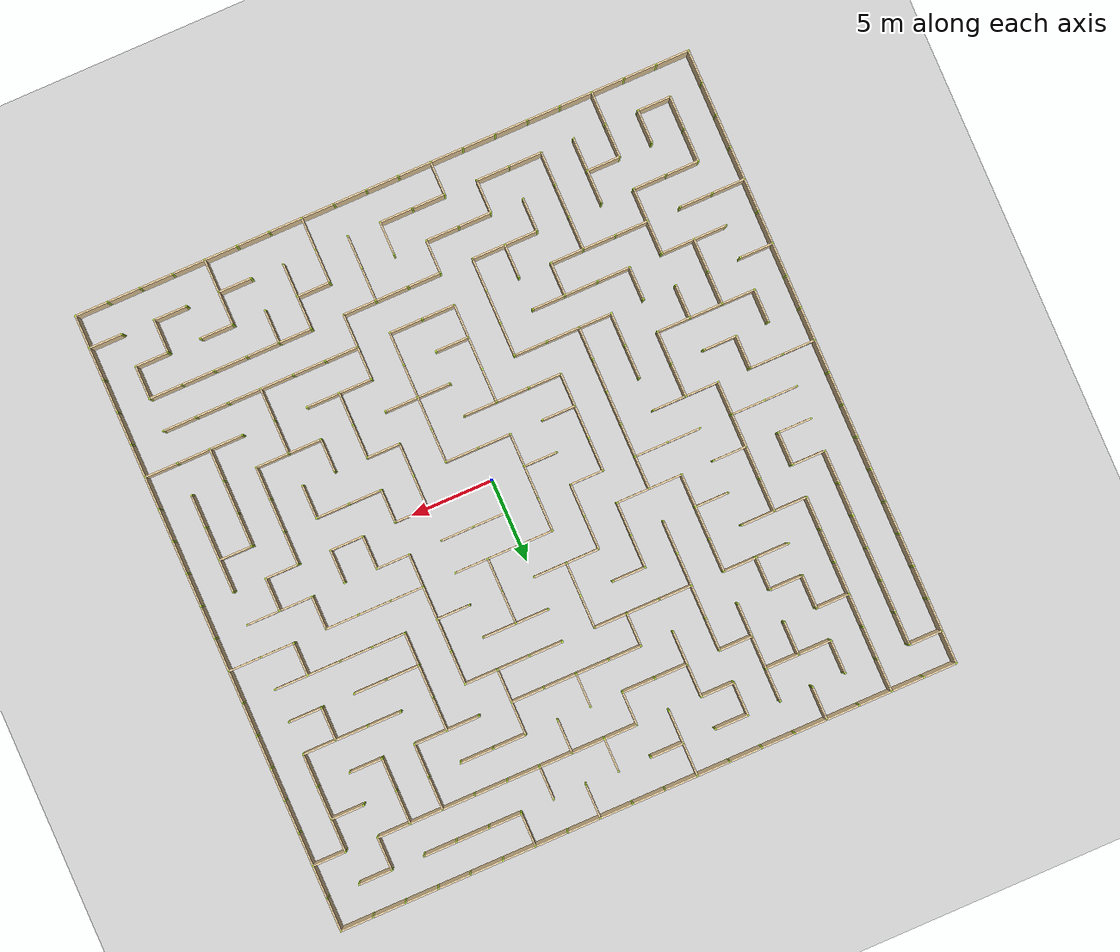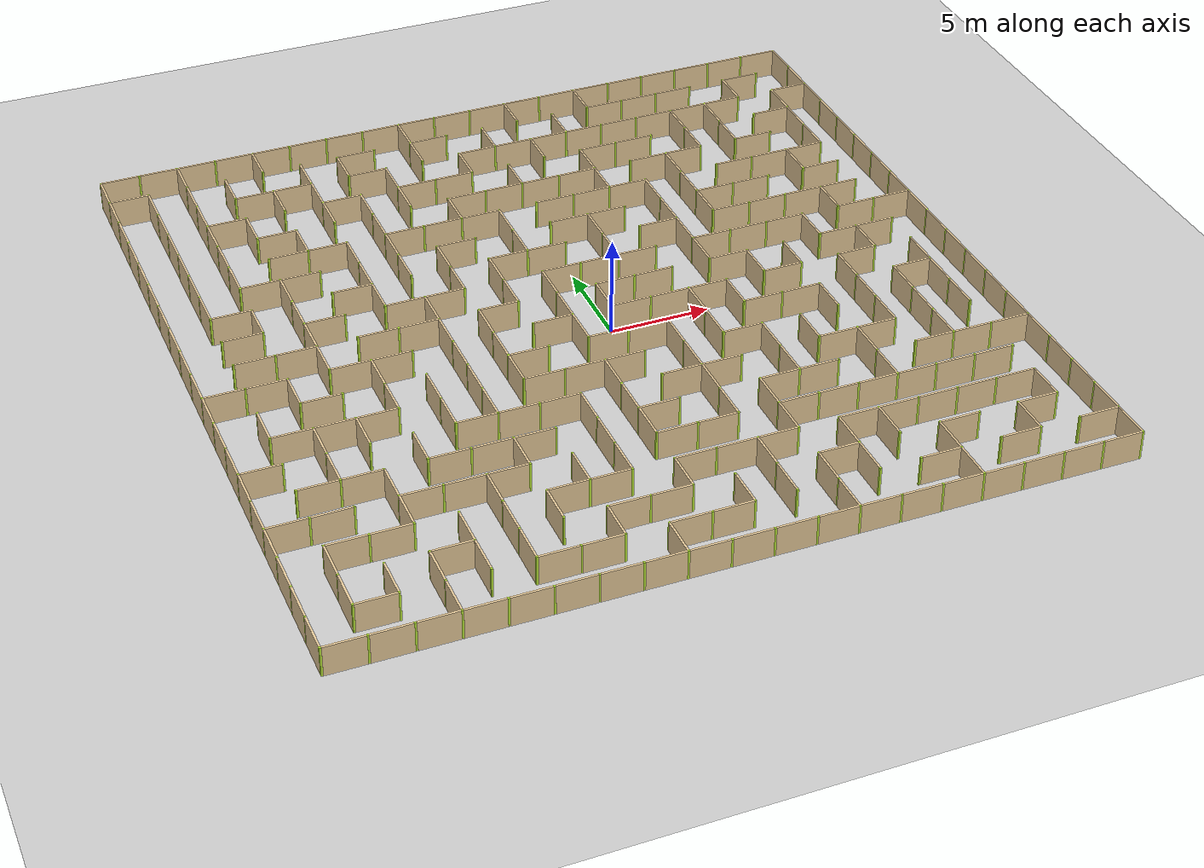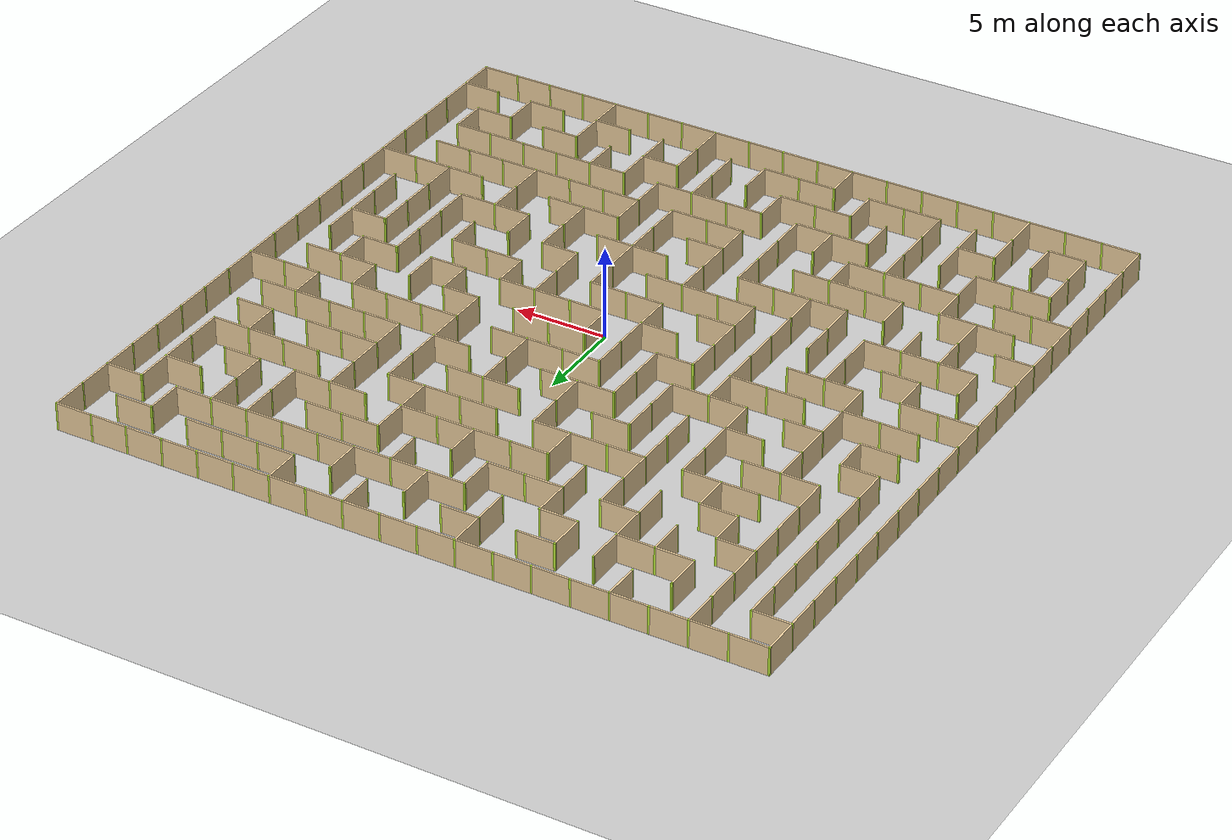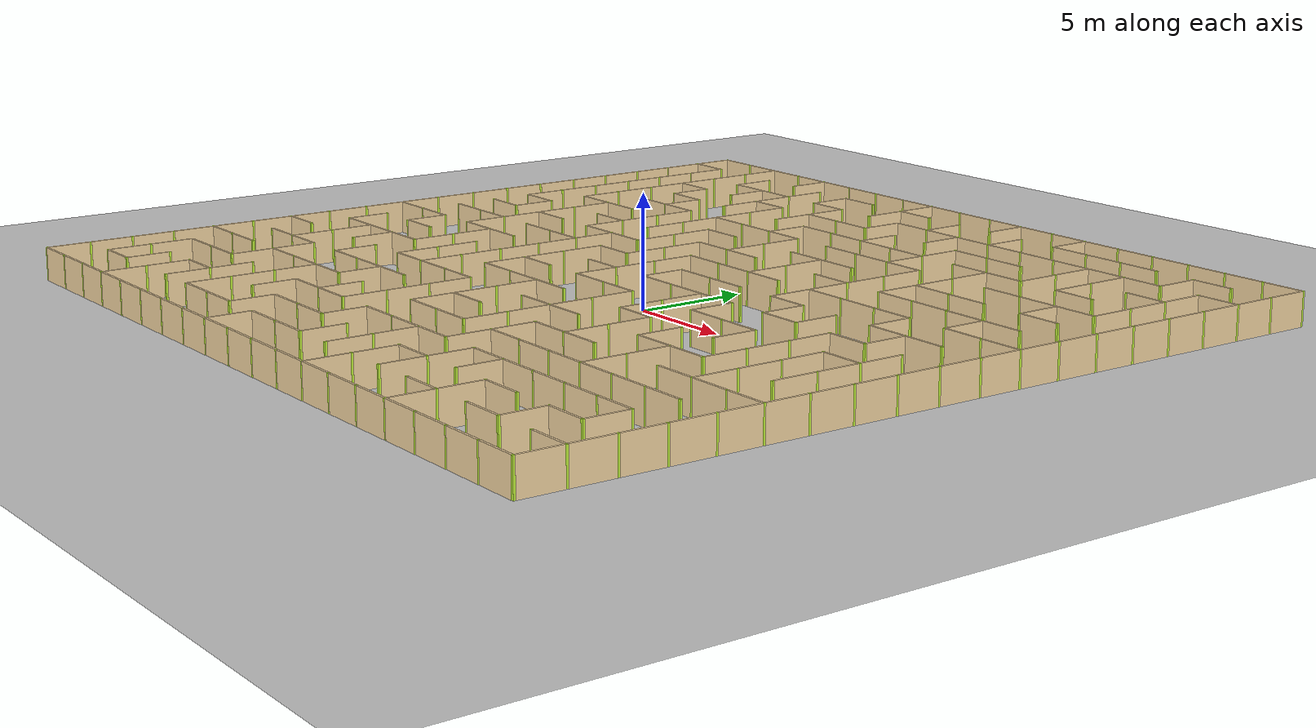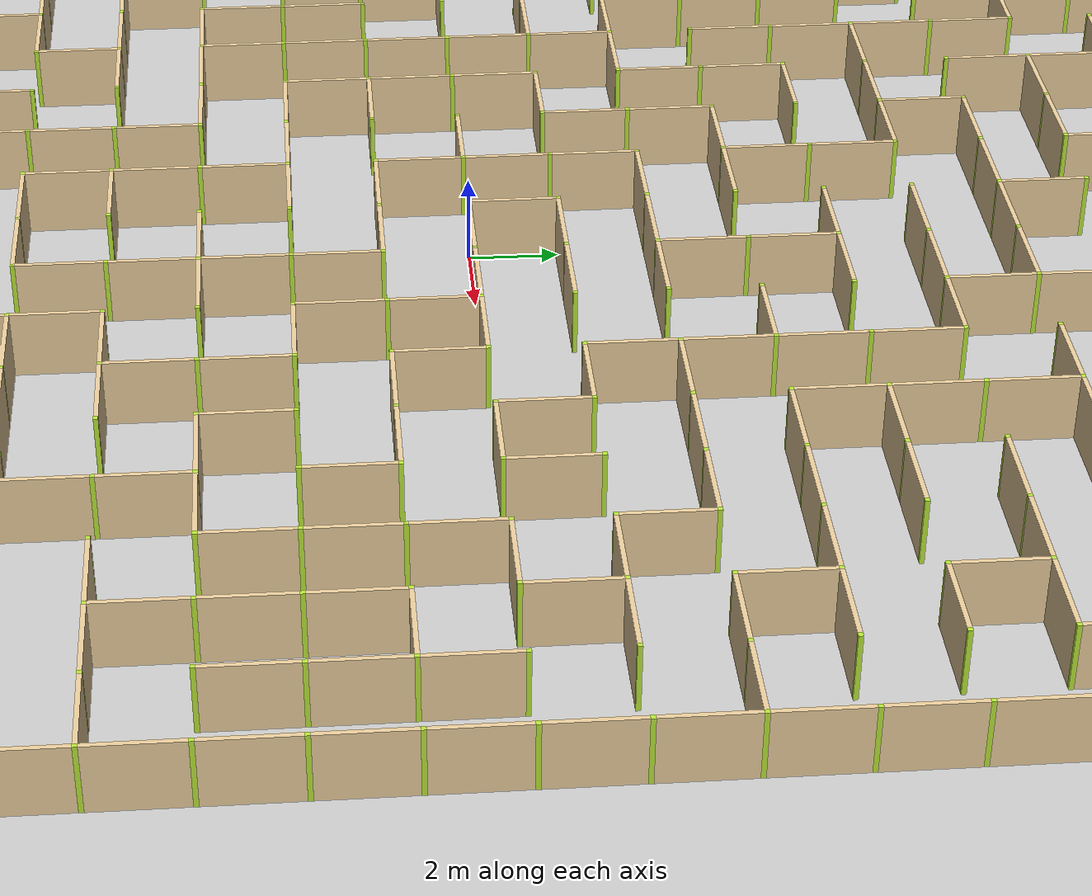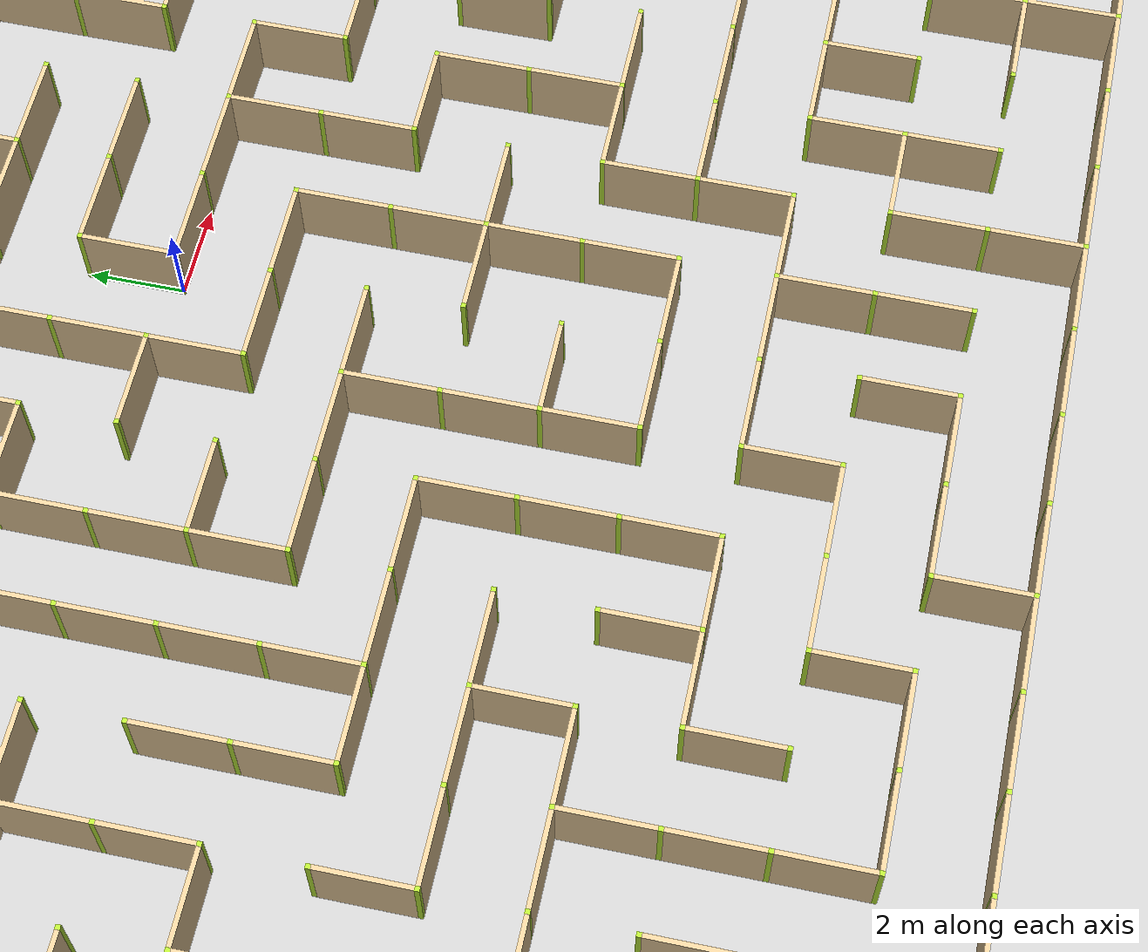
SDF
<sdf version="1.4">
  <world name="maze_world">

         <physics type="ode">
      <ode>
        <solver>
          <!-- IMPORTANT for skid steering to properly work -->
          <friction_model>cone_model</friction_model>
        </solver>
      </ode>
    </physics>
    <light name="sun" type="directional">
      <pose frame="">0 0 100 0.5 0.5 0</pose>
      <diffuse>1 1 1 1</diffuse>
      <specular>0.1 0.1 0.1 1</specular>
      <direction>0.1 0.1 -0.9</direction>
      <attenuation>
        <range>20</range>
        <constant>0.5</constant>
        <linear>0.01</linear>
        <quadratic>0.001</quadratic>
      </attenuation>
      <cast_shadows>1</cast_shadows>
    </light>
    <scene>
      <ambient>0.6 0.6 0.6 1.0</ambient>
      <sky>
        <clouds>
          <speed>12</speed>
        </clouds>
      </sky>
      <shadows>true</shadows>
      <origin_visual>false</origin_visual>
    </scene>
        <model name="ground">
      <static>true</static>
      <link name="ground_link">
        <collision name="collision1">
          <geometry>
            <plane>
              <normal>0 0 1</normal>
            </plane>
          </geometry>
        </collision>
        <visual name="visual1">
          <geometry>
            <plane>
              <normal>0 0 1</normal>
              <size>100 100</size>
            </plane>
          </geometry>
        </visual>
      </link>
    </model>
		<model name='Untitled'>
	  <pose>0 0 0 0 -0 0</pose>
        		  <link name='Wall_0_0_h'>
		    <collision name='Wall_0_Collision'>
		      <geometry>
		        <box>
		          <size>1.9 0.1 1.5</size>
		        </box>
		      </geometry>
		      <pose>0 0 0.75 0 -0 0</pose>
		    </collision>
		    <visual name='Wall_0_Visual'>
		      <pose>0 0 0.75 0 -0 0</pose>
		      <geometry>
		        <box>
		          <size>1.9 0.1 1.5</size>
		        </box>
		      </geometry>
		      <material>
		        <script>
		          <uri>file://media/materials/scripts/gazebo.material</uri>
		          <name>Gazebo/Grey</name>
		        </script>
		        <ambient>0.921569 0.807843 0.615686 1</ambient>
		      </material>
		      <meta>
		        <layer>0</layer>
		      </meta>
		    </visual>
		    <pose>-19.0 20 0 0 -0 0</pose>
		  </link>
        		  <link name='Wall_0_0_v'>
		    <collision name='Wall_0_Collision'>
		      <geometry>
		        <box>
		          <size>1.9 0.1 1.5</size>
		        </box>
		      </geometry>
		      <pose>0 0 0.75 0 -0 0</pose>
		    </collision>
		    <visual name='Wall_0_Visual'>
		      <pose>0 0 0.75 0 -0 0</pose>
		      <geometry>
		        <box>
		          <size>1.9 0.1 1.5</size>
		        </box>
		      </geometry>
		      <material>
		        <script>
		          <uri>file://media/materials/scripts/gazebo.material</uri>
		          <name>Gazebo/Grey</name>
		        </script>
		        <ambient>0.921569 0.807843 0.615686 1</ambient>
		      </material>
		      <meta>
		        <layer>0</layer>
		      </meta>
		    </visual>
		    <pose>-20 19.0 0 0 -0 1.5708</pose>
		  </link>
        	    <link name='Joint_-20_20'>
		    <collision name='Wall_2_Collision'>
		      <geometry>
		        <box>
		          <size>0.1 0.1 1.5</size>
		        </box>
		      </geometry>
		      <pose>0 0 0.75 0 -0 0</pose>
		    </collision>
		    <visual name='Wall_2_Visual'>
		      <pose>0 0 0.75 0 -0 0</pose>
		      <geometry>
		        <box>
		          <size>0.1 0.1 1.5</size>
		        </box>
		      </geometry>
		      <material>
		        <script>
		          <uri>file://media/materials/scripts/gazebo.material</uri>
		          <name>Gazebo/Grey</name>
		        </script>
		        <ambient>0.721569 0.907843 0.215686 1</ambient>
		      </material>
		      <meta>
		        <layer>0</layer>
		      </meta>
		    </visual>
		    <pose>-20 20 0 0 -0 0</pose>
		  </link>
        		  <link name='Wall_1_0_h'>
		    <collision name='Wall_0_Collision'>
		      <geometry>
		        <box>
		          <size>1.9 0.1 1.5</size>
		        </box>
		      </geometry>
		      <pose>0 0 0.75 0 -0 0</pose>
		    </collision>
		    <visual name='Wall_0_Visual'>
		      <pose>0 0 0.75 0 -0 0</pose>
		      <geometry>
		        <box>
		          <size>1.9 0.1 1.5</size>
		        </box>
		      </geometry>
		      <material>
		        <script>
		          <uri>file://media/materials/scripts/gazebo.material</uri>
		          <name>Gazebo/Grey</name>
		        </script>
		        <ambient>0.921569 0.807843 0.615686 1</ambient>
		      </material>
		      <meta>
		        <layer>0</layer>
		      </meta>
		    </visual>
		    <pose>-17.0 20 0 0 -0 0</pose>
		  </link>
        	    <link name='Joint_-18_20'>
		    <collision name='Wall_2_Collision'>
		      <geometry>
		        <box>
		          <size>0.1 0.1 1.5</size>
		        </box>
		      </geometry>
		      <pose>0 0 0.75 0 -0 0</pose>
		    </collision>
		    <visual name='Wall_2_Visual'>
		      <pose>0 0 0.75 0 -0 0</pose>
		      <geometry>
		        <box>
		          <size>0.1 0.1 1.5</size>
		        </box>
		      </geometry>
		      <material>
		        <script>
		          <uri>file://media/materials/scripts/gazebo.material</uri>
		          <name>Gazebo/Grey</name>
		        </script>
		        <ambient>0.721569 0.907843 0.215686 1</ambient>
		      </material>
		      <meta>
		        <layer>0</layer>
		      </meta>
		    </visual>
		    <pose>-18 20 0 0 -0 0</pose>
		  </link>
        		  <link name='Wall_2_0_h'>
		    <collision name='Wall_0_Collision'>
		      <geometry>
		        <box>
		          <size>1.9 0.1 1.5</size>
		        </box>
		      </geometry>
		      <pose>0 0 0.75 0 -0 0</pose>
		    </collision>
		    <visual name='Wall_0_Visual'>
		      <pose>0 0 0.75 0 -0 0</pose>
		      <geometry>
		        <box>
		          <size>1.9 0.1 1.5</size>
		        </box>
		      </geometry>
		      <material>
		        <script>
		          <uri>file://media/materials/scripts/gazebo.material</uri>
		          <name>Gazebo/Grey</name>
		        </script>
		        <ambient>0.921569 0.807843 0.615686 1</ambient>
		      </material>
		      <meta>
		        <layer>0</layer>
		      </meta>
		    </visual>
		    <pose>-15.0 20 0 0 -0 0</pose>
		  </link>
        		  <link name='Wall_2_0_v'>
		    <collision name='Wall_0_Collision'>
		      <geometry>
		        <box>
		          <size>1.9 0.1 1.5</size>
		        </box>
		      </geometry>
		      <pose>0 0 0.75 0 -0 0</pose>
		    </collision>
		    <visual name='Wall_0_Visual'>
		      <pose>0 0 0.75 0 -0 0</pose>
		      <geometry>
		        <box>
		          <size>1.9 0.1 1.5</size>
		        </box>
		      </geometry>
		      <material>
		        <script>
		          <uri>file://media/materials/scripts/gazebo.material</uri>
		          <name>Gazebo/Grey</name>
		        </script>
		        <ambient>0.921569 0.807843 0.615686 1</ambient>
		      </material>
		      <meta>
		        <layer>0</layer>
		      </meta>
		    </visual>
		    <pose>-16 19.0 0 0 -0 1.5708</pose>
		  </link>
        	    <link name='Joint_-16_20'>
		    <collision name='Wall_2_Collision'>
		      <geometry>
		        <box>
		          <size>0.1 0.1 1.5</size>
		        </box>
		      </geometry>
		      <pose>0 0 0.75 0 -0 0</pose>
		    </collision>
		    <visual name='Wall_2_Visual'>
		      <pose>0 0 0.75 0 -0 0</pose>
		      <geometry>
		        <box>
		          <size>0.1 0.1 1.5</size>
		        </box>
		      </geometry>
		      <material>
		        <script>
		          <uri>file://media/materials/scripts/gazebo.material</uri>
		          <name>Gazebo/Grey</name>
		        </script>
		        <ambient>0.721569 0.907843 0.215686 1</ambient>
		      </material>
		      <meta>
		        <layer>0</layer>
		      </meta>
		    </visual>
		    <pose>-16 20 0 0 -0 0</pose>
		  </link>
        		  <link name='Wall_3_0_h'>
		    <collision name='Wall_0_Collision'>
		      <geometry>
		        <box>
		          <size>1.9 0.1 1.5</size>
		        </box>
		      </geometry>
		      <pose>0 0 0.75 0 -0 0</pose>
		    </collision>
		    <visual name='Wall_0_Visual'>
		      <pose>0 0 0.75 0 -0 0</pose>
		      <geometry>
		        <box>
		          <size>1.9 0.1 1.5</size>
		        </box>
		      </geometry>
		      <material>
		        <script>
		          <uri>file://media/materials/scripts/gazebo.material</uri>
		          <name>Gazebo/Grey</name>
		        </script>
		        <ambient>0.921569 0.807843 0.615686 1</ambient>
		      </material>
		      <meta>
		        <layer>0</layer>
		      </meta>
		    </visual>
		    <pose>-13.0 20 0 0 -0 0</pose>
		  </link>
        	    <link name='Joint_-14_20'>
		    <collision name='Wall_2_Collision'>
		      <geometry>
		        <box>
		          <size>0.1 0.1 1.5</size>
		        </box>
		      </geometry>
		      <pose>0 0 0.75 0 -0 0</pose>
		    </collision>
		    <visual name='Wall_2_Visual'>
		      <pose>0 0 0.75 0 -0 0</pose>
		      <geometry>
		        <box>
		          <size>0.1 0.1 1.5</size>
		        </box>
		      </geometry>
		      <material>
		        <script>
		          <uri>file://media/materials/scripts/gazebo.material</uri>
		          <name>Gazebo/Grey</name>
		        </script>
		        <ambient>0.721569 0.907843 0.215686 1</ambient>
		      </material>
		      <meta>
		        <layer>0</layer>
		      </meta>
		    </visual>
		    <pose>-14 20 0 0 -0 0</pose>
		  </link>
        		  <link name='Wall_4_0_h'>
		    <collision name='Wall_0_Collision'>
		      <geometry>
		        <box>
		          <size>1.9 0.1 1.5</size>
		        </box>
		      </geometry>
		      <pose>0 0 0.75 0 -0 0</pose>
		    </collision>
		    <visual name='Wall_0_Visual'>
		      <pose>0 0 0.75 0 -0 0</pose>
		      <geometry>
		        <box>
		          <size>1.9 0.1 1.5</size>
		        </box>
		      </geometry>
		      <material>
		        <script>
		          <uri>file://media/materials/scripts/gazebo.material</uri>
		          <name>Gazebo/Grey</name>
		        </script>
		        <ambient>0.921569 0.807843 0.615686 1</ambient>
		      </material>
		      <meta>
		        <layer>0</layer>
		      </meta>
		    </visual>
		    <pose>-11.0 20 0 0 -0 0</pose>
		  </link>
        		  <link name='Wall_4_0_v'>
		    <collision name='Wall_0_Collision'>
		      <geometry>
		        <box>
		          <size>1.9 0.1 1.5</size>
		        </box>
		      </geometry>
		      <pose>0 0 0.75 0 -0 0</pose>
		    </collision>
		    <visual name='Wall_0_Visual'>
		      <pose>0 0 0.75 0 -0 0</pose>
		      <geometry>
		        <box>
		          <size>1.9 0.1 1.5</size>
		        </box>
		      </geometry>
		      <material>
		        <script>
		          <uri>file://media/materials/scripts/gazebo.material</uri>
		          <name>Gazebo/Grey</name>
		        </script>
		        <ambient>0.921569 0.807843 0.615686 1</ambient>
		      </material>
		      <meta>
		        <layer>0</layer>
		      </meta>
		    </visual>
		    <pose>-12 19.0 0 0 -0 1.5708</pose>
		  </link>
        	    <link name='Joint_-12_20'>
		    <collision name='Wall_2_Collision'>
		      <geometry>
		        <box>
		          <size>0.1 0.1 1.5</size>
		        </box>
		      </geometry>
		      <pose>0 0 0.75 0 -0 0</pose>
		    </collision>
		    <visual name='Wall_2_Visual'>
		      <pose>0 0 0.75 0 -0 0</pose>
		      <geometry>
		        <box>
		          <size>0.1 0.1 1.5</size>
		        </box>
		      </geometry>
		      <material>
		        <script>
		          <uri>file://media/materials/scripts/gazebo.material</uri>
		          <name>Gazebo/Grey</name>
		        </script>
		        <ambient>0.721569 0.907843 0.215686 1</ambient>
		      </material>
		      <meta>
		        <layer>0</layer>
		      </meta>
		    </visual>
		    <pose>-12 20 0 0 -0 0</pose>
		  </link>
        		  <link name='Wall_5_0_h'>
		    <collision name='Wall_0_Collision'>
		      <geometry>
		        <box>
		          <size>1.9 0.1 1.5</size>
		        </box>
		      </geometry>
		      <pose>0 0 0.75 0 -0 0</pose>
		    </collision>
		    <visual name='Wall_0_Visual'>
		      <pose>0 0 0.75 0 -0 0</pose>
		      <geometry>
		        <box>
		          <size>1.9 0.1 1.5</size>
		        </box>
		      </geometry>
		      <material>
		        <script>
		          <uri>file://media/materials/scripts/gazebo.material</uri>
		          <name>Gazebo/Grey</name>
		        </script>
		        <ambient>0.921569 0.807843 0.615686 1</ambient>
		      </material>
		      <meta>
		        <layer>0</layer>
		      </meta>
		    </visual>
		    <pose>-9.0 20 0 0 -0 0</pose>
		  </link>
        	    <link name='Joint_-10_20'>
		    <collision name='Wall_2_Collision'>
		      <geometry>
		        <box>
		          <size>0.1 0.1 1.5</size>
		        </box>
		      </geometry>
		      <pose>0 0 0.75 0 -0 0</pose>
		    </collision>
		    <visual name='Wall_2_Visual'>
		      <pose>0 0 0.75 0 -0 0</pose>
		      <geometry>
		        <box>
		          <size>0.1 0.1 1.5</size>
		        </box>
		      </geometry>
		      <material>
		        <script>
		          <uri>file://media/materials/scripts/gazebo.material</uri>
		          <name>Gazebo/Grey</name>
		        </script>
		        <ambient>0.721569 0.907843 0.215686 1</ambient>
		      </material>
		      <meta>
		        <layer>0</layer>
		      </meta>
		    </visual>
		    <pose>-10 20 0 0 -0 0</pose>
		  </link>
        		  <link name='Wall_6_0_h'>
		    <collision name='Wall_0_Collision'>
		      <geometry>
		        <box>
		          <size>1.9 0.1 1.5</size>
		        </box>
		      </geometry>
		      <pose>0 0 0.75 0 -0 0</pose>
		    </collision>
		    <visual name='Wall_0_Visual'>
		      <pose>0 0 0.75 0 -0 0</pose>
		      <geometry>
		        <box>
		          <size>1.9 0.1 1.5</size>
		        </box>
		      </geometry>
		      <material>
		        <script>
		          <uri>file://media/materials/scripts/gazebo.material</uri>
		          <name>Gazebo/Grey</name>
		        </script>
		        <ambient>0.921569 0.807843 0.615686 1</ambient>
		      </material>
		      <meta>
		        <layer>0</layer>
		      </meta>
		    </visual>
		    <pose>-7.0 20 0 0 -0 0</pose>
		  </link>
        	    <link name='Joint_-8_20'>
		    <collision name='Wall_2_Collision'>
		      <geometry>
		        <box>
		          <size>0.1 0.1 1.5</size>
		        </box>
		      </geometry>
		      <pose>0 0 0.75 0 -0 0</pose>
		    </collision>
		    <visual name='Wall_2_Visual'>
		      <pose>0 0 0.75 0 -0 0</pose>
		      <geometry>
		        <box>
		          <size>0.1 0.1 1.5</size>
		        </box>
		      </geometry>
		      <material>
		        <script>
		          <uri>file://media/materials/scripts/gazebo.material</uri>
		          <name>Gazebo/Grey</name>
		        </script>
		        <ambient>0.721569 0.907843 0.215686 1</ambient>
		      </material>
		      <meta>
		        <layer>0</layer>
		      </meta>
		    </visual>
		    <pose>-8 20 0 0 -0 0</pose>
		  </link>
        		  <link name='Wall_7_0_h'>
		    <collision name='Wall_0_Collision'>
		      <geometry>
		        <box>
		          <size>1.9 0.1 1.5</size>
		        </box>
		      </geometry>
		      <pose>0 0 0.75 0 -0 0</pose>
		    </collision>
		    <visual name='Wall_0_Visual'>
		      <pose>0 0 0.75 0 -0 0</pose>
		      <geometry>
		        <box>
		          <size>1.9 0.1 1.5</size>
		        </box>
		      </geometry>
		      <material>
		        <script>
		          <uri>file://media/materials/scripts/gazebo.material</uri>
		          <name>Gazebo/Grey</name>
		        </script>
		        <ambient>0.921569 0.807843 0.615686 1</ambient>
		      </material>
		      <meta>
		        <layer>0</layer>
		      </meta>
		    </visual>
		    <pose>-5.0 20 0 0 -0 0</pose>
		  </link>
        	    <link name='Joint_-6_20'>
		    <collision name='Wall_2_Collision'>
		      <geometry>
		        <box>
		          <size>0.1 0.1 1.5</size>
		        </box>
		      </geometry>
		      <pose>0 0 0.75 0 -0 0</pose>
		    </collision>
		    <visual name='Wall_2_Visual'>
		      <pose>0 0 0.75 0 -0 0</pose>
		      <geometry>
		        <box>
		          <size>0.1 0.1 1.5</size>
		        </box>
		      </geometry>
		      <material>
		        <script>
		          <uri>file://media/materials/scripts/gazebo.material</uri>
		          <name>Gazebo/Grey</name>
		        </script>
		        <ambient>0.721569 0.907843 0.215686 1</ambient>
		      </material>
		      <meta>
		        <layer>0</layer>
		      </meta>
		    </visual>
		    <pose>-6 20 0 0 -0 0</pose>
		  </link>
        		  <link name='Wall_8_0_h'>
		    <collision name='Wall_0_Collision'>
		      <geometry>
		        <box>
		          <size>1.9 0.1 1.5</size>
		        </box>
		      </geometry>
		      <pose>0 0 0.75 0 -0 0</pose>
		    </collision>
		    <visual name='Wall_0_Visual'>
		      <pose>0 0 0.75 0 -0 0</pose>
		      <geometry>
		        <box>
		          <size>1.9 0.1 1.5</size>
		        </box>
		      </geometry>
		      <material>
		        <script>
		          <uri>file://media/materials/scripts/gazebo.material</uri>
		          <name>Gazebo/Grey</name>
		        </script>
		        <ambient>0.921569 0.807843 0.615686 1</ambient>
		      </material>
		      <meta>
		        <layer>0</layer>
		      </meta>
		    </visual>
		    <pose>-3.0 20 0 0 -0 0</pose>
		  </link>
        		  <link name='Wall_8_0_v'>
		    <collision name='Wall_0_Collision'>
		      <geometry>
		        <box>
		          <size>1.9 0.1 1.5</size>
		        </box>
		      </geometry>
		      <pose>0 0 0.75 0 -0 0</pose>
		    </collision>
		    <visual name='Wall_0_Visual'>
		      <pose>0 0 0.75 0 -0 0</pose>
		      <geometry>
		        <box>
		          <size>1.9 0.1 1.5</size>
		        </box>
		      </geometry>
		      <material>
		        <script>
		          <uri>file://media/materials/scripts/gazebo.material</uri>
		          <name>Gazebo/Grey</name>
		        </script>
		        <ambient>0.921569 0.807843 0.615686 1</ambient>
		      </material>
		      <meta>
		        <layer>0</layer>
		      </meta>
		    </visual>
		    <pose>-4 19.0 0 0 -0 1.5708</pose>
		  </link>
        	    <link name='Joint_-4_20'>
		    <collision name='Wall_2_Collision'>
		      <geometry>
		        <box>
		          <size>0.1 0.1 1.5</size>
		        </box>
		      </geometry>
		      <pose>0 0 0.75 0 -0 0</pose>
		    </collision>
		    <visual name='Wall_2_Visual'>
		      <pose>0 0 0.75 0 -0 0</pose>
		      <geometry>
		        <box>
		          <size>0.1 0.1 1.5</size>
		        </box>
		      </geometry>
		      <material>
		        <script>
		          <uri>file://media/materials/scripts/gazebo.material</uri>
		          <name>Gazebo/Grey</name>
		        </script>
		        <ambient>0.721569 0.907843 0.215686 1</ambient>
		      </material>
		      <meta>
		        <layer>0</layer>
		      </meta>
		    </visual>
		    <pose>-4 20 0 0 -0 0</pose>
		  </link>
        		  <link name='Wall_9_0_h'>
		    <collision name='Wall_0_Collision'>
		      <geometry>
		        <box>
		          <size>1.9 0.1 1.5</size>
		        </box>
		      </geometry>
		      <pose>0 0 0.75 0 -0 0</pose>
		    </collision>
		    <visual name='Wall_0_Visual'>
		      <pose>0 0 0.75 0 -0 0</pose>
		      <geometry>
		        <box>
		          <size>1.9 0.1 1.5</size>
		        </box>
		      </geometry>
		      <material>
		        <script>
		          <uri>file://media/materials/scripts/gazebo.material</uri>
		          <name>Gazebo/Grey</name>
		        </script>
		        <ambient>0.921569 0.807843 0.615686 1</ambient>
		      </material>
		      <meta>
		        <layer>0</layer>
		      </meta>
		    </visual>
		    <pose>-1.0 20 0 0 -0 0</pose>
		  </link>
        	    <link name='Joint_-2_20'>
		    <collision name='Wall_2_Collision'>
		      <geometry>
		        <box>
		          <size>0.1 0.1 1.5</size>
		        </box>
		      </geometry>
		      <pose>0 0 0.75 0 -0 0</pose>
		    </collision>
		    <visual name='Wall_2_Visual'>
		      <pose>0 0 0.75 0 -0 0</pose>
		      <geometry>
		        <box>
		          <size>0.1 0.1 1.5</size>
		        </box>
		      </geometry>
		      <material>
		        <script>
		          <uri>file://media/materials/scripts/gazebo.material</uri>
		          <name>Gazebo/Grey</name>
		        </script>
		        <ambient>0.721569 0.907843 0.215686 1</ambient>
		      </material>
		      <meta>
		        <layer>0</layer>
		      </meta>
		    </visual>
		    <pose>-2 20 0 0 -0 0</pose>
		  </link>
        		  <link name='Wall_10_0_h'>
		    <collision name='Wall_0_Collision'>
		      <geometry>
		        <box>
		          <size>1.9 0.1 1.5</size>
		        </box>
		      </geometry>
		      <pose>0 0 0.75 0 -0 0</pose>
		    </collision>
		    <visual name='Wall_0_Visual'>
		      <pose>0 0 0.75 0 -0 0</pose>
		      <geometry>
		        <box>
		          <size>1.9 0.1 1.5</size>
		        </box>
		      </geometry>
		      <material>
		        <script>
		          <uri>file://media/materials/scripts/gazebo.material</uri>
		          <name>Gazebo/Grey</name>
		        </script>
		        <ambient>0.921569 0.807843 0.615686 1</ambient>
		      </material>
		      <meta>
		        <layer>0</layer>
		      </meta>
		    </visual>
		    <pose>1.0 20 0 0 -0 0</pose>
		  </link>
        	    <link name='Joint_0_20'>
		    <collision name='Wall_2_Collision'>
		      <geometry>
		        <box>
		          <size>0.1 0.1 1.5</size>
		        </box>
		      </geometry>
		      <pose>0 0 0.75 0 -0 0</pose>
		    </collision>
		    <visual name='Wall_2_Visual'>
		      <pose>0 0 0.75 0 -0 0</pose>
		      <geometry>
		        <box>
		          <size>0.1 0.1 1.5</size>
		        </box>
		      </geometry>
		      <material>
		        <script>
		          <uri>file://media/materials/scripts/gazebo.material</uri>
		          <name>Gazebo/Grey</name>
		        </script>
		        <ambient>0.721569 0.907843 0.215686 1</ambient>
		      </material>
		      <meta>
		        <layer>0</layer>
		      </meta>
		    </visual>
		    <pose>0 20 0 0 -0 0</pose>
		  </link>
        		  <link name='Wall_11_0_h'>
		    <collision name='Wall_0_Collision'>
		      <geometry>
		        <box>
		          <size>1.9 0.1 1.5</size>
		        </box>
		      </geometry>
		      <pose>0 0 0.75 0 -0 0</pose>
		    </collision>
		    <visual name='Wall_0_Visual'>
		      <pose>0 0 0.75 0 -0 0</pose>
		      <geometry>
		        <box>
		          <size>1.9 0.1 1.5</size>
		        </box>
		      </geometry>
		      <material>
		        <script>
		          <uri>file://media/materials/scripts/gazebo.material</uri>
		          <name>Gazebo/Grey</name>
		        </script>
		        <ambient>0.921569 0.807843 0.615686 1</ambient>
		      </material>
		      <meta>
		        <layer>0</layer>
		      </meta>
		    </visual>
		    <pose>3.0 20 0 0 -0 0</pose>
		  </link>
        		  <link name='Wall_11_0_v'>
		    <collision name='Wall_0_Collision'>
		      <geometry>
		        <box>
		          <size>1.9 0.1 1.5</size>
		        </box>
		      </geometry>
		      <pose>0 0 0.75 0 -0 0</pose>
		    </collision>
		    <visual name='Wall_0_Visual'>
		      <pose>0 0 0.75 0 -0 0</pose>
		      <geometry>
		        <box>
		          <size>1.9 0.1 1.5</size>
		        </box>
		      </geometry>
		      <material>
		        <script>
		          <uri>file://media/materials/scripts/gazebo.material</uri>
		          <name>Gazebo/Grey</name>
		        </script>
		        <ambient>0.921569 0.807843 0.615686 1</ambient>
		      </material>
		      <meta>
		        <layer>0</layer>
		      </meta>
		    </visual>
		    <pose>2 19.0 0 0 -0 1.5708</pose>
		  </link>
        	    <link name='Joint_2_20'>
		    <collision name='Wall_2_Collision'>
		      <geometry>
		        <box>
		          <size>0.1 0.1 1.5</size>
		        </box>
		      </geometry>
		      <pose>0 0 0.75 0 -0 0</pose>
		    </collision>
		    <visual name='Wall_2_Visual'>
		      <pose>0 0 0.75 0 -0 0</pose>
		      <geometry>
		        <box>
		          <size>0.1 0.1 1.5</size>
		        </box>
		      </geometry>
		      <material>
		        <script>
		          <uri>file://media/materials/scripts/gazebo.material</uri>
		          <name>Gazebo/Grey</name>
		        </script>
		        <ambient>0.721569 0.907843 0.215686 1</ambient>
		      </material>
		      <meta>
		        <layer>0</layer>
		      </meta>
		    </visual>
		    <pose>2 20 0 0 -0 0</pose>
		  </link>
        		  <link name='Wall_12_0_h'>
		    <collision name='Wall_0_Collision'>
		      <geometry>
		        <box>
		          <size>1.9 0.1 1.5</size>
		        </box>
		      </geometry>
		      <pose>0 0 0.75 0 -0 0</pose>
		    </collision>
		    <visual name='Wall_0_Visual'>
		      <pose>0 0 0.75 0 -0 0</pose>
		      <geometry>
		        <box>
		          <size>1.9 0.1 1.5</size>
		        </box>
		      </geometry>
		      <material>
		        <script>
		          <uri>file://media/materials/scripts/gazebo.material</uri>
		          <name>Gazebo/Grey</name>
		        </script>
		        <ambient>0.921569 0.807843 0.615686 1</ambient>
		      </material>
		      <meta>
		        <layer>0</layer>
		      </meta>
		    </visual>
		    <pose>5.0 20 0 0 -0 0</pose>
		  </link>
        	    <link name='Joint_4_20'>
		    <collision name='Wall_2_Collision'>
		      <geometry>
		        <box>
		          <size>0.1 0.1 1.5</size>
		        </box>
		      </geometry>
		      <pose>0 0 0.75 0 -0 0</pose>
		    </collision>
		    <visual name='Wall_2_Visual'>
		      <pose>0 0 0.75 0 -0 0</pose>
		      <geometry>
		        <box>
		          <size>0.1 0.1 1.5</size>
		        </box>
		      </geometry>
		      <material>
		        <script>
		          <uri>file://media/materials/scripts/gazebo.material</uri>
		          <name>Gazebo/Grey</name>
		        </script>
		        <ambient>0.721569 0.907843 0.215686 1</ambient>
		      </material>
		      <meta>
		        <layer>0</layer>
		      </meta>
		    </visual>
		    <pose>4 20 0 0 -0 0</pose>
		  </link>
        		  <link name='Wall_13_0_h'>
		    <collision name='Wall_0_Collision'>
		      <geometry>
		        <box>
		          <size>1.9 0.1 1.5</size>
		        </box>
		      </geometry>
		      <pose>0 0 0.75 0 -0 0</pose>
		    </collision>
		    <visual name='Wall_0_Visual'>
		      <pose>0 0 0.75 0 -0 0</pose>
		      <geometry>
		        <box>
		          <size>1.9 0.1 1.5</size>
		        </box>
		      </geometry>
		      <material>
		        <script>
		          <uri>file://media/materials/scripts/gazebo.material</uri>
		          <name>Gazebo/Grey</name>
		        </script>
		        <ambient>0.921569 0.807843 0.615686 1</ambient>
		      </material>
		      <meta>
		        <layer>0</layer>
		      </meta>
		    </visual>
		    <pose>7.0 20 0 0 -0 0</pose>
		  </link>
        		  <link name='Wall_13_0_v'>
		    <collision name='Wall_0_Collision'>
		      <geometry>
		        <box>
		          <size>1.9 0.1 1.5</size>
		        </box>
		      </geometry>
		      <pose>0 0 0.75 0 -0 0</pose>
		    </collision>
		    <visual name='Wall_0_Visual'>
		      <pose>0 0 0.75 0 -0 0</pose>
		      <geometry>
		        <box>
		          <size>1.9 0.1 1.5</size>
		        </box>
		      </geometry>
		      <material>
		        <script>
		          <uri>file://media/materials/scripts/gazebo.material</uri>
		          <name>Gazebo/Grey</name>
		        </script>
		        <ambient>0.921569 0.807843 0.615686 1</ambient>
		      </material>
		      <meta>
		        <layer>0</layer>
		      </meta>
		    </visual>
		    <pose>6 19.0 0 0 -0 1.5708</pose>
		  </link>
        	    <link name='Joint_6_20'>
		    <collision name='Wall_2_Collision'>
		      <geometry>
		        <box>
		          <size>0.1 0.1 1.5</size>
		        </box>
		      </geometry>
		      <pose>0 0 0.75 0 -0 0</pose>
		    </collision>
		    <visual name='Wall_2_Visual'>
		      <pose>0 0 0.75 0 -0 0</pose>
		      <geometry>
		        <box>
		          <size>0.1 0.1 1.5</size>
		        </box>
		      </geometry>
		      <material>
		        <script>
		          <uri>file://media/materials/scripts/gazebo.material</uri>
		          <name>Gazebo/Grey</name>
		        </script>
		        <ambient>0.721569 0.907843 0.215686 1</ambient>
		      </material>
		      <meta>
		        <layer>0</layer>
		      </meta>
		    </visual>
		    <pose>6 20 0 0 -0 0</pose>
		  </link>
        		  <link name='Wall_14_0_h'>
		    <collision name='Wall_0_Collision'>
		      <geometry>
		        <box>
		          <size>1.9 0.1 1.5</size>
		        </box>
		      </geometry>
		      <pose>0 0 0.75 0 -0 0</pose>
		    </collision>
		    <visual name='Wall_0_Visual'>
		      <pose>0 0 0.75 0 -0 0</pose>
		      <geometry>
		        <box>
		          <size>1.9 0.1 1.5</size>
		        </box>
		      </geometry>
		      <material>
		        <script>
		          <uri>file://media/materials/scripts/gazebo.material</uri>
		          <name>Gazebo/Grey</name>
		        </script>
		        <ambient>0.921569 0.807843 0.615686 1</ambient>
		      </material>
		      <meta>
		        <layer>0</layer>
		      </meta>
		    </visual>
		    <pose>9.0 20 0 0 -0 0</pose>
		  </link>
        	    <link name='Joint_8_20'>
		    <collision name='Wall_2_Collision'>
		      <geometry>
		        <box>
		          <size>0.1 0.1 1.5</size>
		        </box>
		      </geometry>
		      <pose>0 0 0.75 0 -0 0</pose>
		    </collision>
		    <visual name='Wall_2_Visual'>
		      <pose>0 0 0.75 0 -0 0</pose>
		      <geometry>
		        <box>
		          <size>0.1 0.1 1.5</size>
		        </box>
		      </geometry>
		      <material>
		        <script>
		          <uri>file://media/materials/scripts/gazebo.material</uri>
		          <name>Gazebo/Grey</name>
		        </script>
		        <ambient>0.721569 0.907843 0.215686 1</ambient>
		      </material>
		      <meta>
		        <layer>0</layer>
		      </meta>
		    </visual>
		    <pose>8 20 0 0 -0 0</pose>
		  </link>
        		  <link name='Wall_15_0_h'>
		    <collision name='Wall_0_Collision'>
		      <geometry>
		        <box>
		          <size>1.9 0.1 1.5</size>
		        </box>
		      </geometry>
		      <pose>0 0 0.75 0 -0 0</pose>
		    </collision>
		    <visual name='Wall_0_Visual'>
		      <pose>0 0 0.75 0 -0 0</pose>
		      <geometry>
		        <box>
		          <size>1.9 0.1 1.5</size>
		        </box>
		      </geometry>
		      <material>
		        <script>
		          <uri>file://media/materials/scripts/gazebo.material</uri>
		          <name>Gazebo/Grey</name>
		        </script>
		        <ambient>0.921569 0.807843 0.615686 1</ambient>
		      </material>
		      <meta>
		        <layer>0</layer>
		      </meta>
		    </visual>
		    <pose>11.0 20 0 0 -0 0</pose>
		  </link>
        	    <link name='Joint_10_20'>
		    <collision name='Wall_2_Collision'>
		      <geometry>
		        <box>
		          <size>0.1 0.1 1.5</size>
		        </box>
		      </geometry>
		      <pose>0 0 0.75 0 -0 0</pose>
		    </collision>
		    <visual name='Wall_2_Visual'>
		      <pose>0 0 0.75 0 -0 0</pose>
		      <geometry>
		        <box>
		          <size>0.1 0.1 1.5</size>
		        </box>
		      </geometry>
		      <material>
		        <script>
		          <uri>file://media/materials/scripts/gazebo.material</uri>
		          <name>Gazebo/Grey</name>
		        </script>
		        <ambient>0.721569 0.907843 0.215686 1</ambient>
		      </material>
		      <meta>
		        <layer>0</layer>
		      </meta>
		    </visual>
		    <pose>10 20 0 0 -0 0</pose>
		  </link>
        		  <link name='Wall_16_0_h'>
		    <collision name='Wall_0_Collision'>
		      <geometry>
		        <box>
		          <size>1.9 0.1 1.5</size>
		        </box>
		      </geometry>
		      <pose>0 0 0.75 0 -0 0</pose>
		    </collision>
		    <visual name='Wall_0_Visual'>
		      <pose>0 0 0.75 0 -0 0</pose>
		      <geometry>
		        <box>
		          <size>1.9 0.1 1.5</size>
		        </box>
		      </geometry>
		      <material>
		        <script>
		          <uri>file://media/materials/scripts/gazebo.material</uri>
		          <name>Gazebo/Grey</name>
		        </script>
		        <ambient>0.921569 0.807843 0.615686 1</ambient>
		      </material>
		      <meta>
		        <layer>0</layer>
		      </meta>
		    </visual>
		    <pose>13.0 20 0 0 -0 0</pose>
		  </link>
        	    <link name='Joint_12_20'>
		    <collision name='Wall_2_Collision'>
		      <geometry>
		        <box>
		          <size>0.1 0.1 1.5</size>
		        </box>
		      </geometry>
		      <pose>0 0 0.75 0 -0 0</pose>
		    </collision>
		    <visual name='Wall_2_Visual'>
		      <pose>0 0 0.75 0 -0 0</pose>
		      <geometry>
		        <box>
		          <size>0.1 0.1 1.5</size>
		        </box>
		      </geometry>
		      <material>
		        <script>
		          <uri>file://media/materials/scripts/gazebo.material</uri>
		          <name>Gazebo/Grey</name>
		        </script>
		        <ambient>0.721569 0.907843 0.215686 1</ambient>
		      </material>
		      <meta>
		        <layer>0</layer>
		      </meta>
		    </visual>
		    <pose>12 20 0 0 -0 0</pose>
		  </link>
        		  <link name='Wall_17_0_h'>
		    <collision name='Wall_0_Collision'>
		      <geometry>
		        <box>
		          <size>1.9 0.1 1.5</size>
		        </box>
		      </geometry>
		      <pose>0 0 0.75 0 -0 0</pose>
		    </collision>
		    <visual name='Wall_0_Visual'>
		      <pose>0 0 0.75 0 -0 0</pose>
		      <geometry>
		        <box>
		          <size>1.9 0.1 1.5</size>
		        </box>
		      </geometry>
		      <material>
		        <script>
		          <uri>file://media/materials/scripts/gazebo.material</uri>
		          <name>Gazebo/Grey</name>
		        </script>
		        <ambient>0.921569 0.807843 0.615686 1</ambient>
		      </material>
		      <meta>
		        <layer>0</layer>
		      </meta>
		    </visual>
		    <pose>15.0 20 0 0 -0 0</pose>
		  </link>
        	    <link name='Joint_14_20'>
		    <collision name='Wall_2_Collision'>
		      <geometry>
		        <box>
		          <size>0.1 0.1 1.5</size>
		        </box>
		      </geometry>
		      <pose>0 0 0.75 0 -0 0</pose>
		    </collision>
		    <visual name='Wall_2_Visual'>
		      <pose>0 0 0.75 0 -0 0</pose>
		      <geometry>
		        <box>
		          <size>0.1 0.1 1.5</size>
		        </box>
		      </geometry>
		      <material>
		        <script>
		          <uri>file://media/materials/scripts/gazebo.material</uri>
		          <name>Gazebo/Grey</name>
		        </script>
		        <ambient>0.721569 0.907843 0.215686 1</ambient>
		      </material>
		      <meta>
		        <layer>0</layer>
		      </meta>
		    </visual>
		    <pose>14 20 0 0 -0 0</pose>
		  </link>
        		  <link name='Wall_18_0_h'>
		    <collision name='Wall_0_Collision'>
		      <geometry>
		        <box>
		          <size>1.9 0.1 1.5</size>
		        </box>
		      </geometry>
		      <pose>0 0 0.75 0 -0 0</pose>
		    </collision>
		    <visual name='Wall_0_Visual'>
		      <pose>0 0 0.75 0 -0 0</pose>
		      <geometry>
		        <box>
		          <size>1.9 0.1 1.5</size>
		        </box>
		      </geometry>
		      <material>
		        <script>
		          <uri>file://media/materials/scripts/gazebo.material</uri>
		          <name>Gazebo/Grey</name>
		        </script>
		        <ambient>0.921569 0.807843 0.615686 1</ambient>
		      </material>
		      <meta>
		        <layer>0</layer>
		      </meta>
		    </visual>
		    <pose>17.0 20 0 0 -0 0</pose>
		  </link>
        	    <link name='Joint_16_20'>
		    <collision name='Wall_2_Collision'>
		      <geometry>
		        <box>
		          <size>0.1 0.1 1.5</size>
		        </box>
		      </geometry>
		      <pose>0 0 0.75 0 -0 0</pose>
		    </collision>
		    <visual name='Wall_2_Visual'>
		      <pose>0 0 0.75 0 -0 0</pose>
		      <geometry>
		        <box>
		          <size>0.1 0.1 1.5</size>
		        </box>
		      </geometry>
		      <material>
		        <script>
		          <uri>file://media/materials/scripts/gazebo.material</uri>
		          <name>Gazebo/Grey</name>
		        </script>
		        <ambient>0.721569 0.907843 0.215686 1</ambient>
		      </material>
		      <meta>
		        <layer>0</layer>
		      </meta>
		    </visual>
		    <pose>16 20 0 0 -0 0</pose>
		  </link>
        		  <link name='Wall_19_0_v'>
		    <collision name='Wall_0_Collision'>
		      <geometry>
		        <box>
		          <size>1.9 0.1 1.5</size>
		        </box>
		      </geometry>
		      <pose>0 0 0.75 0 -0 0</pose>
		    </collision>
		    <visual name='Wall_0_Visual'>
		      <pose>0 0 0.75 0 -0 0</pose>
		      <geometry>
		        <box>
		          <size>1.9 0.1 1.5</size>
		        </box>
		      </geometry>
		      <material>
		        <script>
		          <uri>file://media/materials/scripts/gazebo.material</uri>
		          <name>Gazebo/Grey</name>
		        </script>
		        <ambient>0.921569 0.807843 0.615686 1</ambient>
		      </material>
		      <meta>
		        <layer>0</layer>
		      </meta>
		    </visual>
		    <pose>18 19.0 0 0 -0 1.5708</pose>
		  </link>
        	    <link name='Joint_18_20'>
		    <collision name='Wall_2_Collision'>
		      <geometry>
		        <box>
		          <size>0.1 0.1 1.5</size>
		        </box>
		      </geometry>
		      <pose>0 0 0.75 0 -0 0</pose>
		    </collision>
		    <visual name='Wall_2_Visual'>
		      <pose>0 0 0.75 0 -0 0</pose>
		      <geometry>
		        <box>
		          <size>0.1 0.1 1.5</size>
		        </box>
		      </geometry>
		      <material>
		        <script>
		          <uri>file://media/materials/scripts/gazebo.material</uri>
		          <name>Gazebo/Grey</name>
		        </script>
		        <ambient>0.721569 0.907843 0.215686 1</ambient>
		      </material>
		      <meta>
		        <layer>0</layer>
		      </meta>
		    </visual>
		    <pose>18 20 0 0 -0 0</pose>
		  </link>
        		  <link name='Wall_0_1_h'>
		    <collision name='Wall_0_Collision'>
		      <geometry>
		        <box>
		          <size>1.9 0.1 1.5</size>
		        </box>
		      </geometry>
		      <pose>0 0 0.75 0 -0 0</pose>
		    </collision>
		    <visual name='Wall_0_Visual'>
		      <pose>0 0 0.75 0 -0 0</pose>
		      <geometry>
		        <box>
		          <size>1.9 0.1 1.5</size>
		        </box>
		      </geometry>
		      <material>
		        <script>
		          <uri>file://media/materials/scripts/gazebo.material</uri>
		          <name>Gazebo/Grey</name>
		        </script>
		        <ambient>0.921569 0.807843 0.615686 1</ambient>
		      </material>
		      <meta>
		        <layer>0</layer>
		      </meta>
		    </visual>
		    <pose>-19.0 18 0 0 -0 0</pose>
		  </link>
        		  <link name='Wall_0_1_v'>
		    <collision name='Wall_0_Collision'>
		      <geometry>
		        <box>
		          <size>1.9 0.1 1.5</size>
		        </box>
		      </geometry>
		      <pose>0 0 0.75 0 -0 0</pose>
		    </collision>
		    <visual name='Wall_0_Visual'>
		      <pose>0 0 0.75 0 -0 0</pose>
		      <geometry>
		        <box>
		          <size>1.9 0.1 1.5</size>
		        </box>
		      </geometry>
		      <material>
		        <script>
		          <uri>file://media/materials/scripts/gazebo.material</uri>
		          <name>Gazebo/Grey</name>
		        </script>
		        <ambient>0.921569 0.807843 0.615686 1</ambient>
		      </material>
		      <meta>
		        <layer>0</layer>
		      </meta>
		    </visual>
		    <pose>-20 17.0 0 0 -0 1.5708</pose>
		  </link>
        	    <link name='Joint_-20_18'>
		    <collision name='Wall_2_Collision'>
		      <geometry>
		        <box>
		          <size>0.1 0.1 1.5</size>
		        </box>
		      </geometry>
		      <pose>0 0 0.75 0 -0 0</pose>
		    </collision>
		    <visual name='Wall_2_Visual'>
		      <pose>0 0 0.75 0 -0 0</pose>
		      <geometry>
		        <box>
		          <size>0.1 0.1 1.5</size>
		        </box>
		      </geometry>
		      <material>
		        <script>
		          <uri>file://media/materials/scripts/gazebo.material</uri>
		          <name>Gazebo/Grey</name>
		        </script>
		        <ambient>0.721569 0.907843 0.215686 1</ambient>
		      </material>
		      <meta>
		        <layer>0</layer>
		      </meta>
		    </visual>
		    <pose>-20 18 0 0 -0 0</pose>
		  </link>
        		  <link name='Wall_1_1_v'>
		    <collision name='Wall_0_Collision'>
		      <geometry>
		        <box>
		          <size>1.9 0.1 1.5</size>
		        </box>
		      </geometry>
		      <pose>0 0 0.75 0 -0 0</pose>
		    </collision>
		    <visual name='Wall_0_Visual'>
		      <pose>0 0 0.75 0 -0 0</pose>
		      <geometry>
		        <box>
		          <size>1.9 0.1 1.5</size>
		        </box>
		      </geometry>
		      <material>
		        <script>
		          <uri>file://media/materials/scripts/gazebo.material</uri>
		          <name>Gazebo/Grey</name>
		        </script>
		        <ambient>0.921569 0.807843 0.615686 1</ambient>
		      </material>
		      <meta>
		        <layer>0</layer>
		      </meta>
		    </visual>
		    <pose>-18 17.0 0 0 -0 1.5708</pose>
		  </link>
        	    <link name='Joint_-18_18'>
		    <collision name='Wall_2_Collision'>
		      <geometry>
		        <box>
		          <size>0.1 0.1 1.5</size>
		        </box>
		      </geometry>
		      <pose>0 0 0.75 0 -0 0</pose>
		    </collision>
		    <visual name='Wall_2_Visual'>
		      <pose>0 0 0.75 0 -0 0</pose>
		      <geometry>
		        <box>
		          <size>0.1 0.1 1.5</size>
		        </box>
		      </geometry>
		      <material>
		        <script>
		          <uri>file://media/materials/scripts/gazebo.material</uri>
		          <name>Gazebo/Grey</name>
		        </script>
		        <ambient>0.721569 0.907843 0.215686 1</ambient>
		      </material>
		      <meta>
		        <layer>0</layer>
		      </meta>
		    </visual>
		    <pose>-18 18 0 0 -0 0</pose>
		  </link>
        		  <link name='Wall_2_1_v'>
		    <collision name='Wall_0_Collision'>
		      <geometry>
		        <box>
		          <size>1.9 0.1 1.5</size>
		        </box>
		      </geometry>
		      <pose>0 0 0.75 0 -0 0</pose>
		    </collision>
		    <visual name='Wall_0_Visual'>
		      <pose>0 0 0.75 0 -0 0</pose>
		      <geometry>
		        <box>
		          <size>1.9 0.1 1.5</size>
		        </box>
		      </geometry>
		      <material>
		        <script>
		          <uri>file://media/materials/scripts/gazebo.material</uri>
		          <name>Gazebo/Grey</name>
		        </script>
		        <ambient>0.921569 0.807843 0.615686 1</ambient>
		      </material>
		      <meta>
		        <layer>0</layer>
		      </meta>
		    </visual>
		    <pose>-16 17.0 0 0 -0 1.5708</pose>
		  </link>
        	    <link name='Joint_-16_18'>
		    <collision name='Wall_2_Collision'>
		      <geometry>
		        <box>
		          <size>0.1 0.1 1.5</size>
		        </box>
		      </geometry>
		      <pose>0 0 0.75 0 -0 0</pose>
		    </collision>
		    <visual name='Wall_2_Visual'>
		      <pose>0 0 0.75 0 -0 0</pose>
		      <geometry>
		        <box>
		          <size>0.1 0.1 1.5</size>
		        </box>
		      </geometry>
		      <material>
		        <script>
		          <uri>file://media/materials/scripts/gazebo.material</uri>
		          <name>Gazebo/Grey</name>
		        </script>
		        <ambient>0.721569 0.907843 0.215686 1</ambient>
		      </material>
		      <meta>
		        <layer>0</layer>
		      </meta>
		    </visual>
		    <pose>-16 18 0 0 -0 0</pose>
		  </link>
        		  <link name='Wall_3_1_v'>
		    <collision name='Wall_0_Collision'>
		      <geometry>
		        <box>
		          <size>1.9 0.1 1.5</size>
		        </box>
		      </geometry>
		      <pose>0 0 0.75 0 -0 0</pose>
		    </collision>
		    <visual name='Wall_0_Visual'>
		      <pose>0 0 0.75 0 -0 0</pose>
		      <geometry>
		        <box>
		          <size>1.9 0.1 1.5</size>
		        </box>
		      </geometry>
		      <material>
		        <script>
		          <uri>file://media/materials/scripts/gazebo.material</uri>
		          <name>Gazebo/Grey</name>
		        </script>
		        <ambient>0.921569 0.807843 0.615686 1</ambient>
		      </material>
		      <meta>
		        <layer>0</layer>
		      </meta>
		    </visual>
		    <pose>-14 17.0 0 0 -0 1.5708</pose>
		  </link>
        	    <link name='Joint_-14_18'>
		    <collision name='Wall_2_Collision'>
		      <geometry>
		        <box>
		          <size>0.1 0.1 1.5</size>
		        </box>
		      </geometry>
		      <pose>0 0 0.75 0 -0 0</pose>
		    </collision>
		    <visual name='Wall_2_Visual'>
		      <pose>0 0 0.75 0 -0 0</pose>
		      <geometry>
		        <box>
		          <size>0.1 0.1 1.5</size>
		        </box>
		      </geometry>
		      <material>
		        <script>
		          <uri>file://media/materials/scripts/gazebo.material</uri>
		          <name>Gazebo/Grey</name>
		        </script>
		        <ambient>0.721569 0.907843 0.215686 1</ambient>
		      </material>
		      <meta>
		        <layer>0</layer>
		      </meta>
		    </visual>
		    <pose>-14 18 0 0 -0 0</pose>
		  </link>
        	    <link name='Joint_-12_18'>
		    <collision name='Wall_2_Collision'>
		      <geometry>
		        <box>
		          <size>0.1 0.1 1.5</size>
		        </box>
		      </geometry>
		      <pose>0 0 0.75 0 -0 0</pose>
		    </collision>
		    <visual name='Wall_2_Visual'>
		      <pose>0 0 0.75 0 -0 0</pose>
		      <geometry>
		        <box>
		          <size>0.1 0.1 1.5</size>
		        </box>
		      </geometry>
		      <material>
		        <script>
		          <uri>file://media/materials/scripts/gazebo.material</uri>
		          <name>Gazebo/Grey</name>
		        </script>
		        <ambient>0.721569 0.907843 0.215686 1</ambient>
		      </material>
		      <meta>
		        <layer>0</layer>
		      </meta>
		    </visual>
		    <pose>-12 18 0 0 -0 0</pose>
		  </link>
        		  <link name='Wall_5_1_v'>
		    <collision name='Wall_0_Collision'>
		      <geometry>
		        <box>
		          <size>1.9 0.1 1.5</size>
		        </box>
		      </geometry>
		      <pose>0 0 0.75 0 -0 0</pose>
		    </collision>
		    <visual name='Wall_0_Visual'>
		      <pose>0 0 0.75 0 -0 0</pose>
		      <geometry>
		        <box>
		          <size>1.9 0.1 1.5</size>
		        </box>
		      </geometry>
		      <material>
		        <script>
		          <uri>file://media/materials/scripts/gazebo.material</uri>
		          <name>Gazebo/Grey</name>
		        </script>
		        <ambient>0.921569 0.807843 0.615686 1</ambient>
		      </material>
		      <meta>
		        <layer>0</layer>
		      </meta>
		    </visual>
		    <pose>-10 17.0 0 0 -0 1.5708</pose>
		  </link>
        	    <link name='Joint_-10_18'>
		    <collision name='Wall_2_Collision'>
		      <geometry>
		        <box>
		          <size>0.1 0.1 1.5</size>
		        </box>
		      </geometry>
		      <pose>0 0 0.75 0 -0 0</pose>
		    </collision>
		    <visual name='Wall_2_Visual'>
		      <pose>0 0 0.75 0 -0 0</pose>
		      <geometry>
		        <box>
		          <size>0.1 0.1 1.5</size>
		        </box>
		      </geometry>
		      <material>
		        <script>
		          <uri>file://media/materials/scripts/gazebo.material</uri>
		          <name>Gazebo/Grey</name>
		        </script>
		        <ambient>0.721569 0.907843 0.215686 1</ambient>
		      </material>
		      <meta>
		        <layer>0</layer>
		      </meta>
		    </visual>
		    <pose>-10 18 0 0 -0 0</pose>
		  </link>
        		  <link name='Wall_6_1_h'>
		    <collision name='Wall_0_Collision'>
		      <geometry>
		        <box>
		          <size>1.9 0.1 1.5</size>
		        </box>
		      </geometry>
		      <pose>0 0 0.75 0 -0 0</pose>
		    </collision>
		    <visual name='Wall_0_Visual'>
		      <pose>0 0 0.75 0 -0 0</pose>
		      <geometry>
		        <box>
		          <size>1.9 0.1 1.5</size>
		        </box>
		      </geometry>
		      <material>
		        <script>
		          <uri>file://media/materials/scripts/gazebo.material</uri>
		          <name>Gazebo/Grey</name>
		        </script>
		        <ambient>0.921569 0.807843 0.615686 1</ambient>
		      </material>
		      <meta>
		        <layer>0</layer>
		      </meta>
		    </visual>
		    <pose>-7.0 18 0 0 -0 0</pose>
		  </link>
        		  <link name='Wall_6_1_v'>
		    <collision name='Wall_0_Collision'>
		      <geometry>
		        <box>
		          <size>1.9 0.1 1.5</size>
		        </box>
		      </geometry>
		      <pose>0 0 0.75 0 -0 0</pose>
		    </collision>
		    <visual name='Wall_0_Visual'>
		      <pose>0 0 0.75 0 -0 0</pose>
		      <geometry>
		        <box>
		          <size>1.9 0.1 1.5</size>
		        </box>
		      </geometry>
		      <material>
		        <script>
		          <uri>file://media/materials/scripts/gazebo.material</uri>
		          <name>Gazebo/Grey</name>
		        </script>
		        <ambient>0.921569 0.807843 0.615686 1</ambient>
		      </material>
		      <meta>
		        <layer>0</layer>
		      </meta>
		    </visual>
		    <pose>-8 17.0 0 0 -0 1.5708</pose>
		  </link>
        	    <link name='Joint_-8_18'>
		    <collision name='Wall_2_Collision'>
		      <geometry>
		        <box>
		          <size>0.1 0.1 1.5</size>
		        </box>
		      </geometry>
		      <pose>0 0 0.75 0 -0 0</pose>
		    </collision>
		    <visual name='Wall_2_Visual'>
		      <pose>0 0 0.75 0 -0 0</pose>
		      <geometry>
		        <box>
		          <size>0.1 0.1 1.5</size>
		        </box>
		      </geometry>
		      <material>
		        <script>
		          <uri>file://media/materials/scripts/gazebo.material</uri>
		          <name>Gazebo/Grey</name>
		        </script>
		        <ambient>0.721569 0.907843 0.215686 1</ambient>
		      </material>
		      <meta>
		        <layer>0</layer>
		      </meta>
		    </visual>
		    <pose>-8 18 0 0 -0 0</pose>
		  </link>
        	    <link name='Joint_-6_18'>
		    <collision name='Wall_2_Collision'>
		      <geometry>
		        <box>
		          <size>0.1 0.1 1.5</size>
		        </box>
		      </geometry>
		      <pose>0 0 0.75 0 -0 0</pose>
		    </collision>
		    <visual name='Wall_2_Visual'>
		      <pose>0 0 0.75 0 -0 0</pose>
		      <geometry>
		        <box>
		          <size>0.1 0.1 1.5</size>
		        </box>
		      </geometry>
		      <material>
		        <script>
		          <uri>file://media/materials/scripts/gazebo.material</uri>
		          <name>Gazebo/Grey</name>
		        </script>
		        <ambient>0.721569 0.907843 0.215686 1</ambient>
		      </material>
		      <meta>
		        <layer>0</layer>
		      </meta>
		    </visual>
		    <pose>-6 18 0 0 -0 0</pose>
		  </link>
        		  <link name='Wall_8_1_h'>
		    <collision name='Wall_0_Collision'>
		      <geometry>
		        <box>
		          <size>1.9 0.1 1.5</size>
		        </box>
		      </geometry>
		      <pose>0 0 0.75 0 -0 0</pose>
		    </collision>
		    <visual name='Wall_0_Visual'>
		      <pose>0 0 0.75 0 -0 0</pose>
		      <geometry>
		        <box>
		          <size>1.9 0.1 1.5</size>
		        </box>
		      </geometry>
		      <material>
		        <script>
		          <uri>file://media/materials/scripts/gazebo.material</uri>
		          <name>Gazebo/Grey</name>
		        </script>
		        <ambient>0.921569 0.807843 0.615686 1</ambient>
		      </material>
		      <meta>
		        <layer>0</layer>
		      </meta>
		    </visual>
		    <pose>-3.0 18 0 0 -0 0</pose>
		  </link>
        		  <link name='Wall_8_1_v'>
		    <collision name='Wall_0_Collision'>
		      <geometry>
		        <box>
		          <size>1.9 0.1 1.5</size>
		        </box>
		      </geometry>
		      <pose>0 0 0.75 0 -0 0</pose>
		    </collision>
		    <visual name='Wall_0_Visual'>
		      <pose>0 0 0.75 0 -0 0</pose>
		      <geometry>
		        <box>
		          <size>1.9 0.1 1.5</size>
		        </box>
		      </geometry>
		      <material>
		        <script>
		          <uri>file://media/materials/scripts/gazebo.material</uri>
		          <name>Gazebo/Grey</name>
		        </script>
		        <ambient>0.921569 0.807843 0.615686 1</ambient>
		      </material>
		      <meta>
		        <layer>0</layer>
		      </meta>
		    </visual>
		    <pose>-4 17.0 0 0 -0 1.5708</pose>
		  </link>
        	    <link name='Joint_-4_18'>
		    <collision name='Wall_2_Collision'>
		      <geometry>
		        <box>
		          <size>0.1 0.1 1.5</size>
		        </box>
		      </geometry>
		      <pose>0 0 0.75 0 -0 0</pose>
		    </collision>
		    <visual name='Wall_2_Visual'>
		      <pose>0 0 0.75 0 -0 0</pose>
		      <geometry>
		        <box>
		          <size>0.1 0.1 1.5</size>
		        </box>
		      </geometry>
		      <material>
		        <script>
		          <uri>file://media/materials/scripts/gazebo.material</uri>
		          <name>Gazebo/Grey</name>
		        </script>
		        <ambient>0.721569 0.907843 0.215686 1</ambient>
		      </material>
		      <meta>
		        <layer>0</layer>
		      </meta>
		    </visual>
		    <pose>-4 18 0 0 -0 0</pose>
		  </link>
        	    <link name='Joint_-2_18'>
		    <collision name='Wall_2_Collision'>
		      <geometry>
		        <box>
		          <size>0.1 0.1 1.5</size>
		        </box>
		      </geometry>
		      <pose>0 0 0.75 0 -0 0</pose>
		    </collision>
		    <visual name='Wall_2_Visual'>
		      <pose>0 0 0.75 0 -0 0</pose>
		      <geometry>
		        <box>
		          <size>0.1 0.1 1.5</size>
		        </box>
		      </geometry>
		      <material>
		        <script>
		          <uri>file://media/materials/scripts/gazebo.material</uri>
		          <name>Gazebo/Grey</name>
		        </script>
		        <ambient>0.721569 0.907843 0.215686 1</ambient>
		      </material>
		      <meta>
		        <layer>0</layer>
		      </meta>
		    </visual>
		    <pose>-2 18 0 0 -0 0</pose>
		  </link>
        		  <link name='Wall_10_1_v'>
		    <collision name='Wall_0_Collision'>
		      <geometry>
		        <box>
		          <size>1.9 0.1 1.5</size>
		        </box>
		      </geometry>
		      <pose>0 0 0.75 0 -0 0</pose>
		    </collision>
		    <visual name='Wall_0_Visual'>
		      <pose>0 0 0.75 0 -0 0</pose>
		      <geometry>
		        <box>
		          <size>1.9 0.1 1.5</size>
		        </box>
		      </geometry>
		      <material>
		        <script>
		          <uri>file://media/materials/scripts/gazebo.material</uri>
		          <name>Gazebo/Grey</name>
		        </script>
		        <ambient>0.921569 0.807843 0.615686 1</ambient>
		      </material>
		      <meta>
		        <layer>0</layer>
		      </meta>
		    </visual>
		    <pose>0 17.0 0 0 -0 1.5708</pose>
		  </link>
        	    <link name='Joint_0_18'>
		    <collision name='Wall_2_Collision'>
		      <geometry>
		        <box>
		          <size>0.1 0.1 1.5</size>
		        </box>
		      </geometry>
		      <pose>0 0 0.75 0 -0 0</pose>
		    </collision>
		    <visual name='Wall_2_Visual'>
		      <pose>0 0 0.75 0 -0 0</pose>
		      <geometry>
		        <box>
		          <size>0.1 0.1 1.5</size>
		        </box>
		      </geometry>
		      <material>
		        <script>
		          <uri>file://media/materials/scripts/gazebo.material</uri>
		          <name>Gazebo/Grey</name>
		        </script>
		        <ambient>0.721569 0.907843 0.215686 1</ambient>
		      </material>
		      <meta>
		        <layer>0</layer>
		      </meta>
		    </visual>
		    <pose>0 18 0 0 -0 0</pose>
		  </link>
        	    <link name='Joint_2_18'>
		    <collision name='Wall_2_Collision'>
		      <geometry>
		        <box>
		          <size>0.1 0.1 1.5</size>
		        </box>
		      </geometry>
		      <pose>0 0 0.75 0 -0 0</pose>
		    </collision>
		    <visual name='Wall_2_Visual'>
		      <pose>0 0 0.75 0 -0 0</pose>
		      <geometry>
		        <box>
		          <size>0.1 0.1 1.5</size>
		        </box>
		      </geometry>
		      <material>
		        <script>
		          <uri>file://media/materials/scripts/gazebo.material</uri>
		          <name>Gazebo/Grey</name>
		        </script>
		        <ambient>0.721569 0.907843 0.215686 1</ambient>
		      </material>
		      <meta>
		        <layer>0</layer>
		      </meta>
		    </visual>
		    <pose>2 18 0 0 -0 0</pose>
		  </link>
        		  <link name='Wall_12_1_v'>
		    <collision name='Wall_0_Collision'>
		      <geometry>
		        <box>
		          <size>1.9 0.1 1.5</size>
		        </box>
		      </geometry>
		      <pose>0 0 0.75 0 -0 0</pose>
		    </collision>
		    <visual name='Wall_0_Visual'>
		      <pose>0 0 0.75 0 -0 0</pose>
		      <geometry>
		        <box>
		          <size>1.9 0.1 1.5</size>
		        </box>
		      </geometry>
		      <material>
		        <script>
		          <uri>file://media/materials/scripts/gazebo.material</uri>
		          <name>Gazebo/Grey</name>
		        </script>
		        <ambient>0.921569 0.807843 0.615686 1</ambient>
		      </material>
		      <meta>
		        <layer>0</layer>
		      </meta>
		    </visual>
		    <pose>4 17.0 0 0 -0 1.5708</pose>
		  </link>
        	    <link name='Joint_4_18'>
		    <collision name='Wall_2_Collision'>
		      <geometry>
		        <box>
		          <size>0.1 0.1 1.5</size>
		        </box>
		      </geometry>
		      <pose>0 0 0.75 0 -0 0</pose>
		    </collision>
		    <visual name='Wall_2_Visual'>
		      <pose>0 0 0.75 0 -0 0</pose>
		      <geometry>
		        <box>
		          <size>0.1 0.1 1.5</size>
		        </box>
		      </geometry>
		      <material>
		        <script>
		          <uri>file://media/materials/scripts/gazebo.material</uri>
		          <name>Gazebo/Grey</name>
		        </script>
		        <ambient>0.721569 0.907843 0.215686 1</ambient>
		      </material>
		      <meta>
		        <layer>0</layer>
		      </meta>
		    </visual>
		    <pose>4 18 0 0 -0 0</pose>
		  </link>
        		  <link name='Wall_13_1_h'>
		    <collision name='Wall_0_Collision'>
		      <geometry>
		        <box>
		          <size>1.9 0.1 1.5</size>
		        </box>
		      </geometry>
		      <pose>0 0 0.75 0 -0 0</pose>
		    </collision>
		    <visual name='Wall_0_Visual'>
		      <pose>0 0 0.75 0 -0 0</pose>
		      <geometry>
		        <box>
		          <size>1.9 0.1 1.5</size>
		        </box>
		      </geometry>
		      <material>
		        <script>
		          <uri>file://media/materials/scripts/gazebo.material</uri>
		          <name>Gazebo/Grey</name>
		        </script>
		        <ambient>0.921569 0.807843 0.615686 1</ambient>
		      </material>
		      <meta>
		        <layer>0</layer>
		      </meta>
		    </visual>
		    <pose>7.0 18 0 0 -0 0</pose>
		  </link>
        	    <link name='Joint_6_18'>
		    <collision name='Wall_2_Collision'>
		      <geometry>
		        <box>
		          <size>0.1 0.1 1.5</size>
		        </box>
		      </geometry>
		      <pose>0 0 0.75 0 -0 0</pose>
		    </collision>
		    <visual name='Wall_2_Visual'>
		      <pose>0 0 0.75 0 -0 0</pose>
		      <geometry>
		        <box>
		          <size>0.1 0.1 1.5</size>
		        </box>
		      </geometry>
		      <material>
		        <script>
		          <uri>file://media/materials/scripts/gazebo.material</uri>
		          <name>Gazebo/Grey</name>
		        </script>
		        <ambient>0.721569 0.907843 0.215686 1</ambient>
		      </material>
		      <meta>
		        <layer>0</layer>
		      </meta>
		    </visual>
		    <pose>6 18 0 0 -0 0</pose>
		  </link>
        		  <link name='Wall_14_1_h'>
		    <collision name='Wall_0_Collision'>
		      <geometry>
		        <box>
		          <size>1.9 0.1 1.5</size>
		        </box>
		      </geometry>
		      <pose>0 0 0.75 0 -0 0</pose>
		    </collision>
		    <visual name='Wall_0_Visual'>
		      <pose>0 0 0.75 0 -0 0</pose>
		      <geometry>
		        <box>
		          <size>1.9 0.1 1.5</size>
		        </box>
		      </geometry>
		      <material>
		        <script>
		          <uri>file://media/materials/scripts/gazebo.material</uri>
		          <name>Gazebo/Grey</name>
		        </script>
		        <ambient>0.921569 0.807843 0.615686 1</ambient>
		      </material>
		      <meta>
		        <layer>0</layer>
		      </meta>
		    </visual>
		    <pose>9.0 18 0 0 -0 0</pose>
		  </link>
        	    <link name='Joint_8_18'>
		    <collision name='Wall_2_Collision'>
		      <geometry>
		        <box>
		          <size>0.1 0.1 1.5</size>
		        </box>
		      </geometry>
		      <pose>0 0 0.75 0 -0 0</pose>
		    </collision>
		    <visual name='Wall_2_Visual'>
		      <pose>0 0 0.75 0 -0 0</pose>
		      <geometry>
		        <box>
		          <size>0.1 0.1 1.5</size>
		        </box>
		      </geometry>
		      <material>
		        <script>
		          <uri>file://media/materials/scripts/gazebo.material</uri>
		          <name>Gazebo/Grey</name>
		        </script>
		        <ambient>0.721569 0.907843 0.215686 1</ambient>
		      </material>
		      <meta>
		        <layer>0</layer>
		      </meta>
		    </visual>
		    <pose>8 18 0 0 -0 0</pose>
		  </link>
        		  <link name='Wall_15_1_h'>
		    <collision name='Wall_0_Collision'>
		      <geometry>
		        <box>
		          <size>1.9 0.1 1.5</size>
		        </box>
		      </geometry>
		      <pose>0 0 0.75 0 -0 0</pose>
		    </collision>
		    <visual name='Wall_0_Visual'>
		      <pose>0 0 0.75 0 -0 0</pose>
		      <geometry>
		        <box>
		          <size>1.9 0.1 1.5</size>
		        </box>
		      </geometry>
		      <material>
		        <script>
		          <uri>file://media/materials/scripts/gazebo.material</uri>
		          <name>Gazebo/Grey</name>
		        </script>
		        <ambient>0.921569 0.807843 0.615686 1</ambient>
		      </material>
		      <meta>
		        <layer>0</layer>
		      </meta>
		    </visual>
		    <pose>11.0 18 0 0 -0 0</pose>
		  </link>
        	    <link name='Joint_10_18'>
		    <collision name='Wall_2_Collision'>
		      <geometry>
		        <box>
		          <size>0.1 0.1 1.5</size>
		        </box>
		      </geometry>
		      <pose>0 0 0.75 0 -0 0</pose>
		    </collision>
		    <visual name='Wall_2_Visual'>
		      <pose>0 0 0.75 0 -0 0</pose>
		      <geometry>
		        <box>
		          <size>0.1 0.1 1.5</size>
		        </box>
		      </geometry>
		      <material>
		        <script>
		          <uri>file://media/materials/scripts/gazebo.material</uri>
		          <name>Gazebo/Grey</name>
		        </script>
		        <ambient>0.721569 0.907843 0.215686 1</ambient>
		      </material>
		      <meta>
		        <layer>0</layer>
		      </meta>
		    </visual>
		    <pose>10 18 0 0 -0 0</pose>
		  </link>
        	    <link name='Joint_12_18'>
		    <collision name='Wall_2_Collision'>
		      <geometry>
		        <box>
		          <size>0.1 0.1 1.5</size>
		        </box>
		      </geometry>
		      <pose>0 0 0.75 0 -0 0</pose>
		    </collision>
		    <visual name='Wall_2_Visual'>
		      <pose>0 0 0.75 0 -0 0</pose>
		      <geometry>
		        <box>
		          <size>0.1 0.1 1.5</size>
		        </box>
		      </geometry>
		      <material>
		        <script>
		          <uri>file://media/materials/scripts/gazebo.material</uri>
		          <name>Gazebo/Grey</name>
		        </script>
		        <ambient>0.721569 0.907843 0.215686 1</ambient>
		      </material>
		      <meta>
		        <layer>0</layer>
		      </meta>
		    </visual>
		    <pose>12 18 0 0 -0 0</pose>
		  </link>
        		  <link name='Wall_17_1_h'>
		    <collision name='Wall_0_Collision'>
		      <geometry>
		        <box>
		          <size>1.9 0.1 1.5</size>
		        </box>
		      </geometry>
		      <pose>0 0 0.75 0 -0 0</pose>
		    </collision>
		    <visual name='Wall_0_Visual'>
		      <pose>0 0 0.75 0 -0 0</pose>
		      <geometry>
		        <box>
		          <size>1.9 0.1 1.5</size>
		        </box>
		      </geometry>
		      <material>
		        <script>
		          <uri>file://media/materials/scripts/gazebo.material</uri>
		          <name>Gazebo/Grey</name>
		        </script>
		        <ambient>0.921569 0.807843 0.615686 1</ambient>
		      </material>
		      <meta>
		        <layer>0</layer>
		      </meta>
		    </visual>
		    <pose>15.0 18 0 0 -0 0</pose>
		  </link>
        		  <link name='Wall_17_1_v'>
		    <collision name='Wall_0_Collision'>
		      <geometry>
		        <box>
		          <size>1.9 0.1 1.5</size>
		        </box>
		      </geometry>
		      <pose>0 0 0.75 0 -0 0</pose>
		    </collision>
		    <visual name='Wall_0_Visual'>
		      <pose>0 0 0.75 0 -0 0</pose>
		      <geometry>
		        <box>
		          <size>1.9 0.1 1.5</size>
		        </box>
		      </geometry>
		      <material>
		        <script>
		          <uri>file://media/materials/scripts/gazebo.material</uri>
		          <name>Gazebo/Grey</name>
		        </script>
		        <ambient>0.921569 0.807843 0.615686 1</ambient>
		      </material>
		      <meta>
		        <layer>0</layer>
		      </meta>
		    </visual>
		    <pose>14 17.0 0 0 -0 1.5708</pose>
		  </link>
        	    <link name='Joint_14_18'>
		    <collision name='Wall_2_Collision'>
		      <geometry>
		        <box>
		          <size>0.1 0.1 1.5</size>
		        </box>
		      </geometry>
		      <pose>0 0 0.75 0 -0 0</pose>
		    </collision>
		    <visual name='Wall_2_Visual'>
		      <pose>0 0 0.75 0 -0 0</pose>
		      <geometry>
		        <box>
		          <size>0.1 0.1 1.5</size>
		        </box>
		      </geometry>
		      <material>
		        <script>
		          <uri>file://media/materials/scripts/gazebo.material</uri>
		          <name>Gazebo/Grey</name>
		        </script>
		        <ambient>0.721569 0.907843 0.215686 1</ambient>
		      </material>
		      <meta>
		        <layer>0</layer>
		      </meta>
		    </visual>
		    <pose>14 18 0 0 -0 0</pose>
		  </link>
        	    <link name='Joint_16_18'>
		    <collision name='Wall_2_Collision'>
		      <geometry>
		        <box>
		          <size>0.1 0.1 1.5</size>
		        </box>
		      </geometry>
		      <pose>0 0 0.75 0 -0 0</pose>
		    </collision>
		    <visual name='Wall_2_Visual'>
		      <pose>0 0 0.75 0 -0 0</pose>
		      <geometry>
		        <box>
		          <size>0.1 0.1 1.5</size>
		        </box>
		      </geometry>
		      <material>
		        <script>
		          <uri>file://media/materials/scripts/gazebo.material</uri>
		          <name>Gazebo/Grey</name>
		        </script>
		        <ambient>0.721569 0.907843 0.215686 1</ambient>
		      </material>
		      <meta>
		        <layer>0</layer>
		      </meta>
		    </visual>
		    <pose>16 18 0 0 -0 0</pose>
		  </link>
        		  <link name='Wall_19_1_v'>
		    <collision name='Wall_0_Collision'>
		      <geometry>
		        <box>
		          <size>1.9 0.1 1.5</size>
		        </box>
		      </geometry>
		      <pose>0 0 0.75 0 -0 0</pose>
		    </collision>
		    <visual name='Wall_0_Visual'>
		      <pose>0 0 0.75 0 -0 0</pose>
		      <geometry>
		        <box>
		          <size>1.9 0.1 1.5</size>
		        </box>
		      </geometry>
		      <material>
		        <script>
		          <uri>file://media/materials/scripts/gazebo.material</uri>
		          <name>Gazebo/Grey</name>
		        </script>
		        <ambient>0.921569 0.807843 0.615686 1</ambient>
		      </material>
		      <meta>
		        <layer>0</layer>
		      </meta>
		    </visual>
		    <pose>18 17.0 0 0 -0 1.5708</pose>
		  </link>
        	    <link name='Joint_18_18'>
		    <collision name='Wall_2_Collision'>
		      <geometry>
		        <box>
		          <size>0.1 0.1 1.5</size>
		        </box>
		      </geometry>
		      <pose>0 0 0.75 0 -0 0</pose>
		    </collision>
		    <visual name='Wall_2_Visual'>
		      <pose>0 0 0.75 0 -0 0</pose>
		      <geometry>
		        <box>
		          <size>0.1 0.1 1.5</size>
		        </box>
		      </geometry>
		      <material>
		        <script>
		          <uri>file://media/materials/scripts/gazebo.material</uri>
		          <name>Gazebo/Grey</name>
		        </script>
		        <ambient>0.721569 0.907843 0.215686 1</ambient>
		      </material>
		      <meta>
		        <layer>0</layer>
		      </meta>
		    </visual>
		    <pose>18 18 0 0 -0 0</pose>
		  </link>
        		  <link name='Wall_0_2_v'>
		    <collision name='Wall_0_Collision'>
		      <geometry>
		        <box>
		          <size>1.9 0.1 1.5</size>
		        </box>
		      </geometry>
		      <pose>0 0 0.75 0 -0 0</pose>
		    </collision>
		    <visual name='Wall_0_Visual'>
		      <pose>0 0 0.75 0 -0 0</pose>
		      <geometry>
		        <box>
		          <size>1.9 0.1 1.5</size>
		        </box>
		      </geometry>
		      <material>
		        <script>
		          <uri>file://media/materials/scripts/gazebo.material</uri>
		          <name>Gazebo/Grey</name>
		        </script>
		        <ambient>0.921569 0.807843 0.615686 1</ambient>
		      </material>
		      <meta>
		        <layer>0</layer>
		      </meta>
		    </visual>
		    <pose>-20 15.0 0 0 -0 1.5708</pose>
		  </link>
        	    <link name='Joint_-20_16'>
		    <collision name='Wall_2_Collision'>
		      <geometry>
		        <box>
		          <size>0.1 0.1 1.5</size>
		        </box>
		      </geometry>
		      <pose>0 0 0.75 0 -0 0</pose>
		    </collision>
		    <visual name='Wall_2_Visual'>
		      <pose>0 0 0.75 0 -0 0</pose>
		      <geometry>
		        <box>
		          <size>0.1 0.1 1.5</size>
		        </box>
		      </geometry>
		      <material>
		        <script>
		          <uri>file://media/materials/scripts/gazebo.material</uri>
		          <name>Gazebo/Grey</name>
		        </script>
		        <ambient>0.721569 0.907843 0.215686 1</ambient>
		      </material>
		      <meta>
		        <layer>0</layer>
		      </meta>
		    </visual>
		    <pose>-20 16 0 0 -0 0</pose>
		  </link>
        		  <link name='Wall_1_2_v'>
		    <collision name='Wall_0_Collision'>
		      <geometry>
		        <box>
		          <size>1.9 0.1 1.5</size>
		        </box>
		      </geometry>
		      <pose>0 0 0.75 0 -0 0</pose>
		    </collision>
		    <visual name='Wall_0_Visual'>
		      <pose>0 0 0.75 0 -0 0</pose>
		      <geometry>
		        <box>
		          <size>1.9 0.1 1.5</size>
		        </box>
		      </geometry>
		      <material>
		        <script>
		          <uri>file://media/materials/scripts/gazebo.material</uri>
		          <name>Gazebo/Grey</name>
		        </script>
		        <ambient>0.921569 0.807843 0.615686 1</ambient>
		      </material>
		      <meta>
		        <layer>0</layer>
		      </meta>
		    </visual>
		    <pose>-18 15.0 0 0 -0 1.5708</pose>
		  </link>
        	    <link name='Joint_-18_16'>
		    <collision name='Wall_2_Collision'>
		      <geometry>
		        <box>
		          <size>0.1 0.1 1.5</size>
		        </box>
		      </geometry>
		      <pose>0 0 0.75 0 -0 0</pose>
		    </collision>
		    <visual name='Wall_2_Visual'>
		      <pose>0 0 0.75 0 -0 0</pose>
		      <geometry>
		        <box>
		          <size>0.1 0.1 1.5</size>
		        </box>
		      </geometry>
		      <material>
		        <script>
		          <uri>file://media/materials/scripts/gazebo.material</uri>
		          <name>Gazebo/Grey</name>
		        </script>
		        <ambient>0.721569 0.907843 0.215686 1</ambient>
		      </material>
		      <meta>
		        <layer>0</layer>
		      </meta>
		    </visual>
		    <pose>-18 16 0 0 -0 0</pose>
		  </link>
        		  <link name='Wall_2_2_v'>
		    <collision name='Wall_0_Collision'>
		      <geometry>
		        <box>
		          <size>1.9 0.1 1.5</size>
		        </box>
		      </geometry>
		      <pose>0 0 0.75 0 -0 0</pose>
		    </collision>
		    <visual name='Wall_0_Visual'>
		      <pose>0 0 0.75 0 -0 0</pose>
		      <geometry>
		        <box>
		          <size>1.9 0.1 1.5</size>
		        </box>
		      </geometry>
		      <material>
		        <script>
		          <uri>file://media/materials/scripts/gazebo.material</uri>
		          <name>Gazebo/Grey</name>
		        </script>
		        <ambient>0.921569 0.807843 0.615686 1</ambient>
		      </material>
		      <meta>
		        <layer>0</layer>
		      </meta>
		    </visual>
		    <pose>-16 15.0 0 0 -0 1.5708</pose>
		  </link>
        	    <link name='Joint_-16_16'>
		    <collision name='Wall_2_Collision'>
		      <geometry>
		        <box>
		          <size>0.1 0.1 1.5</size>
		        </box>
		      </geometry>
		      <pose>0 0 0.75 0 -0 0</pose>
		    </collision>
		    <visual name='Wall_2_Visual'>
		      <pose>0 0 0.75 0 -0 0</pose>
		      <geometry>
		        <box>
		          <size>0.1 0.1 1.5</size>
		        </box>
		      </geometry>
		      <material>
		        <script>
		          <uri>file://media/materials/scripts/gazebo.material</uri>
		          <name>Gazebo/Grey</name>
		        </script>
		        <ambient>0.721569 0.907843 0.215686 1</ambient>
		      </material>
		      <meta>
		        <layer>0</layer>
		      </meta>
		    </visual>
		    <pose>-16 16 0 0 -0 0</pose>
		  </link>
        		  <link name='Wall_3_2_h'>
		    <collision name='Wall_0_Collision'>
		      <geometry>
		        <box>
		          <size>1.9 0.1 1.5</size>
		        </box>
		      </geometry>
		      <pose>0 0 0.75 0 -0 0</pose>
		    </collision>
		    <visual name='Wall_0_Visual'>
		      <pose>0 0 0.75 0 -0 0</pose>
		      <geometry>
		        <box>
		          <size>1.9 0.1 1.5</size>
		        </box>
		      </geometry>
		      <material>
		        <script>
		          <uri>file://media/materials/scripts/gazebo.material</uri>
		          <name>Gazebo/Grey</name>
		        </script>
		        <ambient>0.921569 0.807843 0.615686 1</ambient>
		      </material>
		      <meta>
		        <layer>0</layer>
		      </meta>
		    </visual>
		    <pose>-13.0 16 0 0 -0 0</pose>
		  </link>
        	    <link name='Joint_-14_16'>
		    <collision name='Wall_2_Collision'>
		      <geometry>
		        <box>
		          <size>0.1 0.1 1.5</size>
		        </box>
		      </geometry>
		      <pose>0 0 0.75 0 -0 0</pose>
		    </collision>
		    <visual name='Wall_2_Visual'>
		      <pose>0 0 0.75 0 -0 0</pose>
		      <geometry>
		        <box>
		          <size>0.1 0.1 1.5</size>
		        </box>
		      </geometry>
		      <material>
		        <script>
		          <uri>file://media/materials/scripts/gazebo.material</uri>
		          <name>Gazebo/Grey</name>
		        </script>
		        <ambient>0.721569 0.907843 0.215686 1</ambient>
		      </material>
		      <meta>
		        <layer>0</layer>
		      </meta>
		    </visual>
		    <pose>-14 16 0 0 -0 0</pose>
		  </link>
        		  <link name='Wall_4_2_h'>
		    <collision name='Wall_0_Collision'>
		      <geometry>
		        <box>
		          <size>1.9 0.1 1.5</size>
		        </box>
		      </geometry>
		      <pose>0 0 0.75 0 -0 0</pose>
		    </collision>
		    <visual name='Wall_0_Visual'>
		      <pose>0 0 0.75 0 -0 0</pose>
		      <geometry>
		        <box>
		          <size>1.9 0.1 1.5</size>
		        </box>
		      </geometry>
		      <material>
		        <script>
		          <uri>file://media/materials/scripts/gazebo.material</uri>
		          <name>Gazebo/Grey</name>
		        </script>
		        <ambient>0.921569 0.807843 0.615686 1</ambient>
		      </material>
		      <meta>
		        <layer>0</layer>
		      </meta>
		    </visual>
		    <pose>-11.0 16 0 0 -0 0</pose>
		  </link>
        		  <link name='Wall_4_2_v'>
		    <collision name='Wall_0_Collision'>
		      <geometry>
		        <box>
		          <size>1.9 0.1 1.5</size>
		        </box>
		      </geometry>
		      <pose>0 0 0.75 0 -0 0</pose>
		    </collision>
		    <visual name='Wall_0_Visual'>
		      <pose>0 0 0.75 0 -0 0</pose>
		      <geometry>
		        <box>
		          <size>1.9 0.1 1.5</size>
		        </box>
		      </geometry>
		      <material>
		        <script>
		          <uri>file://media/materials/scripts/gazebo.material</uri>
		          <name>Gazebo/Grey</name>
		        </script>
		        <ambient>0.921569 0.807843 0.615686 1</ambient>
		      </material>
		      <meta>
		        <layer>0</layer>
		      </meta>
		    </visual>
		    <pose>-12 15.0 0 0 -0 1.5708</pose>
		  </link>
        	    <link name='Joint_-12_16'>
		    <collision name='Wall_2_Collision'>
		      <geometry>
		        <box>
		          <size>0.1 0.1 1.5</size>
		        </box>
		      </geometry>
		      <pose>0 0 0.75 0 -0 0</pose>
		    </collision>
		    <visual name='Wall_2_Visual'>
		      <pose>0 0 0.75 0 -0 0</pose>
		      <geometry>
		        <box>
		          <size>0.1 0.1 1.5</size>
		        </box>
		      </geometry>
		      <material>
		        <script>
		          <uri>file://media/materials/scripts/gazebo.material</uri>
		          <name>Gazebo/Grey</name>
		        </script>
		        <ambient>0.721569 0.907843 0.215686 1</ambient>
		      </material>
		      <meta>
		        <layer>0</layer>
		      </meta>
		    </visual>
		    <pose>-12 16 0 0 -0 0</pose>
		  </link>
        		  <link name='Wall_5_2_v'>
		    <collision name='Wall_0_Collision'>
		      <geometry>
		        <box>
		          <size>1.9 0.1 1.5</size>
		        </box>
		      </geometry>
		      <pose>0 0 0.75 0 -0 0</pose>
		    </collision>
		    <visual name='Wall_0_Visual'>
		      <pose>0 0 0.75 0 -0 0</pose>
		      <geometry>
		        <box>
		          <size>1.9 0.1 1.5</size>
		        </box>
		      </geometry>
		      <material>
		        <script>
		          <uri>file://media/materials/scripts/gazebo.material</uri>
		          <name>Gazebo/Grey</name>
		        </script>
		        <ambient>0.921569 0.807843 0.615686 1</ambient>
		      </material>
		      <meta>
		        <layer>0</layer>
		      </meta>
		    </visual>
		    <pose>-10 15.0 0 0 -0 1.5708</pose>
		  </link>
        	    <link name='Joint_-10_16'>
		    <collision name='Wall_2_Collision'>
		      <geometry>
		        <box>
		          <size>0.1 0.1 1.5</size>
		        </box>
		      </geometry>
		      <pose>0 0 0.75 0 -0 0</pose>
		    </collision>
		    <visual name='Wall_2_Visual'>
		      <pose>0 0 0.75 0 -0 0</pose>
		      <geometry>
		        <box>
		          <size>0.1 0.1 1.5</size>
		        </box>
		      </geometry>
		      <material>
		        <script>
		          <uri>file://media/materials/scripts/gazebo.material</uri>
		          <name>Gazebo/Grey</name>
		        </script>
		        <ambient>0.721569 0.907843 0.215686 1</ambient>
		      </material>
		      <meta>
		        <layer>0</layer>
		      </meta>
		    </visual>
		    <pose>-10 16 0 0 -0 0</pose>
		  </link>
        		  <link name='Wall_6_2_h'>
		    <collision name='Wall_0_Collision'>
		      <geometry>
		        <box>
		          <size>1.9 0.1 1.5</size>
		        </box>
		      </geometry>
		      <pose>0 0 0.75 0 -0 0</pose>
		    </collision>
		    <visual name='Wall_0_Visual'>
		      <pose>0 0 0.75 0 -0 0</pose>
		      <geometry>
		        <box>
		          <size>1.9 0.1 1.5</size>
		        </box>
		      </geometry>
		      <material>
		        <script>
		          <uri>file://media/materials/scripts/gazebo.material</uri>
		          <name>Gazebo/Grey</name>
		        </script>
		        <ambient>0.921569 0.807843 0.615686 1</ambient>
		      </material>
		      <meta>
		        <layer>0</layer>
		      </meta>
		    </visual>
		    <pose>-7.0 16 0 0 -0 0</pose>
		  </link>
        	    <link name='Joint_-8_16'>
		    <collision name='Wall_2_Collision'>
		      <geometry>
		        <box>
		          <size>0.1 0.1 1.5</size>
		        </box>
		      </geometry>
		      <pose>0 0 0.75 0 -0 0</pose>
		    </collision>
		    <visual name='Wall_2_Visual'>
		      <pose>0 0 0.75 0 -0 0</pose>
		      <geometry>
		        <box>
		          <size>0.1 0.1 1.5</size>
		        </box>
		      </geometry>
		      <material>
		        <script>
		          <uri>file://media/materials/scripts/gazebo.material</uri>
		          <name>Gazebo/Grey</name>
		        </script>
		        <ambient>0.721569 0.907843 0.215686 1</ambient>
		      </material>
		      <meta>
		        <layer>0</layer>
		      </meta>
		    </visual>
		    <pose>-8 16 0 0 -0 0</pose>
		  </link>
        		  <link name='Wall_7_2_v'>
		    <collision name='Wall_0_Collision'>
		      <geometry>
		        <box>
		          <size>1.9 0.1 1.5</size>
		        </box>
		      </geometry>
		      <pose>0 0 0.75 0 -0 0</pose>
		    </collision>
		    <visual name='Wall_0_Visual'>
		      <pose>0 0 0.75 0 -0 0</pose>
		      <geometry>
		        <box>
		          <size>1.9 0.1 1.5</size>
		        </box>
		      </geometry>
		      <material>
		        <script>
		          <uri>file://media/materials/scripts/gazebo.material</uri>
		          <name>Gazebo/Grey</name>
		        </script>
		        <ambient>0.921569 0.807843 0.615686 1</ambient>
		      </material>
		      <meta>
		        <layer>0</layer>
		      </meta>
		    </visual>
		    <pose>-6 15.0 0 0 -0 1.5708</pose>
		  </link>
        	    <link name='Joint_-6_16'>
		    <collision name='Wall_2_Collision'>
		      <geometry>
		        <box>
		          <size>0.1 0.1 1.5</size>
		        </box>
		      </geometry>
		      <pose>0 0 0.75 0 -0 0</pose>
		    </collision>
		    <visual name='Wall_2_Visual'>
		      <pose>0 0 0.75 0 -0 0</pose>
		      <geometry>
		        <box>
		          <size>0.1 0.1 1.5</size>
		        </box>
		      </geometry>
		      <material>
		        <script>
		          <uri>file://media/materials/scripts/gazebo.material</uri>
		          <name>Gazebo/Grey</name>
		        </script>
		        <ambient>0.721569 0.907843 0.215686 1</ambient>
		      </material>
		      <meta>
		        <layer>0</layer>
		      </meta>
		    </visual>
		    <pose>-6 16 0 0 -0 0</pose>
		  </link>
        	    <link name='Joint_-4_16'>
		    <collision name='Wall_2_Collision'>
		      <geometry>
		        <box>
		          <size>0.1 0.1 1.5</size>
		        </box>
		      </geometry>
		      <pose>0 0 0.75 0 -0 0</pose>
		    </collision>
		    <visual name='Wall_2_Visual'>
		      <pose>0 0 0.75 0 -0 0</pose>
		      <geometry>
		        <box>
		          <size>0.1 0.1 1.5</size>
		        </box>
		      </geometry>
		      <material>
		        <script>
		          <uri>file://media/materials/scripts/gazebo.material</uri>
		          <name>Gazebo/Grey</name>
		        </script>
		        <ambient>0.721569 0.907843 0.215686 1</ambient>
		      </material>
		      <meta>
		        <layer>0</layer>
		      </meta>
		    </visual>
		    <pose>-4 16 0 0 -0 0</pose>
		  </link>
        		  <link name='Wall_9_2_h'>
		    <collision name='Wall_0_Collision'>
		      <geometry>
		        <box>
		          <size>1.9 0.1 1.5</size>
		        </box>
		      </geometry>
		      <pose>0 0 0.75 0 -0 0</pose>
		    </collision>
		    <visual name='Wall_0_Visual'>
		      <pose>0 0 0.75 0 -0 0</pose>
		      <geometry>
		        <box>
		          <size>1.9 0.1 1.5</size>
		        </box>
		      </geometry>
		      <material>
		        <script>
		          <uri>file://media/materials/scripts/gazebo.material</uri>
		          <name>Gazebo/Grey</name>
		        </script>
		        <ambient>0.921569 0.807843 0.615686 1</ambient>
		      </material>
		      <meta>
		        <layer>0</layer>
		      </meta>
		    </visual>
		    <pose>-1.0 16 0 0 -0 0</pose>
		  </link>
        		  <link name='Wall_9_2_v'>
		    <collision name='Wall_0_Collision'>
		      <geometry>
		        <box>
		          <size>1.9 0.1 1.5</size>
		        </box>
		      </geometry>
		      <pose>0 0 0.75 0 -0 0</pose>
		    </collision>
		    <visual name='Wall_0_Visual'>
		      <pose>0 0 0.75 0 -0 0</pose>
		      <geometry>
		        <box>
		          <size>1.9 0.1 1.5</size>
		        </box>
		      </geometry>
		      <material>
		        <script>
		          <uri>file://media/materials/scripts/gazebo.material</uri>
		          <name>Gazebo/Grey</name>
		        </script>
		        <ambient>0.921569 0.807843 0.615686 1</ambient>
		      </material>
		      <meta>
		        <layer>0</layer>
		      </meta>
		    </visual>
		    <pose>-2 15.0 0 0 -0 1.5708</pose>
		  </link>
        	    <link name='Joint_-2_16'>
		    <collision name='Wall_2_Collision'>
		      <geometry>
		        <box>
		          <size>0.1 0.1 1.5</size>
		        </box>
		      </geometry>
		      <pose>0 0 0.75 0 -0 0</pose>
		    </collision>
		    <visual name='Wall_2_Visual'>
		      <pose>0 0 0.75 0 -0 0</pose>
		      <geometry>
		        <box>
		          <size>0.1 0.1 1.5</size>
		        </box>
		      </geometry>
		      <material>
		        <script>
		          <uri>file://media/materials/scripts/gazebo.material</uri>
		          <name>Gazebo/Grey</name>
		        </script>
		        <ambient>0.721569 0.907843 0.215686 1</ambient>
		      </material>
		      <meta>
		        <layer>0</layer>
		      </meta>
		    </visual>
		    <pose>-2 16 0 0 -0 0</pose>
		  </link>
        		  <link name='Wall_10_2_h'>
		    <collision name='Wall_0_Collision'>
		      <geometry>
		        <box>
		          <size>1.9 0.1 1.5</size>
		        </box>
		      </geometry>
		      <pose>0 0 0.75 0 -0 0</pose>
		    </collision>
		    <visual name='Wall_0_Visual'>
		      <pose>0 0 0.75 0 -0 0</pose>
		      <geometry>
		        <box>
		          <size>1.9 0.1 1.5</size>
		        </box>
		      </geometry>
		      <material>
		        <script>
		          <uri>file://media/materials/scripts/gazebo.material</uri>
		          <name>Gazebo/Grey</name>
		        </script>
		        <ambient>0.921569 0.807843 0.615686 1</ambient>
		      </material>
		      <meta>
		        <layer>0</layer>
		      </meta>
		    </visual>
		    <pose>1.0 16 0 0 -0 0</pose>
		  </link>
        	    <link name='Joint_0_16'>
		    <collision name='Wall_2_Collision'>
		      <geometry>
		        <box>
		          <size>0.1 0.1 1.5</size>
		        </box>
		      </geometry>
		      <pose>0 0 0.75 0 -0 0</pose>
		    </collision>
		    <visual name='Wall_2_Visual'>
		      <pose>0 0 0.75 0 -0 0</pose>
		      <geometry>
		        <box>
		          <size>0.1 0.1 1.5</size>
		        </box>
		      </geometry>
		      <material>
		        <script>
		          <uri>file://media/materials/scripts/gazebo.material</uri>
		          <name>Gazebo/Grey</name>
		        </script>
		        <ambient>0.721569 0.907843 0.215686 1</ambient>
		      </material>
		      <meta>
		        <layer>0</layer>
		      </meta>
		    </visual>
		    <pose>0 16 0 0 -0 0</pose>
		  </link>
        		  <link name='Wall_11_2_h'>
		    <collision name='Wall_0_Collision'>
		      <geometry>
		        <box>
		          <size>1.9 0.1 1.5</size>
		        </box>
		      </geometry>
		      <pose>0 0 0.75 0 -0 0</pose>
		    </collision>
		    <visual name='Wall_0_Visual'>
		      <pose>0 0 0.75 0 -0 0</pose>
		      <geometry>
		        <box>
		          <size>1.9 0.1 1.5</size>
		        </box>
		      </geometry>
		      <material>
		        <script>
		          <uri>file://media/materials/scripts/gazebo.material</uri>
		          <name>Gazebo/Grey</name>
		        </script>
		        <ambient>0.921569 0.807843 0.615686 1</ambient>
		      </material>
		      <meta>
		        <layer>0</layer>
		      </meta>
		    </visual>
		    <pose>3.0 16 0 0 -0 0</pose>
		  </link>
        		  <link name='Wall_11_2_v'>
		    <collision name='Wall_0_Collision'>
		      <geometry>
		        <box>
		          <size>1.9 0.1 1.5</size>
		        </box>
		      </geometry>
		      <pose>0 0 0.75 0 -0 0</pose>
		    </collision>
		    <visual name='Wall_0_Visual'>
		      <pose>0 0 0.75 0 -0 0</pose>
		      <geometry>
		        <box>
		          <size>1.9 0.1 1.5</size>
		        </box>
		      </geometry>
		      <material>
		        <script>
		          <uri>file://media/materials/scripts/gazebo.material</uri>
		          <name>Gazebo/Grey</name>
		        </script>
		        <ambient>0.921569 0.807843 0.615686 1</ambient>
		      </material>
		      <meta>
		        <layer>0</layer>
		      </meta>
		    </visual>
		    <pose>2 15.0 0 0 -0 1.5708</pose>
		  </link>
        	    <link name='Joint_2_16'>
		    <collision name='Wall_2_Collision'>
		      <geometry>
		        <box>
		          <size>0.1 0.1 1.5</size>
		        </box>
		      </geometry>
		      <pose>0 0 0.75 0 -0 0</pose>
		    </collision>
		    <visual name='Wall_2_Visual'>
		      <pose>0 0 0.75 0 -0 0</pose>
		      <geometry>
		        <box>
		          <size>0.1 0.1 1.5</size>
		        </box>
		      </geometry>
		      <material>
		        <script>
		          <uri>file://media/materials/scripts/gazebo.material</uri>
		          <name>Gazebo/Grey</name>
		        </script>
		        <ambient>0.721569 0.907843 0.215686 1</ambient>
		      </material>
		      <meta>
		        <layer>0</layer>
		      </meta>
		    </visual>
		    <pose>2 16 0 0 -0 0</pose>
		  </link>
        		  <link name='Wall_12_2_h'>
		    <collision name='Wall_0_Collision'>
		      <geometry>
		        <box>
		          <size>1.9 0.1 1.5</size>
		        </box>
		      </geometry>
		      <pose>0 0 0.75 0 -0 0</pose>
		    </collision>
		    <visual name='Wall_0_Visual'>
		      <pose>0 0 0.75 0 -0 0</pose>
		      <geometry>
		        <box>
		          <size>1.9 0.1 1.5</size>
		        </box>
		      </geometry>
		      <material>
		        <script>
		          <uri>file://media/materials/scripts/gazebo.material</uri>
		          <name>Gazebo/Grey</name>
		        </script>
		        <ambient>0.921569 0.807843 0.615686 1</ambient>
		      </material>
		      <meta>
		        <layer>0</layer>
		      </meta>
		    </visual>
		    <pose>5.0 16 0 0 -0 0</pose>
		  </link>
        	    <link name='Joint_4_16'>
		    <collision name='Wall_2_Collision'>
		      <geometry>
		        <box>
		          <size>0.1 0.1 1.5</size>
		        </box>
		      </geometry>
		      <pose>0 0 0.75 0 -0 0</pose>
		    </collision>
		    <visual name='Wall_2_Visual'>
		      <pose>0 0 0.75 0 -0 0</pose>
		      <geometry>
		        <box>
		          <size>0.1 0.1 1.5</size>
		        </box>
		      </geometry>
		      <material>
		        <script>
		          <uri>file://media/materials/scripts/gazebo.material</uri>
		          <name>Gazebo/Grey</name>
		        </script>
		        <ambient>0.721569 0.907843 0.215686 1</ambient>
		      </material>
		      <meta>
		        <layer>0</layer>
		      </meta>
		    </visual>
		    <pose>4 16 0 0 -0 0</pose>
		  </link>
        		  <link name='Wall_13_2_h'>
		    <collision name='Wall_0_Collision'>
		      <geometry>
		        <box>
		          <size>1.9 0.1 1.5</size>
		        </box>
		      </geometry>
		      <pose>0 0 0.75 0 -0 0</pose>
		    </collision>
		    <visual name='Wall_0_Visual'>
		      <pose>0 0 0.75 0 -0 0</pose>
		      <geometry>
		        <box>
		          <size>1.9 0.1 1.5</size>
		        </box>
		      </geometry>
		      <material>
		        <script>
		          <uri>file://media/materials/scripts/gazebo.material</uri>
		          <name>Gazebo/Grey</name>
		        </script>
		        <ambient>0.921569 0.807843 0.615686 1</ambient>
		      </material>
		      <meta>
		        <layer>0</layer>
		      </meta>
		    </visual>
		    <pose>7.0 16 0 0 -0 0</pose>
		  </link>
        	    <link name='Joint_6_16'>
		    <collision name='Wall_2_Collision'>
		      <geometry>
		        <box>
		          <size>0.1 0.1 1.5</size>
		        </box>
		      </geometry>
		      <pose>0 0 0.75 0 -0 0</pose>
		    </collision>
		    <visual name='Wall_2_Visual'>
		      <pose>0 0 0.75 0 -0 0</pose>
		      <geometry>
		        <box>
		          <size>0.1 0.1 1.5</size>
		        </box>
		      </geometry>
		      <material>
		        <script>
		          <uri>file://media/materials/scripts/gazebo.material</uri>
		          <name>Gazebo/Grey</name>
		        </script>
		        <ambient>0.721569 0.907843 0.215686 1</ambient>
		      </material>
		      <meta>
		        <layer>0</layer>
		      </meta>
		    </visual>
		    <pose>6 16 0 0 -0 0</pose>
		  </link>
        		  <link name='Wall_14_2_h'>
		    <collision name='Wall_0_Collision'>
		      <geometry>
		        <box>
		          <size>1.9 0.1 1.5</size>
		        </box>
		      </geometry>
		      <pose>0 0 0.75 0 -0 0</pose>
		    </collision>
		    <visual name='Wall_0_Visual'>
		      <pose>0 0 0.75 0 -0 0</pose>
		      <geometry>
		        <box>
		          <size>1.9 0.1 1.5</size>
		        </box>
		      </geometry>
		      <material>
		        <script>
		          <uri>file://media/materials/scripts/gazebo.material</uri>
		          <name>Gazebo/Grey</name>
		        </script>
		        <ambient>0.921569 0.807843 0.615686 1</ambient>
		      </material>
		      <meta>
		        <layer>0</layer>
		      </meta>
		    </visual>
		    <pose>9.0 16 0 0 -0 0</pose>
		  </link>
        	    <link name='Joint_8_16'>
		    <collision name='Wall_2_Collision'>
		      <geometry>
		        <box>
		          <size>0.1 0.1 1.5</size>
		        </box>
		      </geometry>
		      <pose>0 0 0.75 0 -0 0</pose>
		    </collision>
		    <visual name='Wall_2_Visual'>
		      <pose>0 0 0.75 0 -0 0</pose>
		      <geometry>
		        <box>
		          <size>0.1 0.1 1.5</size>
		        </box>
		      </geometry>
		      <material>
		        <script>
		          <uri>file://media/materials/scripts/gazebo.material</uri>
		          <name>Gazebo/Grey</name>
		        </script>
		        <ambient>0.721569 0.907843 0.215686 1</ambient>
		      </material>
		      <meta>
		        <layer>0</layer>
		      </meta>
		    </visual>
		    <pose>8 16 0 0 -0 0</pose>
		  </link>
        		  <link name='Wall_15_2_h'>
		    <collision name='Wall_0_Collision'>
		      <geometry>
		        <box>
		          <size>1.9 0.1 1.5</size>
		        </box>
		      </geometry>
		      <pose>0 0 0.75 0 -0 0</pose>
		    </collision>
		    <visual name='Wall_0_Visual'>
		      <pose>0 0 0.75 0 -0 0</pose>
		      <geometry>
		        <box>
		          <size>1.9 0.1 1.5</size>
		        </box>
		      </geometry>
		      <material>
		        <script>
		          <uri>file://media/materials/scripts/gazebo.material</uri>
		          <name>Gazebo/Grey</name>
		        </script>
		        <ambient>0.921569 0.807843 0.615686 1</ambient>
		      </material>
		      <meta>
		        <layer>0</layer>
		      </meta>
		    </visual>
		    <pose>11.0 16 0 0 -0 0</pose>
		  </link>
        		  <link name='Wall_15_2_v'>
		    <collision name='Wall_0_Collision'>
		      <geometry>
		        <box>
		          <size>1.9 0.1 1.5</size>
		        </box>
		      </geometry>
		      <pose>0 0 0.75 0 -0 0</pose>
		    </collision>
		    <visual name='Wall_0_Visual'>
		      <pose>0 0 0.75 0 -0 0</pose>
		      <geometry>
		        <box>
		          <size>1.9 0.1 1.5</size>
		        </box>
		      </geometry>
		      <material>
		        <script>
		          <uri>file://media/materials/scripts/gazebo.material</uri>
		          <name>Gazebo/Grey</name>
		        </script>
		        <ambient>0.921569 0.807843 0.615686 1</ambient>
		      </material>
		      <meta>
		        <layer>0</layer>
		      </meta>
		    </visual>
		    <pose>10 15.0 0 0 -0 1.5708</pose>
		  </link>
        	    <link name='Joint_10_16'>
		    <collision name='Wall_2_Collision'>
		      <geometry>
		        <box>
		          <size>0.1 0.1 1.5</size>
		        </box>
		      </geometry>
		      <pose>0 0 0.75 0 -0 0</pose>
		    </collision>
		    <visual name='Wall_2_Visual'>
		      <pose>0 0 0.75 0 -0 0</pose>
		      <geometry>
		        <box>
		          <size>0.1 0.1 1.5</size>
		        </box>
		      </geometry>
		      <material>
		        <script>
		          <uri>file://media/materials/scripts/gazebo.material</uri>
		          <name>Gazebo/Grey</name>
		        </script>
		        <ambient>0.721569 0.907843 0.215686 1</ambient>
		      </material>
		      <meta>
		        <layer>0</layer>
		      </meta>
		    </visual>
		    <pose>10 16 0 0 -0 0</pose>
		  </link>
        		  <link name='Wall_16_2_h'>
		    <collision name='Wall_0_Collision'>
		      <geometry>
		        <box>
		          <size>1.9 0.1 1.5</size>
		        </box>
		      </geometry>
		      <pose>0 0 0.75 0 -0 0</pose>
		    </collision>
		    <visual name='Wall_0_Visual'>
		      <pose>0 0 0.75 0 -0 0</pose>
		      <geometry>
		        <box>
		          <size>1.9 0.1 1.5</size>
		        </box>
		      </geometry>
		      <material>
		        <script>
		          <uri>file://media/materials/scripts/gazebo.material</uri>
		          <name>Gazebo/Grey</name>
		        </script>
		        <ambient>0.921569 0.807843 0.615686 1</ambient>
		      </material>
		      <meta>
		        <layer>0</layer>
		      </meta>
		    </visual>
		    <pose>13.0 16 0 0 -0 0</pose>
		  </link>
        		  <link name='Wall_16_2_v'>
		    <collision name='Wall_0_Collision'>
		      <geometry>
		        <box>
		          <size>1.9 0.1 1.5</size>
		        </box>
		      </geometry>
		      <pose>0 0 0.75 0 -0 0</pose>
		    </collision>
		    <visual name='Wall_0_Visual'>
		      <pose>0 0 0.75 0 -0 0</pose>
		      <geometry>
		        <box>
		          <size>1.9 0.1 1.5</size>
		        </box>
		      </geometry>
		      <material>
		        <script>
		          <uri>file://media/materials/scripts/gazebo.material</uri>
		          <name>Gazebo/Grey</name>
		        </script>
		        <ambient>0.921569 0.807843 0.615686 1</ambient>
		      </material>
		      <meta>
		        <layer>0</layer>
		      </meta>
		    </visual>
		    <pose>12 15.0 0 0 -0 1.5708</pose>
		  </link>
        	    <link name='Joint_12_16'>
		    <collision name='Wall_2_Collision'>
		      <geometry>
		        <box>
		          <size>0.1 0.1 1.5</size>
		        </box>
		      </geometry>
		      <pose>0 0 0.75 0 -0 0</pose>
		    </collision>
		    <visual name='Wall_2_Visual'>
		      <pose>0 0 0.75 0 -0 0</pose>
		      <geometry>
		        <box>
		          <size>0.1 0.1 1.5</size>
		        </box>
		      </geometry>
		      <material>
		        <script>
		          <uri>file://media/materials/scripts/gazebo.material</uri>
		          <name>Gazebo/Grey</name>
		        </script>
		        <ambient>0.721569 0.907843 0.215686 1</ambient>
		      </material>
		      <meta>
		        <layer>0</layer>
		      </meta>
		    </visual>
		    <pose>12 16 0 0 -0 0</pose>
		  </link>
        	    <link name='Joint_14_16'>
		    <collision name='Wall_2_Collision'>
		      <geometry>
		        <box>
		          <size>0.1 0.1 1.5</size>
		        </box>
		      </geometry>
		      <pose>0 0 0.75 0 -0 0</pose>
		    </collision>
		    <visual name='Wall_2_Visual'>
		      <pose>0 0 0.75 0 -0 0</pose>
		      <geometry>
		        <box>
		          <size>0.1 0.1 1.5</size>
		        </box>
		      </geometry>
		      <material>
		        <script>
		          <uri>file://media/materials/scripts/gazebo.material</uri>
		          <name>Gazebo/Grey</name>
		        </script>
		        <ambient>0.721569 0.907843 0.215686 1</ambient>
		      </material>
		      <meta>
		        <layer>0</layer>
		      </meta>
		    </visual>
		    <pose>14 16 0 0 -0 0</pose>
		  </link>
        		  <link name='Wall_18_2_h'>
		    <collision name='Wall_0_Collision'>
		      <geometry>
		        <box>
		          <size>1.9 0.1 1.5</size>
		        </box>
		      </geometry>
		      <pose>0 0 0.75 0 -0 0</pose>
		    </collision>
		    <visual name='Wall_0_Visual'>
		      <pose>0 0 0.75 0 -0 0</pose>
		      <geometry>
		        <box>
		          <size>1.9 0.1 1.5</size>
		        </box>
		      </geometry>
		      <material>
		        <script>
		          <uri>file://media/materials/scripts/gazebo.material</uri>
		          <name>Gazebo/Grey</name>
		        </script>
		        <ambient>0.921569 0.807843 0.615686 1</ambient>
		      </material>
		      <meta>
		        <layer>0</layer>
		      </meta>
		    </visual>
		    <pose>17.0 16 0 0 -0 0</pose>
		  </link>
        		  <link name='Wall_18_2_v'>
		    <collision name='Wall_0_Collision'>
		      <geometry>
		        <box>
		          <size>1.9 0.1 1.5</size>
		        </box>
		      </geometry>
		      <pose>0 0 0.75 0 -0 0</pose>
		    </collision>
		    <visual name='Wall_0_Visual'>
		      <pose>0 0 0.75 0 -0 0</pose>
		      <geometry>
		        <box>
		          <size>1.9 0.1 1.5</size>
		        </box>
		      </geometry>
		      <material>
		        <script>
		          <uri>file://media/materials/scripts/gazebo.material</uri>
		          <name>Gazebo/Grey</name>
		        </script>
		        <ambient>0.921569 0.807843 0.615686 1</ambient>
		      </material>
		      <meta>
		        <layer>0</layer>
		      </meta>
		    </visual>
		    <pose>16 15.0 0 0 -0 1.5708</pose>
		  </link>
        	    <link name='Joint_16_16'>
		    <collision name='Wall_2_Collision'>
		      <geometry>
		        <box>
		          <size>0.1 0.1 1.5</size>
		        </box>
		      </geometry>
		      <pose>0 0 0.75 0 -0 0</pose>
		    </collision>
		    <visual name='Wall_2_Visual'>
		      <pose>0 0 0.75 0 -0 0</pose>
		      <geometry>
		        <box>
		          <size>0.1 0.1 1.5</size>
		        </box>
		      </geometry>
		      <material>
		        <script>
		          <uri>file://media/materials/scripts/gazebo.material</uri>
		          <name>Gazebo/Grey</name>
		        </script>
		        <ambient>0.721569 0.907843 0.215686 1</ambient>
		      </material>
		      <meta>
		        <layer>0</layer>
		      </meta>
		    </visual>
		    <pose>16 16 0 0 -0 0</pose>
		  </link>
        		  <link name='Wall_19_2_v'>
		    <collision name='Wall_0_Collision'>
		      <geometry>
		        <box>
		          <size>1.9 0.1 1.5</size>
		        </box>
		      </geometry>
		      <pose>0 0 0.75 0 -0 0</pose>
		    </collision>
		    <visual name='Wall_0_Visual'>
		      <pose>0 0 0.75 0 -0 0</pose>
		      <geometry>
		        <box>
		          <size>1.9 0.1 1.5</size>
		        </box>
		      </geometry>
		      <material>
		        <script>
		          <uri>file://media/materials/scripts/gazebo.material</uri>
		          <name>Gazebo/Grey</name>
		        </script>
		        <ambient>0.921569 0.807843 0.615686 1</ambient>
		      </material>
		      <meta>
		        <layer>0</layer>
		      </meta>
		    </visual>
		    <pose>18 15.0 0 0 -0 1.5708</pose>
		  </link>
        	    <link name='Joint_18_16'>
		    <collision name='Wall_2_Collision'>
		      <geometry>
		        <box>
		          <size>0.1 0.1 1.5</size>
		        </box>
		      </geometry>
		      <pose>0 0 0.75 0 -0 0</pose>
		    </collision>
		    <visual name='Wall_2_Visual'>
		      <pose>0 0 0.75 0 -0 0</pose>
		      <geometry>
		        <box>
		          <size>0.1 0.1 1.5</size>
		        </box>
		      </geometry>
		      <material>
		        <script>
		          <uri>file://media/materials/scripts/gazebo.material</uri>
		          <name>Gazebo/Grey</name>
		        </script>
		        <ambient>0.721569 0.907843 0.215686 1</ambient>
		      </material>
		      <meta>
		        <layer>0</layer>
		      </meta>
		    </visual>
		    <pose>18 16 0 0 -0 0</pose>
		  </link>
        		  <link name='Wall_0_3_v'>
		    <collision name='Wall_0_Collision'>
		      <geometry>
		        <box>
		          <size>1.9 0.1 1.5</size>
		        </box>
		      </geometry>
		      <pose>0 0 0.75 0 -0 0</pose>
		    </collision>
		    <visual name='Wall_0_Visual'>
		      <pose>0 0 0.75 0 -0 0</pose>
		      <geometry>
		        <box>
		          <size>1.9 0.1 1.5</size>
		        </box>
		      </geometry>
		      <material>
		        <script>
		          <uri>file://media/materials/scripts/gazebo.material</uri>
		          <name>Gazebo/Grey</name>
		        </script>
		        <ambient>0.921569 0.807843 0.615686 1</ambient>
		      </material>
		      <meta>
		        <layer>0</layer>
		      </meta>
		    </visual>
		    <pose>-20 13.0 0 0 -0 1.5708</pose>
		  </link>
        	    <link name='Joint_-20_14'>
		    <collision name='Wall_2_Collision'>
		      <geometry>
		        <box>
		          <size>0.1 0.1 1.5</size>
		        </box>
		      </geometry>
		      <pose>0 0 0.75 0 -0 0</pose>
		    </collision>
		    <visual name='Wall_2_Visual'>
		      <pose>0 0 0.75 0 -0 0</pose>
		      <geometry>
		        <box>
		          <size>0.1 0.1 1.5</size>
		        </box>
		      </geometry>
		      <material>
		        <script>
		          <uri>file://media/materials/scripts/gazebo.material</uri>
		          <name>Gazebo/Grey</name>
		        </script>
		        <ambient>0.721569 0.907843 0.215686 1</ambient>
		      </material>
		      <meta>
		        <layer>0</layer>
		      </meta>
		    </visual>
		    <pose>-20 14 0 0 -0 0</pose>
		  </link>
        		  <link name='Wall_1_3_v'>
		    <collision name='Wall_0_Collision'>
		      <geometry>
		        <box>
		          <size>1.9 0.1 1.5</size>
		        </box>
		      </geometry>
		      <pose>0 0 0.75 0 -0 0</pose>
		    </collision>
		    <visual name='Wall_0_Visual'>
		      <pose>0 0 0.75 0 -0 0</pose>
		      <geometry>
		        <box>
		          <size>1.9 0.1 1.5</size>
		        </box>
		      </geometry>
		      <material>
		        <script>
		          <uri>file://media/materials/scripts/gazebo.material</uri>
		          <name>Gazebo/Grey</name>
		        </script>
		        <ambient>0.921569 0.807843 0.615686 1</ambient>
		      </material>
		      <meta>
		        <layer>0</layer>
		      </meta>
		    </visual>
		    <pose>-18 13.0 0 0 -0 1.5708</pose>
		  </link>
        	    <link name='Joint_-18_14'>
		    <collision name='Wall_2_Collision'>
		      <geometry>
		        <box>
		          <size>0.1 0.1 1.5</size>
		        </box>
		      </geometry>
		      <pose>0 0 0.75 0 -0 0</pose>
		    </collision>
		    <visual name='Wall_2_Visual'>
		      <pose>0 0 0.75 0 -0 0</pose>
		      <geometry>
		        <box>
		          <size>0.1 0.1 1.5</size>
		        </box>
		      </geometry>
		      <material>
		        <script>
		          <uri>file://media/materials/scripts/gazebo.material</uri>
		          <name>Gazebo/Grey</name>
		        </script>
		        <ambient>0.721569 0.907843 0.215686 1</ambient>
		      </material>
		      <meta>
		        <layer>0</layer>
		      </meta>
		    </visual>
		    <pose>-18 14 0 0 -0 0</pose>
		  </link>
        		  <link name='Wall_2_3_h'>
		    <collision name='Wall_0_Collision'>
		      <geometry>
		        <box>
		          <size>1.9 0.1 1.5</size>
		        </box>
		      </geometry>
		      <pose>0 0 0.75 0 -0 0</pose>
		    </collision>
		    <visual name='Wall_0_Visual'>
		      <pose>0 0 0.75 0 -0 0</pose>
		      <geometry>
		        <box>
		          <size>1.9 0.1 1.5</size>
		        </box>
		      </geometry>
		      <material>
		        <script>
		          <uri>file://media/materials/scripts/gazebo.material</uri>
		          <name>Gazebo/Grey</name>
		        </script>
		        <ambient>0.921569 0.807843 0.615686 1</ambient>
		      </material>
		      <meta>
		        <layer>0</layer>
		      </meta>
		    </visual>
		    <pose>-15.0 14 0 0 -0 0</pose>
		  </link>
        		  <link name='Wall_2_3_v'>
		    <collision name='Wall_0_Collision'>
		      <geometry>
		        <box>
		          <size>1.9 0.1 1.5</size>
		        </box>
		      </geometry>
		      <pose>0 0 0.75 0 -0 0</pose>
		    </collision>
		    <visual name='Wall_0_Visual'>
		      <pose>0 0 0.75 0 -0 0</pose>
		      <geometry>
		        <box>
		          <size>1.9 0.1 1.5</size>
		        </box>
		      </geometry>
		      <material>
		        <script>
		          <uri>file://media/materials/scripts/gazebo.material</uri>
		          <name>Gazebo/Grey</name>
		        </script>
		        <ambient>0.921569 0.807843 0.615686 1</ambient>
		      </material>
		      <meta>
		        <layer>0</layer>
		      </meta>
		    </visual>
		    <pose>-16 13.0 0 0 -0 1.5708</pose>
		  </link>
        	    <link name='Joint_-16_14'>
		    <collision name='Wall_2_Collision'>
		      <geometry>
		        <box>
		          <size>0.1 0.1 1.5</size>
		        </box>
		      </geometry>
		      <pose>0 0 0.75 0 -0 0</pose>
		    </collision>
		    <visual name='Wall_2_Visual'>
		      <pose>0 0 0.75 0 -0 0</pose>
		      <geometry>
		        <box>
		          <size>0.1 0.1 1.5</size>
		        </box>
		      </geometry>
		      <material>
		        <script>
		          <uri>file://media/materials/scripts/gazebo.material</uri>
		          <name>Gazebo/Grey</name>
		        </script>
		        <ambient>0.721569 0.907843 0.215686 1</ambient>
		      </material>
		      <meta>
		        <layer>0</layer>
		      </meta>
		    </visual>
		    <pose>-16 14 0 0 -0 0</pose>
		  </link>
        		  <link name='Wall_3_3_v'>
		    <collision name='Wall_0_Collision'>
		      <geometry>
		        <box>
		          <size>1.9 0.1 1.5</size>
		        </box>
		      </geometry>
		      <pose>0 0 0.75 0 -0 0</pose>
		    </collision>
		    <visual name='Wall_0_Visual'>
		      <pose>0 0 0.75 0 -0 0</pose>
		      <geometry>
		        <box>
		          <size>1.9 0.1 1.5</size>
		        </box>
		      </geometry>
		      <material>
		        <script>
		          <uri>file://media/materials/scripts/gazebo.material</uri>
		          <name>Gazebo/Grey</name>
		        </script>
		        <ambient>0.921569 0.807843 0.615686 1</ambient>
		      </material>
		      <meta>
		        <layer>0</layer>
		      </meta>
		    </visual>
		    <pose>-14 13.0 0 0 -0 1.5708</pose>
		  </link>
        	    <link name='Joint_-14_14'>
		    <collision name='Wall_2_Collision'>
		      <geometry>
		        <box>
		          <size>0.1 0.1 1.5</size>
		        </box>
		      </geometry>
		      <pose>0 0 0.75 0 -0 0</pose>
		    </collision>
		    <visual name='Wall_2_Visual'>
		      <pose>0 0 0.75 0 -0 0</pose>
		      <geometry>
		        <box>
		          <size>0.1 0.1 1.5</size>
		        </box>
		      </geometry>
		      <material>
		        <script>
		          <uri>file://media/materials/scripts/gazebo.material</uri>
		          <name>Gazebo/Grey</name>
		        </script>
		        <ambient>0.721569 0.907843 0.215686 1</ambient>
		      </material>
		      <meta>
		        <layer>0</layer>
		      </meta>
		    </visual>
		    <pose>-14 14 0 0 -0 0</pose>
		  </link>
        	    <link name='Joint_-12_14'>
		    <collision name='Wall_2_Collision'>
		      <geometry>
		        <box>
		          <size>0.1 0.1 1.5</size>
		        </box>
		      </geometry>
		      <pose>0 0 0.75 0 -0 0</pose>
		    </collision>
		    <visual name='Wall_2_Visual'>
		      <pose>0 0 0.75 0 -0 0</pose>
		      <geometry>
		        <box>
		          <size>0.1 0.1 1.5</size>
		        </box>
		      </geometry>
		      <material>
		        <script>
		          <uri>file://media/materials/scripts/gazebo.material</uri>
		          <name>Gazebo/Grey</name>
		        </script>
		        <ambient>0.721569 0.907843 0.215686 1</ambient>
		      </material>
		      <meta>
		        <layer>0</layer>
		      </meta>
		    </visual>
		    <pose>-12 14 0 0 -0 0</pose>
		  </link>
        		  <link name='Wall_5_3_h'>
		    <collision name='Wall_0_Collision'>
		      <geometry>
		        <box>
		          <size>1.9 0.1 1.5</size>
		        </box>
		      </geometry>
		      <pose>0 0 0.75 0 -0 0</pose>
		    </collision>
		    <visual name='Wall_0_Visual'>
		      <pose>0 0 0.75 0 -0 0</pose>
		      <geometry>
		        <box>
		          <size>1.9 0.1 1.5</size>
		        </box>
		      </geometry>
		      <material>
		        <script>
		          <uri>file://media/materials/scripts/gazebo.material</uri>
		          <name>Gazebo/Grey</name>
		        </script>
		        <ambient>0.921569 0.807843 0.615686 1</ambient>
		      </material>
		      <meta>
		        <layer>0</layer>
		      </meta>
		    </visual>
		    <pose>-9.0 14 0 0 -0 0</pose>
		  </link>
        		  <link name='Wall_5_3_v'>
		    <collision name='Wall_0_Collision'>
		      <geometry>
		        <box>
		          <size>1.9 0.1 1.5</size>
		        </box>
		      </geometry>
		      <pose>0 0 0.75 0 -0 0</pose>
		    </collision>
		    <visual name='Wall_0_Visual'>
		      <pose>0 0 0.75 0 -0 0</pose>
		      <geometry>
		        <box>
		          <size>1.9 0.1 1.5</size>
		        </box>
		      </geometry>
		      <material>
		        <script>
		          <uri>file://media/materials/scripts/gazebo.material</uri>
		          <name>Gazebo/Grey</name>
		        </script>
		        <ambient>0.921569 0.807843 0.615686 1</ambient>
		      </material>
		      <meta>
		        <layer>0</layer>
		      </meta>
		    </visual>
		    <pose>-10 13.0 0 0 -0 1.5708</pose>
		  </link>
        	    <link name='Joint_-10_14'>
		    <collision name='Wall_2_Collision'>
		      <geometry>
		        <box>
		          <size>0.1 0.1 1.5</size>
		        </box>
		      </geometry>
		      <pose>0 0 0.75 0 -0 0</pose>
		    </collision>
		    <visual name='Wall_2_Visual'>
		      <pose>0 0 0.75 0 -0 0</pose>
		      <geometry>
		        <box>
		          <size>0.1 0.1 1.5</size>
		        </box>
		      </geometry>
		      <material>
		        <script>
		          <uri>file://media/materials/scripts/gazebo.material</uri>
		          <name>Gazebo/Grey</name>
		        </script>
		        <ambient>0.721569 0.907843 0.215686 1</ambient>
		      </material>
		      <meta>
		        <layer>0</layer>
		      </meta>
		    </visual>
		    <pose>-10 14 0 0 -0 0</pose>
		  </link>
        		  <link name='Wall_6_3_v'>
		    <collision name='Wall_0_Collision'>
		      <geometry>
		        <box>
		          <size>1.9 0.1 1.5</size>
		        </box>
		      </geometry>
		      <pose>0 0 0.75 0 -0 0</pose>
		    </collision>
		    <visual name='Wall_0_Visual'>
		      <pose>0 0 0.75 0 -0 0</pose>
		      <geometry>
		        <box>
		          <size>1.9 0.1 1.5</size>
		        </box>
		      </geometry>
		      <material>
		        <script>
		          <uri>file://media/materials/scripts/gazebo.material</uri>
		          <name>Gazebo/Grey</name>
		        </script>
		        <ambient>0.921569 0.807843 0.615686 1</ambient>
		      </material>
		      <meta>
		        <layer>0</layer>
		      </meta>
		    </visual>
		    <pose>-8 13.0 0 0 -0 1.5708</pose>
		  </link>
        	    <link name='Joint_-8_14'>
		    <collision name='Wall_2_Collision'>
		      <geometry>
		        <box>
		          <size>0.1 0.1 1.5</size>
		        </box>
		      </geometry>
		      <pose>0 0 0.75 0 -0 0</pose>
		    </collision>
		    <visual name='Wall_2_Visual'>
		      <pose>0 0 0.75 0 -0 0</pose>
		      <geometry>
		        <box>
		          <size>0.1 0.1 1.5</size>
		        </box>
		      </geometry>
		      <material>
		        <script>
		          <uri>file://media/materials/scripts/gazebo.material</uri>
		          <name>Gazebo/Grey</name>
		        </script>
		        <ambient>0.721569 0.907843 0.215686 1</ambient>
		      </material>
		      <meta>
		        <layer>0</layer>
		      </meta>
		    </visual>
		    <pose>-8 14 0 0 -0 0</pose>
		  </link>
        		  <link name='Wall_7_3_h'>
		    <collision name='Wall_0_Collision'>
		      <geometry>
		        <box>
		          <size>1.9 0.1 1.5</size>
		        </box>
		      </geometry>
		      <pose>0 0 0.75 0 -0 0</pose>
		    </collision>
		    <visual name='Wall_0_Visual'>
		      <pose>0 0 0.75 0 -0 0</pose>
		      <geometry>
		        <box>
		          <size>1.9 0.1 1.5</size>
		        </box>
		      </geometry>
		      <material>
		        <script>
		          <uri>file://media/materials/scripts/gazebo.material</uri>
		          <name>Gazebo/Grey</name>
		        </script>
		        <ambient>0.921569 0.807843 0.615686 1</ambient>
		      </material>
		      <meta>
		        <layer>0</layer>
		      </meta>
		    </visual>
		    <pose>-5.0 14 0 0 -0 0</pose>
		  </link>
        		  <link name='Wall_7_3_v'>
		    <collision name='Wall_0_Collision'>
		      <geometry>
		        <box>
		          <size>1.9 0.1 1.5</size>
		        </box>
		      </geometry>
		      <pose>0 0 0.75 0 -0 0</pose>
		    </collision>
		    <visual name='Wall_0_Visual'>
		      <pose>0 0 0.75 0 -0 0</pose>
		      <geometry>
		        <box>
		          <size>1.9 0.1 1.5</size>
		        </box>
		      </geometry>
		      <material>
		        <script>
		          <uri>file://media/materials/scripts/gazebo.material</uri>
		          <name>Gazebo/Grey</name>
		        </script>
		        <ambient>0.921569 0.807843 0.615686 1</ambient>
		      </material>
		      <meta>
		        <layer>0</layer>
		      </meta>
		    </visual>
		    <pose>-6 13.0 0 0 -0 1.5708</pose>
		  </link>
        	    <link name='Joint_-6_14'>
		    <collision name='Wall_2_Collision'>
		      <geometry>
		        <box>
		          <size>0.1 0.1 1.5</size>
		        </box>
		      </geometry>
		      <pose>0 0 0.75 0 -0 0</pose>
		    </collision>
		    <visual name='Wall_2_Visual'>
		      <pose>0 0 0.75 0 -0 0</pose>
		      <geometry>
		        <box>
		          <size>0.1 0.1 1.5</size>
		        </box>
		      </geometry>
		      <material>
		        <script>
		          <uri>file://media/materials/scripts/gazebo.material</uri>
		          <name>Gazebo/Grey</name>
		        </script>
		        <ambient>0.721569 0.907843 0.215686 1</ambient>
		      </material>
		      <meta>
		        <layer>0</layer>
		      </meta>
		    </visual>
		    <pose>-6 14 0 0 -0 0</pose>
		  </link>
        		  <link name='Wall_8_3_h'>
		    <collision name='Wall_0_Collision'>
		      <geometry>
		        <box>
		          <size>1.9 0.1 1.5</size>
		        </box>
		      </geometry>
		      <pose>0 0 0.75 0 -0 0</pose>
		    </collision>
		    <visual name='Wall_0_Visual'>
		      <pose>0 0 0.75 0 -0 0</pose>
		      <geometry>
		        <box>
		          <size>1.9 0.1 1.5</size>
		        </box>
		      </geometry>
		      <material>
		        <script>
		          <uri>file://media/materials/scripts/gazebo.material</uri>
		          <name>Gazebo/Grey</name>
		        </script>
		        <ambient>0.921569 0.807843 0.615686 1</ambient>
		      </material>
		      <meta>
		        <layer>0</layer>
		      </meta>
		    </visual>
		    <pose>-3.0 14 0 0 -0 0</pose>
		  </link>
        	    <link name='Joint_-4_14'>
		    <collision name='Wall_2_Collision'>
		      <geometry>
		        <box>
		          <size>0.1 0.1 1.5</size>
		        </box>
		      </geometry>
		      <pose>0 0 0.75 0 -0 0</pose>
		    </collision>
		    <visual name='Wall_2_Visual'>
		      <pose>0 0 0.75 0 -0 0</pose>
		      <geometry>
		        <box>
		          <size>0.1 0.1 1.5</size>
		        </box>
		      </geometry>
		      <material>
		        <script>
		          <uri>file://media/materials/scripts/gazebo.material</uri>
		          <name>Gazebo/Grey</name>
		        </script>
		        <ambient>0.721569 0.907843 0.215686 1</ambient>
		      </material>
		      <meta>
		        <layer>0</layer>
		      </meta>
		    </visual>
		    <pose>-4 14 0 0 -0 0</pose>
		  </link>
        	    <link name='Joint_-2_14'>
		    <collision name='Wall_2_Collision'>
		      <geometry>
		        <box>
		          <size>0.1 0.1 1.5</size>
		        </box>
		      </geometry>
		      <pose>0 0 0.75 0 -0 0</pose>
		    </collision>
		    <visual name='Wall_2_Visual'>
		      <pose>0 0 0.75 0 -0 0</pose>
		      <geometry>
		        <box>
		          <size>0.1 0.1 1.5</size>
		        </box>
		      </geometry>
		      <material>
		        <script>
		          <uri>file://media/materials/scripts/gazebo.material</uri>
		          <name>Gazebo/Grey</name>
		        </script>
		        <ambient>0.721569 0.907843 0.215686 1</ambient>
		      </material>
		      <meta>
		        <layer>0</layer>
		      </meta>
		    </visual>
		    <pose>-2 14 0 0 -0 0</pose>
		  </link>
        		  <link name='Wall_10_3_v'>
		    <collision name='Wall_0_Collision'>
		      <geometry>
		        <box>
		          <size>1.9 0.1 1.5</size>
		        </box>
		      </geometry>
		      <pose>0 0 0.75 0 -0 0</pose>
		    </collision>
		    <visual name='Wall_0_Visual'>
		      <pose>0 0 0.75 0 -0 0</pose>
		      <geometry>
		        <box>
		          <size>1.9 0.1 1.5</size>
		        </box>
		      </geometry>
		      <material>
		        <script>
		          <uri>file://media/materials/scripts/gazebo.material</uri>
		          <name>Gazebo/Grey</name>
		        </script>
		        <ambient>0.921569 0.807843 0.615686 1</ambient>
		      </material>
		      <meta>
		        <layer>0</layer>
		      </meta>
		    </visual>
		    <pose>0 13.0 0 0 -0 1.5708</pose>
		  </link>
        	    <link name='Joint_0_14'>
		    <collision name='Wall_2_Collision'>
		      <geometry>
		        <box>
		          <size>0.1 0.1 1.5</size>
		        </box>
		      </geometry>
		      <pose>0 0 0.75 0 -0 0</pose>
		    </collision>
		    <visual name='Wall_2_Visual'>
		      <pose>0 0 0.75 0 -0 0</pose>
		      <geometry>
		        <box>
		          <size>0.1 0.1 1.5</size>
		        </box>
		      </geometry>
		      <material>
		        <script>
		          <uri>file://media/materials/scripts/gazebo.material</uri>
		          <name>Gazebo/Grey</name>
		        </script>
		        <ambient>0.721569 0.907843 0.215686 1</ambient>
		      </material>
		      <meta>
		        <layer>0</layer>
		      </meta>
		    </visual>
		    <pose>0 14 0 0 -0 0</pose>
		  </link>
        	    <link name='Joint_2_14'>
		    <collision name='Wall_2_Collision'>
		      <geometry>
		        <box>
		          <size>0.1 0.1 1.5</size>
		        </box>
		      </geometry>
		      <pose>0 0 0.75 0 -0 0</pose>
		    </collision>
		    <visual name='Wall_2_Visual'>
		      <pose>0 0 0.75 0 -0 0</pose>
		      <geometry>
		        <box>
		          <size>0.1 0.1 1.5</size>
		        </box>
		      </geometry>
		      <material>
		        <script>
		          <uri>file://media/materials/scripts/gazebo.material</uri>
		          <name>Gazebo/Grey</name>
		        </script>
		        <ambient>0.721569 0.907843 0.215686 1</ambient>
		      </material>
		      <meta>
		        <layer>0</layer>
		      </meta>
		    </visual>
		    <pose>2 14 0 0 -0 0</pose>
		  </link>
        		  <link name='Wall_12_3_h'>
		    <collision name='Wall_0_Collision'>
		      <geometry>
		        <box>
		          <size>1.9 0.1 1.5</size>
		        </box>
		      </geometry>
		      <pose>0 0 0.75 0 -0 0</pose>
		    </collision>
		    <visual name='Wall_0_Visual'>
		      <pose>0 0 0.75 0 -0 0</pose>
		      <geometry>
		        <box>
		          <size>1.9 0.1 1.5</size>
		        </box>
		      </geometry>
		      <material>
		        <script>
		          <uri>file://media/materials/scripts/gazebo.material</uri>
		          <name>Gazebo/Grey</name>
		        </script>
		        <ambient>0.921569 0.807843 0.615686 1</ambient>
		      </material>
		      <meta>
		        <layer>0</layer>
		      </meta>
		    </visual>
		    <pose>5.0 14 0 0 -0 0</pose>
		  </link>
        		  <link name='Wall_12_3_v'>
		    <collision name='Wall_0_Collision'>
		      <geometry>
		        <box>
		          <size>1.9 0.1 1.5</size>
		        </box>
		      </geometry>
		      <pose>0 0 0.75 0 -0 0</pose>
		    </collision>
		    <visual name='Wall_0_Visual'>
		      <pose>0 0 0.75 0 -0 0</pose>
		      <geometry>
		        <box>
		          <size>1.9 0.1 1.5</size>
		        </box>
		      </geometry>
		      <material>
		        <script>
		          <uri>file://media/materials/scripts/gazebo.material</uri>
		          <name>Gazebo/Grey</name>
		        </script>
		        <ambient>0.921569 0.807843 0.615686 1</ambient>
		      </material>
		      <meta>
		        <layer>0</layer>
		      </meta>
		    </visual>
		    <pose>4 13.0 0 0 -0 1.5708</pose>
		  </link>
        	    <link name='Joint_4_14'>
		    <collision name='Wall_2_Collision'>
		      <geometry>
		        <box>
		          <size>0.1 0.1 1.5</size>
		        </box>
		      </geometry>
		      <pose>0 0 0.75 0 -0 0</pose>
		    </collision>
		    <visual name='Wall_2_Visual'>
		      <pose>0 0 0.75 0 -0 0</pose>
		      <geometry>
		        <box>
		          <size>0.1 0.1 1.5</size>
		        </box>
		      </geometry>
		      <material>
		        <script>
		          <uri>file://media/materials/scripts/gazebo.material</uri>
		          <name>Gazebo/Grey</name>
		        </script>
		        <ambient>0.721569 0.907843 0.215686 1</ambient>
		      </material>
		      <meta>
		        <layer>0</layer>
		      </meta>
		    </visual>
		    <pose>4 14 0 0 -0 0</pose>
		  </link>
        		  <link name='Wall_13_3_h'>
		    <collision name='Wall_0_Collision'>
		      <geometry>
		        <box>
		          <size>1.9 0.1 1.5</size>
		        </box>
		      </geometry>
		      <pose>0 0 0.75 0 -0 0</pose>
		    </collision>
		    <visual name='Wall_0_Visual'>
		      <pose>0 0 0.75 0 -0 0</pose>
		      <geometry>
		        <box>
		          <size>1.9 0.1 1.5</size>
		        </box>
		      </geometry>
		      <material>
		        <script>
		          <uri>file://media/materials/scripts/gazebo.material</uri>
		          <name>Gazebo/Grey</name>
		        </script>
		        <ambient>0.921569 0.807843 0.615686 1</ambient>
		      </material>
		      <meta>
		        <layer>0</layer>
		      </meta>
		    </visual>
		    <pose>7.0 14 0 0 -0 0</pose>
		  </link>
        	    <link name='Joint_6_14'>
		    <collision name='Wall_2_Collision'>
		      <geometry>
		        <box>
		          <size>0.1 0.1 1.5</size>
		        </box>
		      </geometry>
		      <pose>0 0 0.75 0 -0 0</pose>
		    </collision>
		    <visual name='Wall_2_Visual'>
		      <pose>0 0 0.75 0 -0 0</pose>
		      <geometry>
		        <box>
		          <size>0.1 0.1 1.5</size>
		        </box>
		      </geometry>
		      <material>
		        <script>
		          <uri>file://media/materials/scripts/gazebo.material</uri>
		          <name>Gazebo/Grey</name>
		        </script>
		        <ambient>0.721569 0.907843 0.215686 1</ambient>
		      </material>
		      <meta>
		        <layer>0</layer>
		      </meta>
		    </visual>
		    <pose>6 14 0 0 -0 0</pose>
		  </link>
        	    <link name='Joint_8_14'>
		    <collision name='Wall_2_Collision'>
		      <geometry>
		        <box>
		          <size>0.1 0.1 1.5</size>
		        </box>
		      </geometry>
		      <pose>0 0 0.75 0 -0 0</pose>
		    </collision>
		    <visual name='Wall_2_Visual'>
		      <pose>0 0 0.75 0 -0 0</pose>
		      <geometry>
		        <box>
		          <size>0.1 0.1 1.5</size>
		        </box>
		      </geometry>
		      <material>
		        <script>
		          <uri>file://media/materials/scripts/gazebo.material</uri>
		          <name>Gazebo/Grey</name>
		        </script>
		        <ambient>0.721569 0.907843 0.215686 1</ambient>
		      </material>
		      <meta>
		        <layer>0</layer>
		      </meta>
		    </visual>
		    <pose>8 14 0 0 -0 0</pose>
		  </link>
        		  <link name='Wall_15_3_v'>
		    <collision name='Wall_0_Collision'>
		      <geometry>
		        <box>
		          <size>1.9 0.1 1.5</size>
		        </box>
		      </geometry>
		      <pose>0 0 0.75 0 -0 0</pose>
		    </collision>
		    <visual name='Wall_0_Visual'>
		      <pose>0 0 0.75 0 -0 0</pose>
		      <geometry>
		        <box>
		          <size>1.9 0.1 1.5</size>
		        </box>
		      </geometry>
		      <material>
		        <script>
		          <uri>file://media/materials/scripts/gazebo.material</uri>
		          <name>Gazebo/Grey</name>
		        </script>
		        <ambient>0.921569 0.807843 0.615686 1</ambient>
		      </material>
		      <meta>
		        <layer>0</layer>
		      </meta>
		    </visual>
		    <pose>10 13.0 0 0 -0 1.5708</pose>
		  </link>
        	    <link name='Joint_10_14'>
		    <collision name='Wall_2_Collision'>
		      <geometry>
		        <box>
		          <size>0.1 0.1 1.5</size>
		        </box>
		      </geometry>
		      <pose>0 0 0.75 0 -0 0</pose>
		    </collision>
		    <visual name='Wall_2_Visual'>
		      <pose>0 0 0.75 0 -0 0</pose>
		      <geometry>
		        <box>
		          <size>0.1 0.1 1.5</size>
		        </box>
		      </geometry>
		      <material>
		        <script>
		          <uri>file://media/materials/scripts/gazebo.material</uri>
		          <name>Gazebo/Grey</name>
		        </script>
		        <ambient>0.721569 0.907843 0.215686 1</ambient>
		      </material>
		      <meta>
		        <layer>0</layer>
		      </meta>
		    </visual>
		    <pose>10 14 0 0 -0 0</pose>
		  </link>
        		  <link name='Wall_16_3_v'>
		    <collision name='Wall_0_Collision'>
		      <geometry>
		        <box>
		          <size>1.9 0.1 1.5</size>
		        </box>
		      </geometry>
		      <pose>0 0 0.75 0 -0 0</pose>
		    </collision>
		    <visual name='Wall_0_Visual'>
		      <pose>0 0 0.75 0 -0 0</pose>
		      <geometry>
		        <box>
		          <size>1.9 0.1 1.5</size>
		        </box>
		      </geometry>
		      <material>
		        <script>
		          <uri>file://media/materials/scripts/gazebo.material</uri>
		          <name>Gazebo/Grey</name>
		        </script>
		        <ambient>0.921569 0.807843 0.615686 1</ambient>
		      </material>
		      <meta>
		        <layer>0</layer>
		      </meta>
		    </visual>
		    <pose>12 13.0 0 0 -0 1.5708</pose>
		  </link>
        	    <link name='Joint_12_14'>
		    <collision name='Wall_2_Collision'>
		      <geometry>
		        <box>
		          <size>0.1 0.1 1.5</size>
		        </box>
		      </geometry>
		      <pose>0 0 0.75 0 -0 0</pose>
		    </collision>
		    <visual name='Wall_2_Visual'>
		      <pose>0 0 0.75 0 -0 0</pose>
		      <geometry>
		        <box>
		          <size>0.1 0.1 1.5</size>
		        </box>
		      </geometry>
		      <material>
		        <script>
		          <uri>file://media/materials/scripts/gazebo.material</uri>
		          <name>Gazebo/Grey</name>
		        </script>
		        <ambient>0.721569 0.907843 0.215686 1</ambient>
		      </material>
		      <meta>
		        <layer>0</layer>
		      </meta>
		    </visual>
		    <pose>12 14 0 0 -0 0</pose>
		  </link>
        		  <link name='Wall_17_3_h'>
		    <collision name='Wall_0_Collision'>
		      <geometry>
		        <box>
		          <size>1.9 0.1 1.5</size>
		        </box>
		      </geometry>
		      <pose>0 0 0.75 0 -0 0</pose>
		    </collision>
		    <visual name='Wall_0_Visual'>
		      <pose>0 0 0.75 0 -0 0</pose>
		      <geometry>
		        <box>
		          <size>1.9 0.1 1.5</size>
		        </box>
		      </geometry>
		      <material>
		        <script>
		          <uri>file://media/materials/scripts/gazebo.material</uri>
		          <name>Gazebo/Grey</name>
		        </script>
		        <ambient>0.921569 0.807843 0.615686 1</ambient>
		      </material>
		      <meta>
		        <layer>0</layer>
		      </meta>
		    </visual>
		    <pose>15.0 14 0 0 -0 0</pose>
		  </link>
        	    <link name='Joint_14_14'>
		    <collision name='Wall_2_Collision'>
		      <geometry>
		        <box>
		          <size>0.1 0.1 1.5</size>
		        </box>
		      </geometry>
		      <pose>0 0 0.75 0 -0 0</pose>
		    </collision>
		    <visual name='Wall_2_Visual'>
		      <pose>0 0 0.75 0 -0 0</pose>
		      <geometry>
		        <box>
		          <size>0.1 0.1 1.5</size>
		        </box>
		      </geometry>
		      <material>
		        <script>
		          <uri>file://media/materials/scripts/gazebo.material</uri>
		          <name>Gazebo/Grey</name>
		        </script>
		        <ambient>0.721569 0.907843 0.215686 1</ambient>
		      </material>
		      <meta>
		        <layer>0</layer>
		      </meta>
		    </visual>
		    <pose>14 14 0 0 -0 0</pose>
		  </link>
        		  <link name='Wall_18_3_v'>
		    <collision name='Wall_0_Collision'>
		      <geometry>
		        <box>
		          <size>1.9 0.1 1.5</size>
		        </box>
		      </geometry>
		      <pose>0 0 0.75 0 -0 0</pose>
		    </collision>
		    <visual name='Wall_0_Visual'>
		      <pose>0 0 0.75 0 -0 0</pose>
		      <geometry>
		        <box>
		          <size>1.9 0.1 1.5</size>
		        </box>
		      </geometry>
		      <material>
		        <script>
		          <uri>file://media/materials/scripts/gazebo.material</uri>
		          <name>Gazebo/Grey</name>
		        </script>
		        <ambient>0.921569 0.807843 0.615686 1</ambient>
		      </material>
		      <meta>
		        <layer>0</layer>
		      </meta>
		    </visual>
		    <pose>16 13.0 0 0 -0 1.5708</pose>
		  </link>
        	    <link name='Joint_16_14'>
		    <collision name='Wall_2_Collision'>
		      <geometry>
		        <box>
		          <size>0.1 0.1 1.5</size>
		        </box>
		      </geometry>
		      <pose>0 0 0.75 0 -0 0</pose>
		    </collision>
		    <visual name='Wall_2_Visual'>
		      <pose>0 0 0.75 0 -0 0</pose>
		      <geometry>
		        <box>
		          <size>0.1 0.1 1.5</size>
		        </box>
		      </geometry>
		      <material>
		        <script>
		          <uri>file://media/materials/scripts/gazebo.material</uri>
		          <name>Gazebo/Grey</name>
		        </script>
		        <ambient>0.721569 0.907843 0.215686 1</ambient>
		      </material>
		      <meta>
		        <layer>0</layer>
		      </meta>
		    </visual>
		    <pose>16 14 0 0 -0 0</pose>
		  </link>
        		  <link name='Wall_19_3_v'>
		    <collision name='Wall_0_Collision'>
		      <geometry>
		        <box>
		          <size>1.9 0.1 1.5</size>
		        </box>
		      </geometry>
		      <pose>0 0 0.75 0 -0 0</pose>
		    </collision>
		    <visual name='Wall_0_Visual'>
		      <pose>0 0 0.75 0 -0 0</pose>
		      <geometry>
		        <box>
		          <size>1.9 0.1 1.5</size>
		        </box>
		      </geometry>
		      <material>
		        <script>
		          <uri>file://media/materials/scripts/gazebo.material</uri>
		          <name>Gazebo/Grey</name>
		        </script>
		        <ambient>0.921569 0.807843 0.615686 1</ambient>
		      </material>
		      <meta>
		        <layer>0</layer>
		      </meta>
		    </visual>
		    <pose>18 13.0 0 0 -0 1.5708</pose>
		  </link>
        	    <link name='Joint_18_14'>
		    <collision name='Wall_2_Collision'>
		      <geometry>
		        <box>
		          <size>0.1 0.1 1.5</size>
		        </box>
		      </geometry>
		      <pose>0 0 0.75 0 -0 0</pose>
		    </collision>
		    <visual name='Wall_2_Visual'>
		      <pose>0 0 0.75 0 -0 0</pose>
		      <geometry>
		        <box>
		          <size>0.1 0.1 1.5</size>
		        </box>
		      </geometry>
		      <material>
		        <script>
		          <uri>file://media/materials/scripts/gazebo.material</uri>
		          <name>Gazebo/Grey</name>
		        </script>
		        <ambient>0.721569 0.907843 0.215686 1</ambient>
		      </material>
		      <meta>
		        <layer>0</layer>
		      </meta>
		    </visual>
		    <pose>18 14 0 0 -0 0</pose>
		  </link>
        		  <link name='Wall_0_4_v'>
		    <collision name='Wall_0_Collision'>
		      <geometry>
		        <box>
		          <size>1.9 0.1 1.5</size>
		        </box>
		      </geometry>
		      <pose>0 0 0.75 0 -0 0</pose>
		    </collision>
		    <visual name='Wall_0_Visual'>
		      <pose>0 0 0.75 0 -0 0</pose>
		      <geometry>
		        <box>
		          <size>1.9 0.1 1.5</size>
		        </box>
		      </geometry>
		      <material>
		        <script>
		          <uri>file://media/materials/scripts/gazebo.material</uri>
		          <name>Gazebo/Grey</name>
		        </script>
		        <ambient>0.921569 0.807843 0.615686 1</ambient>
		      </material>
		      <meta>
		        <layer>0</layer>
		      </meta>
		    </visual>
		    <pose>-20 11.0 0 0 -0 1.5708</pose>
		  </link>
        	    <link name='Joint_-20_12'>
		    <collision name='Wall_2_Collision'>
		      <geometry>
		        <box>
		          <size>0.1 0.1 1.5</size>
		        </box>
		      </geometry>
		      <pose>0 0 0.75 0 -0 0</pose>
		    </collision>
		    <visual name='Wall_2_Visual'>
		      <pose>0 0 0.75 0 -0 0</pose>
		      <geometry>
		        <box>
		          <size>0.1 0.1 1.5</size>
		        </box>
		      </geometry>
		      <material>
		        <script>
		          <uri>file://media/materials/scripts/gazebo.material</uri>
		          <name>Gazebo/Grey</name>
		        </script>
		        <ambient>0.721569 0.907843 0.215686 1</ambient>
		      </material>
		      <meta>
		        <layer>0</layer>
		      </meta>
		    </visual>
		    <pose>-20 12 0 0 -0 0</pose>
		  </link>
        		  <link name='Wall_1_4_v'>
		    <collision name='Wall_0_Collision'>
		      <geometry>
		        <box>
		          <size>1.9 0.1 1.5</size>
		        </box>
		      </geometry>
		      <pose>0 0 0.75 0 -0 0</pose>
		    </collision>
		    <visual name='Wall_0_Visual'>
		      <pose>0 0 0.75 0 -0 0</pose>
		      <geometry>
		        <box>
		          <size>1.9 0.1 1.5</size>
		        </box>
		      </geometry>
		      <material>
		        <script>
		          <uri>file://media/materials/scripts/gazebo.material</uri>
		          <name>Gazebo/Grey</name>
		        </script>
		        <ambient>0.921569 0.807843 0.615686 1</ambient>
		      </material>
		      <meta>
		        <layer>0</layer>
		      </meta>
		    </visual>
		    <pose>-18 11.0 0 0 -0 1.5708</pose>
		  </link>
        	    <link name='Joint_-18_12'>
		    <collision name='Wall_2_Collision'>
		      <geometry>
		        <box>
		          <size>0.1 0.1 1.5</size>
		        </box>
		      </geometry>
		      <pose>0 0 0.75 0 -0 0</pose>
		    </collision>
		    <visual name='Wall_2_Visual'>
		      <pose>0 0 0.75 0 -0 0</pose>
		      <geometry>
		        <box>
		          <size>0.1 0.1 1.5</size>
		        </box>
		      </geometry>
		      <material>
		        <script>
		          <uri>file://media/materials/scripts/gazebo.material</uri>
		          <name>Gazebo/Grey</name>
		        </script>
		        <ambient>0.721569 0.907843 0.215686 1</ambient>
		      </material>
		      <meta>
		        <layer>0</layer>
		      </meta>
		    </visual>
		    <pose>-18 12 0 0 -0 0</pose>
		  </link>
        		  <link name='Wall_2_4_v'>
		    <collision name='Wall_0_Collision'>
		      <geometry>
		        <box>
		          <size>1.9 0.1 1.5</size>
		        </box>
		      </geometry>
		      <pose>0 0 0.75 0 -0 0</pose>
		    </collision>
		    <visual name='Wall_0_Visual'>
		      <pose>0 0 0.75 0 -0 0</pose>
		      <geometry>
		        <box>
		          <size>1.9 0.1 1.5</size>
		        </box>
		      </geometry>
		      <material>
		        <script>
		          <uri>file://media/materials/scripts/gazebo.material</uri>
		          <name>Gazebo/Grey</name>
		        </script>
		        <ambient>0.921569 0.807843 0.615686 1</ambient>
		      </material>
		      <meta>
		        <layer>0</layer>
		      </meta>
		    </visual>
		    <pose>-16 11.0 0 0 -0 1.5708</pose>
		  </link>
        	    <link name='Joint_-16_12'>
		    <collision name='Wall_2_Collision'>
		      <geometry>
		        <box>
		          <size>0.1 0.1 1.5</size>
		        </box>
		      </geometry>
		      <pose>0 0 0.75 0 -0 0</pose>
		    </collision>
		    <visual name='Wall_2_Visual'>
		      <pose>0 0 0.75 0 -0 0</pose>
		      <geometry>
		        <box>
		          <size>0.1 0.1 1.5</size>
		        </box>
		      </geometry>
		      <material>
		        <script>
		          <uri>file://media/materials/scripts/gazebo.material</uri>
		          <name>Gazebo/Grey</name>
		        </script>
		        <ambient>0.721569 0.907843 0.215686 1</ambient>
		      </material>
		      <meta>
		        <layer>0</layer>
		      </meta>
		    </visual>
		    <pose>-16 12 0 0 -0 0</pose>
		  </link>
        		  <link name='Wall_3_4_h'>
		    <collision name='Wall_0_Collision'>
		      <geometry>
		        <box>
		          <size>1.9 0.1 1.5</size>
		        </box>
		      </geometry>
		      <pose>0 0 0.75 0 -0 0</pose>
		    </collision>
		    <visual name='Wall_0_Visual'>
		      <pose>0 0 0.75 0 -0 0</pose>
		      <geometry>
		        <box>
		          <size>1.9 0.1 1.5</size>
		        </box>
		      </geometry>
		      <material>
		        <script>
		          <uri>file://media/materials/scripts/gazebo.material</uri>
		          <name>Gazebo/Grey</name>
		        </script>
		        <ambient>0.921569 0.807843 0.615686 1</ambient>
		      </material>
		      <meta>
		        <layer>0</layer>
		      </meta>
		    </visual>
		    <pose>-13.0 12 0 0 -0 0</pose>
		  </link>
        	    <link name='Joint_-14_12'>
		    <collision name='Wall_2_Collision'>
		      <geometry>
		        <box>
		          <size>0.1 0.1 1.5</size>
		        </box>
		      </geometry>
		      <pose>0 0 0.75 0 -0 0</pose>
		    </collision>
		    <visual name='Wall_2_Visual'>
		      <pose>0 0 0.75 0 -0 0</pose>
		      <geometry>
		        <box>
		          <size>0.1 0.1 1.5</size>
		        </box>
		      </geometry>
		      <material>
		        <script>
		          <uri>file://media/materials/scripts/gazebo.material</uri>
		          <name>Gazebo/Grey</name>
		        </script>
		        <ambient>0.721569 0.907843 0.215686 1</ambient>
		      </material>
		      <meta>
		        <layer>0</layer>
		      </meta>
		    </visual>
		    <pose>-14 12 0 0 -0 0</pose>
		  </link>
        		  <link name='Wall_4_4_v'>
		    <collision name='Wall_0_Collision'>
		      <geometry>
		        <box>
		          <size>1.9 0.1 1.5</size>
		        </box>
		      </geometry>
		      <pose>0 0 0.75 0 -0 0</pose>
		    </collision>
		    <visual name='Wall_0_Visual'>
		      <pose>0 0 0.75 0 -0 0</pose>
		      <geometry>
		        <box>
		          <size>1.9 0.1 1.5</size>
		        </box>
		      </geometry>
		      <material>
		        <script>
		          <uri>file://media/materials/scripts/gazebo.material</uri>
		          <name>Gazebo/Grey</name>
		        </script>
		        <ambient>0.921569 0.807843 0.615686 1</ambient>
		      </material>
		      <meta>
		        <layer>0</layer>
		      </meta>
		    </visual>
		    <pose>-12 11.0 0 0 -0 1.5708</pose>
		  </link>
        	    <link name='Joint_-12_12'>
		    <collision name='Wall_2_Collision'>
		      <geometry>
		        <box>
		          <size>0.1 0.1 1.5</size>
		        </box>
		      </geometry>
		      <pose>0 0 0.75 0 -0 0</pose>
		    </collision>
		    <visual name='Wall_2_Visual'>
		      <pose>0 0 0.75 0 -0 0</pose>
		      <geometry>
		        <box>
		          <size>0.1 0.1 1.5</size>
		        </box>
		      </geometry>
		      <material>
		        <script>
		          <uri>file://media/materials/scripts/gazebo.material</uri>
		          <name>Gazebo/Grey</name>
		        </script>
		        <ambient>0.721569 0.907843 0.215686 1</ambient>
		      </material>
		      <meta>
		        <layer>0</layer>
		      </meta>
		    </visual>
		    <pose>-12 12 0 0 -0 0</pose>
		  </link>
        	    <link name='Joint_-10_12'>
		    <collision name='Wall_2_Collision'>
		      <geometry>
		        <box>
		          <size>0.1 0.1 1.5</size>
		        </box>
		      </geometry>
		      <pose>0 0 0.75 0 -0 0</pose>
		    </collision>
		    <visual name='Wall_2_Visual'>
		      <pose>0 0 0.75 0 -0 0</pose>
		      <geometry>
		        <box>
		          <size>0.1 0.1 1.5</size>
		        </box>
		      </geometry>
		      <material>
		        <script>
		          <uri>file://media/materials/scripts/gazebo.material</uri>
		          <name>Gazebo/Grey</name>
		        </script>
		        <ambient>0.721569 0.907843 0.215686 1</ambient>
		      </material>
		      <meta>
		        <layer>0</layer>
		      </meta>
		    </visual>
		    <pose>-10 12 0 0 -0 0</pose>
		  </link>
        		  <link name='Wall_6_4_v'>
		    <collision name='Wall_0_Collision'>
		      <geometry>
		        <box>
		          <size>1.9 0.1 1.5</size>
		        </box>
		      </geometry>
		      <pose>0 0 0.75 0 -0 0</pose>
		    </collision>
		    <visual name='Wall_0_Visual'>
		      <pose>0 0 0.75 0 -0 0</pose>
		      <geometry>
		        <box>
		          <size>1.9 0.1 1.5</size>
		        </box>
		      </geometry>
		      <material>
		        <script>
		          <uri>file://media/materials/scripts/gazebo.material</uri>
		          <name>Gazebo/Grey</name>
		        </script>
		        <ambient>0.921569 0.807843 0.615686 1</ambient>
		      </material>
		      <meta>
		        <layer>0</layer>
		      </meta>
		    </visual>
		    <pose>-8 11.0 0 0 -0 1.5708</pose>
		  </link>
        	    <link name='Joint_-8_12'>
		    <collision name='Wall_2_Collision'>
		      <geometry>
		        <box>
		          <size>0.1 0.1 1.5</size>
		        </box>
		      </geometry>
		      <pose>0 0 0.75 0 -0 0</pose>
		    </collision>
		    <visual name='Wall_2_Visual'>
		      <pose>0 0 0.75 0 -0 0</pose>
		      <geometry>
		        <box>
		          <size>0.1 0.1 1.5</size>
		        </box>
		      </geometry>
		      <material>
		        <script>
		          <uri>file://media/materials/scripts/gazebo.material</uri>
		          <name>Gazebo/Grey</name>
		        </script>
		        <ambient>0.721569 0.907843 0.215686 1</ambient>
		      </material>
		      <meta>
		        <layer>0</layer>
		      </meta>
		    </visual>
		    <pose>-8 12 0 0 -0 0</pose>
		  </link>
        	    <link name='Joint_-6_12'>
		    <collision name='Wall_2_Collision'>
		      <geometry>
		        <box>
		          <size>0.1 0.1 1.5</size>
		        </box>
		      </geometry>
		      <pose>0 0 0.75 0 -0 0</pose>
		    </collision>
		    <visual name='Wall_2_Visual'>
		      <pose>0 0 0.75 0 -0 0</pose>
		      <geometry>
		        <box>
		          <size>0.1 0.1 1.5</size>
		        </box>
		      </geometry>
		      <material>
		        <script>
		          <uri>file://media/materials/scripts/gazebo.material</uri>
		          <name>Gazebo/Grey</name>
		        </script>
		        <ambient>0.721569 0.907843 0.215686 1</ambient>
		      </material>
		      <meta>
		        <layer>0</layer>
		      </meta>
		    </visual>
		    <pose>-6 12 0 0 -0 0</pose>
		  </link>
        		  <link name='Wall_8_4_h'>
		    <collision name='Wall_0_Collision'>
		      <geometry>
		        <box>
		          <size>1.9 0.1 1.5</size>
		        </box>
		      </geometry>
		      <pose>0 0 0.75 0 -0 0</pose>
		    </collision>
		    <visual name='Wall_0_Visual'>
		      <pose>0 0 0.75 0 -0 0</pose>
		      <geometry>
		        <box>
		          <size>1.9 0.1 1.5</size>
		        </box>
		      </geometry>
		      <material>
		        <script>
		          <uri>file://media/materials/scripts/gazebo.material</uri>
		          <name>Gazebo/Grey</name>
		        </script>
		        <ambient>0.921569 0.807843 0.615686 1</ambient>
		      </material>
		      <meta>
		        <layer>0</layer>
		      </meta>
		    </visual>
		    <pose>-3.0 12 0 0 -0 0</pose>
		  </link>
        		  <link name='Wall_8_4_v'>
		    <collision name='Wall_0_Collision'>
		      <geometry>
		        <box>
		          <size>1.9 0.1 1.5</size>
		        </box>
		      </geometry>
		      <pose>0 0 0.75 0 -0 0</pose>
		    </collision>
		    <visual name='Wall_0_Visual'>
		      <pose>0 0 0.75 0 -0 0</pose>
		      <geometry>
		        <box>
		          <size>1.9 0.1 1.5</size>
		        </box>
		      </geometry>
		      <material>
		        <script>
		          <uri>file://media/materials/scripts/gazebo.material</uri>
		          <name>Gazebo/Grey</name>
		        </script>
		        <ambient>0.921569 0.807843 0.615686 1</ambient>
		      </material>
		      <meta>
		        <layer>0</layer>
		      </meta>
		    </visual>
		    <pose>-4 11.0 0 0 -0 1.5708</pose>
		  </link>
        	    <link name='Joint_-4_12'>
		    <collision name='Wall_2_Collision'>
		      <geometry>
		        <box>
		          <size>0.1 0.1 1.5</size>
		        </box>
		      </geometry>
		      <pose>0 0 0.75 0 -0 0</pose>
		    </collision>
		    <visual name='Wall_2_Visual'>
		      <pose>0 0 0.75 0 -0 0</pose>
		      <geometry>
		        <box>
		          <size>0.1 0.1 1.5</size>
		        </box>
		      </geometry>
		      <material>
		        <script>
		          <uri>file://media/materials/scripts/gazebo.material</uri>
		          <name>Gazebo/Grey</name>
		        </script>
		        <ambient>0.721569 0.907843 0.215686 1</ambient>
		      </material>
		      <meta>
		        <layer>0</layer>
		      </meta>
		    </visual>
		    <pose>-4 12 0 0 -0 0</pose>
		  </link>
        		  <link name='Wall_9_4_h'>
		    <collision name='Wall_0_Collision'>
		      <geometry>
		        <box>
		          <size>1.9 0.1 1.5</size>
		        </box>
		      </geometry>
		      <pose>0 0 0.75 0 -0 0</pose>
		    </collision>
		    <visual name='Wall_0_Visual'>
		      <pose>0 0 0.75 0 -0 0</pose>
		      <geometry>
		        <box>
		          <size>1.9 0.1 1.5</size>
		        </box>
		      </geometry>
		      <material>
		        <script>
		          <uri>file://media/materials/scripts/gazebo.material</uri>
		          <name>Gazebo/Grey</name>
		        </script>
		        <ambient>0.921569 0.807843 0.615686 1</ambient>
		      </material>
		      <meta>
		        <layer>0</layer>
		      </meta>
		    </visual>
		    <pose>-1.0 12 0 0 -0 0</pose>
		  </link>
        	    <link name='Joint_-2_12'>
		    <collision name='Wall_2_Collision'>
		      <geometry>
		        <box>
		          <size>0.1 0.1 1.5</size>
		        </box>
		      </geometry>
		      <pose>0 0 0.75 0 -0 0</pose>
		    </collision>
		    <visual name='Wall_2_Visual'>
		      <pose>0 0 0.75 0 -0 0</pose>
		      <geometry>
		        <box>
		          <size>0.1 0.1 1.5</size>
		        </box>
		      </geometry>
		      <material>
		        <script>
		          <uri>file://media/materials/scripts/gazebo.material</uri>
		          <name>Gazebo/Grey</name>
		        </script>
		        <ambient>0.721569 0.907843 0.215686 1</ambient>
		      </material>
		      <meta>
		        <layer>0</layer>
		      </meta>
		    </visual>
		    <pose>-2 12 0 0 -0 0</pose>
		  </link>
        		  <link name='Wall_10_4_h'>
		    <collision name='Wall_0_Collision'>
		      <geometry>
		        <box>
		          <size>1.9 0.1 1.5</size>
		        </box>
		      </geometry>
		      <pose>0 0 0.75 0 -0 0</pose>
		    </collision>
		    <visual name='Wall_0_Visual'>
		      <pose>0 0 0.75 0 -0 0</pose>
		      <geometry>
		        <box>
		          <size>1.9 0.1 1.5</size>
		        </box>
		      </geometry>
		      <material>
		        <script>
		          <uri>file://media/materials/scripts/gazebo.material</uri>
		          <name>Gazebo/Grey</name>
		        </script>
		        <ambient>0.921569 0.807843 0.615686 1</ambient>
		      </material>
		      <meta>
		        <layer>0</layer>
		      </meta>
		    </visual>
		    <pose>1.0 12 0 0 -0 0</pose>
		  </link>
        	    <link name='Joint_0_12'>
		    <collision name='Wall_2_Collision'>
		      <geometry>
		        <box>
		          <size>0.1 0.1 1.5</size>
		        </box>
		      </geometry>
		      <pose>0 0 0.75 0 -0 0</pose>
		    </collision>
		    <visual name='Wall_2_Visual'>
		      <pose>0 0 0.75 0 -0 0</pose>
		      <geometry>
		        <box>
		          <size>0.1 0.1 1.5</size>
		        </box>
		      </geometry>
		      <material>
		        <script>
		          <uri>file://media/materials/scripts/gazebo.material</uri>
		          <name>Gazebo/Grey</name>
		        </script>
		        <ambient>0.721569 0.907843 0.215686 1</ambient>
		      </material>
		      <meta>
		        <layer>0</layer>
		      </meta>
		    </visual>
		    <pose>0 12 0 0 -0 0</pose>
		  </link>
        		  <link name='Wall_11_4_h'>
		    <collision name='Wall_0_Collision'>
		      <geometry>
		        <box>
		          <size>1.9 0.1 1.5</size>
		        </box>
		      </geometry>
		      <pose>0 0 0.75 0 -0 0</pose>
		    </collision>
		    <visual name='Wall_0_Visual'>
		      <pose>0 0 0.75 0 -0 0</pose>
		      <geometry>
		        <box>
		          <size>1.9 0.1 1.5</size>
		        </box>
		      </geometry>
		      <material>
		        <script>
		          <uri>file://media/materials/scripts/gazebo.material</uri>
		          <name>Gazebo/Grey</name>
		        </script>
		        <ambient>0.921569 0.807843 0.615686 1</ambient>
		      </material>
		      <meta>
		        <layer>0</layer>
		      </meta>
		    </visual>
		    <pose>3.0 12 0 0 -0 0</pose>
		  </link>
        	    <link name='Joint_2_12'>
		    <collision name='Wall_2_Collision'>
		      <geometry>
		        <box>
		          <size>0.1 0.1 1.5</size>
		        </box>
		      </geometry>
		      <pose>0 0 0.75 0 -0 0</pose>
		    </collision>
		    <visual name='Wall_2_Visual'>
		      <pose>0 0 0.75 0 -0 0</pose>
		      <geometry>
		        <box>
		          <size>0.1 0.1 1.5</size>
		        </box>
		      </geometry>
		      <material>
		        <script>
		          <uri>file://media/materials/scripts/gazebo.material</uri>
		          <name>Gazebo/Grey</name>
		        </script>
		        <ambient>0.721569 0.907843 0.215686 1</ambient>
		      </material>
		      <meta>
		        <layer>0</layer>
		      </meta>
		    </visual>
		    <pose>2 12 0 0 -0 0</pose>
		  </link>
        		  <link name='Wall_12_4_v'>
		    <collision name='Wall_0_Collision'>
		      <geometry>
		        <box>
		          <size>1.9 0.1 1.5</size>
		        </box>
		      </geometry>
		      <pose>0 0 0.75 0 -0 0</pose>
		    </collision>
		    <visual name='Wall_0_Visual'>
		      <pose>0 0 0.75 0 -0 0</pose>
		      <geometry>
		        <box>
		          <size>1.9 0.1 1.5</size>
		        </box>
		      </geometry>
		      <material>
		        <script>
		          <uri>file://media/materials/scripts/gazebo.material</uri>
		          <name>Gazebo/Grey</name>
		        </script>
		        <ambient>0.921569 0.807843 0.615686 1</ambient>
		      </material>
		      <meta>
		        <layer>0</layer>
		      </meta>
		    </visual>
		    <pose>4 11.0 0 0 -0 1.5708</pose>
		  </link>
        	    <link name='Joint_4_12'>
		    <collision name='Wall_2_Collision'>
		      <geometry>
		        <box>
		          <size>0.1 0.1 1.5</size>
		        </box>
		      </geometry>
		      <pose>0 0 0.75 0 -0 0</pose>
		    </collision>
		    <visual name='Wall_2_Visual'>
		      <pose>0 0 0.75 0 -0 0</pose>
		      <geometry>
		        <box>
		          <size>0.1 0.1 1.5</size>
		        </box>
		      </geometry>
		      <material>
		        <script>
		          <uri>file://media/materials/scripts/gazebo.material</uri>
		          <name>Gazebo/Grey</name>
		        </script>
		        <ambient>0.721569 0.907843 0.215686 1</ambient>
		      </material>
		      <meta>
		        <layer>0</layer>
		      </meta>
		    </visual>
		    <pose>4 12 0 0 -0 0</pose>
		  </link>
        		  <link name='Wall_13_4_h'>
		    <collision name='Wall_0_Collision'>
		      <geometry>
		        <box>
		          <size>1.9 0.1 1.5</size>
		        </box>
		      </geometry>
		      <pose>0 0 0.75 0 -0 0</pose>
		    </collision>
		    <visual name='Wall_0_Visual'>
		      <pose>0 0 0.75 0 -0 0</pose>
		      <geometry>
		        <box>
		          <size>1.9 0.1 1.5</size>
		        </box>
		      </geometry>
		      <material>
		        <script>
		          <uri>file://media/materials/scripts/gazebo.material</uri>
		          <name>Gazebo/Grey</name>
		        </script>
		        <ambient>0.921569 0.807843 0.615686 1</ambient>
		      </material>
		      <meta>
		        <layer>0</layer>
		      </meta>
		    </visual>
		    <pose>7.0 12 0 0 -0 0</pose>
		  </link>
        	    <link name='Joint_6_12'>
		    <collision name='Wall_2_Collision'>
		      <geometry>
		        <box>
		          <size>0.1 0.1 1.5</size>
		        </box>
		      </geometry>
		      <pose>0 0 0.75 0 -0 0</pose>
		    </collision>
		    <visual name='Wall_2_Visual'>
		      <pose>0 0 0.75 0 -0 0</pose>
		      <geometry>
		        <box>
		          <size>0.1 0.1 1.5</size>
		        </box>
		      </geometry>
		      <material>
		        <script>
		          <uri>file://media/materials/scripts/gazebo.material</uri>
		          <name>Gazebo/Grey</name>
		        </script>
		        <ambient>0.721569 0.907843 0.215686 1</ambient>
		      </material>
		      <meta>
		        <layer>0</layer>
		      </meta>
		    </visual>
		    <pose>6 12 0 0 -0 0</pose>
		  </link>
        		  <link name='Wall_14_4_h'>
		    <collision name='Wall_0_Collision'>
		      <geometry>
		        <box>
		          <size>1.9 0.1 1.5</size>
		        </box>
		      </geometry>
		      <pose>0 0 0.75 0 -0 0</pose>
		    </collision>
		    <visual name='Wall_0_Visual'>
		      <pose>0 0 0.75 0 -0 0</pose>
		      <geometry>
		        <box>
		          <size>1.9 0.1 1.5</size>
		        </box>
		      </geometry>
		      <material>
		        <script>
		          <uri>file://media/materials/scripts/gazebo.material</uri>
		          <name>Gazebo/Grey</name>
		        </script>
		        <ambient>0.921569 0.807843 0.615686 1</ambient>
		      </material>
		      <meta>
		        <layer>0</layer>
		      </meta>
		    </visual>
		    <pose>9.0 12 0 0 -0 0</pose>
		  </link>
        		  <link name='Wall_14_4_v'>
		    <collision name='Wall_0_Collision'>
		      <geometry>
		        <box>
		          <size>1.9 0.1 1.5</size>
		        </box>
		      </geometry>
		      <pose>0 0 0.75 0 -0 0</pose>
		    </collision>
		    <visual name='Wall_0_Visual'>
		      <pose>0 0 0.75 0 -0 0</pose>
		      <geometry>
		        <box>
		          <size>1.9 0.1 1.5</size>
		        </box>
		      </geometry>
		      <material>
		        <script>
		          <uri>file://media/materials/scripts/gazebo.material</uri>
		          <name>Gazebo/Grey</name>
		        </script>
		        <ambient>0.921569 0.807843 0.615686 1</ambient>
		      </material>
		      <meta>
		        <layer>0</layer>
		      </meta>
		    </visual>
		    <pose>8 11.0 0 0 -0 1.5708</pose>
		  </link>
        	    <link name='Joint_8_12'>
		    <collision name='Wall_2_Collision'>
		      <geometry>
		        <box>
		          <size>0.1 0.1 1.5</size>
		        </box>
		      </geometry>
		      <pose>0 0 0.75 0 -0 0</pose>
		    </collision>
		    <visual name='Wall_2_Visual'>
		      <pose>0 0 0.75 0 -0 0</pose>
		      <geometry>
		        <box>
		          <size>0.1 0.1 1.5</size>
		        </box>
		      </geometry>
		      <material>
		        <script>
		          <uri>file://media/materials/scripts/gazebo.material</uri>
		          <name>Gazebo/Grey</name>
		        </script>
		        <ambient>0.721569 0.907843 0.215686 1</ambient>
		      </material>
		      <meta>
		        <layer>0</layer>
		      </meta>
		    </visual>
		    <pose>8 12 0 0 -0 0</pose>
		  </link>
        	    <link name='Joint_10_12'>
		    <collision name='Wall_2_Collision'>
		      <geometry>
		        <box>
		          <size>0.1 0.1 1.5</size>
		        </box>
		      </geometry>
		      <pose>0 0 0.75 0 -0 0</pose>
		    </collision>
		    <visual name='Wall_2_Visual'>
		      <pose>0 0 0.75 0 -0 0</pose>
		      <geometry>
		        <box>
		          <size>0.1 0.1 1.5</size>
		        </box>
		      </geometry>
		      <material>
		        <script>
		          <uri>file://media/materials/scripts/gazebo.material</uri>
		          <name>Gazebo/Grey</name>
		        </script>
		        <ambient>0.721569 0.907843 0.215686 1</ambient>
		      </material>
		      <meta>
		        <layer>0</layer>
		      </meta>
		    </visual>
		    <pose>10 12 0 0 -0 0</pose>
		  </link>
        		  <link name='Wall_16_4_h'>
		    <collision name='Wall_0_Collision'>
		      <geometry>
		        <box>
		          <size>1.9 0.1 1.5</size>
		        </box>
		      </geometry>
		      <pose>0 0 0.75 0 -0 0</pose>
		    </collision>
		    <visual name='Wall_0_Visual'>
		      <pose>0 0 0.75 0 -0 0</pose>
		      <geometry>
		        <box>
		          <size>1.9 0.1 1.5</size>
		        </box>
		      </geometry>
		      <material>
		        <script>
		          <uri>file://media/materials/scripts/gazebo.material</uri>
		          <name>Gazebo/Grey</name>
		        </script>
		        <ambient>0.921569 0.807843 0.615686 1</ambient>
		      </material>
		      <meta>
		        <layer>0</layer>
		      </meta>
		    </visual>
		    <pose>13.0 12 0 0 -0 0</pose>
		  </link>
        	    <link name='Joint_12_12'>
		    <collision name='Wall_2_Collision'>
		      <geometry>
		        <box>
		          <size>0.1 0.1 1.5</size>
		        </box>
		      </geometry>
		      <pose>0 0 0.75 0 -0 0</pose>
		    </collision>
		    <visual name='Wall_2_Visual'>
		      <pose>0 0 0.75 0 -0 0</pose>
		      <geometry>
		        <box>
		          <size>0.1 0.1 1.5</size>
		        </box>
		      </geometry>
		      <material>
		        <script>
		          <uri>file://media/materials/scripts/gazebo.material</uri>
		          <name>Gazebo/Grey</name>
		        </script>
		        <ambient>0.721569 0.907843 0.215686 1</ambient>
		      </material>
		      <meta>
		        <layer>0</layer>
		      </meta>
		    </visual>
		    <pose>12 12 0 0 -0 0</pose>
		  </link>
        	    <link name='Joint_14_12'>
		    <collision name='Wall_2_Collision'>
		      <geometry>
		        <box>
		          <size>0.1 0.1 1.5</size>
		        </box>
		      </geometry>
		      <pose>0 0 0.75 0 -0 0</pose>
		    </collision>
		    <visual name='Wall_2_Visual'>
		      <pose>0 0 0.75 0 -0 0</pose>
		      <geometry>
		        <box>
		          <size>0.1 0.1 1.5</size>
		        </box>
		      </geometry>
		      <material>
		        <script>
		          <uri>file://media/materials/scripts/gazebo.material</uri>
		          <name>Gazebo/Grey</name>
		        </script>
		        <ambient>0.721569 0.907843 0.215686 1</ambient>
		      </material>
		      <meta>
		        <layer>0</layer>
		      </meta>
		    </visual>
		    <pose>14 12 0 0 -0 0</pose>
		  </link>
        		  <link name='Wall_18_4_v'>
		    <collision name='Wall_0_Collision'>
		      <geometry>
		        <box>
		          <size>1.9 0.1 1.5</size>
		        </box>
		      </geometry>
		      <pose>0 0 0.75 0 -0 0</pose>
		    </collision>
		    <visual name='Wall_0_Visual'>
		      <pose>0 0 0.75 0 -0 0</pose>
		      <geometry>
		        <box>
		          <size>1.9 0.1 1.5</size>
		        </box>
		      </geometry>
		      <material>
		        <script>
		          <uri>file://media/materials/scripts/gazebo.material</uri>
		          <name>Gazebo/Grey</name>
		        </script>
		        <ambient>0.921569 0.807843 0.615686 1</ambient>
		      </material>
		      <meta>
		        <layer>0</layer>
		      </meta>
		    </visual>
		    <pose>16 11.0 0 0 -0 1.5708</pose>
		  </link>
        	    <link name='Joint_16_12'>
		    <collision name='Wall_2_Collision'>
		      <geometry>
		        <box>
		          <size>0.1 0.1 1.5</size>
		        </box>
		      </geometry>
		      <pose>0 0 0.75 0 -0 0</pose>
		    </collision>
		    <visual name='Wall_2_Visual'>
		      <pose>0 0 0.75 0 -0 0</pose>
		      <geometry>
		        <box>
		          <size>0.1 0.1 1.5</size>
		        </box>
		      </geometry>
		      <material>
		        <script>
		          <uri>file://media/materials/scripts/gazebo.material</uri>
		          <name>Gazebo/Grey</name>
		        </script>
		        <ambient>0.721569 0.907843 0.215686 1</ambient>
		      </material>
		      <meta>
		        <layer>0</layer>
		      </meta>
		    </visual>
		    <pose>16 12 0 0 -0 0</pose>
		  </link>
        		  <link name='Wall_19_4_v'>
		    <collision name='Wall_0_Collision'>
		      <geometry>
		        <box>
		          <size>1.9 0.1 1.5</size>
		        </box>
		      </geometry>
		      <pose>0 0 0.75 0 -0 0</pose>
		    </collision>
		    <visual name='Wall_0_Visual'>
		      <pose>0 0 0.75 0 -0 0</pose>
		      <geometry>
		        <box>
		          <size>1.9 0.1 1.5</size>
		        </box>
		      </geometry>
		      <material>
		        <script>
		          <uri>file://media/materials/scripts/gazebo.material</uri>
		          <name>Gazebo/Grey</name>
		        </script>
		        <ambient>0.921569 0.807843 0.615686 1</ambient>
		      </material>
		      <meta>
		        <layer>0</layer>
		      </meta>
		    </visual>
		    <pose>18 11.0 0 0 -0 1.5708</pose>
		  </link>
        	    <link name='Joint_18_12'>
		    <collision name='Wall_2_Collision'>
		      <geometry>
		        <box>
		          <size>0.1 0.1 1.5</size>
		        </box>
		      </geometry>
		      <pose>0 0 0.75 0 -0 0</pose>
		    </collision>
		    <visual name='Wall_2_Visual'>
		      <pose>0 0 0.75 0 -0 0</pose>
		      <geometry>
		        <box>
		          <size>0.1 0.1 1.5</size>
		        </box>
		      </geometry>
		      <material>
		        <script>
		          <uri>file://media/materials/scripts/gazebo.material</uri>
		          <name>Gazebo/Grey</name>
		        </script>
		        <ambient>0.721569 0.907843 0.215686 1</ambient>
		      </material>
		      <meta>
		        <layer>0</layer>
		      </meta>
		    </visual>
		    <pose>18 12 0 0 -0 0</pose>
		  </link>
        		  <link name='Wall_0_5_v'>
		    <collision name='Wall_0_Collision'>
		      <geometry>
		        <box>
		          <size>1.9 0.1 1.5</size>
		        </box>
		      </geometry>
		      <pose>0 0 0.75 0 -0 0</pose>
		    </collision>
		    <visual name='Wall_0_Visual'>
		      <pose>0 0 0.75 0 -0 0</pose>
		      <geometry>
		        <box>
		          <size>1.9 0.1 1.5</size>
		        </box>
		      </geometry>
		      <material>
		        <script>
		          <uri>file://media/materials/scripts/gazebo.material</uri>
		          <name>Gazebo/Grey</name>
		        </script>
		        <ambient>0.921569 0.807843 0.615686 1</ambient>
		      </material>
		      <meta>
		        <layer>0</layer>
		      </meta>
		    </visual>
		    <pose>-20 9.0 0 0 -0 1.5708</pose>
		  </link>
        	    <link name='Joint_-20_10'>
		    <collision name='Wall_2_Collision'>
		      <geometry>
		        <box>
		          <size>0.1 0.1 1.5</size>
		        </box>
		      </geometry>
		      <pose>0 0 0.75 0 -0 0</pose>
		    </collision>
		    <visual name='Wall_2_Visual'>
		      <pose>0 0 0.75 0 -0 0</pose>
		      <geometry>
		        <box>
		          <size>0.1 0.1 1.5</size>
		        </box>
		      </geometry>
		      <material>
		        <script>
		          <uri>file://media/materials/scripts/gazebo.material</uri>
		          <name>Gazebo/Grey</name>
		        </script>
		        <ambient>0.721569 0.907843 0.215686 1</ambient>
		      </material>
		      <meta>
		        <layer>0</layer>
		      </meta>
		    </visual>
		    <pose>-20 10 0 0 -0 0</pose>
		  </link>
        		  <link name='Wall_1_5_v'>
		    <collision name='Wall_0_Collision'>
		      <geometry>
		        <box>
		          <size>1.9 0.1 1.5</size>
		        </box>
		      </geometry>
		      <pose>0 0 0.75 0 -0 0</pose>
		    </collision>
		    <visual name='Wall_0_Visual'>
		      <pose>0 0 0.75 0 -0 0</pose>
		      <geometry>
		        <box>
		          <size>1.9 0.1 1.5</size>
		        </box>
		      </geometry>
		      <material>
		        <script>
		          <uri>file://media/materials/scripts/gazebo.material</uri>
		          <name>Gazebo/Grey</name>
		        </script>
		        <ambient>0.921569 0.807843 0.615686 1</ambient>
		      </material>
		      <meta>
		        <layer>0</layer>
		      </meta>
		    </visual>
		    <pose>-18 9.0 0 0 -0 1.5708</pose>
		  </link>
        	    <link name='Joint_-18_10'>
		    <collision name='Wall_2_Collision'>
		      <geometry>
		        <box>
		          <size>0.1 0.1 1.5</size>
		        </box>
		      </geometry>
		      <pose>0 0 0.75 0 -0 0</pose>
		    </collision>
		    <visual name='Wall_2_Visual'>
		      <pose>0 0 0.75 0 -0 0</pose>
		      <geometry>
		        <box>
		          <size>0.1 0.1 1.5</size>
		        </box>
		      </geometry>
		      <material>
		        <script>
		          <uri>file://media/materials/scripts/gazebo.material</uri>
		          <name>Gazebo/Grey</name>
		        </script>
		        <ambient>0.721569 0.907843 0.215686 1</ambient>
		      </material>
		      <meta>
		        <layer>0</layer>
		      </meta>
		    </visual>
		    <pose>-18 10 0 0 -0 0</pose>
		  </link>
        		  <link name='Wall_2_5_v'>
		    <collision name='Wall_0_Collision'>
		      <geometry>
		        <box>
		          <size>1.9 0.1 1.5</size>
		        </box>
		      </geometry>
		      <pose>0 0 0.75 0 -0 0</pose>
		    </collision>
		    <visual name='Wall_0_Visual'>
		      <pose>0 0 0.75 0 -0 0</pose>
		      <geometry>
		        <box>
		          <size>1.9 0.1 1.5</size>
		        </box>
		      </geometry>
		      <material>
		        <script>
		          <uri>file://media/materials/scripts/gazebo.material</uri>
		          <name>Gazebo/Grey</name>
		        </script>
		        <ambient>0.921569 0.807843 0.615686 1</ambient>
		      </material>
		      <meta>
		        <layer>0</layer>
		      </meta>
		    </visual>
		    <pose>-16 9.0 0 0 -0 1.5708</pose>
		  </link>
        	    <link name='Joint_-16_10'>
		    <collision name='Wall_2_Collision'>
		      <geometry>
		        <box>
		          <size>0.1 0.1 1.5</size>
		        </box>
		      </geometry>
		      <pose>0 0 0.75 0 -0 0</pose>
		    </collision>
		    <visual name='Wall_2_Visual'>
		      <pose>0 0 0.75 0 -0 0</pose>
		      <geometry>
		        <box>
		          <size>0.1 0.1 1.5</size>
		        </box>
		      </geometry>
		      <material>
		        <script>
		          <uri>file://media/materials/scripts/gazebo.material</uri>
		          <name>Gazebo/Grey</name>
		        </script>
		        <ambient>0.721569 0.907843 0.215686 1</ambient>
		      </material>
		      <meta>
		        <layer>0</layer>
		      </meta>
		    </visual>
		    <pose>-16 10 0 0 -0 0</pose>
		  </link>
        		  <link name='Wall_3_5_h'>
		    <collision name='Wall_0_Collision'>
		      <geometry>
		        <box>
		          <size>1.9 0.1 1.5</size>
		        </box>
		      </geometry>
		      <pose>0 0 0.75 0 -0 0</pose>
		    </collision>
		    <visual name='Wall_0_Visual'>
		      <pose>0 0 0.75 0 -0 0</pose>
		      <geometry>
		        <box>
		          <size>1.9 0.1 1.5</size>
		        </box>
		      </geometry>
		      <material>
		        <script>
		          <uri>file://media/materials/scripts/gazebo.material</uri>
		          <name>Gazebo/Grey</name>
		        </script>
		        <ambient>0.921569 0.807843 0.615686 1</ambient>
		      </material>
		      <meta>
		        <layer>0</layer>
		      </meta>
		    </visual>
		    <pose>-13.0 10 0 0 -0 0</pose>
		  </link>
        	    <link name='Joint_-14_10'>
		    <collision name='Wall_2_Collision'>
		      <geometry>
		        <box>
		          <size>0.1 0.1 1.5</size>
		        </box>
		      </geometry>
		      <pose>0 0 0.75 0 -0 0</pose>
		    </collision>
		    <visual name='Wall_2_Visual'>
		      <pose>0 0 0.75 0 -0 0</pose>
		      <geometry>
		        <box>
		          <size>0.1 0.1 1.5</size>
		        </box>
		      </geometry>
		      <material>
		        <script>
		          <uri>file://media/materials/scripts/gazebo.material</uri>
		          <name>Gazebo/Grey</name>
		        </script>
		        <ambient>0.721569 0.907843 0.215686 1</ambient>
		      </material>
		      <meta>
		        <layer>0</layer>
		      </meta>
		    </visual>
		    <pose>-14 10 0 0 -0 0</pose>
		  </link>
        		  <link name='Wall_4_5_h'>
		    <collision name='Wall_0_Collision'>
		      <geometry>
		        <box>
		          <size>1.9 0.1 1.5</size>
		        </box>
		      </geometry>
		      <pose>0 0 0.75 0 -0 0</pose>
		    </collision>
		    <visual name='Wall_0_Visual'>
		      <pose>0 0 0.75 0 -0 0</pose>
		      <geometry>
		        <box>
		          <size>1.9 0.1 1.5</size>
		        </box>
		      </geometry>
		      <material>
		        <script>
		          <uri>file://media/materials/scripts/gazebo.material</uri>
		          <name>Gazebo/Grey</name>
		        </script>
		        <ambient>0.921569 0.807843 0.615686 1</ambient>
		      </material>
		      <meta>
		        <layer>0</layer>
		      </meta>
		    </visual>
		    <pose>-11.0 10 0 0 -0 0</pose>
		  </link>
        	    <link name='Joint_-12_10'>
		    <collision name='Wall_2_Collision'>
		      <geometry>
		        <box>
		          <size>0.1 0.1 1.5</size>
		        </box>
		      </geometry>
		      <pose>0 0 0.75 0 -0 0</pose>
		    </collision>
		    <visual name='Wall_2_Visual'>
		      <pose>0 0 0.75 0 -0 0</pose>
		      <geometry>
		        <box>
		          <size>0.1 0.1 1.5</size>
		        </box>
		      </geometry>
		      <material>
		        <script>
		          <uri>file://media/materials/scripts/gazebo.material</uri>
		          <name>Gazebo/Grey</name>
		        </script>
		        <ambient>0.721569 0.907843 0.215686 1</ambient>
		      </material>
		      <meta>
		        <layer>0</layer>
		      </meta>
		    </visual>
		    <pose>-12 10 0 0 -0 0</pose>
		  </link>
        		  <link name='Wall_5_5_v'>
		    <collision name='Wall_0_Collision'>
		      <geometry>
		        <box>
		          <size>1.9 0.1 1.5</size>
		        </box>
		      </geometry>
		      <pose>0 0 0.75 0 -0 0</pose>
		    </collision>
		    <visual name='Wall_0_Visual'>
		      <pose>0 0 0.75 0 -0 0</pose>
		      <geometry>
		        <box>
		          <size>1.9 0.1 1.5</size>
		        </box>
		      </geometry>
		      <material>
		        <script>
		          <uri>file://media/materials/scripts/gazebo.material</uri>
		          <name>Gazebo/Grey</name>
		        </script>
		        <ambient>0.921569 0.807843 0.615686 1</ambient>
		      </material>
		      <meta>
		        <layer>0</layer>
		      </meta>
		    </visual>
		    <pose>-10 9.0 0 0 -0 1.5708</pose>
		  </link>
        	    <link name='Joint_-10_10'>
		    <collision name='Wall_2_Collision'>
		      <geometry>
		        <box>
		          <size>0.1 0.1 1.5</size>
		        </box>
		      </geometry>
		      <pose>0 0 0.75 0 -0 0</pose>
		    </collision>
		    <visual name='Wall_2_Visual'>
		      <pose>0 0 0.75 0 -0 0</pose>
		      <geometry>
		        <box>
		          <size>0.1 0.1 1.5</size>
		        </box>
		      </geometry>
		      <material>
		        <script>
		          <uri>file://media/materials/scripts/gazebo.material</uri>
		          <name>Gazebo/Grey</name>
		        </script>
		        <ambient>0.721569 0.907843 0.215686 1</ambient>
		      </material>
		      <meta>
		        <layer>0</layer>
		      </meta>
		    </visual>
		    <pose>-10 10 0 0 -0 0</pose>
		  </link>
        		  <link name='Wall_6_5_h'>
		    <collision name='Wall_0_Collision'>
		      <geometry>
		        <box>
		          <size>1.9 0.1 1.5</size>
		        </box>
		      </geometry>
		      <pose>0 0 0.75 0 -0 0</pose>
		    </collision>
		    <visual name='Wall_0_Visual'>
		      <pose>0 0 0.75 0 -0 0</pose>
		      <geometry>
		        <box>
		          <size>1.9 0.1 1.5</size>
		        </box>
		      </geometry>
		      <material>
		        <script>
		          <uri>file://media/materials/scripts/gazebo.material</uri>
		          <name>Gazebo/Grey</name>
		        </script>
		        <ambient>0.921569 0.807843 0.615686 1</ambient>
		      </material>
		      <meta>
		        <layer>0</layer>
		      </meta>
		    </visual>
		    <pose>-7.0 10 0 0 -0 0</pose>
		  </link>
        		  <link name='Wall_6_5_v'>
		    <collision name='Wall_0_Collision'>
		      <geometry>
		        <box>
		          <size>1.9 0.1 1.5</size>
		        </box>
		      </geometry>
		      <pose>0 0 0.75 0 -0 0</pose>
		    </collision>
		    <visual name='Wall_0_Visual'>
		      <pose>0 0 0.75 0 -0 0</pose>
		      <geometry>
		        <box>
		          <size>1.9 0.1 1.5</size>
		        </box>
		      </geometry>
		      <material>
		        <script>
		          <uri>file://media/materials/scripts/gazebo.material</uri>
		          <name>Gazebo/Grey</name>
		        </script>
		        <ambient>0.921569 0.807843 0.615686 1</ambient>
		      </material>
		      <meta>
		        <layer>0</layer>
		      </meta>
		    </visual>
		    <pose>-8 9.0 0 0 -0 1.5708</pose>
		  </link>
        	    <link name='Joint_-8_10'>
		    <collision name='Wall_2_Collision'>
		      <geometry>
		        <box>
		          <size>0.1 0.1 1.5</size>
		        </box>
		      </geometry>
		      <pose>0 0 0.75 0 -0 0</pose>
		    </collision>
		    <visual name='Wall_2_Visual'>
		      <pose>0 0 0.75 0 -0 0</pose>
		      <geometry>
		        <box>
		          <size>0.1 0.1 1.5</size>
		        </box>
		      </geometry>
		      <material>
		        <script>
		          <uri>file://media/materials/scripts/gazebo.material</uri>
		          <name>Gazebo/Grey</name>
		        </script>
		        <ambient>0.721569 0.907843 0.215686 1</ambient>
		      </material>
		      <meta>
		        <layer>0</layer>
		      </meta>
		    </visual>
		    <pose>-8 10 0 0 -0 0</pose>
		  </link>
        		  <link name='Wall_7_5_h'>
		    <collision name='Wall_0_Collision'>
		      <geometry>
		        <box>
		          <size>1.9 0.1 1.5</size>
		        </box>
		      </geometry>
		      <pose>0 0 0.75 0 -0 0</pose>
		    </collision>
		    <visual name='Wall_0_Visual'>
		      <pose>0 0 0.75 0 -0 0</pose>
		      <geometry>
		        <box>
		          <size>1.9 0.1 1.5</size>
		        </box>
		      </geometry>
		      <material>
		        <script>
		          <uri>file://media/materials/scripts/gazebo.material</uri>
		          <name>Gazebo/Grey</name>
		        </script>
		        <ambient>0.921569 0.807843 0.615686 1</ambient>
		      </material>
		      <meta>
		        <layer>0</layer>
		      </meta>
		    </visual>
		    <pose>-5.0 10 0 0 -0 0</pose>
		  </link>
        	    <link name='Joint_-6_10'>
		    <collision name='Wall_2_Collision'>
		      <geometry>
		        <box>
		          <size>0.1 0.1 1.5</size>
		        </box>
		      </geometry>
		      <pose>0 0 0.75 0 -0 0</pose>
		    </collision>
		    <visual name='Wall_2_Visual'>
		      <pose>0 0 0.75 0 -0 0</pose>
		      <geometry>
		        <box>
		          <size>0.1 0.1 1.5</size>
		        </box>
		      </geometry>
		      <material>
		        <script>
		          <uri>file://media/materials/scripts/gazebo.material</uri>
		          <name>Gazebo/Grey</name>
		        </script>
		        <ambient>0.721569 0.907843 0.215686 1</ambient>
		      </material>
		      <meta>
		        <layer>0</layer>
		      </meta>
		    </visual>
		    <pose>-6 10 0 0 -0 0</pose>
		  </link>
        		  <link name='Wall_8_5_h'>
		    <collision name='Wall_0_Collision'>
		      <geometry>
		        <box>
		          <size>1.9 0.1 1.5</size>
		        </box>
		      </geometry>
		      <pose>0 0 0.75 0 -0 0</pose>
		    </collision>
		    <visual name='Wall_0_Visual'>
		      <pose>0 0 0.75 0 -0 0</pose>
		      <geometry>
		        <box>
		          <size>1.9 0.1 1.5</size>
		        </box>
		      </geometry>
		      <material>
		        <script>
		          <uri>file://media/materials/scripts/gazebo.material</uri>
		          <name>Gazebo/Grey</name>
		        </script>
		        <ambient>0.921569 0.807843 0.615686 1</ambient>
		      </material>
		      <meta>
		        <layer>0</layer>
		      </meta>
		    </visual>
		    <pose>-3.0 10 0 0 -0 0</pose>
		  </link>
        	    <link name='Joint_-4_10'>
		    <collision name='Wall_2_Collision'>
		      <geometry>
		        <box>
		          <size>0.1 0.1 1.5</size>
		        </box>
		      </geometry>
		      <pose>0 0 0.75 0 -0 0</pose>
		    </collision>
		    <visual name='Wall_2_Visual'>
		      <pose>0 0 0.75 0 -0 0</pose>
		      <geometry>
		        <box>
		          <size>0.1 0.1 1.5</size>
		        </box>
		      </geometry>
		      <material>
		        <script>
		          <uri>file://media/materials/scripts/gazebo.material</uri>
		          <name>Gazebo/Grey</name>
		        </script>
		        <ambient>0.721569 0.907843 0.215686 1</ambient>
		      </material>
		      <meta>
		        <layer>0</layer>
		      </meta>
		    </visual>
		    <pose>-4 10 0 0 -0 0</pose>
		  </link>
        		  <link name='Wall_9_5_v'>
		    <collision name='Wall_0_Collision'>
		      <geometry>
		        <box>
		          <size>1.9 0.1 1.5</size>
		        </box>
		      </geometry>
		      <pose>0 0 0.75 0 -0 0</pose>
		    </collision>
		    <visual name='Wall_0_Visual'>
		      <pose>0 0 0.75 0 -0 0</pose>
		      <geometry>
		        <box>
		          <size>1.9 0.1 1.5</size>
		        </box>
		      </geometry>
		      <material>
		        <script>
		          <uri>file://media/materials/scripts/gazebo.material</uri>
		          <name>Gazebo/Grey</name>
		        </script>
		        <ambient>0.921569 0.807843 0.615686 1</ambient>
		      </material>
		      <meta>
		        <layer>0</layer>
		      </meta>
		    </visual>
		    <pose>-2 9.0 0 0 -0 1.5708</pose>
		  </link>
        	    <link name='Joint_-2_10'>
		    <collision name='Wall_2_Collision'>
		      <geometry>
		        <box>
		          <size>0.1 0.1 1.5</size>
		        </box>
		      </geometry>
		      <pose>0 0 0.75 0 -0 0</pose>
		    </collision>
		    <visual name='Wall_2_Visual'>
		      <pose>0 0 0.75 0 -0 0</pose>
		      <geometry>
		        <box>
		          <size>0.1 0.1 1.5</size>
		        </box>
		      </geometry>
		      <material>
		        <script>
		          <uri>file://media/materials/scripts/gazebo.material</uri>
		          <name>Gazebo/Grey</name>
		        </script>
		        <ambient>0.721569 0.907843 0.215686 1</ambient>
		      </material>
		      <meta>
		        <layer>0</layer>
		      </meta>
		    </visual>
		    <pose>-2 10 0 0 -0 0</pose>
		  </link>
        		  <link name='Wall_10_5_h'>
		    <collision name='Wall_0_Collision'>
		      <geometry>
		        <box>
		          <size>1.9 0.1 1.5</size>
		        </box>
		      </geometry>
		      <pose>0 0 0.75 0 -0 0</pose>
		    </collision>
		    <visual name='Wall_0_Visual'>
		      <pose>0 0 0.75 0 -0 0</pose>
		      <geometry>
		        <box>
		          <size>1.9 0.1 1.5</size>
		        </box>
		      </geometry>
		      <material>
		        <script>
		          <uri>file://media/materials/scripts/gazebo.material</uri>
		          <name>Gazebo/Grey</name>
		        </script>
		        <ambient>0.921569 0.807843 0.615686 1</ambient>
		      </material>
		      <meta>
		        <layer>0</layer>
		      </meta>
		    </visual>
		    <pose>1.0 10 0 0 -0 0</pose>
		  </link>
        	    <link name='Joint_0_10'>
		    <collision name='Wall_2_Collision'>
		      <geometry>
		        <box>
		          <size>0.1 0.1 1.5</size>
		        </box>
		      </geometry>
		      <pose>0 0 0.75 0 -0 0</pose>
		    </collision>
		    <visual name='Wall_2_Visual'>
		      <pose>0 0 0.75 0 -0 0</pose>
		      <geometry>
		        <box>
		          <size>0.1 0.1 1.5</size>
		        </box>
		      </geometry>
		      <material>
		        <script>
		          <uri>file://media/materials/scripts/gazebo.material</uri>
		          <name>Gazebo/Grey</name>
		        </script>
		        <ambient>0.721569 0.907843 0.215686 1</ambient>
		      </material>
		      <meta>
		        <layer>0</layer>
		      </meta>
		    </visual>
		    <pose>0 10 0 0 -0 0</pose>
		  </link>
        		  <link name='Wall_11_5_h'>
		    <collision name='Wall_0_Collision'>
		      <geometry>
		        <box>
		          <size>1.9 0.1 1.5</size>
		        </box>
		      </geometry>
		      <pose>0 0 0.75 0 -0 0</pose>
		    </collision>
		    <visual name='Wall_0_Visual'>
		      <pose>0 0 0.75 0 -0 0</pose>
		      <geometry>
		        <box>
		          <size>1.9 0.1 1.5</size>
		        </box>
		      </geometry>
		      <material>
		        <script>
		          <uri>file://media/materials/scripts/gazebo.material</uri>
		          <name>Gazebo/Grey</name>
		        </script>
		        <ambient>0.921569 0.807843 0.615686 1</ambient>
		      </material>
		      <meta>
		        <layer>0</layer>
		      </meta>
		    </visual>
		    <pose>3.0 10 0 0 -0 0</pose>
		  </link>
        	    <link name='Joint_2_10'>
		    <collision name='Wall_2_Collision'>
		      <geometry>
		        <box>
		          <size>0.1 0.1 1.5</size>
		        </box>
		      </geometry>
		      <pose>0 0 0.75 0 -0 0</pose>
		    </collision>
		    <visual name='Wall_2_Visual'>
		      <pose>0 0 0.75 0 -0 0</pose>
		      <geometry>
		        <box>
		          <size>0.1 0.1 1.5</size>
		        </box>
		      </geometry>
		      <material>
		        <script>
		          <uri>file://media/materials/scripts/gazebo.material</uri>
		          <name>Gazebo/Grey</name>
		        </script>
		        <ambient>0.721569 0.907843 0.215686 1</ambient>
		      </material>
		      <meta>
		        <layer>0</layer>
		      </meta>
		    </visual>
		    <pose>2 10 0 0 -0 0</pose>
		  </link>
        		  <link name='Wall_12_5_h'>
		    <collision name='Wall_0_Collision'>
		      <geometry>
		        <box>
		          <size>1.9 0.1 1.5</size>
		        </box>
		      </geometry>
		      <pose>0 0 0.75 0 -0 0</pose>
		    </collision>
		    <visual name='Wall_0_Visual'>
		      <pose>0 0 0.75 0 -0 0</pose>
		      <geometry>
		        <box>
		          <size>1.9 0.1 1.5</size>
		        </box>
		      </geometry>
		      <material>
		        <script>
		          <uri>file://media/materials/scripts/gazebo.material</uri>
		          <name>Gazebo/Grey</name>
		        </script>
		        <ambient>0.921569 0.807843 0.615686 1</ambient>
		      </material>
		      <meta>
		        <layer>0</layer>
		      </meta>
		    </visual>
		    <pose>5.0 10 0 0 -0 0</pose>
		  </link>
        	    <link name='Joint_4_10'>
		    <collision name='Wall_2_Collision'>
		      <geometry>
		        <box>
		          <size>0.1 0.1 1.5</size>
		        </box>
		      </geometry>
		      <pose>0 0 0.75 0 -0 0</pose>
		    </collision>
		    <visual name='Wall_2_Visual'>
		      <pose>0 0 0.75 0 -0 0</pose>
		      <geometry>
		        <box>
		          <size>0.1 0.1 1.5</size>
		        </box>
		      </geometry>
		      <material>
		        <script>
		          <uri>file://media/materials/scripts/gazebo.material</uri>
		          <name>Gazebo/Grey</name>
		        </script>
		        <ambient>0.721569 0.907843 0.215686 1</ambient>
		      </material>
		      <meta>
		        <layer>0</layer>
		      </meta>
		    </visual>
		    <pose>4 10 0 0 -0 0</pose>
		  </link>
        		  <link name='Wall_13_5_v'>
		    <collision name='Wall_0_Collision'>
		      <geometry>
		        <box>
		          <size>1.9 0.1 1.5</size>
		        </box>
		      </geometry>
		      <pose>0 0 0.75 0 -0 0</pose>
		    </collision>
		    <visual name='Wall_0_Visual'>
		      <pose>0 0 0.75 0 -0 0</pose>
		      <geometry>
		        <box>
		          <size>1.9 0.1 1.5</size>
		        </box>
		      </geometry>
		      <material>
		        <script>
		          <uri>file://media/materials/scripts/gazebo.material</uri>
		          <name>Gazebo/Grey</name>
		        </script>
		        <ambient>0.921569 0.807843 0.615686 1</ambient>
		      </material>
		      <meta>
		        <layer>0</layer>
		      </meta>
		    </visual>
		    <pose>6 9.0 0 0 -0 1.5708</pose>
		  </link>
        	    <link name='Joint_6_10'>
		    <collision name='Wall_2_Collision'>
		      <geometry>
		        <box>
		          <size>0.1 0.1 1.5</size>
		        </box>
		      </geometry>
		      <pose>0 0 0.75 0 -0 0</pose>
		    </collision>
		    <visual name='Wall_2_Visual'>
		      <pose>0 0 0.75 0 -0 0</pose>
		      <geometry>
		        <box>
		          <size>0.1 0.1 1.5</size>
		        </box>
		      </geometry>
		      <material>
		        <script>
		          <uri>file://media/materials/scripts/gazebo.material</uri>
		          <name>Gazebo/Grey</name>
		        </script>
		        <ambient>0.721569 0.907843 0.215686 1</ambient>
		      </material>
		      <meta>
		        <layer>0</layer>
		      </meta>
		    </visual>
		    <pose>6 10 0 0 -0 0</pose>
		  </link>
        		  <link name='Wall_14_5_v'>
		    <collision name='Wall_0_Collision'>
		      <geometry>
		        <box>
		          <size>1.9 0.1 1.5</size>
		        </box>
		      </geometry>
		      <pose>0 0 0.75 0 -0 0</pose>
		    </collision>
		    <visual name='Wall_0_Visual'>
		      <pose>0 0 0.75 0 -0 0</pose>
		      <geometry>
		        <box>
		          <size>1.9 0.1 1.5</size>
		        </box>
		      </geometry>
		      <material>
		        <script>
		          <uri>file://media/materials/scripts/gazebo.material</uri>
		          <name>Gazebo/Grey</name>
		        </script>
		        <ambient>0.921569 0.807843 0.615686 1</ambient>
		      </material>
		      <meta>
		        <layer>0</layer>
		      </meta>
		    </visual>
		    <pose>8 9.0 0 0 -0 1.5708</pose>
		  </link>
        	    <link name='Joint_8_10'>
		    <collision name='Wall_2_Collision'>
		      <geometry>
		        <box>
		          <size>0.1 0.1 1.5</size>
		        </box>
		      </geometry>
		      <pose>0 0 0.75 0 -0 0</pose>
		    </collision>
		    <visual name='Wall_2_Visual'>
		      <pose>0 0 0.75 0 -0 0</pose>
		      <geometry>
		        <box>
		          <size>0.1 0.1 1.5</size>
		        </box>
		      </geometry>
		      <material>
		        <script>
		          <uri>file://media/materials/scripts/gazebo.material</uri>
		          <name>Gazebo/Grey</name>
		        </script>
		        <ambient>0.721569 0.907843 0.215686 1</ambient>
		      </material>
		      <meta>
		        <layer>0</layer>
		      </meta>
		    </visual>
		    <pose>8 10 0 0 -0 0</pose>
		  </link>
        		  <link name='Wall_15_5_h'>
		    <collision name='Wall_0_Collision'>
		      <geometry>
		        <box>
		          <size>1.9 0.1 1.5</size>
		        </box>
		      </geometry>
		      <pose>0 0 0.75 0 -0 0</pose>
		    </collision>
		    <visual name='Wall_0_Visual'>
		      <pose>0 0 0.75 0 -0 0</pose>
		      <geometry>
		        <box>
		          <size>1.9 0.1 1.5</size>
		        </box>
		      </geometry>
		      <material>
		        <script>
		          <uri>file://media/materials/scripts/gazebo.material</uri>
		          <name>Gazebo/Grey</name>
		        </script>
		        <ambient>0.921569 0.807843 0.615686 1</ambient>
		      </material>
		      <meta>
		        <layer>0</layer>
		      </meta>
		    </visual>
		    <pose>11.0 10 0 0 -0 0</pose>
		  </link>
        	    <link name='Joint_10_10'>
		    <collision name='Wall_2_Collision'>
		      <geometry>
		        <box>
		          <size>0.1 0.1 1.5</size>
		        </box>
		      </geometry>
		      <pose>0 0 0.75 0 -0 0</pose>
		    </collision>
		    <visual name='Wall_2_Visual'>
		      <pose>0 0 0.75 0 -0 0</pose>
		      <geometry>
		        <box>
		          <size>0.1 0.1 1.5</size>
		        </box>
		      </geometry>
		      <material>
		        <script>
		          <uri>file://media/materials/scripts/gazebo.material</uri>
		          <name>Gazebo/Grey</name>
		        </script>
		        <ambient>0.721569 0.907843 0.215686 1</ambient>
		      </material>
		      <meta>
		        <layer>0</layer>
		      </meta>
		    </visual>
		    <pose>10 10 0 0 -0 0</pose>
		  </link>
        		  <link name='Wall_16_5_h'>
		    <collision name='Wall_0_Collision'>
		      <geometry>
		        <box>
		          <size>1.9 0.1 1.5</size>
		        </box>
		      </geometry>
		      <pose>0 0 0.75 0 -0 0</pose>
		    </collision>
		    <visual name='Wall_0_Visual'>
		      <pose>0 0 0.75 0 -0 0</pose>
		      <geometry>
		        <box>
		          <size>1.9 0.1 1.5</size>
		        </box>
		      </geometry>
		      <material>
		        <script>
		          <uri>file://media/materials/scripts/gazebo.material</uri>
		          <name>Gazebo/Grey</name>
		        </script>
		        <ambient>0.921569 0.807843 0.615686 1</ambient>
		      </material>
		      <meta>
		        <layer>0</layer>
		      </meta>
		    </visual>
		    <pose>13.0 10 0 0 -0 0</pose>
		  </link>
        	    <link name='Joint_12_10'>
		    <collision name='Wall_2_Collision'>
		      <geometry>
		        <box>
		          <size>0.1 0.1 1.5</size>
		        </box>
		      </geometry>
		      <pose>0 0 0.75 0 -0 0</pose>
		    </collision>
		    <visual name='Wall_2_Visual'>
		      <pose>0 0 0.75 0 -0 0</pose>
		      <geometry>
		        <box>
		          <size>0.1 0.1 1.5</size>
		        </box>
		      </geometry>
		      <material>
		        <script>
		          <uri>file://media/materials/scripts/gazebo.material</uri>
		          <name>Gazebo/Grey</name>
		        </script>
		        <ambient>0.721569 0.907843 0.215686 1</ambient>
		      </material>
		      <meta>
		        <layer>0</layer>
		      </meta>
		    </visual>
		    <pose>12 10 0 0 -0 0</pose>
		  </link>
        		  <link name='Wall_17_5_h'>
		    <collision name='Wall_0_Collision'>
		      <geometry>
		        <box>
		          <size>1.9 0.1 1.5</size>
		        </box>
		      </geometry>
		      <pose>0 0 0.75 0 -0 0</pose>
		    </collision>
		    <visual name='Wall_0_Visual'>
		      <pose>0 0 0.75 0 -0 0</pose>
		      <geometry>
		        <box>
		          <size>1.9 0.1 1.5</size>
		        </box>
		      </geometry>
		      <material>
		        <script>
		          <uri>file://media/materials/scripts/gazebo.material</uri>
		          <name>Gazebo/Grey</name>
		        </script>
		        <ambient>0.921569 0.807843 0.615686 1</ambient>
		      </material>
		      <meta>
		        <layer>0</layer>
		      </meta>
		    </visual>
		    <pose>15.0 10 0 0 -0 0</pose>
		  </link>
        		  <link name='Wall_17_5_v'>
		    <collision name='Wall_0_Collision'>
		      <geometry>
		        <box>
		          <size>1.9 0.1 1.5</size>
		        </box>
		      </geometry>
		      <pose>0 0 0.75 0 -0 0</pose>
		    </collision>
		    <visual name='Wall_0_Visual'>
		      <pose>0 0 0.75 0 -0 0</pose>
		      <geometry>
		        <box>
		          <size>1.9 0.1 1.5</size>
		        </box>
		      </geometry>
		      <material>
		        <script>
		          <uri>file://media/materials/scripts/gazebo.material</uri>
		          <name>Gazebo/Grey</name>
		        </script>
		        <ambient>0.921569 0.807843 0.615686 1</ambient>
		      </material>
		      <meta>
		        <layer>0</layer>
		      </meta>
		    </visual>
		    <pose>14 9.0 0 0 -0 1.5708</pose>
		  </link>
        	    <link name='Joint_14_10'>
		    <collision name='Wall_2_Collision'>
		      <geometry>
		        <box>
		          <size>0.1 0.1 1.5</size>
		        </box>
		      </geometry>
		      <pose>0 0 0.75 0 -0 0</pose>
		    </collision>
		    <visual name='Wall_2_Visual'>
		      <pose>0 0 0.75 0 -0 0</pose>
		      <geometry>
		        <box>
		          <size>0.1 0.1 1.5</size>
		        </box>
		      </geometry>
		      <material>
		        <script>
		          <uri>file://media/materials/scripts/gazebo.material</uri>
		          <name>Gazebo/Grey</name>
		        </script>
		        <ambient>0.721569 0.907843 0.215686 1</ambient>
		      </material>
		      <meta>
		        <layer>0</layer>
		      </meta>
		    </visual>
		    <pose>14 10 0 0 -0 0</pose>
		  </link>
        	    <link name='Joint_16_10'>
		    <collision name='Wall_2_Collision'>
		      <geometry>
		        <box>
		          <size>0.1 0.1 1.5</size>
		        </box>
		      </geometry>
		      <pose>0 0 0.75 0 -0 0</pose>
		    </collision>
		    <visual name='Wall_2_Visual'>
		      <pose>0 0 0.75 0 -0 0</pose>
		      <geometry>
		        <box>
		          <size>0.1 0.1 1.5</size>
		        </box>
		      </geometry>
		      <material>
		        <script>
		          <uri>file://media/materials/scripts/gazebo.material</uri>
		          <name>Gazebo/Grey</name>
		        </script>
		        <ambient>0.721569 0.907843 0.215686 1</ambient>
		      </material>
		      <meta>
		        <layer>0</layer>
		      </meta>
		    </visual>
		    <pose>16 10 0 0 -0 0</pose>
		  </link>
        		  <link name='Wall_19_5_v'>
		    <collision name='Wall_0_Collision'>
		      <geometry>
		        <box>
		          <size>1.9 0.1 1.5</size>
		        </box>
		      </geometry>
		      <pose>0 0 0.75 0 -0 0</pose>
		    </collision>
		    <visual name='Wall_0_Visual'>
		      <pose>0 0 0.75 0 -0 0</pose>
		      <geometry>
		        <box>
		          <size>1.9 0.1 1.5</size>
		        </box>
		      </geometry>
		      <material>
		        <script>
		          <uri>file://media/materials/scripts/gazebo.material</uri>
		          <name>Gazebo/Grey</name>
		        </script>
		        <ambient>0.921569 0.807843 0.615686 1</ambient>
		      </material>
		      <meta>
		        <layer>0</layer>
		      </meta>
		    </visual>
		    <pose>18 9.0 0 0 -0 1.5708</pose>
		  </link>
        	    <link name='Joint_18_10'>
		    <collision name='Wall_2_Collision'>
		      <geometry>
		        <box>
		          <size>0.1 0.1 1.5</size>
		        </box>
		      </geometry>
		      <pose>0 0 0.75 0 -0 0</pose>
		    </collision>
		    <visual name='Wall_2_Visual'>
		      <pose>0 0 0.75 0 -0 0</pose>
		      <geometry>
		        <box>
		          <size>0.1 0.1 1.5</size>
		        </box>
		      </geometry>
		      <material>
		        <script>
		          <uri>file://media/materials/scripts/gazebo.material</uri>
		          <name>Gazebo/Grey</name>
		        </script>
		        <ambient>0.721569 0.907843 0.215686 1</ambient>
		      </material>
		      <meta>
		        <layer>0</layer>
		      </meta>
		    </visual>
		    <pose>18 10 0 0 -0 0</pose>
		  </link>
        		  <link name='Wall_0_6_v'>
		    <collision name='Wall_0_Collision'>
		      <geometry>
		        <box>
		          <size>1.9 0.1 1.5</size>
		        </box>
		      </geometry>
		      <pose>0 0 0.75 0 -0 0</pose>
		    </collision>
		    <visual name='Wall_0_Visual'>
		      <pose>0 0 0.75 0 -0 0</pose>
		      <geometry>
		        <box>
		          <size>1.9 0.1 1.5</size>
		        </box>
		      </geometry>
		      <material>
		        <script>
		          <uri>file://media/materials/scripts/gazebo.material</uri>
		          <name>Gazebo/Grey</name>
		        </script>
		        <ambient>0.921569 0.807843 0.615686 1</ambient>
		      </material>
		      <meta>
		        <layer>0</layer>
		      </meta>
		    </visual>
		    <pose>-20 7.0 0 0 -0 1.5708</pose>
		  </link>
        	    <link name='Joint_-20_8'>
		    <collision name='Wall_2_Collision'>
		      <geometry>
		        <box>
		          <size>0.1 0.1 1.5</size>
		        </box>
		      </geometry>
		      <pose>0 0 0.75 0 -0 0</pose>
		    </collision>
		    <visual name='Wall_2_Visual'>
		      <pose>0 0 0.75 0 -0 0</pose>
		      <geometry>
		        <box>
		          <size>0.1 0.1 1.5</size>
		        </box>
		      </geometry>
		      <material>
		        <script>
		          <uri>file://media/materials/scripts/gazebo.material</uri>
		          <name>Gazebo/Grey</name>
		        </script>
		        <ambient>0.721569 0.907843 0.215686 1</ambient>
		      </material>
		      <meta>
		        <layer>0</layer>
		      </meta>
		    </visual>
		    <pose>-20 8 0 0 -0 0</pose>
		  </link>
        		  <link name='Wall_1_6_v'>
		    <collision name='Wall_0_Collision'>
		      <geometry>
		        <box>
		          <size>1.9 0.1 1.5</size>
		        </box>
		      </geometry>
		      <pose>0 0 0.75 0 -0 0</pose>
		    </collision>
		    <visual name='Wall_0_Visual'>
		      <pose>0 0 0.75 0 -0 0</pose>
		      <geometry>
		        <box>
		          <size>1.9 0.1 1.5</size>
		        </box>
		      </geometry>
		      <material>
		        <script>
		          <uri>file://media/materials/scripts/gazebo.material</uri>
		          <name>Gazebo/Grey</name>
		        </script>
		        <ambient>0.921569 0.807843 0.615686 1</ambient>
		      </material>
		      <meta>
		        <layer>0</layer>
		      </meta>
		    </visual>
		    <pose>-18 7.0 0 0 -0 1.5708</pose>
		  </link>
        	    <link name='Joint_-18_8'>
		    <collision name='Wall_2_Collision'>
		      <geometry>
		        <box>
		          <size>0.1 0.1 1.5</size>
		        </box>
		      </geometry>
		      <pose>0 0 0.75 0 -0 0</pose>
		    </collision>
		    <visual name='Wall_2_Visual'>
		      <pose>0 0 0.75 0 -0 0</pose>
		      <geometry>
		        <box>
		          <size>0.1 0.1 1.5</size>
		        </box>
		      </geometry>
		      <material>
		        <script>
		          <uri>file://media/materials/scripts/gazebo.material</uri>
		          <name>Gazebo/Grey</name>
		        </script>
		        <ambient>0.721569 0.907843 0.215686 1</ambient>
		      </material>
		      <meta>
		        <layer>0</layer>
		      </meta>
		    </visual>
		    <pose>-18 8 0 0 -0 0</pose>
		  </link>
        		  <link name='Wall_2_6_h'>
		    <collision name='Wall_0_Collision'>
		      <geometry>
		        <box>
		          <size>1.9 0.1 1.5</size>
		        </box>
		      </geometry>
		      <pose>0 0 0.75 0 -0 0</pose>
		    </collision>
		    <visual name='Wall_0_Visual'>
		      <pose>0 0 0.75 0 -0 0</pose>
		      <geometry>
		        <box>
		          <size>1.9 0.1 1.5</size>
		        </box>
		      </geometry>
		      <material>
		        <script>
		          <uri>file://media/materials/scripts/gazebo.material</uri>
		          <name>Gazebo/Grey</name>
		        </script>
		        <ambient>0.921569 0.807843 0.615686 1</ambient>
		      </material>
		      <meta>
		        <layer>0</layer>
		      </meta>
		    </visual>
		    <pose>-15.0 8 0 0 -0 0</pose>
		  </link>
        	    <link name='Joint_-16_8'>
		    <collision name='Wall_2_Collision'>
		      <geometry>
		        <box>
		          <size>0.1 0.1 1.5</size>
		        </box>
		      </geometry>
		      <pose>0 0 0.75 0 -0 0</pose>
		    </collision>
		    <visual name='Wall_2_Visual'>
		      <pose>0 0 0.75 0 -0 0</pose>
		      <geometry>
		        <box>
		          <size>0.1 0.1 1.5</size>
		        </box>
		      </geometry>
		      <material>
		        <script>
		          <uri>file://media/materials/scripts/gazebo.material</uri>
		          <name>Gazebo/Grey</name>
		        </script>
		        <ambient>0.721569 0.907843 0.215686 1</ambient>
		      </material>
		      <meta>
		        <layer>0</layer>
		      </meta>
		    </visual>
		    <pose>-16 8 0 0 -0 0</pose>
		  </link>
        		  <link name='Wall_3_6_h'>
		    <collision name='Wall_0_Collision'>
		      <geometry>
		        <box>
		          <size>1.9 0.1 1.5</size>
		        </box>
		      </geometry>
		      <pose>0 0 0.75 0 -0 0</pose>
		    </collision>
		    <visual name='Wall_0_Visual'>
		      <pose>0 0 0.75 0 -0 0</pose>
		      <geometry>
		        <box>
		          <size>1.9 0.1 1.5</size>
		        </box>
		      </geometry>
		      <material>
		        <script>
		          <uri>file://media/materials/scripts/gazebo.material</uri>
		          <name>Gazebo/Grey</name>
		        </script>
		        <ambient>0.921569 0.807843 0.615686 1</ambient>
		      </material>
		      <meta>
		        <layer>0</layer>
		      </meta>
		    </visual>
		    <pose>-13.0 8 0 0 -0 0</pose>
		  </link>
        		  <link name='Wall_3_6_v'>
		    <collision name='Wall_0_Collision'>
		      <geometry>
		        <box>
		          <size>1.9 0.1 1.5</size>
		        </box>
		      </geometry>
		      <pose>0 0 0.75 0 -0 0</pose>
		    </collision>
		    <visual name='Wall_0_Visual'>
		      <pose>0 0 0.75 0 -0 0</pose>
		      <geometry>
		        <box>
		          <size>1.9 0.1 1.5</size>
		        </box>
		      </geometry>
		      <material>
		        <script>
		          <uri>file://media/materials/scripts/gazebo.material</uri>
		          <name>Gazebo/Grey</name>
		        </script>
		        <ambient>0.921569 0.807843 0.615686 1</ambient>
		      </material>
		      <meta>
		        <layer>0</layer>
		      </meta>
		    </visual>
		    <pose>-14 7.0 0 0 -0 1.5708</pose>
		  </link>
        	    <link name='Joint_-14_8'>
		    <collision name='Wall_2_Collision'>
		      <geometry>
		        <box>
		          <size>0.1 0.1 1.5</size>
		        </box>
		      </geometry>
		      <pose>0 0 0.75 0 -0 0</pose>
		    </collision>
		    <visual name='Wall_2_Visual'>
		      <pose>0 0 0.75 0 -0 0</pose>
		      <geometry>
		        <box>
		          <size>0.1 0.1 1.5</size>
		        </box>
		      </geometry>
		      <material>
		        <script>
		          <uri>file://media/materials/scripts/gazebo.material</uri>
		          <name>Gazebo/Grey</name>
		        </script>
		        <ambient>0.721569 0.907843 0.215686 1</ambient>
		      </material>
		      <meta>
		        <layer>0</layer>
		      </meta>
		    </visual>
		    <pose>-14 8 0 0 -0 0</pose>
		  </link>
        	    <link name='Joint_-12_8'>
		    <collision name='Wall_2_Collision'>
		      <geometry>
		        <box>
		          <size>0.1 0.1 1.5</size>
		        </box>
		      </geometry>
		      <pose>0 0 0.75 0 -0 0</pose>
		    </collision>
		    <visual name='Wall_2_Visual'>
		      <pose>0 0 0.75 0 -0 0</pose>
		      <geometry>
		        <box>
		          <size>0.1 0.1 1.5</size>
		        </box>
		      </geometry>
		      <material>
		        <script>
		          <uri>file://media/materials/scripts/gazebo.material</uri>
		          <name>Gazebo/Grey</name>
		        </script>
		        <ambient>0.721569 0.907843 0.215686 1</ambient>
		      </material>
		      <meta>
		        <layer>0</layer>
		      </meta>
		    </visual>
		    <pose>-12 8 0 0 -0 0</pose>
		  </link>
        		  <link name='Wall_5_6_v'>
		    <collision name='Wall_0_Collision'>
		      <geometry>
		        <box>
		          <size>1.9 0.1 1.5</size>
		        </box>
		      </geometry>
		      <pose>0 0 0.75 0 -0 0</pose>
		    </collision>
		    <visual name='Wall_0_Visual'>
		      <pose>0 0 0.75 0 -0 0</pose>
		      <geometry>
		        <box>
		          <size>1.9 0.1 1.5</size>
		        </box>
		      </geometry>
		      <material>
		        <script>
		          <uri>file://media/materials/scripts/gazebo.material</uri>
		          <name>Gazebo/Grey</name>
		        </script>
		        <ambient>0.921569 0.807843 0.615686 1</ambient>
		      </material>
		      <meta>
		        <layer>0</layer>
		      </meta>
		    </visual>
		    <pose>-10 7.0 0 0 -0 1.5708</pose>
		  </link>
        	    <link name='Joint_-10_8'>
		    <collision name='Wall_2_Collision'>
		      <geometry>
		        <box>
		          <size>0.1 0.1 1.5</size>
		        </box>
		      </geometry>
		      <pose>0 0 0.75 0 -0 0</pose>
		    </collision>
		    <visual name='Wall_2_Visual'>
		      <pose>0 0 0.75 0 -0 0</pose>
		      <geometry>
		        <box>
		          <size>0.1 0.1 1.5</size>
		        </box>
		      </geometry>
		      <material>
		        <script>
		          <uri>file://media/materials/scripts/gazebo.material</uri>
		          <name>Gazebo/Grey</name>
		        </script>
		        <ambient>0.721569 0.907843 0.215686 1</ambient>
		      </material>
		      <meta>
		        <layer>0</layer>
		      </meta>
		    </visual>
		    <pose>-10 8 0 0 -0 0</pose>
		  </link>
        		  <link name='Wall_6_6_v'>
		    <collision name='Wall_0_Collision'>
		      <geometry>
		        <box>
		          <size>1.9 0.1 1.5</size>
		        </box>
		      </geometry>
		      <pose>0 0 0.75 0 -0 0</pose>
		    </collision>
		    <visual name='Wall_0_Visual'>
		      <pose>0 0 0.75 0 -0 0</pose>
		      <geometry>
		        <box>
		          <size>1.9 0.1 1.5</size>
		        </box>
		      </geometry>
		      <material>
		        <script>
		          <uri>file://media/materials/scripts/gazebo.material</uri>
		          <name>Gazebo/Grey</name>
		        </script>
		        <ambient>0.921569 0.807843 0.615686 1</ambient>
		      </material>
		      <meta>
		        <layer>0</layer>
		      </meta>
		    </visual>
		    <pose>-8 7.0 0 0 -0 1.5708</pose>
		  </link>
        	    <link name='Joint_-8_8'>
		    <collision name='Wall_2_Collision'>
		      <geometry>
		        <box>
		          <size>0.1 0.1 1.5</size>
		        </box>
		      </geometry>
		      <pose>0 0 0.75 0 -0 0</pose>
		    </collision>
		    <visual name='Wall_2_Visual'>
		      <pose>0 0 0.75 0 -0 0</pose>
		      <geometry>
		        <box>
		          <size>0.1 0.1 1.5</size>
		        </box>
		      </geometry>
		      <material>
		        <script>
		          <uri>file://media/materials/scripts/gazebo.material</uri>
		          <name>Gazebo/Grey</name>
		        </script>
		        <ambient>0.721569 0.907843 0.215686 1</ambient>
		      </material>
		      <meta>
		        <layer>0</layer>
		      </meta>
		    </visual>
		    <pose>-8 8 0 0 -0 0</pose>
		  </link>
        		  <link name='Wall_7_6_h'>
		    <collision name='Wall_0_Collision'>
		      <geometry>
		        <box>
		          <size>1.9 0.1 1.5</size>
		        </box>
		      </geometry>
		      <pose>0 0 0.75 0 -0 0</pose>
		    </collision>
		    <visual name='Wall_0_Visual'>
		      <pose>0 0 0.75 0 -0 0</pose>
		      <geometry>
		        <box>
		          <size>1.9 0.1 1.5</size>
		        </box>
		      </geometry>
		      <material>
		        <script>
		          <uri>file://media/materials/scripts/gazebo.material</uri>
		          <name>Gazebo/Grey</name>
		        </script>
		        <ambient>0.921569 0.807843 0.615686 1</ambient>
		      </material>
		      <meta>
		        <layer>0</layer>
		      </meta>
		    </visual>
		    <pose>-5.0 8 0 0 -0 0</pose>
		  </link>
        		  <link name='Wall_7_6_v'>
		    <collision name='Wall_0_Collision'>
		      <geometry>
		        <box>
		          <size>1.9 0.1 1.5</size>
		        </box>
		      </geometry>
		      <pose>0 0 0.75 0 -0 0</pose>
		    </collision>
		    <visual name='Wall_0_Visual'>
		      <pose>0 0 0.75 0 -0 0</pose>
		      <geometry>
		        <box>
		          <size>1.9 0.1 1.5</size>
		        </box>
		      </geometry>
		      <material>
		        <script>
		          <uri>file://media/materials/scripts/gazebo.material</uri>
		          <name>Gazebo/Grey</name>
		        </script>
		        <ambient>0.921569 0.807843 0.615686 1</ambient>
		      </material>
		      <meta>
		        <layer>0</layer>
		      </meta>
		    </visual>
		    <pose>-6 7.0 0 0 -0 1.5708</pose>
		  </link>
        	    <link name='Joint_-6_8'>
		    <collision name='Wall_2_Collision'>
		      <geometry>
		        <box>
		          <size>0.1 0.1 1.5</size>
		        </box>
		      </geometry>
		      <pose>0 0 0.75 0 -0 0</pose>
		    </collision>
		    <visual name='Wall_2_Visual'>
		      <pose>0 0 0.75 0 -0 0</pose>
		      <geometry>
		        <box>
		          <size>0.1 0.1 1.5</size>
		        </box>
		      </geometry>
		      <material>
		        <script>
		          <uri>file://media/materials/scripts/gazebo.material</uri>
		          <name>Gazebo/Grey</name>
		        </script>
		        <ambient>0.721569 0.907843 0.215686 1</ambient>
		      </material>
		      <meta>
		        <layer>0</layer>
		      </meta>
		    </visual>
		    <pose>-6 8 0 0 -0 0</pose>
		  </link>
        	    <link name='Joint_-4_8'>
		    <collision name='Wall_2_Collision'>
		      <geometry>
		        <box>
		          <size>0.1 0.1 1.5</size>
		        </box>
		      </geometry>
		      <pose>0 0 0.75 0 -0 0</pose>
		    </collision>
		    <visual name='Wall_2_Visual'>
		      <pose>0 0 0.75 0 -0 0</pose>
		      <geometry>
		        <box>
		          <size>0.1 0.1 1.5</size>
		        </box>
		      </geometry>
		      <material>
		        <script>
		          <uri>file://media/materials/scripts/gazebo.material</uri>
		          <name>Gazebo/Grey</name>
		        </script>
		        <ambient>0.721569 0.907843 0.215686 1</ambient>
		      </material>
		      <meta>
		        <layer>0</layer>
		      </meta>
		    </visual>
		    <pose>-4 8 0 0 -0 0</pose>
		  </link>
        		  <link name='Wall_9_6_v'>
		    <collision name='Wall_0_Collision'>
		      <geometry>
		        <box>
		          <size>1.9 0.1 1.5</size>
		        </box>
		      </geometry>
		      <pose>0 0 0.75 0 -0 0</pose>
		    </collision>
		    <visual name='Wall_0_Visual'>
		      <pose>0 0 0.75 0 -0 0</pose>
		      <geometry>
		        <box>
		          <size>1.9 0.1 1.5</size>
		        </box>
		      </geometry>
		      <material>
		        <script>
		          <uri>file://media/materials/scripts/gazebo.material</uri>
		          <name>Gazebo/Grey</name>
		        </script>
		        <ambient>0.921569 0.807843 0.615686 1</ambient>
		      </material>
		      <meta>
		        <layer>0</layer>
		      </meta>
		    </visual>
		    <pose>-2 7.0 0 0 -0 1.5708</pose>
		  </link>
        	    <link name='Joint_-2_8'>
		    <collision name='Wall_2_Collision'>
		      <geometry>
		        <box>
		          <size>0.1 0.1 1.5</size>
		        </box>
		      </geometry>
		      <pose>0 0 0.75 0 -0 0</pose>
		    </collision>
		    <visual name='Wall_2_Visual'>
		      <pose>0 0 0.75 0 -0 0</pose>
		      <geometry>
		        <box>
		          <size>0.1 0.1 1.5</size>
		        </box>
		      </geometry>
		      <material>
		        <script>
		          <uri>file://media/materials/scripts/gazebo.material</uri>
		          <name>Gazebo/Grey</name>
		        </script>
		        <ambient>0.721569 0.907843 0.215686 1</ambient>
		      </material>
		      <meta>
		        <layer>0</layer>
		      </meta>
		    </visual>
		    <pose>-2 8 0 0 -0 0</pose>
		  </link>
        		  <link name='Wall_10_6_h'>
		    <collision name='Wall_0_Collision'>
		      <geometry>
		        <box>
		          <size>1.9 0.1 1.5</size>
		        </box>
		      </geometry>
		      <pose>0 0 0.75 0 -0 0</pose>
		    </collision>
		    <visual name='Wall_0_Visual'>
		      <pose>0 0 0.75 0 -0 0</pose>
		      <geometry>
		        <box>
		          <size>1.9 0.1 1.5</size>
		        </box>
		      </geometry>
		      <material>
		        <script>
		          <uri>file://media/materials/scripts/gazebo.material</uri>
		          <name>Gazebo/Grey</name>
		        </script>
		        <ambient>0.921569 0.807843 0.615686 1</ambient>
		      </material>
		      <meta>
		        <layer>0</layer>
		      </meta>
		    </visual>
		    <pose>1.0 8 0 0 -0 0</pose>
		  </link>
        	    <link name='Joint_0_8'>
		    <collision name='Wall_2_Collision'>
		      <geometry>
		        <box>
		          <size>0.1 0.1 1.5</size>
		        </box>
		      </geometry>
		      <pose>0 0 0.75 0 -0 0</pose>
		    </collision>
		    <visual name='Wall_2_Visual'>
		      <pose>0 0 0.75 0 -0 0</pose>
		      <geometry>
		        <box>
		          <size>0.1 0.1 1.5</size>
		        </box>
		      </geometry>
		      <material>
		        <script>
		          <uri>file://media/materials/scripts/gazebo.material</uri>
		          <name>Gazebo/Grey</name>
		        </script>
		        <ambient>0.721569 0.907843 0.215686 1</ambient>
		      </material>
		      <meta>
		        <layer>0</layer>
		      </meta>
		    </visual>
		    <pose>0 8 0 0 -0 0</pose>
		  </link>
        		  <link name='Wall_11_6_h'>
		    <collision name='Wall_0_Collision'>
		      <geometry>
		        <box>
		          <size>1.9 0.1 1.5</size>
		        </box>
		      </geometry>
		      <pose>0 0 0.75 0 -0 0</pose>
		    </collision>
		    <visual name='Wall_0_Visual'>
		      <pose>0 0 0.75 0 -0 0</pose>
		      <geometry>
		        <box>
		          <size>1.9 0.1 1.5</size>
		        </box>
		      </geometry>
		      <material>
		        <script>
		          <uri>file://media/materials/scripts/gazebo.material</uri>
		          <name>Gazebo/Grey</name>
		        </script>
		        <ambient>0.921569 0.807843 0.615686 1</ambient>
		      </material>
		      <meta>
		        <layer>0</layer>
		      </meta>
		    </visual>
		    <pose>3.0 8 0 0 -0 0</pose>
		  </link>
        		  <link name='Wall_11_6_v'>
		    <collision name='Wall_0_Collision'>
		      <geometry>
		        <box>
		          <size>1.9 0.1 1.5</size>
		        </box>
		      </geometry>
		      <pose>0 0 0.75 0 -0 0</pose>
		    </collision>
		    <visual name='Wall_0_Visual'>
		      <pose>0 0 0.75 0 -0 0</pose>
		      <geometry>
		        <box>
		          <size>1.9 0.1 1.5</size>
		        </box>
		      </geometry>
		      <material>
		        <script>
		          <uri>file://media/materials/scripts/gazebo.material</uri>
		          <name>Gazebo/Grey</name>
		        </script>
		        <ambient>0.921569 0.807843 0.615686 1</ambient>
		      </material>
		      <meta>
		        <layer>0</layer>
		      </meta>
		    </visual>
		    <pose>2 7.0 0 0 -0 1.5708</pose>
		  </link>
        	    <link name='Joint_2_8'>
		    <collision name='Wall_2_Collision'>
		      <geometry>
		        <box>
		          <size>0.1 0.1 1.5</size>
		        </box>
		      </geometry>
		      <pose>0 0 0.75 0 -0 0</pose>
		    </collision>
		    <visual name='Wall_2_Visual'>
		      <pose>0 0 0.75 0 -0 0</pose>
		      <geometry>
		        <box>
		          <size>0.1 0.1 1.5</size>
		        </box>
		      </geometry>
		      <material>
		        <script>
		          <uri>file://media/materials/scripts/gazebo.material</uri>
		          <name>Gazebo/Grey</name>
		        </script>
		        <ambient>0.721569 0.907843 0.215686 1</ambient>
		      </material>
		      <meta>
		        <layer>0</layer>
		      </meta>
		    </visual>
		    <pose>2 8 0 0 -0 0</pose>
		  </link>
        	    <link name='Joint_4_8'>
		    <collision name='Wall_2_Collision'>
		      <geometry>
		        <box>
		          <size>0.1 0.1 1.5</size>
		        </box>
		      </geometry>
		      <pose>0 0 0.75 0 -0 0</pose>
		    </collision>
		    <visual name='Wall_2_Visual'>
		      <pose>0 0 0.75 0 -0 0</pose>
		      <geometry>
		        <box>
		          <size>0.1 0.1 1.5</size>
		        </box>
		      </geometry>
		      <material>
		        <script>
		          <uri>file://media/materials/scripts/gazebo.material</uri>
		          <name>Gazebo/Grey</name>
		        </script>
		        <ambient>0.721569 0.907843 0.215686 1</ambient>
		      </material>
		      <meta>
		        <layer>0</layer>
		      </meta>
		    </visual>
		    <pose>4 8 0 0 -0 0</pose>
		  </link>
        		  <link name='Wall_13_6_v'>
		    <collision name='Wall_0_Collision'>
		      <geometry>
		        <box>
		          <size>1.9 0.1 1.5</size>
		        </box>
		      </geometry>
		      <pose>0 0 0.75 0 -0 0</pose>
		    </collision>
		    <visual name='Wall_0_Visual'>
		      <pose>0 0 0.75 0 -0 0</pose>
		      <geometry>
		        <box>
		          <size>1.9 0.1 1.5</size>
		        </box>
		      </geometry>
		      <material>
		        <script>
		          <uri>file://media/materials/scripts/gazebo.material</uri>
		          <name>Gazebo/Grey</name>
		        </script>
		        <ambient>0.921569 0.807843 0.615686 1</ambient>
		      </material>
		      <meta>
		        <layer>0</layer>
		      </meta>
		    </visual>
		    <pose>6 7.0 0 0 -0 1.5708</pose>
		  </link>
        	    <link name='Joint_6_8'>
		    <collision name='Wall_2_Collision'>
		      <geometry>
		        <box>
		          <size>0.1 0.1 1.5</size>
		        </box>
		      </geometry>
		      <pose>0 0 0.75 0 -0 0</pose>
		    </collision>
		    <visual name='Wall_2_Visual'>
		      <pose>0 0 0.75 0 -0 0</pose>
		      <geometry>
		        <box>
		          <size>0.1 0.1 1.5</size>
		        </box>
		      </geometry>
		      <material>
		        <script>
		          <uri>file://media/materials/scripts/gazebo.material</uri>
		          <name>Gazebo/Grey</name>
		        </script>
		        <ambient>0.721569 0.907843 0.215686 1</ambient>
		      </material>
		      <meta>
		        <layer>0</layer>
		      </meta>
		    </visual>
		    <pose>6 8 0 0 -0 0</pose>
		  </link>
        		  <link name='Wall_14_6_h'>
		    <collision name='Wall_0_Collision'>
		      <geometry>
		        <box>
		          <size>1.9 0.1 1.5</size>
		        </box>
		      </geometry>
		      <pose>0 0 0.75 0 -0 0</pose>
		    </collision>
		    <visual name='Wall_0_Visual'>
		      <pose>0 0 0.75 0 -0 0</pose>
		      <geometry>
		        <box>
		          <size>1.9 0.1 1.5</size>
		        </box>
		      </geometry>
		      <material>
		        <script>
		          <uri>file://media/materials/scripts/gazebo.material</uri>
		          <name>Gazebo/Grey</name>
		        </script>
		        <ambient>0.921569 0.807843 0.615686 1</ambient>
		      </material>
		      <meta>
		        <layer>0</layer>
		      </meta>
		    </visual>
		    <pose>9.0 8 0 0 -0 0</pose>
		  </link>
        		  <link name='Wall_14_6_v'>
		    <collision name='Wall_0_Collision'>
		      <geometry>
		        <box>
		          <size>1.9 0.1 1.5</size>
		        </box>
		      </geometry>
		      <pose>0 0 0.75 0 -0 0</pose>
		    </collision>
		    <visual name='Wall_0_Visual'>
		      <pose>0 0 0.75 0 -0 0</pose>
		      <geometry>
		        <box>
		          <size>1.9 0.1 1.5</size>
		        </box>
		      </geometry>
		      <material>
		        <script>
		          <uri>file://media/materials/scripts/gazebo.material</uri>
		          <name>Gazebo/Grey</name>
		        </script>
		        <ambient>0.921569 0.807843 0.615686 1</ambient>
		      </material>
		      <meta>
		        <layer>0</layer>
		      </meta>
		    </visual>
		    <pose>8 7.0 0 0 -0 1.5708</pose>
		  </link>
        	    <link name='Joint_8_8'>
		    <collision name='Wall_2_Collision'>
		      <geometry>
		        <box>
		          <size>0.1 0.1 1.5</size>
		        </box>
		      </geometry>
		      <pose>0 0 0.75 0 -0 0</pose>
		    </collision>
		    <visual name='Wall_2_Visual'>
		      <pose>0 0 0.75 0 -0 0</pose>
		      <geometry>
		        <box>
		          <size>0.1 0.1 1.5</size>
		        </box>
		      </geometry>
		      <material>
		        <script>
		          <uri>file://media/materials/scripts/gazebo.material</uri>
		          <name>Gazebo/Grey</name>
		        </script>
		        <ambient>0.721569 0.907843 0.215686 1</ambient>
		      </material>
		      <meta>
		        <layer>0</layer>
		      </meta>
		    </visual>
		    <pose>8 8 0 0 -0 0</pose>
		  </link>
        		  <link name='Wall_15_6_h'>
		    <collision name='Wall_0_Collision'>
		      <geometry>
		        <box>
		          <size>1.9 0.1 1.5</size>
		        </box>
		      </geometry>
		      <pose>0 0 0.75 0 -0 0</pose>
		    </collision>
		    <visual name='Wall_0_Visual'>
		      <pose>0 0 0.75 0 -0 0</pose>
		      <geometry>
		        <box>
		          <size>1.9 0.1 1.5</size>
		        </box>
		      </geometry>
		      <material>
		        <script>
		          <uri>file://media/materials/scripts/gazebo.material</uri>
		          <name>Gazebo/Grey</name>
		        </script>
		        <ambient>0.921569 0.807843 0.615686 1</ambient>
		      </material>
		      <meta>
		        <layer>0</layer>
		      </meta>
		    </visual>
		    <pose>11.0 8 0 0 -0 0</pose>
		  </link>
        	    <link name='Joint_10_8'>
		    <collision name='Wall_2_Collision'>
		      <geometry>
		        <box>
		          <size>0.1 0.1 1.5</size>
		        </box>
		      </geometry>
		      <pose>0 0 0.75 0 -0 0</pose>
		    </collision>
		    <visual name='Wall_2_Visual'>
		      <pose>0 0 0.75 0 -0 0</pose>
		      <geometry>
		        <box>
		          <size>0.1 0.1 1.5</size>
		        </box>
		      </geometry>
		      <material>
		        <script>
		          <uri>file://media/materials/scripts/gazebo.material</uri>
		          <name>Gazebo/Grey</name>
		        </script>
		        <ambient>0.721569 0.907843 0.215686 1</ambient>
		      </material>
		      <meta>
		        <layer>0</layer>
		      </meta>
		    </visual>
		    <pose>10 8 0 0 -0 0</pose>
		  </link>
        	    <link name='Joint_12_8'>
		    <collision name='Wall_2_Collision'>
		      <geometry>
		        <box>
		          <size>0.1 0.1 1.5</size>
		        </box>
		      </geometry>
		      <pose>0 0 0.75 0 -0 0</pose>
		    </collision>
		    <visual name='Wall_2_Visual'>
		      <pose>0 0 0.75 0 -0 0</pose>
		      <geometry>
		        <box>
		          <size>0.1 0.1 1.5</size>
		        </box>
		      </geometry>
		      <material>
		        <script>
		          <uri>file://media/materials/scripts/gazebo.material</uri>
		          <name>Gazebo/Grey</name>
		        </script>
		        <ambient>0.721569 0.907843 0.215686 1</ambient>
		      </material>
		      <meta>
		        <layer>0</layer>
		      </meta>
		    </visual>
		    <pose>12 8 0 0 -0 0</pose>
		  </link>
        		  <link name='Wall_17_6_h'>
		    <collision name='Wall_0_Collision'>
		      <geometry>
		        <box>
		          <size>1.9 0.1 1.5</size>
		        </box>
		      </geometry>
		      <pose>0 0 0.75 0 -0 0</pose>
		    </collision>
		    <visual name='Wall_0_Visual'>
		      <pose>0 0 0.75 0 -0 0</pose>
		      <geometry>
		        <box>
		          <size>1.9 0.1 1.5</size>
		        </box>
		      </geometry>
		      <material>
		        <script>
		          <uri>file://media/materials/scripts/gazebo.material</uri>
		          <name>Gazebo/Grey</name>
		        </script>
		        <ambient>0.921569 0.807843 0.615686 1</ambient>
		      </material>
		      <meta>
		        <layer>0</layer>
		      </meta>
		    </visual>
		    <pose>15.0 8 0 0 -0 0</pose>
		  </link>
        	    <link name='Joint_14_8'>
		    <collision name='Wall_2_Collision'>
		      <geometry>
		        <box>
		          <size>0.1 0.1 1.5</size>
		        </box>
		      </geometry>
		      <pose>0 0 0.75 0 -0 0</pose>
		    </collision>
		    <visual name='Wall_2_Visual'>
		      <pose>0 0 0.75 0 -0 0</pose>
		      <geometry>
		        <box>
		          <size>0.1 0.1 1.5</size>
		        </box>
		      </geometry>
		      <material>
		        <script>
		          <uri>file://media/materials/scripts/gazebo.material</uri>
		          <name>Gazebo/Grey</name>
		        </script>
		        <ambient>0.721569 0.907843 0.215686 1</ambient>
		      </material>
		      <meta>
		        <layer>0</layer>
		      </meta>
		    </visual>
		    <pose>14 8 0 0 -0 0</pose>
		  </link>
        	    <link name='Joint_16_8'>
		    <collision name='Wall_2_Collision'>
		      <geometry>
		        <box>
		          <size>0.1 0.1 1.5</size>
		        </box>
		      </geometry>
		      <pose>0 0 0.75 0 -0 0</pose>
		    </collision>
		    <visual name='Wall_2_Visual'>
		      <pose>0 0 0.75 0 -0 0</pose>
		      <geometry>
		        <box>
		          <size>0.1 0.1 1.5</size>
		        </box>
		      </geometry>
		      <material>
		        <script>
		          <uri>file://media/materials/scripts/gazebo.material</uri>
		          <name>Gazebo/Grey</name>
		        </script>
		        <ambient>0.721569 0.907843 0.215686 1</ambient>
		      </material>
		      <meta>
		        <layer>0</layer>
		      </meta>
		    </visual>
		    <pose>16 8 0 0 -0 0</pose>
		  </link>
        		  <link name='Wall_19_6_v'>
		    <collision name='Wall_0_Collision'>
		      <geometry>
		        <box>
		          <size>1.9 0.1 1.5</size>
		        </box>
		      </geometry>
		      <pose>0 0 0.75 0 -0 0</pose>
		    </collision>
		    <visual name='Wall_0_Visual'>
		      <pose>0 0 0.75 0 -0 0</pose>
		      <geometry>
		        <box>
		          <size>1.9 0.1 1.5</size>
		        </box>
		      </geometry>
		      <material>
		        <script>
		          <uri>file://media/materials/scripts/gazebo.material</uri>
		          <name>Gazebo/Grey</name>
		        </script>
		        <ambient>0.921569 0.807843 0.615686 1</ambient>
		      </material>
		      <meta>
		        <layer>0</layer>
		      </meta>
		    </visual>
		    <pose>18 7.0 0 0 -0 1.5708</pose>
		  </link>
        	    <link name='Joint_18_8'>
		    <collision name='Wall_2_Collision'>
		      <geometry>
		        <box>
		          <size>0.1 0.1 1.5</size>
		        </box>
		      </geometry>
		      <pose>0 0 0.75 0 -0 0</pose>
		    </collision>
		    <visual name='Wall_2_Visual'>
		      <pose>0 0 0.75 0 -0 0</pose>
		      <geometry>
		        <box>
		          <size>0.1 0.1 1.5</size>
		        </box>
		      </geometry>
		      <material>
		        <script>
		          <uri>file://media/materials/scripts/gazebo.material</uri>
		          <name>Gazebo/Grey</name>
		        </script>
		        <ambient>0.721569 0.907843 0.215686 1</ambient>
		      </material>
		      <meta>
		        <layer>0</layer>
		      </meta>
		    </visual>
		    <pose>18 8 0 0 -0 0</pose>
		  </link>
        		  <link name='Wall_0_7_v'>
		    <collision name='Wall_0_Collision'>
		      <geometry>
		        <box>
		          <size>1.9 0.1 1.5</size>
		        </box>
		      </geometry>
		      <pose>0 0 0.75 0 -0 0</pose>
		    </collision>
		    <visual name='Wall_0_Visual'>
		      <pose>0 0 0.75 0 -0 0</pose>
		      <geometry>
		        <box>
		          <size>1.9 0.1 1.5</size>
		        </box>
		      </geometry>
		      <material>
		        <script>
		          <uri>file://media/materials/scripts/gazebo.material</uri>
		          <name>Gazebo/Grey</name>
		        </script>
		        <ambient>0.921569 0.807843 0.615686 1</ambient>
		      </material>
		      <meta>
		        <layer>0</layer>
		      </meta>
		    </visual>
		    <pose>-20 5.0 0 0 -0 1.5708</pose>
		  </link>
        	    <link name='Joint_-20_6'>
		    <collision name='Wall_2_Collision'>
		      <geometry>
		        <box>
		          <size>0.1 0.1 1.5</size>
		        </box>
		      </geometry>
		      <pose>0 0 0.75 0 -0 0</pose>
		    </collision>
		    <visual name='Wall_2_Visual'>
		      <pose>0 0 0.75 0 -0 0</pose>
		      <geometry>
		        <box>
		          <size>0.1 0.1 1.5</size>
		        </box>
		      </geometry>
		      <material>
		        <script>
		          <uri>file://media/materials/scripts/gazebo.material</uri>
		          <name>Gazebo/Grey</name>
		        </script>
		        <ambient>0.721569 0.907843 0.215686 1</ambient>
		      </material>
		      <meta>
		        <layer>0</layer>
		      </meta>
		    </visual>
		    <pose>-20 6 0 0 -0 0</pose>
		  </link>
        		  <link name='Wall_1_7_h'>
		    <collision name='Wall_0_Collision'>
		      <geometry>
		        <box>
		          <size>1.9 0.1 1.5</size>
		        </box>
		      </geometry>
		      <pose>0 0 0.75 0 -0 0</pose>
		    </collision>
		    <visual name='Wall_0_Visual'>
		      <pose>0 0 0.75 0 -0 0</pose>
		      <geometry>
		        <box>
		          <size>1.9 0.1 1.5</size>
		        </box>
		      </geometry>
		      <material>
		        <script>
		          <uri>file://media/materials/scripts/gazebo.material</uri>
		          <name>Gazebo/Grey</name>
		        </script>
		        <ambient>0.921569 0.807843 0.615686 1</ambient>
		      </material>
		      <meta>
		        <layer>0</layer>
		      </meta>
		    </visual>
		    <pose>-17.0 6 0 0 -0 0</pose>
		  </link>
        	    <link name='Joint_-18_6'>
		    <collision name='Wall_2_Collision'>
		      <geometry>
		        <box>
		          <size>0.1 0.1 1.5</size>
		        </box>
		      </geometry>
		      <pose>0 0 0.75 0 -0 0</pose>
		    </collision>
		    <visual name='Wall_2_Visual'>
		      <pose>0 0 0.75 0 -0 0</pose>
		      <geometry>
		        <box>
		          <size>0.1 0.1 1.5</size>
		        </box>
		      </geometry>
		      <material>
		        <script>
		          <uri>file://media/materials/scripts/gazebo.material</uri>
		          <name>Gazebo/Grey</name>
		        </script>
		        <ambient>0.721569 0.907843 0.215686 1</ambient>
		      </material>
		      <meta>
		        <layer>0</layer>
		      </meta>
		    </visual>
		    <pose>-18 6 0 0 -0 0</pose>
		  </link>
        		  <link name='Wall_2_7_v'>
		    <collision name='Wall_0_Collision'>
		      <geometry>
		        <box>
		          <size>1.9 0.1 1.5</size>
		        </box>
		      </geometry>
		      <pose>0 0 0.75 0 -0 0</pose>
		    </collision>
		    <visual name='Wall_0_Visual'>
		      <pose>0 0 0.75 0 -0 0</pose>
		      <geometry>
		        <box>
		          <size>1.9 0.1 1.5</size>
		        </box>
		      </geometry>
		      <material>
		        <script>
		          <uri>file://media/materials/scripts/gazebo.material</uri>
		          <name>Gazebo/Grey</name>
		        </script>
		        <ambient>0.921569 0.807843 0.615686 1</ambient>
		      </material>
		      <meta>
		        <layer>0</layer>
		      </meta>
		    </visual>
		    <pose>-16 5.0 0 0 -0 1.5708</pose>
		  </link>
        	    <link name='Joint_-16_6'>
		    <collision name='Wall_2_Collision'>
		      <geometry>
		        <box>
		          <size>0.1 0.1 1.5</size>
		        </box>
		      </geometry>
		      <pose>0 0 0.75 0 -0 0</pose>
		    </collision>
		    <visual name='Wall_2_Visual'>
		      <pose>0 0 0.75 0 -0 0</pose>
		      <geometry>
		        <box>
		          <size>0.1 0.1 1.5</size>
		        </box>
		      </geometry>
		      <material>
		        <script>
		          <uri>file://media/materials/scripts/gazebo.material</uri>
		          <name>Gazebo/Grey</name>
		        </script>
		        <ambient>0.721569 0.907843 0.215686 1</ambient>
		      </material>
		      <meta>
		        <layer>0</layer>
		      </meta>
		    </visual>
		    <pose>-16 6 0 0 -0 0</pose>
		  </link>
        		  <link name='Wall_3_7_v'>
		    <collision name='Wall_0_Collision'>
		      <geometry>
		        <box>
		          <size>1.9 0.1 1.5</size>
		        </box>
		      </geometry>
		      <pose>0 0 0.75 0 -0 0</pose>
		    </collision>
		    <visual name='Wall_0_Visual'>
		      <pose>0 0 0.75 0 -0 0</pose>
		      <geometry>
		        <box>
		          <size>1.9 0.1 1.5</size>
		        </box>
		      </geometry>
		      <material>
		        <script>
		          <uri>file://media/materials/scripts/gazebo.material</uri>
		          <name>Gazebo/Grey</name>
		        </script>
		        <ambient>0.921569 0.807843 0.615686 1</ambient>
		      </material>
		      <meta>
		        <layer>0</layer>
		      </meta>
		    </visual>
		    <pose>-14 5.0 0 0 -0 1.5708</pose>
		  </link>
        	    <link name='Joint_-14_6'>
		    <collision name='Wall_2_Collision'>
		      <geometry>
		        <box>
		          <size>0.1 0.1 1.5</size>
		        </box>
		      </geometry>
		      <pose>0 0 0.75 0 -0 0</pose>
		    </collision>
		    <visual name='Wall_2_Visual'>
		      <pose>0 0 0.75 0 -0 0</pose>
		      <geometry>
		        <box>
		          <size>0.1 0.1 1.5</size>
		        </box>
		      </geometry>
		      <material>
		        <script>
		          <uri>file://media/materials/scripts/gazebo.material</uri>
		          <name>Gazebo/Grey</name>
		        </script>
		        <ambient>0.721569 0.907843 0.215686 1</ambient>
		      </material>
		      <meta>
		        <layer>0</layer>
		      </meta>
		    </visual>
		    <pose>-14 6 0 0 -0 0</pose>
		  </link>
        		  <link name='Wall_4_7_h'>
		    <collision name='Wall_0_Collision'>
		      <geometry>
		        <box>
		          <size>1.9 0.1 1.5</size>
		        </box>
		      </geometry>
		      <pose>0 0 0.75 0 -0 0</pose>
		    </collision>
		    <visual name='Wall_0_Visual'>
		      <pose>0 0 0.75 0 -0 0</pose>
		      <geometry>
		        <box>
		          <size>1.9 0.1 1.5</size>
		        </box>
		      </geometry>
		      <material>
		        <script>
		          <uri>file://media/materials/scripts/gazebo.material</uri>
		          <name>Gazebo/Grey</name>
		        </script>
		        <ambient>0.921569 0.807843 0.615686 1</ambient>
		      </material>
		      <meta>
		        <layer>0</layer>
		      </meta>
		    </visual>
		    <pose>-11.0 6 0 0 -0 0</pose>
		  </link>
        	    <link name='Joint_-12_6'>
		    <collision name='Wall_2_Collision'>
		      <geometry>
		        <box>
		          <size>0.1 0.1 1.5</size>
		        </box>
		      </geometry>
		      <pose>0 0 0.75 0 -0 0</pose>
		    </collision>
		    <visual name='Wall_2_Visual'>
		      <pose>0 0 0.75 0 -0 0</pose>
		      <geometry>
		        <box>
		          <size>0.1 0.1 1.5</size>
		        </box>
		      </geometry>
		      <material>
		        <script>
		          <uri>file://media/materials/scripts/gazebo.material</uri>
		          <name>Gazebo/Grey</name>
		        </script>
		        <ambient>0.721569 0.907843 0.215686 1</ambient>
		      </material>
		      <meta>
		        <layer>0</layer>
		      </meta>
		    </visual>
		    <pose>-12 6 0 0 -0 0</pose>
		  </link>
        		  <link name='Wall_5_7_v'>
		    <collision name='Wall_0_Collision'>
		      <geometry>
		        <box>
		          <size>1.9 0.1 1.5</size>
		        </box>
		      </geometry>
		      <pose>0 0 0.75 0 -0 0</pose>
		    </collision>
		    <visual name='Wall_0_Visual'>
		      <pose>0 0 0.75 0 -0 0</pose>
		      <geometry>
		        <box>
		          <size>1.9 0.1 1.5</size>
		        </box>
		      </geometry>
		      <material>
		        <script>
		          <uri>file://media/materials/scripts/gazebo.material</uri>
		          <name>Gazebo/Grey</name>
		        </script>
		        <ambient>0.921569 0.807843 0.615686 1</ambient>
		      </material>
		      <meta>
		        <layer>0</layer>
		      </meta>
		    </visual>
		    <pose>-10 5.0 0 0 -0 1.5708</pose>
		  </link>
        	    <link name='Joint_-10_6'>
		    <collision name='Wall_2_Collision'>
		      <geometry>
		        <box>
		          <size>0.1 0.1 1.5</size>
		        </box>
		      </geometry>
		      <pose>0 0 0.75 0 -0 0</pose>
		    </collision>
		    <visual name='Wall_2_Visual'>
		      <pose>0 0 0.75 0 -0 0</pose>
		      <geometry>
		        <box>
		          <size>0.1 0.1 1.5</size>
		        </box>
		      </geometry>
		      <material>
		        <script>
		          <uri>file://media/materials/scripts/gazebo.material</uri>
		          <name>Gazebo/Grey</name>
		        </script>
		        <ambient>0.721569 0.907843 0.215686 1</ambient>
		      </material>
		      <meta>
		        <layer>0</layer>
		      </meta>
		    </visual>
		    <pose>-10 6 0 0 -0 0</pose>
		  </link>
        	    <link name='Joint_-8_6'>
		    <collision name='Wall_2_Collision'>
		      <geometry>
		        <box>
		          <size>0.1 0.1 1.5</size>
		        </box>
		      </geometry>
		      <pose>0 0 0.75 0 -0 0</pose>
		    </collision>
		    <visual name='Wall_2_Visual'>
		      <pose>0 0 0.75 0 -0 0</pose>
		      <geometry>
		        <box>
		          <size>0.1 0.1 1.5</size>
		        </box>
		      </geometry>
		      <material>
		        <script>
		          <uri>file://media/materials/scripts/gazebo.material</uri>
		          <name>Gazebo/Grey</name>
		        </script>
		        <ambient>0.721569 0.907843 0.215686 1</ambient>
		      </material>
		      <meta>
		        <layer>0</layer>
		      </meta>
		    </visual>
		    <pose>-8 6 0 0 -0 0</pose>
		  </link>
        		  <link name='Wall_7_7_v'>
		    <collision name='Wall_0_Collision'>
		      <geometry>
		        <box>
		          <size>1.9 0.1 1.5</size>
		        </box>
		      </geometry>
		      <pose>0 0 0.75 0 -0 0</pose>
		    </collision>
		    <visual name='Wall_0_Visual'>
		      <pose>0 0 0.75 0 -0 0</pose>
		      <geometry>
		        <box>
		          <size>1.9 0.1 1.5</size>
		        </box>
		      </geometry>
		      <material>
		        <script>
		          <uri>file://media/materials/scripts/gazebo.material</uri>
		          <name>Gazebo/Grey</name>
		        </script>
		        <ambient>0.921569 0.807843 0.615686 1</ambient>
		      </material>
		      <meta>
		        <layer>0</layer>
		      </meta>
		    </visual>
		    <pose>-6 5.0 0 0 -0 1.5708</pose>
		  </link>
        	    <link name='Joint_-6_6'>
		    <collision name='Wall_2_Collision'>
		      <geometry>
		        <box>
		          <size>0.1 0.1 1.5</size>
		        </box>
		      </geometry>
		      <pose>0 0 0.75 0 -0 0</pose>
		    </collision>
		    <visual name='Wall_2_Visual'>
		      <pose>0 0 0.75 0 -0 0</pose>
		      <geometry>
		        <box>
		          <size>0.1 0.1 1.5</size>
		        </box>
		      </geometry>
		      <material>
		        <script>
		          <uri>file://media/materials/scripts/gazebo.material</uri>
		          <name>Gazebo/Grey</name>
		        </script>
		        <ambient>0.721569 0.907843 0.215686 1</ambient>
		      </material>
		      <meta>
		        <layer>0</layer>
		      </meta>
		    </visual>
		    <pose>-6 6 0 0 -0 0</pose>
		  </link>
        		  <link name='Wall_8_7_h'>
		    <collision name='Wall_0_Collision'>
		      <geometry>
		        <box>
		          <size>1.9 0.1 1.5</size>
		        </box>
		      </geometry>
		      <pose>0 0 0.75 0 -0 0</pose>
		    </collision>
		    <visual name='Wall_0_Visual'>
		      <pose>0 0 0.75 0 -0 0</pose>
		      <geometry>
		        <box>
		          <size>1.9 0.1 1.5</size>
		        </box>
		      </geometry>
		      <material>
		        <script>
		          <uri>file://media/materials/scripts/gazebo.material</uri>
		          <name>Gazebo/Grey</name>
		        </script>
		        <ambient>0.921569 0.807843 0.615686 1</ambient>
		      </material>
		      <meta>
		        <layer>0</layer>
		      </meta>
		    </visual>
		    <pose>-3.0 6 0 0 -0 0</pose>
		  </link>
        		  <link name='Wall_8_7_v'>
		    <collision name='Wall_0_Collision'>
		      <geometry>
		        <box>
		          <size>1.9 0.1 1.5</size>
		        </box>
		      </geometry>
		      <pose>0 0 0.75 0 -0 0</pose>
		    </collision>
		    <visual name='Wall_0_Visual'>
		      <pose>0 0 0.75 0 -0 0</pose>
		      <geometry>
		        <box>
		          <size>1.9 0.1 1.5</size>
		        </box>
		      </geometry>
		      <material>
		        <script>
		          <uri>file://media/materials/scripts/gazebo.material</uri>
		          <name>Gazebo/Grey</name>
		        </script>
		        <ambient>0.921569 0.807843 0.615686 1</ambient>
		      </material>
		      <meta>
		        <layer>0</layer>
		      </meta>
		    </visual>
		    <pose>-4 5.0 0 0 -0 1.5708</pose>
		  </link>
        	    <link name='Joint_-4_6'>
		    <collision name='Wall_2_Collision'>
		      <geometry>
		        <box>
		          <size>0.1 0.1 1.5</size>
		        </box>
		      </geometry>
		      <pose>0 0 0.75 0 -0 0</pose>
		    </collision>
		    <visual name='Wall_2_Visual'>
		      <pose>0 0 0.75 0 -0 0</pose>
		      <geometry>
		        <box>
		          <size>0.1 0.1 1.5</size>
		        </box>
		      </geometry>
		      <material>
		        <script>
		          <uri>file://media/materials/scripts/gazebo.material</uri>
		          <name>Gazebo/Grey</name>
		        </script>
		        <ambient>0.721569 0.907843 0.215686 1</ambient>
		      </material>
		      <meta>
		        <layer>0</layer>
		      </meta>
		    </visual>
		    <pose>-4 6 0 0 -0 0</pose>
		  </link>
        		  <link name='Wall_9_7_h'>
		    <collision name='Wall_0_Collision'>
		      <geometry>
		        <box>
		          <size>1.9 0.1 1.5</size>
		        </box>
		      </geometry>
		      <pose>0 0 0.75 0 -0 0</pose>
		    </collision>
		    <visual name='Wall_0_Visual'>
		      <pose>0 0 0.75 0 -0 0</pose>
		      <geometry>
		        <box>
		          <size>1.9 0.1 1.5</size>
		        </box>
		      </geometry>
		      <material>
		        <script>
		          <uri>file://media/materials/scripts/gazebo.material</uri>
		          <name>Gazebo/Grey</name>
		        </script>
		        <ambient>0.921569 0.807843 0.615686 1</ambient>
		      </material>
		      <meta>
		        <layer>0</layer>
		      </meta>
		    </visual>
		    <pose>-1.0 6 0 0 -0 0</pose>
		  </link>
        	    <link name='Joint_-2_6'>
		    <collision name='Wall_2_Collision'>
		      <geometry>
		        <box>
		          <size>0.1 0.1 1.5</size>
		        </box>
		      </geometry>
		      <pose>0 0 0.75 0 -0 0</pose>
		    </collision>
		    <visual name='Wall_2_Visual'>
		      <pose>0 0 0.75 0 -0 0</pose>
		      <geometry>
		        <box>
		          <size>0.1 0.1 1.5</size>
		        </box>
		      </geometry>
		      <material>
		        <script>
		          <uri>file://media/materials/scripts/gazebo.material</uri>
		          <name>Gazebo/Grey</name>
		        </script>
		        <ambient>0.721569 0.907843 0.215686 1</ambient>
		      </material>
		      <meta>
		        <layer>0</layer>
		      </meta>
		    </visual>
		    <pose>-2 6 0 0 -0 0</pose>
		  </link>
        	    <link name='Joint_0_6'>
		    <collision name='Wall_2_Collision'>
		      <geometry>
		        <box>
		          <size>0.1 0.1 1.5</size>
		        </box>
		      </geometry>
		      <pose>0 0 0.75 0 -0 0</pose>
		    </collision>
		    <visual name='Wall_2_Visual'>
		      <pose>0 0 0.75 0 -0 0</pose>
		      <geometry>
		        <box>
		          <size>0.1 0.1 1.5</size>
		        </box>
		      </geometry>
		      <material>
		        <script>
		          <uri>file://media/materials/scripts/gazebo.material</uri>
		          <name>Gazebo/Grey</name>
		        </script>
		        <ambient>0.721569 0.907843 0.215686 1</ambient>
		      </material>
		      <meta>
		        <layer>0</layer>
		      </meta>
		    </visual>
		    <pose>0 6 0 0 -0 0</pose>
		  </link>
        		  <link name='Wall_11_7_v'>
		    <collision name='Wall_0_Collision'>
		      <geometry>
		        <box>
		          <size>1.9 0.1 1.5</size>
		        </box>
		      </geometry>
		      <pose>0 0 0.75 0 -0 0</pose>
		    </collision>
		    <visual name='Wall_0_Visual'>
		      <pose>0 0 0.75 0 -0 0</pose>
		      <geometry>
		        <box>
		          <size>1.9 0.1 1.5</size>
		        </box>
		      </geometry>
		      <material>
		        <script>
		          <uri>file://media/materials/scripts/gazebo.material</uri>
		          <name>Gazebo/Grey</name>
		        </script>
		        <ambient>0.921569 0.807843 0.615686 1</ambient>
		      </material>
		      <meta>
		        <layer>0</layer>
		      </meta>
		    </visual>
		    <pose>2 5.0 0 0 -0 1.5708</pose>
		  </link>
        	    <link name='Joint_2_6'>
		    <collision name='Wall_2_Collision'>
		      <geometry>
		        <box>
		          <size>0.1 0.1 1.5</size>
		        </box>
		      </geometry>
		      <pose>0 0 0.75 0 -0 0</pose>
		    </collision>
		    <visual name='Wall_2_Visual'>
		      <pose>0 0 0.75 0 -0 0</pose>
		      <geometry>
		        <box>
		          <size>0.1 0.1 1.5</size>
		        </box>
		      </geometry>
		      <material>
		        <script>
		          <uri>file://media/materials/scripts/gazebo.material</uri>
		          <name>Gazebo/Grey</name>
		        </script>
		        <ambient>0.721569 0.907843 0.215686 1</ambient>
		      </material>
		      <meta>
		        <layer>0</layer>
		      </meta>
		    </visual>
		    <pose>2 6 0 0 -0 0</pose>
		  </link>
        		  <link name='Wall_12_7_h'>
		    <collision name='Wall_0_Collision'>
		      <geometry>
		        <box>
		          <size>1.9 0.1 1.5</size>
		        </box>
		      </geometry>
		      <pose>0 0 0.75 0 -0 0</pose>
		    </collision>
		    <visual name='Wall_0_Visual'>
		      <pose>0 0 0.75 0 -0 0</pose>
		      <geometry>
		        <box>
		          <size>1.9 0.1 1.5</size>
		        </box>
		      </geometry>
		      <material>
		        <script>
		          <uri>file://media/materials/scripts/gazebo.material</uri>
		          <name>Gazebo/Grey</name>
		        </script>
		        <ambient>0.921569 0.807843 0.615686 1</ambient>
		      </material>
		      <meta>
		        <layer>0</layer>
		      </meta>
		    </visual>
		    <pose>5.0 6 0 0 -0 0</pose>
		  </link>
        	    <link name='Joint_4_6'>
		    <collision name='Wall_2_Collision'>
		      <geometry>
		        <box>
		          <size>0.1 0.1 1.5</size>
		        </box>
		      </geometry>
		      <pose>0 0 0.75 0 -0 0</pose>
		    </collision>
		    <visual name='Wall_2_Visual'>
		      <pose>0 0 0.75 0 -0 0</pose>
		      <geometry>
		        <box>
		          <size>0.1 0.1 1.5</size>
		        </box>
		      </geometry>
		      <material>
		        <script>
		          <uri>file://media/materials/scripts/gazebo.material</uri>
		          <name>Gazebo/Grey</name>
		        </script>
		        <ambient>0.721569 0.907843 0.215686 1</ambient>
		      </material>
		      <meta>
		        <layer>0</layer>
		      </meta>
		    </visual>
		    <pose>4 6 0 0 -0 0</pose>
		  </link>
        		  <link name='Wall_13_7_v'>
		    <collision name='Wall_0_Collision'>
		      <geometry>
		        <box>
		          <size>1.9 0.1 1.5</size>
		        </box>
		      </geometry>
		      <pose>0 0 0.75 0 -0 0</pose>
		    </collision>
		    <visual name='Wall_0_Visual'>
		      <pose>0 0 0.75 0 -0 0</pose>
		      <geometry>
		        <box>
		          <size>1.9 0.1 1.5</size>
		        </box>
		      </geometry>
		      <material>
		        <script>
		          <uri>file://media/materials/scripts/gazebo.material</uri>
		          <name>Gazebo/Grey</name>
		        </script>
		        <ambient>0.921569 0.807843 0.615686 1</ambient>
		      </material>
		      <meta>
		        <layer>0</layer>
		      </meta>
		    </visual>
		    <pose>6 5.0 0 0 -0 1.5708</pose>
		  </link>
        	    <link name='Joint_6_6'>
		    <collision name='Wall_2_Collision'>
		      <geometry>
		        <box>
		          <size>0.1 0.1 1.5</size>
		        </box>
		      </geometry>
		      <pose>0 0 0.75 0 -0 0</pose>
		    </collision>
		    <visual name='Wall_2_Visual'>
		      <pose>0 0 0.75 0 -0 0</pose>
		      <geometry>
		        <box>
		          <size>0.1 0.1 1.5</size>
		        </box>
		      </geometry>
		      <material>
		        <script>
		          <uri>file://media/materials/scripts/gazebo.material</uri>
		          <name>Gazebo/Grey</name>
		        </script>
		        <ambient>0.721569 0.907843 0.215686 1</ambient>
		      </material>
		      <meta>
		        <layer>0</layer>
		      </meta>
		    </visual>
		    <pose>6 6 0 0 -0 0</pose>
		  </link>
        		  <link name='Wall_14_7_h'>
		    <collision name='Wall_0_Collision'>
		      <geometry>
		        <box>
		          <size>1.9 0.1 1.5</size>
		        </box>
		      </geometry>
		      <pose>0 0 0.75 0 -0 0</pose>
		    </collision>
		    <visual name='Wall_0_Visual'>
		      <pose>0 0 0.75 0 -0 0</pose>
		      <geometry>
		        <box>
		          <size>1.9 0.1 1.5</size>
		        </box>
		      </geometry>
		      <material>
		        <script>
		          <uri>file://media/materials/scripts/gazebo.material</uri>
		          <name>Gazebo/Grey</name>
		        </script>
		        <ambient>0.921569 0.807843 0.615686 1</ambient>
		      </material>
		      <meta>
		        <layer>0</layer>
		      </meta>
		    </visual>
		    <pose>9.0 6 0 0 -0 0</pose>
		  </link>
        	    <link name='Joint_8_6'>
		    <collision name='Wall_2_Collision'>
		      <geometry>
		        <box>
		          <size>0.1 0.1 1.5</size>
		        </box>
		      </geometry>
		      <pose>0 0 0.75 0 -0 0</pose>
		    </collision>
		    <visual name='Wall_2_Visual'>
		      <pose>0 0 0.75 0 -0 0</pose>
		      <geometry>
		        <box>
		          <size>0.1 0.1 1.5</size>
		        </box>
		      </geometry>
		      <material>
		        <script>
		          <uri>file://media/materials/scripts/gazebo.material</uri>
		          <name>Gazebo/Grey</name>
		        </script>
		        <ambient>0.721569 0.907843 0.215686 1</ambient>
		      </material>
		      <meta>
		        <layer>0</layer>
		      </meta>
		    </visual>
		    <pose>8 6 0 0 -0 0</pose>
		  </link>
        		  <link name='Wall_15_7_h'>
		    <collision name='Wall_0_Collision'>
		      <geometry>
		        <box>
		          <size>1.9 0.1 1.5</size>
		        </box>
		      </geometry>
		      <pose>0 0 0.75 0 -0 0</pose>
		    </collision>
		    <visual name='Wall_0_Visual'>
		      <pose>0 0 0.75 0 -0 0</pose>
		      <geometry>
		        <box>
		          <size>1.9 0.1 1.5</size>
		        </box>
		      </geometry>
		      <material>
		        <script>
		          <uri>file://media/materials/scripts/gazebo.material</uri>
		          <name>Gazebo/Grey</name>
		        </script>
		        <ambient>0.921569 0.807843 0.615686 1</ambient>
		      </material>
		      <meta>
		        <layer>0</layer>
		      </meta>
		    </visual>
		    <pose>11.0 6 0 0 -0 0</pose>
		  </link>
        	    <link name='Joint_10_6'>
		    <collision name='Wall_2_Collision'>
		      <geometry>
		        <box>
		          <size>0.1 0.1 1.5</size>
		        </box>
		      </geometry>
		      <pose>0 0 0.75 0 -0 0</pose>
		    </collision>
		    <visual name='Wall_2_Visual'>
		      <pose>0 0 0.75 0 -0 0</pose>
		      <geometry>
		        <box>
		          <size>0.1 0.1 1.5</size>
		        </box>
		      </geometry>
		      <material>
		        <script>
		          <uri>file://media/materials/scripts/gazebo.material</uri>
		          <name>Gazebo/Grey</name>
		        </script>
		        <ambient>0.721569 0.907843 0.215686 1</ambient>
		      </material>
		      <meta>
		        <layer>0</layer>
		      </meta>
		    </visual>
		    <pose>10 6 0 0 -0 0</pose>
		  </link>
        		  <link name='Wall_16_7_h'>
		    <collision name='Wall_0_Collision'>
		      <geometry>
		        <box>
		          <size>1.9 0.1 1.5</size>
		        </box>
		      </geometry>
		      <pose>0 0 0.75 0 -0 0</pose>
		    </collision>
		    <visual name='Wall_0_Visual'>
		      <pose>0 0 0.75 0 -0 0</pose>
		      <geometry>
		        <box>
		          <size>1.9 0.1 1.5</size>
		        </box>
		      </geometry>
		      <material>
		        <script>
		          <uri>file://media/materials/scripts/gazebo.material</uri>
		          <name>Gazebo/Grey</name>
		        </script>
		        <ambient>0.921569 0.807843 0.615686 1</ambient>
		      </material>
		      <meta>
		        <layer>0</layer>
		      </meta>
		    </visual>
		    <pose>13.0 6 0 0 -0 0</pose>
		  </link>
        	    <link name='Joint_12_6'>
		    <collision name='Wall_2_Collision'>
		      <geometry>
		        <box>
		          <size>0.1 0.1 1.5</size>
		        </box>
		      </geometry>
		      <pose>0 0 0.75 0 -0 0</pose>
		    </collision>
		    <visual name='Wall_2_Visual'>
		      <pose>0 0 0.75 0 -0 0</pose>
		      <geometry>
		        <box>
		          <size>0.1 0.1 1.5</size>
		        </box>
		      </geometry>
		      <material>
		        <script>
		          <uri>file://media/materials/scripts/gazebo.material</uri>
		          <name>Gazebo/Grey</name>
		        </script>
		        <ambient>0.721569 0.907843 0.215686 1</ambient>
		      </material>
		      <meta>
		        <layer>0</layer>
		      </meta>
		    </visual>
		    <pose>12 6 0 0 -0 0</pose>
		  </link>
        		  <link name='Wall_17_7_h'>
		    <collision name='Wall_0_Collision'>
		      <geometry>
		        <box>
		          <size>1.9 0.1 1.5</size>
		        </box>
		      </geometry>
		      <pose>0 0 0.75 0 -0 0</pose>
		    </collision>
		    <visual name='Wall_0_Visual'>
		      <pose>0 0 0.75 0 -0 0</pose>
		      <geometry>
		        <box>
		          <size>1.9 0.1 1.5</size>
		        </box>
		      </geometry>
		      <material>
		        <script>
		          <uri>file://media/materials/scripts/gazebo.material</uri>
		          <name>Gazebo/Grey</name>
		        </script>
		        <ambient>0.921569 0.807843 0.615686 1</ambient>
		      </material>
		      <meta>
		        <layer>0</layer>
		      </meta>
		    </visual>
		    <pose>15.0 6 0 0 -0 0</pose>
		  </link>
        		  <link name='Wall_17_7_v'>
		    <collision name='Wall_0_Collision'>
		      <geometry>
		        <box>
		          <size>1.9 0.1 1.5</size>
		        </box>
		      </geometry>
		      <pose>0 0 0.75 0 -0 0</pose>
		    </collision>
		    <visual name='Wall_0_Visual'>
		      <pose>0 0 0.75 0 -0 0</pose>
		      <geometry>
		        <box>
		          <size>1.9 0.1 1.5</size>
		        </box>
		      </geometry>
		      <material>
		        <script>
		          <uri>file://media/materials/scripts/gazebo.material</uri>
		          <name>Gazebo/Grey</name>
		        </script>
		        <ambient>0.921569 0.807843 0.615686 1</ambient>
		      </material>
		      <meta>
		        <layer>0</layer>
		      </meta>
		    </visual>
		    <pose>14 5.0 0 0 -0 1.5708</pose>
		  </link>
        	    <link name='Joint_14_6'>
		    <collision name='Wall_2_Collision'>
		      <geometry>
		        <box>
		          <size>0.1 0.1 1.5</size>
		        </box>
		      </geometry>
		      <pose>0 0 0.75 0 -0 0</pose>
		    </collision>
		    <visual name='Wall_2_Visual'>
		      <pose>0 0 0.75 0 -0 0</pose>
		      <geometry>
		        <box>
		          <size>0.1 0.1 1.5</size>
		        </box>
		      </geometry>
		      <material>
		        <script>
		          <uri>file://media/materials/scripts/gazebo.material</uri>
		          <name>Gazebo/Grey</name>
		        </script>
		        <ambient>0.721569 0.907843 0.215686 1</ambient>
		      </material>
		      <meta>
		        <layer>0</layer>
		      </meta>
		    </visual>
		    <pose>14 6 0 0 -0 0</pose>
		  </link>
        	    <link name='Joint_16_6'>
		    <collision name='Wall_2_Collision'>
		      <geometry>
		        <box>
		          <size>0.1 0.1 1.5</size>
		        </box>
		      </geometry>
		      <pose>0 0 0.75 0 -0 0</pose>
		    </collision>
		    <visual name='Wall_2_Visual'>
		      <pose>0 0 0.75 0 -0 0</pose>
		      <geometry>
		        <box>
		          <size>0.1 0.1 1.5</size>
		        </box>
		      </geometry>
		      <material>
		        <script>
		          <uri>file://media/materials/scripts/gazebo.material</uri>
		          <name>Gazebo/Grey</name>
		        </script>
		        <ambient>0.721569 0.907843 0.215686 1</ambient>
		      </material>
		      <meta>
		        <layer>0</layer>
		      </meta>
		    </visual>
		    <pose>16 6 0 0 -0 0</pose>
		  </link>
        		  <link name='Wall_19_7_v'>
		    <collision name='Wall_0_Collision'>
		      <geometry>
		        <box>
		          <size>1.9 0.1 1.5</size>
		        </box>
		      </geometry>
		      <pose>0 0 0.75 0 -0 0</pose>
		    </collision>
		    <visual name='Wall_0_Visual'>
		      <pose>0 0 0.75 0 -0 0</pose>
		      <geometry>
		        <box>
		          <size>1.9 0.1 1.5</size>
		        </box>
		      </geometry>
		      <material>
		        <script>
		          <uri>file://media/materials/scripts/gazebo.material</uri>
		          <name>Gazebo/Grey</name>
		        </script>
		        <ambient>0.921569 0.807843 0.615686 1</ambient>
		      </material>
		      <meta>
		        <layer>0</layer>
		      </meta>
		    </visual>
		    <pose>18 5.0 0 0 -0 1.5708</pose>
		  </link>
        	    <link name='Joint_18_6'>
		    <collision name='Wall_2_Collision'>
		      <geometry>
		        <box>
		          <size>0.1 0.1 1.5</size>
		        </box>
		      </geometry>
		      <pose>0 0 0.75 0 -0 0</pose>
		    </collision>
		    <visual name='Wall_2_Visual'>
		      <pose>0 0 0.75 0 -0 0</pose>
		      <geometry>
		        <box>
		          <size>0.1 0.1 1.5</size>
		        </box>
		      </geometry>
		      <material>
		        <script>
		          <uri>file://media/materials/scripts/gazebo.material</uri>
		          <name>Gazebo/Grey</name>
		        </script>
		        <ambient>0.721569 0.907843 0.215686 1</ambient>
		      </material>
		      <meta>
		        <layer>0</layer>
		      </meta>
		    </visual>
		    <pose>18 6 0 0 -0 0</pose>
		  </link>
        		  <link name='Wall_0_8_v'>
		    <collision name='Wall_0_Collision'>
		      <geometry>
		        <box>
		          <size>1.9 0.1 1.5</size>
		        </box>
		      </geometry>
		      <pose>0 0 0.75 0 -0 0</pose>
		    </collision>
		    <visual name='Wall_0_Visual'>
		      <pose>0 0 0.75 0 -0 0</pose>
		      <geometry>
		        <box>
		          <size>1.9 0.1 1.5</size>
		        </box>
		      </geometry>
		      <material>
		        <script>
		          <uri>file://media/materials/scripts/gazebo.material</uri>
		          <name>Gazebo/Grey</name>
		        </script>
		        <ambient>0.921569 0.807843 0.615686 1</ambient>
		      </material>
		      <meta>
		        <layer>0</layer>
		      </meta>
		    </visual>
		    <pose>-20 3.0 0 0 -0 1.5708</pose>
		  </link>
        	    <link name='Joint_-20_4'>
		    <collision name='Wall_2_Collision'>
		      <geometry>
		        <box>
		          <size>0.1 0.1 1.5</size>
		        </box>
		      </geometry>
		      <pose>0 0 0.75 0 -0 0</pose>
		    </collision>
		    <visual name='Wall_2_Visual'>
		      <pose>0 0 0.75 0 -0 0</pose>
		      <geometry>
		        <box>
		          <size>0.1 0.1 1.5</size>
		        </box>
		      </geometry>
		      <material>
		        <script>
		          <uri>file://media/materials/scripts/gazebo.material</uri>
		          <name>Gazebo/Grey</name>
		        </script>
		        <ambient>0.721569 0.907843 0.215686 1</ambient>
		      </material>
		      <meta>
		        <layer>0</layer>
		      </meta>
		    </visual>
		    <pose>-20 4 0 0 -0 0</pose>
		  </link>
        		  <link name='Wall_1_8_h'>
		    <collision name='Wall_0_Collision'>
		      <geometry>
		        <box>
		          <size>1.9 0.1 1.5</size>
		        </box>
		      </geometry>
		      <pose>0 0 0.75 0 -0 0</pose>
		    </collision>
		    <visual name='Wall_0_Visual'>
		      <pose>0 0 0.75 0 -0 0</pose>
		      <geometry>
		        <box>
		          <size>1.9 0.1 1.5</size>
		        </box>
		      </geometry>
		      <material>
		        <script>
		          <uri>file://media/materials/scripts/gazebo.material</uri>
		          <name>Gazebo/Grey</name>
		        </script>
		        <ambient>0.921569 0.807843 0.615686 1</ambient>
		      </material>
		      <meta>
		        <layer>0</layer>
		      </meta>
		    </visual>
		    <pose>-17.0 4 0 0 -0 0</pose>
		  </link>
        	    <link name='Joint_-18_4'>
		    <collision name='Wall_2_Collision'>
		      <geometry>
		        <box>
		          <size>0.1 0.1 1.5</size>
		        </box>
		      </geometry>
		      <pose>0 0 0.75 0 -0 0</pose>
		    </collision>
		    <visual name='Wall_2_Visual'>
		      <pose>0 0 0.75 0 -0 0</pose>
		      <geometry>
		        <box>
		          <size>0.1 0.1 1.5</size>
		        </box>
		      </geometry>
		      <material>
		        <script>
		          <uri>file://media/materials/scripts/gazebo.material</uri>
		          <name>Gazebo/Grey</name>
		        </script>
		        <ambient>0.721569 0.907843 0.215686 1</ambient>
		      </material>
		      <meta>
		        <layer>0</layer>
		      </meta>
		    </visual>
		    <pose>-18 4 0 0 -0 0</pose>
		  </link>
        	    <link name='Joint_-16_4'>
		    <collision name='Wall_2_Collision'>
		      <geometry>
		        <box>
		          <size>0.1 0.1 1.5</size>
		        </box>
		      </geometry>
		      <pose>0 0 0.75 0 -0 0</pose>
		    </collision>
		    <visual name='Wall_2_Visual'>
		      <pose>0 0 0.75 0 -0 0</pose>
		      <geometry>
		        <box>
		          <size>0.1 0.1 1.5</size>
		        </box>
		      </geometry>
		      <material>
		        <script>
		          <uri>file://media/materials/scripts/gazebo.material</uri>
		          <name>Gazebo/Grey</name>
		        </script>
		        <ambient>0.721569 0.907843 0.215686 1</ambient>
		      </material>
		      <meta>
		        <layer>0</layer>
		      </meta>
		    </visual>
		    <pose>-16 4 0 0 -0 0</pose>
		  </link>
        		  <link name='Wall_3_8_h'>
		    <collision name='Wall_0_Collision'>
		      <geometry>
		        <box>
		          <size>1.9 0.1 1.5</size>
		        </box>
		      </geometry>
		      <pose>0 0 0.75 0 -0 0</pose>
		    </collision>
		    <visual name='Wall_0_Visual'>
		      <pose>0 0 0.75 0 -0 0</pose>
		      <geometry>
		        <box>
		          <size>1.9 0.1 1.5</size>
		        </box>
		      </geometry>
		      <material>
		        <script>
		          <uri>file://media/materials/scripts/gazebo.material</uri>
		          <name>Gazebo/Grey</name>
		        </script>
		        <ambient>0.921569 0.807843 0.615686 1</ambient>
		      </material>
		      <meta>
		        <layer>0</layer>
		      </meta>
		    </visual>
		    <pose>-13.0 4 0 0 -0 0</pose>
		  </link>
        		  <link name='Wall_3_8_v'>
		    <collision name='Wall_0_Collision'>
		      <geometry>
		        <box>
		          <size>1.9 0.1 1.5</size>
		        </box>
		      </geometry>
		      <pose>0 0 0.75 0 -0 0</pose>
		    </collision>
		    <visual name='Wall_0_Visual'>
		      <pose>0 0 0.75 0 -0 0</pose>
		      <geometry>
		        <box>
		          <size>1.9 0.1 1.5</size>
		        </box>
		      </geometry>
		      <material>
		        <script>
		          <uri>file://media/materials/scripts/gazebo.material</uri>
		          <name>Gazebo/Grey</name>
		        </script>
		        <ambient>0.921569 0.807843 0.615686 1</ambient>
		      </material>
		      <meta>
		        <layer>0</layer>
		      </meta>
		    </visual>
		    <pose>-14 3.0 0 0 -0 1.5708</pose>
		  </link>
        	    <link name='Joint_-14_4'>
		    <collision name='Wall_2_Collision'>
		      <geometry>
		        <box>
		          <size>0.1 0.1 1.5</size>
		        </box>
		      </geometry>
		      <pose>0 0 0.75 0 -0 0</pose>
		    </collision>
		    <visual name='Wall_2_Visual'>
		      <pose>0 0 0.75 0 -0 0</pose>
		      <geometry>
		        <box>
		          <size>0.1 0.1 1.5</size>
		        </box>
		      </geometry>
		      <material>
		        <script>
		          <uri>file://media/materials/scripts/gazebo.material</uri>
		          <name>Gazebo/Grey</name>
		        </script>
		        <ambient>0.721569 0.907843 0.215686 1</ambient>
		      </material>
		      <meta>
		        <layer>0</layer>
		      </meta>
		    </visual>
		    <pose>-14 4 0 0 -0 0</pose>
		  </link>
        	    <link name='Joint_-12_4'>
		    <collision name='Wall_2_Collision'>
		      <geometry>
		        <box>
		          <size>0.1 0.1 1.5</size>
		        </box>
		      </geometry>
		      <pose>0 0 0.75 0 -0 0</pose>
		    </collision>
		    <visual name='Wall_2_Visual'>
		      <pose>0 0 0.75 0 -0 0</pose>
		      <geometry>
		        <box>
		          <size>0.1 0.1 1.5</size>
		        </box>
		      </geometry>
		      <material>
		        <script>
		          <uri>file://media/materials/scripts/gazebo.material</uri>
		          <name>Gazebo/Grey</name>
		        </script>
		        <ambient>0.721569 0.907843 0.215686 1</ambient>
		      </material>
		      <meta>
		        <layer>0</layer>
		      </meta>
		    </visual>
		    <pose>-12 4 0 0 -0 0</pose>
		  </link>
        		  <link name='Wall_5_8_h'>
		    <collision name='Wall_0_Collision'>
		      <geometry>
		        <box>
		          <size>1.9 0.1 1.5</size>
		        </box>
		      </geometry>
		      <pose>0 0 0.75 0 -0 0</pose>
		    </collision>
		    <visual name='Wall_0_Visual'>
		      <pose>0 0 0.75 0 -0 0</pose>
		      <geometry>
		        <box>
		          <size>1.9 0.1 1.5</size>
		        </box>
		      </geometry>
		      <material>
		        <script>
		          <uri>file://media/materials/scripts/gazebo.material</uri>
		          <name>Gazebo/Grey</name>
		        </script>
		        <ambient>0.921569 0.807843 0.615686 1</ambient>
		      </material>
		      <meta>
		        <layer>0</layer>
		      </meta>
		    </visual>
		    <pose>-9.0 4 0 0 -0 0</pose>
		  </link>
        	    <link name='Joint_-10_4'>
		    <collision name='Wall_2_Collision'>
		      <geometry>
		        <box>
		          <size>0.1 0.1 1.5</size>
		        </box>
		      </geometry>
		      <pose>0 0 0.75 0 -0 0</pose>
		    </collision>
		    <visual name='Wall_2_Visual'>
		      <pose>0 0 0.75 0 -0 0</pose>
		      <geometry>
		        <box>
		          <size>0.1 0.1 1.5</size>
		        </box>
		      </geometry>
		      <material>
		        <script>
		          <uri>file://media/materials/scripts/gazebo.material</uri>
		          <name>Gazebo/Grey</name>
		        </script>
		        <ambient>0.721569 0.907843 0.215686 1</ambient>
		      </material>
		      <meta>
		        <layer>0</layer>
		      </meta>
		    </visual>
		    <pose>-10 4 0 0 -0 0</pose>
		  </link>
        		  <link name='Wall_6_8_h'>
		    <collision name='Wall_0_Collision'>
		      <geometry>
		        <box>
		          <size>1.9 0.1 1.5</size>
		        </box>
		      </geometry>
		      <pose>0 0 0.75 0 -0 0</pose>
		    </collision>
		    <visual name='Wall_0_Visual'>
		      <pose>0 0 0.75 0 -0 0</pose>
		      <geometry>
		        <box>
		          <size>1.9 0.1 1.5</size>
		        </box>
		      </geometry>
		      <material>
		        <script>
		          <uri>file://media/materials/scripts/gazebo.material</uri>
		          <name>Gazebo/Grey</name>
		        </script>
		        <ambient>0.921569 0.807843 0.615686 1</ambient>
		      </material>
		      <meta>
		        <layer>0</layer>
		      </meta>
		    </visual>
		    <pose>-7.0 4 0 0 -0 0</pose>
		  </link>
        		  <link name='Wall_6_8_v'>
		    <collision name='Wall_0_Collision'>
		      <geometry>
		        <box>
		          <size>1.9 0.1 1.5</size>
		        </box>
		      </geometry>
		      <pose>0 0 0.75 0 -0 0</pose>
		    </collision>
		    <visual name='Wall_0_Visual'>
		      <pose>0 0 0.75 0 -0 0</pose>
		      <geometry>
		        <box>
		          <size>1.9 0.1 1.5</size>
		        </box>
		      </geometry>
		      <material>
		        <script>
		          <uri>file://media/materials/scripts/gazebo.material</uri>
		          <name>Gazebo/Grey</name>
		        </script>
		        <ambient>0.921569 0.807843 0.615686 1</ambient>
		      </material>
		      <meta>
		        <layer>0</layer>
		      </meta>
		    </visual>
		    <pose>-8 3.0 0 0 -0 1.5708</pose>
		  </link>
        	    <link name='Joint_-8_4'>
		    <collision name='Wall_2_Collision'>
		      <geometry>
		        <box>
		          <size>0.1 0.1 1.5</size>
		        </box>
		      </geometry>
		      <pose>0 0 0.75 0 -0 0</pose>
		    </collision>
		    <visual name='Wall_2_Visual'>
		      <pose>0 0 0.75 0 -0 0</pose>
		      <geometry>
		        <box>
		          <size>0.1 0.1 1.5</size>
		        </box>
		      </geometry>
		      <material>
		        <script>
		          <uri>file://media/materials/scripts/gazebo.material</uri>
		          <name>Gazebo/Grey</name>
		        </script>
		        <ambient>0.721569 0.907843 0.215686 1</ambient>
		      </material>
		      <meta>
		        <layer>0</layer>
		      </meta>
		    </visual>
		    <pose>-8 4 0 0 -0 0</pose>
		  </link>
        	    <link name='Joint_-6_4'>
		    <collision name='Wall_2_Collision'>
		      <geometry>
		        <box>
		          <size>0.1 0.1 1.5</size>
		        </box>
		      </geometry>
		      <pose>0 0 0.75 0 -0 0</pose>
		    </collision>
		    <visual name='Wall_2_Visual'>
		      <pose>0 0 0.75 0 -0 0</pose>
		      <geometry>
		        <box>
		          <size>0.1 0.1 1.5</size>
		        </box>
		      </geometry>
		      <material>
		        <script>
		          <uri>file://media/materials/scripts/gazebo.material</uri>
		          <name>Gazebo/Grey</name>
		        </script>
		        <ambient>0.721569 0.907843 0.215686 1</ambient>
		      </material>
		      <meta>
		        <layer>0</layer>
		      </meta>
		    </visual>
		    <pose>-6 4 0 0 -0 0</pose>
		  </link>
        		  <link name='Wall_8_8_v'>
		    <collision name='Wall_0_Collision'>
		      <geometry>
		        <box>
		          <size>1.9 0.1 1.5</size>
		        </box>
		      </geometry>
		      <pose>0 0 0.75 0 -0 0</pose>
		    </collision>
		    <visual name='Wall_0_Visual'>
		      <pose>0 0 0.75 0 -0 0</pose>
		      <geometry>
		        <box>
		          <size>1.9 0.1 1.5</size>
		        </box>
		      </geometry>
		      <material>
		        <script>
		          <uri>file://media/materials/scripts/gazebo.material</uri>
		          <name>Gazebo/Grey</name>
		        </script>
		        <ambient>0.921569 0.807843 0.615686 1</ambient>
		      </material>
		      <meta>
		        <layer>0</layer>
		      </meta>
		    </visual>
		    <pose>-4 3.0 0 0 -0 1.5708</pose>
		  </link>
        	    <link name='Joint_-4_4'>
		    <collision name='Wall_2_Collision'>
		      <geometry>
		        <box>
		          <size>0.1 0.1 1.5</size>
		        </box>
		      </geometry>
		      <pose>0 0 0.75 0 -0 0</pose>
		    </collision>
		    <visual name='Wall_2_Visual'>
		      <pose>0 0 0.75 0 -0 0</pose>
		      <geometry>
		        <box>
		          <size>0.1 0.1 1.5</size>
		        </box>
		      </geometry>
		      <material>
		        <script>
		          <uri>file://media/materials/scripts/gazebo.material</uri>
		          <name>Gazebo/Grey</name>
		        </script>
		        <ambient>0.721569 0.907843 0.215686 1</ambient>
		      </material>
		      <meta>
		        <layer>0</layer>
		      </meta>
		    </visual>
		    <pose>-4 4 0 0 -0 0</pose>
		  </link>
        		  <link name='Wall_9_8_h'>
		    <collision name='Wall_0_Collision'>
		      <geometry>
		        <box>
		          <size>1.9 0.1 1.5</size>
		        </box>
		      </geometry>
		      <pose>0 0 0.75 0 -0 0</pose>
		    </collision>
		    <visual name='Wall_0_Visual'>
		      <pose>0 0 0.75 0 -0 0</pose>
		      <geometry>
		        <box>
		          <size>1.9 0.1 1.5</size>
		        </box>
		      </geometry>
		      <material>
		        <script>
		          <uri>file://media/materials/scripts/gazebo.material</uri>
		          <name>Gazebo/Grey</name>
		        </script>
		        <ambient>0.921569 0.807843 0.615686 1</ambient>
		      </material>
		      <meta>
		        <layer>0</layer>
		      </meta>
		    </visual>
		    <pose>-1.0 4 0 0 -0 0</pose>
		  </link>
        		  <link name='Wall_9_8_v'>
		    <collision name='Wall_0_Collision'>
		      <geometry>
		        <box>
		          <size>1.9 0.1 1.5</size>
		        </box>
		      </geometry>
		      <pose>0 0 0.75 0 -0 0</pose>
		    </collision>
		    <visual name='Wall_0_Visual'>
		      <pose>0 0 0.75 0 -0 0</pose>
		      <geometry>
		        <box>
		          <size>1.9 0.1 1.5</size>
		        </box>
		      </geometry>
		      <material>
		        <script>
		          <uri>file://media/materials/scripts/gazebo.material</uri>
		          <name>Gazebo/Grey</name>
		        </script>
		        <ambient>0.921569 0.807843 0.615686 1</ambient>
		      </material>
		      <meta>
		        <layer>0</layer>
		      </meta>
		    </visual>
		    <pose>-2 3.0 0 0 -0 1.5708</pose>
		  </link>
        	    <link name='Joint_-2_4'>
		    <collision name='Wall_2_Collision'>
		      <geometry>
		        <box>
		          <size>0.1 0.1 1.5</size>
		        </box>
		      </geometry>
		      <pose>0 0 0.75 0 -0 0</pose>
		    </collision>
		    <visual name='Wall_2_Visual'>
		      <pose>0 0 0.75 0 -0 0</pose>
		      <geometry>
		        <box>
		          <size>0.1 0.1 1.5</size>
		        </box>
		      </geometry>
		      <material>
		        <script>
		          <uri>file://media/materials/scripts/gazebo.material</uri>
		          <name>Gazebo/Grey</name>
		        </script>
		        <ambient>0.721569 0.907843 0.215686 1</ambient>
		      </material>
		      <meta>
		        <layer>0</layer>
		      </meta>
		    </visual>
		    <pose>-2 4 0 0 -0 0</pose>
		  </link>
        		  <link name='Wall_10_8_h'>
		    <collision name='Wall_0_Collision'>
		      <geometry>
		        <box>
		          <size>1.9 0.1 1.5</size>
		        </box>
		      </geometry>
		      <pose>0 0 0.75 0 -0 0</pose>
		    </collision>
		    <visual name='Wall_0_Visual'>
		      <pose>0 0 0.75 0 -0 0</pose>
		      <geometry>
		        <box>
		          <size>1.9 0.1 1.5</size>
		        </box>
		      </geometry>
		      <material>
		        <script>
		          <uri>file://media/materials/scripts/gazebo.material</uri>
		          <name>Gazebo/Grey</name>
		        </script>
		        <ambient>0.921569 0.807843 0.615686 1</ambient>
		      </material>
		      <meta>
		        <layer>0</layer>
		      </meta>
		    </visual>
		    <pose>1.0 4 0 0 -0 0</pose>
		  </link>
        	    <link name='Joint_0_4'>
		    <collision name='Wall_2_Collision'>
		      <geometry>
		        <box>
		          <size>0.1 0.1 1.5</size>
		        </box>
		      </geometry>
		      <pose>0 0 0.75 0 -0 0</pose>
		    </collision>
		    <visual name='Wall_2_Visual'>
		      <pose>0 0 0.75 0 -0 0</pose>
		      <geometry>
		        <box>
		          <size>0.1 0.1 1.5</size>
		        </box>
		      </geometry>
		      <material>
		        <script>
		          <uri>file://media/materials/scripts/gazebo.material</uri>
		          <name>Gazebo/Grey</name>
		        </script>
		        <ambient>0.721569 0.907843 0.215686 1</ambient>
		      </material>
		      <meta>
		        <layer>0</layer>
		      </meta>
		    </visual>
		    <pose>0 4 0 0 -0 0</pose>
		  </link>
        		  <link name='Wall_11_8_h'>
		    <collision name='Wall_0_Collision'>
		      <geometry>
		        <box>
		          <size>1.9 0.1 1.5</size>
		        </box>
		      </geometry>
		      <pose>0 0 0.75 0 -0 0</pose>
		    </collision>
		    <visual name='Wall_0_Visual'>
		      <pose>0 0 0.75 0 -0 0</pose>
		      <geometry>
		        <box>
		          <size>1.9 0.1 1.5</size>
		        </box>
		      </geometry>
		      <material>
		        <script>
		          <uri>file://media/materials/scripts/gazebo.material</uri>
		          <name>Gazebo/Grey</name>
		        </script>
		        <ambient>0.921569 0.807843 0.615686 1</ambient>
		      </material>
		      <meta>
		        <layer>0</layer>
		      </meta>
		    </visual>
		    <pose>3.0 4 0 0 -0 0</pose>
		  </link>
        	    <link name='Joint_2_4'>
		    <collision name='Wall_2_Collision'>
		      <geometry>
		        <box>
		          <size>0.1 0.1 1.5</size>
		        </box>
		      </geometry>
		      <pose>0 0 0.75 0 -0 0</pose>
		    </collision>
		    <visual name='Wall_2_Visual'>
		      <pose>0 0 0.75 0 -0 0</pose>
		      <geometry>
		        <box>
		          <size>0.1 0.1 1.5</size>
		        </box>
		      </geometry>
		      <material>
		        <script>
		          <uri>file://media/materials/scripts/gazebo.material</uri>
		          <name>Gazebo/Grey</name>
		        </script>
		        <ambient>0.721569 0.907843 0.215686 1</ambient>
		      </material>
		      <meta>
		        <layer>0</layer>
		      </meta>
		    </visual>
		    <pose>2 4 0 0 -0 0</pose>
		  </link>
        	    <link name='Joint_4_4'>
		    <collision name='Wall_2_Collision'>
		      <geometry>
		        <box>
		          <size>0.1 0.1 1.5</size>
		        </box>
		      </geometry>
		      <pose>0 0 0.75 0 -0 0</pose>
		    </collision>
		    <visual name='Wall_2_Visual'>
		      <pose>0 0 0.75 0 -0 0</pose>
		      <geometry>
		        <box>
		          <size>0.1 0.1 1.5</size>
		        </box>
		      </geometry>
		      <material>
		        <script>
		          <uri>file://media/materials/scripts/gazebo.material</uri>
		          <name>Gazebo/Grey</name>
		        </script>
		        <ambient>0.721569 0.907843 0.215686 1</ambient>
		      </material>
		      <meta>
		        <layer>0</layer>
		      </meta>
		    </visual>
		    <pose>4 4 0 0 -0 0</pose>
		  </link>
        		  <link name='Wall_13_8_h'>
		    <collision name='Wall_0_Collision'>
		      <geometry>
		        <box>
		          <size>1.9 0.1 1.5</size>
		        </box>
		      </geometry>
		      <pose>0 0 0.75 0 -0 0</pose>
		    </collision>
		    <visual name='Wall_0_Visual'>
		      <pose>0 0 0.75 0 -0 0</pose>
		      <geometry>
		        <box>
		          <size>1.9 0.1 1.5</size>
		        </box>
		      </geometry>
		      <material>
		        <script>
		          <uri>file://media/materials/scripts/gazebo.material</uri>
		          <name>Gazebo/Grey</name>
		        </script>
		        <ambient>0.921569 0.807843 0.615686 1</ambient>
		      </material>
		      <meta>
		        <layer>0</layer>
		      </meta>
		    </visual>
		    <pose>7.0 4 0 0 -0 0</pose>
		  </link>
        		  <link name='Wall_13_8_v'>
		    <collision name='Wall_0_Collision'>
		      <geometry>
		        <box>
		          <size>1.9 0.1 1.5</size>
		        </box>
		      </geometry>
		      <pose>0 0 0.75 0 -0 0</pose>
		    </collision>
		    <visual name='Wall_0_Visual'>
		      <pose>0 0 0.75 0 -0 0</pose>
		      <geometry>
		        <box>
		          <size>1.9 0.1 1.5</size>
		        </box>
		      </geometry>
		      <material>
		        <script>
		          <uri>file://media/materials/scripts/gazebo.material</uri>
		          <name>Gazebo/Grey</name>
		        </script>
		        <ambient>0.921569 0.807843 0.615686 1</ambient>
		      </material>
		      <meta>
		        <layer>0</layer>
		      </meta>
		    </visual>
		    <pose>6 3.0 0 0 -0 1.5708</pose>
		  </link>
        	    <link name='Joint_6_4'>
		    <collision name='Wall_2_Collision'>
		      <geometry>
		        <box>
		          <size>0.1 0.1 1.5</size>
		        </box>
		      </geometry>
		      <pose>0 0 0.75 0 -0 0</pose>
		    </collision>
		    <visual name='Wall_2_Visual'>
		      <pose>0 0 0.75 0 -0 0</pose>
		      <geometry>
		        <box>
		          <size>0.1 0.1 1.5</size>
		        </box>
		      </geometry>
		      <material>
		        <script>
		          <uri>file://media/materials/scripts/gazebo.material</uri>
		          <name>Gazebo/Grey</name>
		        </script>
		        <ambient>0.721569 0.907843 0.215686 1</ambient>
		      </material>
		      <meta>
		        <layer>0</layer>
		      </meta>
		    </visual>
		    <pose>6 4 0 0 -0 0</pose>
		  </link>
        		  <link name='Wall_14_8_h'>
		    <collision name='Wall_0_Collision'>
		      <geometry>
		        <box>
		          <size>1.9 0.1 1.5</size>
		        </box>
		      </geometry>
		      <pose>0 0 0.75 0 -0 0</pose>
		    </collision>
		    <visual name='Wall_0_Visual'>
		      <pose>0 0 0.75 0 -0 0</pose>
		      <geometry>
		        <box>
		          <size>1.9 0.1 1.5</size>
		        </box>
		      </geometry>
		      <material>
		        <script>
		          <uri>file://media/materials/scripts/gazebo.material</uri>
		          <name>Gazebo/Grey</name>
		        </script>
		        <ambient>0.921569 0.807843 0.615686 1</ambient>
		      </material>
		      <meta>
		        <layer>0</layer>
		      </meta>
		    </visual>
		    <pose>9.0 4 0 0 -0 0</pose>
		  </link>
        	    <link name='Joint_8_4'>
		    <collision name='Wall_2_Collision'>
		      <geometry>
		        <box>
		          <size>0.1 0.1 1.5</size>
		        </box>
		      </geometry>
		      <pose>0 0 0.75 0 -0 0</pose>
		    </collision>
		    <visual name='Wall_2_Visual'>
		      <pose>0 0 0.75 0 -0 0</pose>
		      <geometry>
		        <box>
		          <size>0.1 0.1 1.5</size>
		        </box>
		      </geometry>
		      <material>
		        <script>
		          <uri>file://media/materials/scripts/gazebo.material</uri>
		          <name>Gazebo/Grey</name>
		        </script>
		        <ambient>0.721569 0.907843 0.215686 1</ambient>
		      </material>
		      <meta>
		        <layer>0</layer>
		      </meta>
		    </visual>
		    <pose>8 4 0 0 -0 0</pose>
		  </link>
        		  <link name='Wall_15_8_h'>
		    <collision name='Wall_0_Collision'>
		      <geometry>
		        <box>
		          <size>1.9 0.1 1.5</size>
		        </box>
		      </geometry>
		      <pose>0 0 0.75 0 -0 0</pose>
		    </collision>
		    <visual name='Wall_0_Visual'>
		      <pose>0 0 0.75 0 -0 0</pose>
		      <geometry>
		        <box>
		          <size>1.9 0.1 1.5</size>
		        </box>
		      </geometry>
		      <material>
		        <script>
		          <uri>file://media/materials/scripts/gazebo.material</uri>
		          <name>Gazebo/Grey</name>
		        </script>
		        <ambient>0.921569 0.807843 0.615686 1</ambient>
		      </material>
		      <meta>
		        <layer>0</layer>
		      </meta>
		    </visual>
		    <pose>11.0 4 0 0 -0 0</pose>
		  </link>
        	    <link name='Joint_10_4'>
		    <collision name='Wall_2_Collision'>
		      <geometry>
		        <box>
		          <size>0.1 0.1 1.5</size>
		        </box>
		      </geometry>
		      <pose>0 0 0.75 0 -0 0</pose>
		    </collision>
		    <visual name='Wall_2_Visual'>
		      <pose>0 0 0.75 0 -0 0</pose>
		      <geometry>
		        <box>
		          <size>0.1 0.1 1.5</size>
		        </box>
		      </geometry>
		      <material>
		        <script>
		          <uri>file://media/materials/scripts/gazebo.material</uri>
		          <name>Gazebo/Grey</name>
		        </script>
		        <ambient>0.721569 0.907843 0.215686 1</ambient>
		      </material>
		      <meta>
		        <layer>0</layer>
		      </meta>
		    </visual>
		    <pose>10 4 0 0 -0 0</pose>
		  </link>
        		  <link name='Wall_16_8_v'>
		    <collision name='Wall_0_Collision'>
		      <geometry>
		        <box>
		          <size>1.9 0.1 1.5</size>
		        </box>
		      </geometry>
		      <pose>0 0 0.75 0 -0 0</pose>
		    </collision>
		    <visual name='Wall_0_Visual'>
		      <pose>0 0 0.75 0 -0 0</pose>
		      <geometry>
		        <box>
		          <size>1.9 0.1 1.5</size>
		        </box>
		      </geometry>
		      <material>
		        <script>
		          <uri>file://media/materials/scripts/gazebo.material</uri>
		          <name>Gazebo/Grey</name>
		        </script>
		        <ambient>0.921569 0.807843 0.615686 1</ambient>
		      </material>
		      <meta>
		        <layer>0</layer>
		      </meta>
		    </visual>
		    <pose>12 3.0 0 0 -0 1.5708</pose>
		  </link>
        	    <link name='Joint_12_4'>
		    <collision name='Wall_2_Collision'>
		      <geometry>
		        <box>
		          <size>0.1 0.1 1.5</size>
		        </box>
		      </geometry>
		      <pose>0 0 0.75 0 -0 0</pose>
		    </collision>
		    <visual name='Wall_2_Visual'>
		      <pose>0 0 0.75 0 -0 0</pose>
		      <geometry>
		        <box>
		          <size>0.1 0.1 1.5</size>
		        </box>
		      </geometry>
		      <material>
		        <script>
		          <uri>file://media/materials/scripts/gazebo.material</uri>
		          <name>Gazebo/Grey</name>
		        </script>
		        <ambient>0.721569 0.907843 0.215686 1</ambient>
		      </material>
		      <meta>
		        <layer>0</layer>
		      </meta>
		    </visual>
		    <pose>12 4 0 0 -0 0</pose>
		  </link>
        		  <link name='Wall_17_8_h'>
		    <collision name='Wall_0_Collision'>
		      <geometry>
		        <box>
		          <size>1.9 0.1 1.5</size>
		        </box>
		      </geometry>
		      <pose>0 0 0.75 0 -0 0</pose>
		    </collision>
		    <visual name='Wall_0_Visual'>
		      <pose>0 0 0.75 0 -0 0</pose>
		      <geometry>
		        <box>
		          <size>1.9 0.1 1.5</size>
		        </box>
		      </geometry>
		      <material>
		        <script>
		          <uri>file://media/materials/scripts/gazebo.material</uri>
		          <name>Gazebo/Grey</name>
		        </script>
		        <ambient>0.921569 0.807843 0.615686 1</ambient>
		      </material>
		      <meta>
		        <layer>0</layer>
		      </meta>
		    </visual>
		    <pose>15.0 4 0 0 -0 0</pose>
		  </link>
        	    <link name='Joint_14_4'>
		    <collision name='Wall_2_Collision'>
		      <geometry>
		        <box>
		          <size>0.1 0.1 1.5</size>
		        </box>
		      </geometry>
		      <pose>0 0 0.75 0 -0 0</pose>
		    </collision>
		    <visual name='Wall_2_Visual'>
		      <pose>0 0 0.75 0 -0 0</pose>
		      <geometry>
		        <box>
		          <size>0.1 0.1 1.5</size>
		        </box>
		      </geometry>
		      <material>
		        <script>
		          <uri>file://media/materials/scripts/gazebo.material</uri>
		          <name>Gazebo/Grey</name>
		        </script>
		        <ambient>0.721569 0.907843 0.215686 1</ambient>
		      </material>
		      <meta>
		        <layer>0</layer>
		      </meta>
		    </visual>
		    <pose>14 4 0 0 -0 0</pose>
		  </link>
        		  <link name='Wall_18_8_h'>
		    <collision name='Wall_0_Collision'>
		      <geometry>
		        <box>
		          <size>1.9 0.1 1.5</size>
		        </box>
		      </geometry>
		      <pose>0 0 0.75 0 -0 0</pose>
		    </collision>
		    <visual name='Wall_0_Visual'>
		      <pose>0 0 0.75 0 -0 0</pose>
		      <geometry>
		        <box>
		          <size>1.9 0.1 1.5</size>
		        </box>
		      </geometry>
		      <material>
		        <script>
		          <uri>file://media/materials/scripts/gazebo.material</uri>
		          <name>Gazebo/Grey</name>
		        </script>
		        <ambient>0.921569 0.807843 0.615686 1</ambient>
		      </material>
		      <meta>
		        <layer>0</layer>
		      </meta>
		    </visual>
		    <pose>17.0 4 0 0 -0 0</pose>
		  </link>
        	    <link name='Joint_16_4'>
		    <collision name='Wall_2_Collision'>
		      <geometry>
		        <box>
		          <size>0.1 0.1 1.5</size>
		        </box>
		      </geometry>
		      <pose>0 0 0.75 0 -0 0</pose>
		    </collision>
		    <visual name='Wall_2_Visual'>
		      <pose>0 0 0.75 0 -0 0</pose>
		      <geometry>
		        <box>
		          <size>0.1 0.1 1.5</size>
		        </box>
		      </geometry>
		      <material>
		        <script>
		          <uri>file://media/materials/scripts/gazebo.material</uri>
		          <name>Gazebo/Grey</name>
		        </script>
		        <ambient>0.721569 0.907843 0.215686 1</ambient>
		      </material>
		      <meta>
		        <layer>0</layer>
		      </meta>
		    </visual>
		    <pose>16 4 0 0 -0 0</pose>
		  </link>
        		  <link name='Wall_19_8_v'>
		    <collision name='Wall_0_Collision'>
		      <geometry>
		        <box>
		          <size>1.9 0.1 1.5</size>
		        </box>
		      </geometry>
		      <pose>0 0 0.75 0 -0 0</pose>
		    </collision>
		    <visual name='Wall_0_Visual'>
		      <pose>0 0 0.75 0 -0 0</pose>
		      <geometry>
		        <box>
		          <size>1.9 0.1 1.5</size>
		        </box>
		      </geometry>
		      <material>
		        <script>
		          <uri>file://media/materials/scripts/gazebo.material</uri>
		          <name>Gazebo/Grey</name>
		        </script>
		        <ambient>0.921569 0.807843 0.615686 1</ambient>
		      </material>
		      <meta>
		        <layer>0</layer>
		      </meta>
		    </visual>
		    <pose>18 3.0 0 0 -0 1.5708</pose>
		  </link>
        	    <link name='Joint_18_4'>
		    <collision name='Wall_2_Collision'>
		      <geometry>
		        <box>
		          <size>0.1 0.1 1.5</size>
		        </box>
		      </geometry>
		      <pose>0 0 0.75 0 -0 0</pose>
		    </collision>
		    <visual name='Wall_2_Visual'>
		      <pose>0 0 0.75 0 -0 0</pose>
		      <geometry>
		        <box>
		          <size>0.1 0.1 1.5</size>
		        </box>
		      </geometry>
		      <material>
		        <script>
		          <uri>file://media/materials/scripts/gazebo.material</uri>
		          <name>Gazebo/Grey</name>
		        </script>
		        <ambient>0.721569 0.907843 0.215686 1</ambient>
		      </material>
		      <meta>
		        <layer>0</layer>
		      </meta>
		    </visual>
		    <pose>18 4 0 0 -0 0</pose>
		  </link>
        		  <link name='Wall_0_9_v'>
		    <collision name='Wall_0_Collision'>
		      <geometry>
		        <box>
		          <size>1.9 0.1 1.5</size>
		        </box>
		      </geometry>
		      <pose>0 0 0.75 0 -0 0</pose>
		    </collision>
		    <visual name='Wall_0_Visual'>
		      <pose>0 0 0.75 0 -0 0</pose>
		      <geometry>
		        <box>
		          <size>1.9 0.1 1.5</size>
		        </box>
		      </geometry>
		      <material>
		        <script>
		          <uri>file://media/materials/scripts/gazebo.material</uri>
		          <name>Gazebo/Grey</name>
		        </script>
		        <ambient>0.921569 0.807843 0.615686 1</ambient>
		      </material>
		      <meta>
		        <layer>0</layer>
		      </meta>
		    </visual>
		    <pose>-20 1.0 0 0 -0 1.5708</pose>
		  </link>
        	    <link name='Joint_-20_2'>
		    <collision name='Wall_2_Collision'>
		      <geometry>
		        <box>
		          <size>0.1 0.1 1.5</size>
		        </box>
		      </geometry>
		      <pose>0 0 0.75 0 -0 0</pose>
		    </collision>
		    <visual name='Wall_2_Visual'>
		      <pose>0 0 0.75 0 -0 0</pose>
		      <geometry>
		        <box>
		          <size>0.1 0.1 1.5</size>
		        </box>
		      </geometry>
		      <material>
		        <script>
		          <uri>file://media/materials/scripts/gazebo.material</uri>
		          <name>Gazebo/Grey</name>
		        </script>
		        <ambient>0.721569 0.907843 0.215686 1</ambient>
		      </material>
		      <meta>
		        <layer>0</layer>
		      </meta>
		    </visual>
		    <pose>-20 2 0 0 -0 0</pose>
		  </link>
        		  <link name='Wall_1_9_h'>
		    <collision name='Wall_0_Collision'>
		      <geometry>
		        <box>
		          <size>1.9 0.1 1.5</size>
		        </box>
		      </geometry>
		      <pose>0 0 0.75 0 -0 0</pose>
		    </collision>
		    <visual name='Wall_0_Visual'>
		      <pose>0 0 0.75 0 -0 0</pose>
		      <geometry>
		        <box>
		          <size>1.9 0.1 1.5</size>
		        </box>
		      </geometry>
		      <material>
		        <script>
		          <uri>file://media/materials/scripts/gazebo.material</uri>
		          <name>Gazebo/Grey</name>
		        </script>
		        <ambient>0.921569 0.807843 0.615686 1</ambient>
		      </material>
		      <meta>
		        <layer>0</layer>
		      </meta>
		    </visual>
		    <pose>-17.0 2 0 0 -0 0</pose>
		  </link>
        	    <link name='Joint_-18_2'>
		    <collision name='Wall_2_Collision'>
		      <geometry>
		        <box>
		          <size>0.1 0.1 1.5</size>
		        </box>
		      </geometry>
		      <pose>0 0 0.75 0 -0 0</pose>
		    </collision>
		    <visual name='Wall_2_Visual'>
		      <pose>0 0 0.75 0 -0 0</pose>
		      <geometry>
		        <box>
		          <size>0.1 0.1 1.5</size>
		        </box>
		      </geometry>
		      <material>
		        <script>
		          <uri>file://media/materials/scripts/gazebo.material</uri>
		          <name>Gazebo/Grey</name>
		        </script>
		        <ambient>0.721569 0.907843 0.215686 1</ambient>
		      </material>
		      <meta>
		        <layer>0</layer>
		      </meta>
		    </visual>
		    <pose>-18 2 0 0 -0 0</pose>
		  </link>
        		  <link name='Wall_2_9_h'>
		    <collision name='Wall_0_Collision'>
		      <geometry>
		        <box>
		          <size>1.9 0.1 1.5</size>
		        </box>
		      </geometry>
		      <pose>0 0 0.75 0 -0 0</pose>
		    </collision>
		    <visual name='Wall_0_Visual'>
		      <pose>0 0 0.75 0 -0 0</pose>
		      <geometry>
		        <box>
		          <size>1.9 0.1 1.5</size>
		        </box>
		      </geometry>
		      <material>
		        <script>
		          <uri>file://media/materials/scripts/gazebo.material</uri>
		          <name>Gazebo/Grey</name>
		        </script>
		        <ambient>0.921569 0.807843 0.615686 1</ambient>
		      </material>
		      <meta>
		        <layer>0</layer>
		      </meta>
		    </visual>
		    <pose>-15.0 2 0 0 -0 0</pose>
		  </link>
        	    <link name='Joint_-16_2'>
		    <collision name='Wall_2_Collision'>
		      <geometry>
		        <box>
		          <size>0.1 0.1 1.5</size>
		        </box>
		      </geometry>
		      <pose>0 0 0.75 0 -0 0</pose>
		    </collision>
		    <visual name='Wall_2_Visual'>
		      <pose>0 0 0.75 0 -0 0</pose>
		      <geometry>
		        <box>
		          <size>0.1 0.1 1.5</size>
		        </box>
		      </geometry>
		      <material>
		        <script>
		          <uri>file://media/materials/scripts/gazebo.material</uri>
		          <name>Gazebo/Grey</name>
		        </script>
		        <ambient>0.721569 0.907843 0.215686 1</ambient>
		      </material>
		      <meta>
		        <layer>0</layer>
		      </meta>
		    </visual>
		    <pose>-16 2 0 0 -0 0</pose>
		  </link>
        		  <link name='Wall_3_9_v'>
		    <collision name='Wall_0_Collision'>
		      <geometry>
		        <box>
		          <size>1.9 0.1 1.5</size>
		        </box>
		      </geometry>
		      <pose>0 0 0.75 0 -0 0</pose>
		    </collision>
		    <visual name='Wall_0_Visual'>
		      <pose>0 0 0.75 0 -0 0</pose>
		      <geometry>
		        <box>
		          <size>1.9 0.1 1.5</size>
		        </box>
		      </geometry>
		      <material>
		        <script>
		          <uri>file://media/materials/scripts/gazebo.material</uri>
		          <name>Gazebo/Grey</name>
		        </script>
		        <ambient>0.921569 0.807843 0.615686 1</ambient>
		      </material>
		      <meta>
		        <layer>0</layer>
		      </meta>
		    </visual>
		    <pose>-14 1.0 0 0 -0 1.5708</pose>
		  </link>
        	    <link name='Joint_-14_2'>
		    <collision name='Wall_2_Collision'>
		      <geometry>
		        <box>
		          <size>0.1 0.1 1.5</size>
		        </box>
		      </geometry>
		      <pose>0 0 0.75 0 -0 0</pose>
		    </collision>
		    <visual name='Wall_2_Visual'>
		      <pose>0 0 0.75 0 -0 0</pose>
		      <geometry>
		        <box>
		          <size>0.1 0.1 1.5</size>
		        </box>
		      </geometry>
		      <material>
		        <script>
		          <uri>file://media/materials/scripts/gazebo.material</uri>
		          <name>Gazebo/Grey</name>
		        </script>
		        <ambient>0.721569 0.907843 0.215686 1</ambient>
		      </material>
		      <meta>
		        <layer>0</layer>
		      </meta>
		    </visual>
		    <pose>-14 2 0 0 -0 0</pose>
		  </link>
        		  <link name='Wall_4_9_h'>
		    <collision name='Wall_0_Collision'>
		      <geometry>
		        <box>
		          <size>1.9 0.1 1.5</size>
		        </box>
		      </geometry>
		      <pose>0 0 0.75 0 -0 0</pose>
		    </collision>
		    <visual name='Wall_0_Visual'>
		      <pose>0 0 0.75 0 -0 0</pose>
		      <geometry>
		        <box>
		          <size>1.9 0.1 1.5</size>
		        </box>
		      </geometry>
		      <material>
		        <script>
		          <uri>file://media/materials/scripts/gazebo.material</uri>
		          <name>Gazebo/Grey</name>
		        </script>
		        <ambient>0.921569 0.807843 0.615686 1</ambient>
		      </material>
		      <meta>
		        <layer>0</layer>
		      </meta>
		    </visual>
		    <pose>-11.0 2 0 0 -0 0</pose>
		  </link>
        	    <link name='Joint_-12_2'>
		    <collision name='Wall_2_Collision'>
		      <geometry>
		        <box>
		          <size>0.1 0.1 1.5</size>
		        </box>
		      </geometry>
		      <pose>0 0 0.75 0 -0 0</pose>
		    </collision>
		    <visual name='Wall_2_Visual'>
		      <pose>0 0 0.75 0 -0 0</pose>
		      <geometry>
		        <box>
		          <size>0.1 0.1 1.5</size>
		        </box>
		      </geometry>
		      <material>
		        <script>
		          <uri>file://media/materials/scripts/gazebo.material</uri>
		          <name>Gazebo/Grey</name>
		        </script>
		        <ambient>0.721569 0.907843 0.215686 1</ambient>
		      </material>
		      <meta>
		        <layer>0</layer>
		      </meta>
		    </visual>
		    <pose>-12 2 0 0 -0 0</pose>
		  </link>
        		  <link name='Wall_5_9_h'>
		    <collision name='Wall_0_Collision'>
		      <geometry>
		        <box>
		          <size>1.9 0.1 1.5</size>
		        </box>
		      </geometry>
		      <pose>0 0 0.75 0 -0 0</pose>
		    </collision>
		    <visual name='Wall_0_Visual'>
		      <pose>0 0 0.75 0 -0 0</pose>
		      <geometry>
		        <box>
		          <size>1.9 0.1 1.5</size>
		        </box>
		      </geometry>
		      <material>
		        <script>
		          <uri>file://media/materials/scripts/gazebo.material</uri>
		          <name>Gazebo/Grey</name>
		        </script>
		        <ambient>0.921569 0.807843 0.615686 1</ambient>
		      </material>
		      <meta>
		        <layer>0</layer>
		      </meta>
		    </visual>
		    <pose>-9.0 2 0 0 -0 0</pose>
		  </link>
        	    <link name='Joint_-10_2'>
		    <collision name='Wall_2_Collision'>
		      <geometry>
		        <box>
		          <size>0.1 0.1 1.5</size>
		        </box>
		      </geometry>
		      <pose>0 0 0.75 0 -0 0</pose>
		    </collision>
		    <visual name='Wall_2_Visual'>
		      <pose>0 0 0.75 0 -0 0</pose>
		      <geometry>
		        <box>
		          <size>0.1 0.1 1.5</size>
		        </box>
		      </geometry>
		      <material>
		        <script>
		          <uri>file://media/materials/scripts/gazebo.material</uri>
		          <name>Gazebo/Grey</name>
		        </script>
		        <ambient>0.721569 0.907843 0.215686 1</ambient>
		      </material>
		      <meta>
		        <layer>0</layer>
		      </meta>
		    </visual>
		    <pose>-10 2 0 0 -0 0</pose>
		  </link>
        		  <link name='Wall_6_9_v'>
		    <collision name='Wall_0_Collision'>
		      <geometry>
		        <box>
		          <size>1.9 0.1 1.5</size>
		        </box>
		      </geometry>
		      <pose>0 0 0.75 0 -0 0</pose>
		    </collision>
		    <visual name='Wall_0_Visual'>
		      <pose>0 0 0.75 0 -0 0</pose>
		      <geometry>
		        <box>
		          <size>1.9 0.1 1.5</size>
		        </box>
		      </geometry>
		      <material>
		        <script>
		          <uri>file://media/materials/scripts/gazebo.material</uri>
		          <name>Gazebo/Grey</name>
		        </script>
		        <ambient>0.921569 0.807843 0.615686 1</ambient>
		      </material>
		      <meta>
		        <layer>0</layer>
		      </meta>
		    </visual>
		    <pose>-8 1.0 0 0 -0 1.5708</pose>
		  </link>
        	    <link name='Joint_-8_2'>
		    <collision name='Wall_2_Collision'>
		      <geometry>
		        <box>
		          <size>0.1 0.1 1.5</size>
		        </box>
		      </geometry>
		      <pose>0 0 0.75 0 -0 0</pose>
		    </collision>
		    <visual name='Wall_2_Visual'>
		      <pose>0 0 0.75 0 -0 0</pose>
		      <geometry>
		        <box>
		          <size>0.1 0.1 1.5</size>
		        </box>
		      </geometry>
		      <material>
		        <script>
		          <uri>file://media/materials/scripts/gazebo.material</uri>
		          <name>Gazebo/Grey</name>
		        </script>
		        <ambient>0.721569 0.907843 0.215686 1</ambient>
		      </material>
		      <meta>
		        <layer>0</layer>
		      </meta>
		    </visual>
		    <pose>-8 2 0 0 -0 0</pose>
		  </link>
        		  <link name='Wall_7_9_h'>
		    <collision name='Wall_0_Collision'>
		      <geometry>
		        <box>
		          <size>1.9 0.1 1.5</size>
		        </box>
		      </geometry>
		      <pose>0 0 0.75 0 -0 0</pose>
		    </collision>
		    <visual name='Wall_0_Visual'>
		      <pose>0 0 0.75 0 -0 0</pose>
		      <geometry>
		        <box>
		          <size>1.9 0.1 1.5</size>
		        </box>
		      </geometry>
		      <material>
		        <script>
		          <uri>file://media/materials/scripts/gazebo.material</uri>
		          <name>Gazebo/Grey</name>
		        </script>
		        <ambient>0.921569 0.807843 0.615686 1</ambient>
		      </material>
		      <meta>
		        <layer>0</layer>
		      </meta>
		    </visual>
		    <pose>-5.0 2 0 0 -0 0</pose>
		  </link>
        		  <link name='Wall_7_9_v'>
		    <collision name='Wall_0_Collision'>
		      <geometry>
		        <box>
		          <size>1.9 0.1 1.5</size>
		        </box>
		      </geometry>
		      <pose>0 0 0.75 0 -0 0</pose>
		    </collision>
		    <visual name='Wall_0_Visual'>
		      <pose>0 0 0.75 0 -0 0</pose>
		      <geometry>
		        <box>
		          <size>1.9 0.1 1.5</size>
		        </box>
		      </geometry>
		      <material>
		        <script>
		          <uri>file://media/materials/scripts/gazebo.material</uri>
		          <name>Gazebo/Grey</name>
		        </script>
		        <ambient>0.921569 0.807843 0.615686 1</ambient>
		      </material>
		      <meta>
		        <layer>0</layer>
		      </meta>
		    </visual>
		    <pose>-6 1.0 0 0 -0 1.5708</pose>
		  </link>
        	    <link name='Joint_-6_2'>
		    <collision name='Wall_2_Collision'>
		      <geometry>
		        <box>
		          <size>0.1 0.1 1.5</size>
		        </box>
		      </geometry>
		      <pose>0 0 0.75 0 -0 0</pose>
		    </collision>
		    <visual name='Wall_2_Visual'>
		      <pose>0 0 0.75 0 -0 0</pose>
		      <geometry>
		        <box>
		          <size>0.1 0.1 1.5</size>
		        </box>
		      </geometry>
		      <material>
		        <script>
		          <uri>file://media/materials/scripts/gazebo.material</uri>
		          <name>Gazebo/Grey</name>
		        </script>
		        <ambient>0.721569 0.907843 0.215686 1</ambient>
		      </material>
		      <meta>
		        <layer>0</layer>
		      </meta>
		    </visual>
		    <pose>-6 2 0 0 -0 0</pose>
		  </link>
        	    <link name='Joint_-4_2'>
		    <collision name='Wall_2_Collision'>
		      <geometry>
		        <box>
		          <size>0.1 0.1 1.5</size>
		        </box>
		      </geometry>
		      <pose>0 0 0.75 0 -0 0</pose>
		    </collision>
		    <visual name='Wall_2_Visual'>
		      <pose>0 0 0.75 0 -0 0</pose>
		      <geometry>
		        <box>
		          <size>0.1 0.1 1.5</size>
		        </box>
		      </geometry>
		      <material>
		        <script>
		          <uri>file://media/materials/scripts/gazebo.material</uri>
		          <name>Gazebo/Grey</name>
		        </script>
		        <ambient>0.721569 0.907843 0.215686 1</ambient>
		      </material>
		      <meta>
		        <layer>0</layer>
		      </meta>
		    </visual>
		    <pose>-4 2 0 0 -0 0</pose>
		  </link>
        		  <link name='Wall_9_9_v'>
		    <collision name='Wall_0_Collision'>
		      <geometry>
		        <box>
		          <size>1.9 0.1 1.5</size>
		        </box>
		      </geometry>
		      <pose>0 0 0.75 0 -0 0</pose>
		    </collision>
		    <visual name='Wall_0_Visual'>
		      <pose>0 0 0.75 0 -0 0</pose>
		      <geometry>
		        <box>
		          <size>1.9 0.1 1.5</size>
		        </box>
		      </geometry>
		      <material>
		        <script>
		          <uri>file://media/materials/scripts/gazebo.material</uri>
		          <name>Gazebo/Grey</name>
		        </script>
		        <ambient>0.921569 0.807843 0.615686 1</ambient>
		      </material>
		      <meta>
		        <layer>0</layer>
		      </meta>
		    </visual>
		    <pose>-2 1.0 0 0 -0 1.5708</pose>
		  </link>
        	    <link name='Joint_-2_2'>
		    <collision name='Wall_2_Collision'>
		      <geometry>
		        <box>
		          <size>0.1 0.1 1.5</size>
		        </box>
		      </geometry>
		      <pose>0 0 0.75 0 -0 0</pose>
		    </collision>
		    <visual name='Wall_2_Visual'>
		      <pose>0 0 0.75 0 -0 0</pose>
		      <geometry>
		        <box>
		          <size>0.1 0.1 1.5</size>
		        </box>
		      </geometry>
		      <material>
		        <script>
		          <uri>file://media/materials/scripts/gazebo.material</uri>
		          <name>Gazebo/Grey</name>
		        </script>
		        <ambient>0.721569 0.907843 0.215686 1</ambient>
		      </material>
		      <meta>
		        <layer>0</layer>
		      </meta>
		    </visual>
		    <pose>-2 2 0 0 -0 0</pose>
		  </link>
        		  <link name='Wall_10_9_h'>
		    <collision name='Wall_0_Collision'>
		      <geometry>
		        <box>
		          <size>1.9 0.1 1.5</size>
		        </box>
		      </geometry>
		      <pose>0 0 0.75 0 -0 0</pose>
		    </collision>
		    <visual name='Wall_0_Visual'>
		      <pose>0 0 0.75 0 -0 0</pose>
		      <geometry>
		        <box>
		          <size>1.9 0.1 1.5</size>
		        </box>
		      </geometry>
		      <material>
		        <script>
		          <uri>file://media/materials/scripts/gazebo.material</uri>
		          <name>Gazebo/Grey</name>
		        </script>
		        <ambient>0.921569 0.807843 0.615686 1</ambient>
		      </material>
		      <meta>
		        <layer>0</layer>
		      </meta>
		    </visual>
		    <pose>1.0 2 0 0 -0 0</pose>
		  </link>
        		  <link name='Wall_10_9_v'>
		    <collision name='Wall_0_Collision'>
		      <geometry>
		        <box>
		          <size>1.9 0.1 1.5</size>
		        </box>
		      </geometry>
		      <pose>0 0 0.75 0 -0 0</pose>
		    </collision>
		    <visual name='Wall_0_Visual'>
		      <pose>0 0 0.75 0 -0 0</pose>
		      <geometry>
		        <box>
		          <size>1.9 0.1 1.5</size>
		        </box>
		      </geometry>
		      <material>
		        <script>
		          <uri>file://media/materials/scripts/gazebo.material</uri>
		          <name>Gazebo/Grey</name>
		        </script>
		        <ambient>0.921569 0.807843 0.615686 1</ambient>
		      </material>
		      <meta>
		        <layer>0</layer>
		      </meta>
		    </visual>
		    <pose>0 1.0 0 0 -0 1.5708</pose>
		  </link>
        	    <link name='Joint_0_2'>
		    <collision name='Wall_2_Collision'>
		      <geometry>
		        <box>
		          <size>0.1 0.1 1.5</size>
		        </box>
		      </geometry>
		      <pose>0 0 0.75 0 -0 0</pose>
		    </collision>
		    <visual name='Wall_2_Visual'>
		      <pose>0 0 0.75 0 -0 0</pose>
		      <geometry>
		        <box>
		          <size>0.1 0.1 1.5</size>
		        </box>
		      </geometry>
		      <material>
		        <script>
		          <uri>file://media/materials/scripts/gazebo.material</uri>
		          <name>Gazebo/Grey</name>
		        </script>
		        <ambient>0.721569 0.907843 0.215686 1</ambient>
		      </material>
		      <meta>
		        <layer>0</layer>
		      </meta>
		    </visual>
		    <pose>0 2 0 0 -0 0</pose>
		  </link>
        		  <link name='Wall_11_9_h'>
		    <collision name='Wall_0_Collision'>
		      <geometry>
		        <box>
		          <size>1.9 0.1 1.5</size>
		        </box>
		      </geometry>
		      <pose>0 0 0.75 0 -0 0</pose>
		    </collision>
		    <visual name='Wall_0_Visual'>
		      <pose>0 0 0.75 0 -0 0</pose>
		      <geometry>
		        <box>
		          <size>1.9 0.1 1.5</size>
		        </box>
		      </geometry>
		      <material>
		        <script>
		          <uri>file://media/materials/scripts/gazebo.material</uri>
		          <name>Gazebo/Grey</name>
		        </script>
		        <ambient>0.921569 0.807843 0.615686 1</ambient>
		      </material>
		      <meta>
		        <layer>0</layer>
		      </meta>
		    </visual>
		    <pose>3.0 2 0 0 -0 0</pose>
		  </link>
        	    <link name='Joint_2_2'>
		    <collision name='Wall_2_Collision'>
		      <geometry>
		        <box>
		          <size>0.1 0.1 1.5</size>
		        </box>
		      </geometry>
		      <pose>0 0 0.75 0 -0 0</pose>
		    </collision>
		    <visual name='Wall_2_Visual'>
		      <pose>0 0 0.75 0 -0 0</pose>
		      <geometry>
		        <box>
		          <size>0.1 0.1 1.5</size>
		        </box>
		      </geometry>
		      <material>
		        <script>
		          <uri>file://media/materials/scripts/gazebo.material</uri>
		          <name>Gazebo/Grey</name>
		        </script>
		        <ambient>0.721569 0.907843 0.215686 1</ambient>
		      </material>
		      <meta>
		        <layer>0</layer>
		      </meta>
		    </visual>
		    <pose>2 2 0 0 -0 0</pose>
		  </link>
        	    <link name='Joint_4_2'>
		    <collision name='Wall_2_Collision'>
		      <geometry>
		        <box>
		          <size>0.1 0.1 1.5</size>
		        </box>
		      </geometry>
		      <pose>0 0 0.75 0 -0 0</pose>
		    </collision>
		    <visual name='Wall_2_Visual'>
		      <pose>0 0 0.75 0 -0 0</pose>
		      <geometry>
		        <box>
		          <size>0.1 0.1 1.5</size>
		        </box>
		      </geometry>
		      <material>
		        <script>
		          <uri>file://media/materials/scripts/gazebo.material</uri>
		          <name>Gazebo/Grey</name>
		        </script>
		        <ambient>0.721569 0.907843 0.215686 1</ambient>
		      </material>
		      <meta>
		        <layer>0</layer>
		      </meta>
		    </visual>
		    <pose>4 2 0 0 -0 0</pose>
		  </link>
        		  <link name='Wall_13_9_h'>
		    <collision name='Wall_0_Collision'>
		      <geometry>
		        <box>
		          <size>1.9 0.1 1.5</size>
		        </box>
		      </geometry>
		      <pose>0 0 0.75 0 -0 0</pose>
		    </collision>
		    <visual name='Wall_0_Visual'>
		      <pose>0 0 0.75 0 -0 0</pose>
		      <geometry>
		        <box>
		          <size>1.9 0.1 1.5</size>
		        </box>
		      </geometry>
		      <material>
		        <script>
		          <uri>file://media/materials/scripts/gazebo.material</uri>
		          <name>Gazebo/Grey</name>
		        </script>
		        <ambient>0.921569 0.807843 0.615686 1</ambient>
		      </material>
		      <meta>
		        <layer>0</layer>
		      </meta>
		    </visual>
		    <pose>7.0 2 0 0 -0 0</pose>
		  </link>
        	    <link name='Joint_6_2'>
		    <collision name='Wall_2_Collision'>
		      <geometry>
		        <box>
		          <size>0.1 0.1 1.5</size>
		        </box>
		      </geometry>
		      <pose>0 0 0.75 0 -0 0</pose>
		    </collision>
		    <visual name='Wall_2_Visual'>
		      <pose>0 0 0.75 0 -0 0</pose>
		      <geometry>
		        <box>
		          <size>0.1 0.1 1.5</size>
		        </box>
		      </geometry>
		      <material>
		        <script>
		          <uri>file://media/materials/scripts/gazebo.material</uri>
		          <name>Gazebo/Grey</name>
		        </script>
		        <ambient>0.721569 0.907843 0.215686 1</ambient>
		      </material>
		      <meta>
		        <layer>0</layer>
		      </meta>
		    </visual>
		    <pose>6 2 0 0 -0 0</pose>
		  </link>
        		  <link name='Wall_14_9_v'>
		    <collision name='Wall_0_Collision'>
		      <geometry>
		        <box>
		          <size>1.9 0.1 1.5</size>
		        </box>
		      </geometry>
		      <pose>0 0 0.75 0 -0 0</pose>
		    </collision>
		    <visual name='Wall_0_Visual'>
		      <pose>0 0 0.75 0 -0 0</pose>
		      <geometry>
		        <box>
		          <size>1.9 0.1 1.5</size>
		        </box>
		      </geometry>
		      <material>
		        <script>
		          <uri>file://media/materials/scripts/gazebo.material</uri>
		          <name>Gazebo/Grey</name>
		        </script>
		        <ambient>0.921569 0.807843 0.615686 1</ambient>
		      </material>
		      <meta>
		        <layer>0</layer>
		      </meta>
		    </visual>
		    <pose>8 1.0 0 0 -0 1.5708</pose>
		  </link>
        	    <link name='Joint_8_2'>
		    <collision name='Wall_2_Collision'>
		      <geometry>
		        <box>
		          <size>0.1 0.1 1.5</size>
		        </box>
		      </geometry>
		      <pose>0 0 0.75 0 -0 0</pose>
		    </collision>
		    <visual name='Wall_2_Visual'>
		      <pose>0 0 0.75 0 -0 0</pose>
		      <geometry>
		        <box>
		          <size>0.1 0.1 1.5</size>
		        </box>
		      </geometry>
		      <material>
		        <script>
		          <uri>file://media/materials/scripts/gazebo.material</uri>
		          <name>Gazebo/Grey</name>
		        </script>
		        <ambient>0.721569 0.907843 0.215686 1</ambient>
		      </material>
		      <meta>
		        <layer>0</layer>
		      </meta>
		    </visual>
		    <pose>8 2 0 0 -0 0</pose>
		  </link>
        		  <link name='Wall_15_9_v'>
		    <collision name='Wall_0_Collision'>
		      <geometry>
		        <box>
		          <size>1.9 0.1 1.5</size>
		        </box>
		      </geometry>
		      <pose>0 0 0.75 0 -0 0</pose>
		    </collision>
		    <visual name='Wall_0_Visual'>
		      <pose>0 0 0.75 0 -0 0</pose>
		      <geometry>
		        <box>
		          <size>1.9 0.1 1.5</size>
		        </box>
		      </geometry>
		      <material>
		        <script>
		          <uri>file://media/materials/scripts/gazebo.material</uri>
		          <name>Gazebo/Grey</name>
		        </script>
		        <ambient>0.921569 0.807843 0.615686 1</ambient>
		      </material>
		      <meta>
		        <layer>0</layer>
		      </meta>
		    </visual>
		    <pose>10 1.0 0 0 -0 1.5708</pose>
		  </link>
        	    <link name='Joint_10_2'>
		    <collision name='Wall_2_Collision'>
		      <geometry>
		        <box>
		          <size>0.1 0.1 1.5</size>
		        </box>
		      </geometry>
		      <pose>0 0 0.75 0 -0 0</pose>
		    </collision>
		    <visual name='Wall_2_Visual'>
		      <pose>0 0 0.75 0 -0 0</pose>
		      <geometry>
		        <box>
		          <size>0.1 0.1 1.5</size>
		        </box>
		      </geometry>
		      <material>
		        <script>
		          <uri>file://media/materials/scripts/gazebo.material</uri>
		          <name>Gazebo/Grey</name>
		        </script>
		        <ambient>0.721569 0.907843 0.215686 1</ambient>
		      </material>
		      <meta>
		        <layer>0</layer>
		      </meta>
		    </visual>
		    <pose>10 2 0 0 -0 0</pose>
		  </link>
        		  <link name='Wall_16_9_h'>
		    <collision name='Wall_0_Collision'>
		      <geometry>
		        <box>
		          <size>1.9 0.1 1.5</size>
		        </box>
		      </geometry>
		      <pose>0 0 0.75 0 -0 0</pose>
		    </collision>
		    <visual name='Wall_0_Visual'>
		      <pose>0 0 0.75 0 -0 0</pose>
		      <geometry>
		        <box>
		          <size>1.9 0.1 1.5</size>
		        </box>
		      </geometry>
		      <material>
		        <script>
		          <uri>file://media/materials/scripts/gazebo.material</uri>
		          <name>Gazebo/Grey</name>
		        </script>
		        <ambient>0.921569 0.807843 0.615686 1</ambient>
		      </material>
		      <meta>
		        <layer>0</layer>
		      </meta>
		    </visual>
		    <pose>13.0 2 0 0 -0 0</pose>
		  </link>
        	    <link name='Joint_12_2'>
		    <collision name='Wall_2_Collision'>
		      <geometry>
		        <box>
		          <size>0.1 0.1 1.5</size>
		        </box>
		      </geometry>
		      <pose>0 0 0.75 0 -0 0</pose>
		    </collision>
		    <visual name='Wall_2_Visual'>
		      <pose>0 0 0.75 0 -0 0</pose>
		      <geometry>
		        <box>
		          <size>0.1 0.1 1.5</size>
		        </box>
		      </geometry>
		      <material>
		        <script>
		          <uri>file://media/materials/scripts/gazebo.material</uri>
		          <name>Gazebo/Grey</name>
		        </script>
		        <ambient>0.721569 0.907843 0.215686 1</ambient>
		      </material>
		      <meta>
		        <layer>0</layer>
		      </meta>
		    </visual>
		    <pose>12 2 0 0 -0 0</pose>
		  </link>
        		  <link name='Wall_17_9_h'>
		    <collision name='Wall_0_Collision'>
		      <geometry>
		        <box>
		          <size>1.9 0.1 1.5</size>
		        </box>
		      </geometry>
		      <pose>0 0 0.75 0 -0 0</pose>
		    </collision>
		    <visual name='Wall_0_Visual'>
		      <pose>0 0 0.75 0 -0 0</pose>
		      <geometry>
		        <box>
		          <size>1.9 0.1 1.5</size>
		        </box>
		      </geometry>
		      <material>
		        <script>
		          <uri>file://media/materials/scripts/gazebo.material</uri>
		          <name>Gazebo/Grey</name>
		        </script>
		        <ambient>0.921569 0.807843 0.615686 1</ambient>
		      </material>
		      <meta>
		        <layer>0</layer>
		      </meta>
		    </visual>
		    <pose>15.0 2 0 0 -0 0</pose>
		  </link>
        		  <link name='Wall_17_9_v'>
		    <collision name='Wall_0_Collision'>
		      <geometry>
		        <box>
		          <size>1.9 0.1 1.5</size>
		        </box>
		      </geometry>
		      <pose>0 0 0.75 0 -0 0</pose>
		    </collision>
		    <visual name='Wall_0_Visual'>
		      <pose>0 0 0.75 0 -0 0</pose>
		      <geometry>
		        <box>
		          <size>1.9 0.1 1.5</size>
		        </box>
		      </geometry>
		      <material>
		        <script>
		          <uri>file://media/materials/scripts/gazebo.material</uri>
		          <name>Gazebo/Grey</name>
		        </script>
		        <ambient>0.921569 0.807843 0.615686 1</ambient>
		      </material>
		      <meta>
		        <layer>0</layer>
		      </meta>
		    </visual>
		    <pose>14 1.0 0 0 -0 1.5708</pose>
		  </link>
        	    <link name='Joint_14_2'>
		    <collision name='Wall_2_Collision'>
		      <geometry>
		        <box>
		          <size>0.1 0.1 1.5</size>
		        </box>
		      </geometry>
		      <pose>0 0 0.75 0 -0 0</pose>
		    </collision>
		    <visual name='Wall_2_Visual'>
		      <pose>0 0 0.75 0 -0 0</pose>
		      <geometry>
		        <box>
		          <size>0.1 0.1 1.5</size>
		        </box>
		      </geometry>
		      <material>
		        <script>
		          <uri>file://media/materials/scripts/gazebo.material</uri>
		          <name>Gazebo/Grey</name>
		        </script>
		        <ambient>0.721569 0.907843 0.215686 1</ambient>
		      </material>
		      <meta>
		        <layer>0</layer>
		      </meta>
		    </visual>
		    <pose>14 2 0 0 -0 0</pose>
		  </link>
        	    <link name='Joint_16_2'>
		    <collision name='Wall_2_Collision'>
		      <geometry>
		        <box>
		          <size>0.1 0.1 1.5</size>
		        </box>
		      </geometry>
		      <pose>0 0 0.75 0 -0 0</pose>
		    </collision>
		    <visual name='Wall_2_Visual'>
		      <pose>0 0 0.75 0 -0 0</pose>
		      <geometry>
		        <box>
		          <size>0.1 0.1 1.5</size>
		        </box>
		      </geometry>
		      <material>
		        <script>
		          <uri>file://media/materials/scripts/gazebo.material</uri>
		          <name>Gazebo/Grey</name>
		        </script>
		        <ambient>0.721569 0.907843 0.215686 1</ambient>
		      </material>
		      <meta>
		        <layer>0</layer>
		      </meta>
		    </visual>
		    <pose>16 2 0 0 -0 0</pose>
		  </link>
        		  <link name='Wall_19_9_v'>
		    <collision name='Wall_0_Collision'>
		      <geometry>
		        <box>
		          <size>1.9 0.1 1.5</size>
		        </box>
		      </geometry>
		      <pose>0 0 0.75 0 -0 0</pose>
		    </collision>
		    <visual name='Wall_0_Visual'>
		      <pose>0 0 0.75 0 -0 0</pose>
		      <geometry>
		        <box>
		          <size>1.9 0.1 1.5</size>
		        </box>
		      </geometry>
		      <material>
		        <script>
		          <uri>file://media/materials/scripts/gazebo.material</uri>
		          <name>Gazebo/Grey</name>
		        </script>
		        <ambient>0.921569 0.807843 0.615686 1</ambient>
		      </material>
		      <meta>
		        <layer>0</layer>
		      </meta>
		    </visual>
		    <pose>18 1.0 0 0 -0 1.5708</pose>
		  </link>
        	    <link name='Joint_18_2'>
		    <collision name='Wall_2_Collision'>
		      <geometry>
		        <box>
		          <size>0.1 0.1 1.5</size>
		        </box>
		      </geometry>
		      <pose>0 0 0.75 0 -0 0</pose>
		    </collision>
		    <visual name='Wall_2_Visual'>
		      <pose>0 0 0.75 0 -0 0</pose>
		      <geometry>
		        <box>
		          <size>0.1 0.1 1.5</size>
		        </box>
		      </geometry>
		      <material>
		        <script>
		          <uri>file://media/materials/scripts/gazebo.material</uri>
		          <name>Gazebo/Grey</name>
		        </script>
		        <ambient>0.721569 0.907843 0.215686 1</ambient>
		      </material>
		      <meta>
		        <layer>0</layer>
		      </meta>
		    </visual>
		    <pose>18 2 0 0 -0 0</pose>
		  </link>
        		  <link name='Wall_0_10_h'>
		    <collision name='Wall_0_Collision'>
		      <geometry>
		        <box>
		          <size>1.9 0.1 1.5</size>
		        </box>
		      </geometry>
		      <pose>0 0 0.75 0 -0 0</pose>
		    </collision>
		    <visual name='Wall_0_Visual'>
		      <pose>0 0 0.75 0 -0 0</pose>
		      <geometry>
		        <box>
		          <size>1.9 0.1 1.5</size>
		        </box>
		      </geometry>
		      <material>
		        <script>
		          <uri>file://media/materials/scripts/gazebo.material</uri>
		          <name>Gazebo/Grey</name>
		        </script>
		        <ambient>0.921569 0.807843 0.615686 1</ambient>
		      </material>
		      <meta>
		        <layer>0</layer>
		      </meta>
		    </visual>
		    <pose>-19.0 0 0 0 -0 0</pose>
		  </link>
        		  <link name='Wall_0_10_v'>
		    <collision name='Wall_0_Collision'>
		      <geometry>
		        <box>
		          <size>1.9 0.1 1.5</size>
		        </box>
		      </geometry>
		      <pose>0 0 0.75 0 -0 0</pose>
		    </collision>
		    <visual name='Wall_0_Visual'>
		      <pose>0 0 0.75 0 -0 0</pose>
		      <geometry>
		        <box>
		          <size>1.9 0.1 1.5</size>
		        </box>
		      </geometry>
		      <material>
		        <script>
		          <uri>file://media/materials/scripts/gazebo.material</uri>
		          <name>Gazebo/Grey</name>
		        </script>
		        <ambient>0.921569 0.807843 0.615686 1</ambient>
		      </material>
		      <meta>
		        <layer>0</layer>
		      </meta>
		    </visual>
		    <pose>-20 -1.0 0 0 -0 1.5708</pose>
		  </link>
        	    <link name='Joint_-20_0'>
		    <collision name='Wall_2_Collision'>
		      <geometry>
		        <box>
		          <size>0.1 0.1 1.5</size>
		        </box>
		      </geometry>
		      <pose>0 0 0.75 0 -0 0</pose>
		    </collision>
		    <visual name='Wall_2_Visual'>
		      <pose>0 0 0.75 0 -0 0</pose>
		      <geometry>
		        <box>
		          <size>0.1 0.1 1.5</size>
		        </box>
		      </geometry>
		      <material>
		        <script>
		          <uri>file://media/materials/scripts/gazebo.material</uri>
		          <name>Gazebo/Grey</name>
		        </script>
		        <ambient>0.721569 0.907843 0.215686 1</ambient>
		      </material>
		      <meta>
		        <layer>0</layer>
		      </meta>
		    </visual>
		    <pose>-20 0 0 0 -0 0</pose>
		  </link>
        		  <link name='Wall_1_10_h'>
		    <collision name='Wall_0_Collision'>
		      <geometry>
		        <box>
		          <size>1.9 0.1 1.5</size>
		        </box>
		      </geometry>
		      <pose>0 0 0.75 0 -0 0</pose>
		    </collision>
		    <visual name='Wall_0_Visual'>
		      <pose>0 0 0.75 0 -0 0</pose>
		      <geometry>
		        <box>
		          <size>1.9 0.1 1.5</size>
		        </box>
		      </geometry>
		      <material>
		        <script>
		          <uri>file://media/materials/scripts/gazebo.material</uri>
		          <name>Gazebo/Grey</name>
		        </script>
		        <ambient>0.921569 0.807843 0.615686 1</ambient>
		      </material>
		      <meta>
		        <layer>0</layer>
		      </meta>
		    </visual>
		    <pose>-17.0 0 0 0 -0 0</pose>
		  </link>
        	    <link name='Joint_-18_0'>
		    <collision name='Wall_2_Collision'>
		      <geometry>
		        <box>
		          <size>0.1 0.1 1.5</size>
		        </box>
		      </geometry>
		      <pose>0 0 0.75 0 -0 0</pose>
		    </collision>
		    <visual name='Wall_2_Visual'>
		      <pose>0 0 0.75 0 -0 0</pose>
		      <geometry>
		        <box>
		          <size>0.1 0.1 1.5</size>
		        </box>
		      </geometry>
		      <material>
		        <script>
		          <uri>file://media/materials/scripts/gazebo.material</uri>
		          <name>Gazebo/Grey</name>
		        </script>
		        <ambient>0.721569 0.907843 0.215686 1</ambient>
		      </material>
		      <meta>
		        <layer>0</layer>
		      </meta>
		    </visual>
		    <pose>-18 0 0 0 -0 0</pose>
		  </link>
        		  <link name='Wall_2_10_v'>
		    <collision name='Wall_0_Collision'>
		      <geometry>
		        <box>
		          <size>1.9 0.1 1.5</size>
		        </box>
		      </geometry>
		      <pose>0 0 0.75 0 -0 0</pose>
		    </collision>
		    <visual name='Wall_0_Visual'>
		      <pose>0 0 0.75 0 -0 0</pose>
		      <geometry>
		        <box>
		          <size>1.9 0.1 1.5</size>
		        </box>
		      </geometry>
		      <material>
		        <script>
		          <uri>file://media/materials/scripts/gazebo.material</uri>
		          <name>Gazebo/Grey</name>
		        </script>
		        <ambient>0.921569 0.807843 0.615686 1</ambient>
		      </material>
		      <meta>
		        <layer>0</layer>
		      </meta>
		    </visual>
		    <pose>-16 -1.0 0 0 -0 1.5708</pose>
		  </link>
        	    <link name='Joint_-16_0'>
		    <collision name='Wall_2_Collision'>
		      <geometry>
		        <box>
		          <size>0.1 0.1 1.5</size>
		        </box>
		      </geometry>
		      <pose>0 0 0.75 0 -0 0</pose>
		    </collision>
		    <visual name='Wall_2_Visual'>
		      <pose>0 0 0.75 0 -0 0</pose>
		      <geometry>
		        <box>
		          <size>0.1 0.1 1.5</size>
		        </box>
		      </geometry>
		      <material>
		        <script>
		          <uri>file://media/materials/scripts/gazebo.material</uri>
		          <name>Gazebo/Grey</name>
		        </script>
		        <ambient>0.721569 0.907843 0.215686 1</ambient>
		      </material>
		      <meta>
		        <layer>0</layer>
		      </meta>
		    </visual>
		    <pose>-16 0 0 0 -0 0</pose>
		  </link>
        		  <link name='Wall_3_10_h'>
		    <collision name='Wall_0_Collision'>
		      <geometry>
		        <box>
		          <size>1.9 0.1 1.5</size>
		        </box>
		      </geometry>
		      <pose>0 0 0.75 0 -0 0</pose>
		    </collision>
		    <visual name='Wall_0_Visual'>
		      <pose>0 0 0.75 0 -0 0</pose>
		      <geometry>
		        <box>
		          <size>1.9 0.1 1.5</size>
		        </box>
		      </geometry>
		      <material>
		        <script>
		          <uri>file://media/materials/scripts/gazebo.material</uri>
		          <name>Gazebo/Grey</name>
		        </script>
		        <ambient>0.921569 0.807843 0.615686 1</ambient>
		      </material>
		      <meta>
		        <layer>0</layer>
		      </meta>
		    </visual>
		    <pose>-13.0 0 0 0 -0 0</pose>
		  </link>
        	    <link name='Joint_-14_0'>
		    <collision name='Wall_2_Collision'>
		      <geometry>
		        <box>
		          <size>0.1 0.1 1.5</size>
		        </box>
		      </geometry>
		      <pose>0 0 0.75 0 -0 0</pose>
		    </collision>
		    <visual name='Wall_2_Visual'>
		      <pose>0 0 0.75 0 -0 0</pose>
		      <geometry>
		        <box>
		          <size>0.1 0.1 1.5</size>
		        </box>
		      </geometry>
		      <material>
		        <script>
		          <uri>file://media/materials/scripts/gazebo.material</uri>
		          <name>Gazebo/Grey</name>
		        </script>
		        <ambient>0.721569 0.907843 0.215686 1</ambient>
		      </material>
		      <meta>
		        <layer>0</layer>
		      </meta>
		    </visual>
		    <pose>-14 0 0 0 -0 0</pose>
		  </link>
        		  <link name='Wall_4_10_h'>
		    <collision name='Wall_0_Collision'>
		      <geometry>
		        <box>
		          <size>1.9 0.1 1.5</size>
		        </box>
		      </geometry>
		      <pose>0 0 0.75 0 -0 0</pose>
		    </collision>
		    <visual name='Wall_0_Visual'>
		      <pose>0 0 0.75 0 -0 0</pose>
		      <geometry>
		        <box>
		          <size>1.9 0.1 1.5</size>
		        </box>
		      </geometry>
		      <material>
		        <script>
		          <uri>file://media/materials/scripts/gazebo.material</uri>
		          <name>Gazebo/Grey</name>
		        </script>
		        <ambient>0.921569 0.807843 0.615686 1</ambient>
		      </material>
		      <meta>
		        <layer>0</layer>
		      </meta>
		    </visual>
		    <pose>-11.0 0 0 0 -0 0</pose>
		  </link>
        		  <link name='Wall_4_10_v'>
		    <collision name='Wall_0_Collision'>
		      <geometry>
		        <box>
		          <size>1.9 0.1 1.5</size>
		        </box>
		      </geometry>
		      <pose>0 0 0.75 0 -0 0</pose>
		    </collision>
		    <visual name='Wall_0_Visual'>
		      <pose>0 0 0.75 0 -0 0</pose>
		      <geometry>
		        <box>
		          <size>1.9 0.1 1.5</size>
		        </box>
		      </geometry>
		      <material>
		        <script>
		          <uri>file://media/materials/scripts/gazebo.material</uri>
		          <name>Gazebo/Grey</name>
		        </script>
		        <ambient>0.921569 0.807843 0.615686 1</ambient>
		      </material>
		      <meta>
		        <layer>0</layer>
		      </meta>
		    </visual>
		    <pose>-12 -1.0 0 0 -0 1.5708</pose>
		  </link>
        	    <link name='Joint_-12_0'>
		    <collision name='Wall_2_Collision'>
		      <geometry>
		        <box>
		          <size>0.1 0.1 1.5</size>
		        </box>
		      </geometry>
		      <pose>0 0 0.75 0 -0 0</pose>
		    </collision>
		    <visual name='Wall_2_Visual'>
		      <pose>0 0 0.75 0 -0 0</pose>
		      <geometry>
		        <box>
		          <size>0.1 0.1 1.5</size>
		        </box>
		      </geometry>
		      <material>
		        <script>
		          <uri>file://media/materials/scripts/gazebo.material</uri>
		          <name>Gazebo/Grey</name>
		        </script>
		        <ambient>0.721569 0.907843 0.215686 1</ambient>
		      </material>
		      <meta>
		        <layer>0</layer>
		      </meta>
		    </visual>
		    <pose>-12 0 0 0 -0 0</pose>
		  </link>
        	    <link name='Joint_-10_0'>
		    <collision name='Wall_2_Collision'>
		      <geometry>
		        <box>
		          <size>0.1 0.1 1.5</size>
		        </box>
		      </geometry>
		      <pose>0 0 0.75 0 -0 0</pose>
		    </collision>
		    <visual name='Wall_2_Visual'>
		      <pose>0 0 0.75 0 -0 0</pose>
		      <geometry>
		        <box>
		          <size>0.1 0.1 1.5</size>
		        </box>
		      </geometry>
		      <material>
		        <script>
		          <uri>file://media/materials/scripts/gazebo.material</uri>
		          <name>Gazebo/Grey</name>
		        </script>
		        <ambient>0.721569 0.907843 0.215686 1</ambient>
		      </material>
		      <meta>
		        <layer>0</layer>
		      </meta>
		    </visual>
		    <pose>-10 0 0 0 -0 0</pose>
		  </link>
        		  <link name='Wall_6_10_v'>
		    <collision name='Wall_0_Collision'>
		      <geometry>
		        <box>
		          <size>1.9 0.1 1.5</size>
		        </box>
		      </geometry>
		      <pose>0 0 0.75 0 -0 0</pose>
		    </collision>
		    <visual name='Wall_0_Visual'>
		      <pose>0 0 0.75 0 -0 0</pose>
		      <geometry>
		        <box>
		          <size>1.9 0.1 1.5</size>
		        </box>
		      </geometry>
		      <material>
		        <script>
		          <uri>file://media/materials/scripts/gazebo.material</uri>
		          <name>Gazebo/Grey</name>
		        </script>
		        <ambient>0.921569 0.807843 0.615686 1</ambient>
		      </material>
		      <meta>
		        <layer>0</layer>
		      </meta>
		    </visual>
		    <pose>-8 -1.0 0 0 -0 1.5708</pose>
		  </link>
        	    <link name='Joint_-8_0'>
		    <collision name='Wall_2_Collision'>
		      <geometry>
		        <box>
		          <size>0.1 0.1 1.5</size>
		        </box>
		      </geometry>
		      <pose>0 0 0.75 0 -0 0</pose>
		    </collision>
		    <visual name='Wall_2_Visual'>
		      <pose>0 0 0.75 0 -0 0</pose>
		      <geometry>
		        <box>
		          <size>0.1 0.1 1.5</size>
		        </box>
		      </geometry>
		      <material>
		        <script>
		          <uri>file://media/materials/scripts/gazebo.material</uri>
		          <name>Gazebo/Grey</name>
		        </script>
		        <ambient>0.721569 0.907843 0.215686 1</ambient>
		      </material>
		      <meta>
		        <layer>0</layer>
		      </meta>
		    </visual>
		    <pose>-8 0 0 0 -0 0</pose>
		  </link>
        		  <link name='Wall_7_10_v'>
		    <collision name='Wall_0_Collision'>
		      <geometry>
		        <box>
		          <size>1.9 0.1 1.5</size>
		        </box>
		      </geometry>
		      <pose>0 0 0.75 0 -0 0</pose>
		    </collision>
		    <visual name='Wall_0_Visual'>
		      <pose>0 0 0.75 0 -0 0</pose>
		      <geometry>
		        <box>
		          <size>1.9 0.1 1.5</size>
		        </box>
		      </geometry>
		      <material>
		        <script>
		          <uri>file://media/materials/scripts/gazebo.material</uri>
		          <name>Gazebo/Grey</name>
		        </script>
		        <ambient>0.921569 0.807843 0.615686 1</ambient>
		      </material>
		      <meta>
		        <layer>0</layer>
		      </meta>
		    </visual>
		    <pose>-6 -1.0 0 0 -0 1.5708</pose>
		  </link>
        	    <link name='Joint_-6_0'>
		    <collision name='Wall_2_Collision'>
		      <geometry>
		        <box>
		          <size>0.1 0.1 1.5</size>
		        </box>
		      </geometry>
		      <pose>0 0 0.75 0 -0 0</pose>
		    </collision>
		    <visual name='Wall_2_Visual'>
		      <pose>0 0 0.75 0 -0 0</pose>
		      <geometry>
		        <box>
		          <size>0.1 0.1 1.5</size>
		        </box>
		      </geometry>
		      <material>
		        <script>
		          <uri>file://media/materials/scripts/gazebo.material</uri>
		          <name>Gazebo/Grey</name>
		        </script>
		        <ambient>0.721569 0.907843 0.215686 1</ambient>
		      </material>
		      <meta>
		        <layer>0</layer>
		      </meta>
		    </visual>
		    <pose>-6 0 0 0 -0 0</pose>
		  </link>
        		  <link name='Wall_8_10_h'>
		    <collision name='Wall_0_Collision'>
		      <geometry>
		        <box>
		          <size>1.9 0.1 1.5</size>
		        </box>
		      </geometry>
		      <pose>0 0 0.75 0 -0 0</pose>
		    </collision>
		    <visual name='Wall_0_Visual'>
		      <pose>0 0 0.75 0 -0 0</pose>
		      <geometry>
		        <box>
		          <size>1.9 0.1 1.5</size>
		        </box>
		      </geometry>
		      <material>
		        <script>
		          <uri>file://media/materials/scripts/gazebo.material</uri>
		          <name>Gazebo/Grey</name>
		        </script>
		        <ambient>0.921569 0.807843 0.615686 1</ambient>
		      </material>
		      <meta>
		        <layer>0</layer>
		      </meta>
		    </visual>
		    <pose>-3.0 0 0 0 -0 0</pose>
		  </link>
        	    <link name='Joint_-4_0'>
		    <collision name='Wall_2_Collision'>
		      <geometry>
		        <box>
		          <size>0.1 0.1 1.5</size>
		        </box>
		      </geometry>
		      <pose>0 0 0.75 0 -0 0</pose>
		    </collision>
		    <visual name='Wall_2_Visual'>
		      <pose>0 0 0.75 0 -0 0</pose>
		      <geometry>
		        <box>
		          <size>0.1 0.1 1.5</size>
		        </box>
		      </geometry>
		      <material>
		        <script>
		          <uri>file://media/materials/scripts/gazebo.material</uri>
		          <name>Gazebo/Grey</name>
		        </script>
		        <ambient>0.721569 0.907843 0.215686 1</ambient>
		      </material>
		      <meta>
		        <layer>0</layer>
		      </meta>
		    </visual>
		    <pose>-4 0 0 0 -0 0</pose>
		  </link>
        		  <link name='Wall_9_10_v'>
		    <collision name='Wall_0_Collision'>
		      <geometry>
		        <box>
		          <size>1.9 0.1 1.5</size>
		        </box>
		      </geometry>
		      <pose>0 0 0.75 0 -0 0</pose>
		    </collision>
		    <visual name='Wall_0_Visual'>
		      <pose>0 0 0.75 0 -0 0</pose>
		      <geometry>
		        <box>
		          <size>1.9 0.1 1.5</size>
		        </box>
		      </geometry>
		      <material>
		        <script>
		          <uri>file://media/materials/scripts/gazebo.material</uri>
		          <name>Gazebo/Grey</name>
		        </script>
		        <ambient>0.921569 0.807843 0.615686 1</ambient>
		      </material>
		      <meta>
		        <layer>0</layer>
		      </meta>
		    </visual>
		    <pose>-2 -1.0 0 0 -0 1.5708</pose>
		  </link>
        	    <link name='Joint_-2_0'>
		    <collision name='Wall_2_Collision'>
		      <geometry>
		        <box>
		          <size>0.1 0.1 1.5</size>
		        </box>
		      </geometry>
		      <pose>0 0 0.75 0 -0 0</pose>
		    </collision>
		    <visual name='Wall_2_Visual'>
		      <pose>0 0 0.75 0 -0 0</pose>
		      <geometry>
		        <box>
		          <size>0.1 0.1 1.5</size>
		        </box>
		      </geometry>
		      <material>
		        <script>
		          <uri>file://media/materials/scripts/gazebo.material</uri>
		          <name>Gazebo/Grey</name>
		        </script>
		        <ambient>0.721569 0.907843 0.215686 1</ambient>
		      </material>
		      <meta>
		        <layer>0</layer>
		      </meta>
		    </visual>
		    <pose>-2 0 0 0 -0 0</pose>
		  </link>
        		  <link name='Wall_10_10_h'>
		    <collision name='Wall_0_Collision'>
		      <geometry>
		        <box>
		          <size>1.9 0.1 1.5</size>
		        </box>
		      </geometry>
		      <pose>0 0 0.75 0 -0 0</pose>
		    </collision>
		    <visual name='Wall_0_Visual'>
		      <pose>0 0 0.75 0 -0 0</pose>
		      <geometry>
		        <box>
		          <size>1.9 0.1 1.5</size>
		        </box>
		      </geometry>
		      <material>
		        <script>
		          <uri>file://media/materials/scripts/gazebo.material</uri>
		          <name>Gazebo/Grey</name>
		        </script>
		        <ambient>0.921569 0.807843 0.615686 1</ambient>
		      </material>
		      <meta>
		        <layer>0</layer>
		      </meta>
		    </visual>
		    <pose>1.0 0 0 0 -0 0</pose>
		  </link>
        	    <link name='Joint_0_0'>
		    <collision name='Wall_2_Collision'>
		      <geometry>
		        <box>
		          <size>0.1 0.1 1.5</size>
		        </box>
		      </geometry>
		      <pose>0 0 0.75 0 -0 0</pose>
		    </collision>
		    <visual name='Wall_2_Visual'>
		      <pose>0 0 0.75 0 -0 0</pose>
		      <geometry>
		        <box>
		          <size>0.1 0.1 1.5</size>
		        </box>
		      </geometry>
		      <material>
		        <script>
		          <uri>file://media/materials/scripts/gazebo.material</uri>
		          <name>Gazebo/Grey</name>
		        </script>
		        <ambient>0.721569 0.907843 0.215686 1</ambient>
		      </material>
		      <meta>
		        <layer>0</layer>
		      </meta>
		    </visual>
		    <pose>0 0 0 0 -0 0</pose>
		  </link>
        		  <link name='Wall_11_10_h'>
		    <collision name='Wall_0_Collision'>
		      <geometry>
		        <box>
		          <size>1.9 0.1 1.5</size>
		        </box>
		      </geometry>
		      <pose>0 0 0.75 0 -0 0</pose>
		    </collision>
		    <visual name='Wall_0_Visual'>
		      <pose>0 0 0.75 0 -0 0</pose>
		      <geometry>
		        <box>
		          <size>1.9 0.1 1.5</size>
		        </box>
		      </geometry>
		      <material>
		        <script>
		          <uri>file://media/materials/scripts/gazebo.material</uri>
		          <name>Gazebo/Grey</name>
		        </script>
		        <ambient>0.921569 0.807843 0.615686 1</ambient>
		      </material>
		      <meta>
		        <layer>0</layer>
		      </meta>
		    </visual>
		    <pose>3.0 0 0 0 -0 0</pose>
		  </link>
        	    <link name='Joint_2_0'>
		    <collision name='Wall_2_Collision'>
		      <geometry>
		        <box>
		          <size>0.1 0.1 1.5</size>
		        </box>
		      </geometry>
		      <pose>0 0 0.75 0 -0 0</pose>
		    </collision>
		    <visual name='Wall_2_Visual'>
		      <pose>0 0 0.75 0 -0 0</pose>
		      <geometry>
		        <box>
		          <size>0.1 0.1 1.5</size>
		        </box>
		      </geometry>
		      <material>
		        <script>
		          <uri>file://media/materials/scripts/gazebo.material</uri>
		          <name>Gazebo/Grey</name>
		        </script>
		        <ambient>0.721569 0.907843 0.215686 1</ambient>
		      </material>
		      <meta>
		        <layer>0</layer>
		      </meta>
		    </visual>
		    <pose>2 0 0 0 -0 0</pose>
		  </link>
        		  <link name='Wall_12_10_h'>
		    <collision name='Wall_0_Collision'>
		      <geometry>
		        <box>
		          <size>1.9 0.1 1.5</size>
		        </box>
		      </geometry>
		      <pose>0 0 0.75 0 -0 0</pose>
		    </collision>
		    <visual name='Wall_0_Visual'>
		      <pose>0 0 0.75 0 -0 0</pose>
		      <geometry>
		        <box>
		          <size>1.9 0.1 1.5</size>
		        </box>
		      </geometry>
		      <material>
		        <script>
		          <uri>file://media/materials/scripts/gazebo.material</uri>
		          <name>Gazebo/Grey</name>
		        </script>
		        <ambient>0.921569 0.807843 0.615686 1</ambient>
		      </material>
		      <meta>
		        <layer>0</layer>
		      </meta>
		    </visual>
		    <pose>5.0 0 0 0 -0 0</pose>
		  </link>
        		  <link name='Wall_12_10_v'>
		    <collision name='Wall_0_Collision'>
		      <geometry>
		        <box>
		          <size>1.9 0.1 1.5</size>
		        </box>
		      </geometry>
		      <pose>0 0 0.75 0 -0 0</pose>
		    </collision>
		    <visual name='Wall_0_Visual'>
		      <pose>0 0 0.75 0 -0 0</pose>
		      <geometry>
		        <box>
		          <size>1.9 0.1 1.5</size>
		        </box>
		      </geometry>
		      <material>
		        <script>
		          <uri>file://media/materials/scripts/gazebo.material</uri>
		          <name>Gazebo/Grey</name>
		        </script>
		        <ambient>0.921569 0.807843 0.615686 1</ambient>
		      </material>
		      <meta>
		        <layer>0</layer>
		      </meta>
		    </visual>
		    <pose>4 -1.0 0 0 -0 1.5708</pose>
		  </link>
        	    <link name='Joint_4_0'>
		    <collision name='Wall_2_Collision'>
		      <geometry>
		        <box>
		          <size>0.1 0.1 1.5</size>
		        </box>
		      </geometry>
		      <pose>0 0 0.75 0 -0 0</pose>
		    </collision>
		    <visual name='Wall_2_Visual'>
		      <pose>0 0 0.75 0 -0 0</pose>
		      <geometry>
		        <box>
		          <size>0.1 0.1 1.5</size>
		        </box>
		      </geometry>
		      <material>
		        <script>
		          <uri>file://media/materials/scripts/gazebo.material</uri>
		          <name>Gazebo/Grey</name>
		        </script>
		        <ambient>0.721569 0.907843 0.215686 1</ambient>
		      </material>
		      <meta>
		        <layer>0</layer>
		      </meta>
		    </visual>
		    <pose>4 0 0 0 -0 0</pose>
		  </link>
        		  <link name='Wall_13_10_v'>
		    <collision name='Wall_0_Collision'>
		      <geometry>
		        <box>
		          <size>1.9 0.1 1.5</size>
		        </box>
		      </geometry>
		      <pose>0 0 0.75 0 -0 0</pose>
		    </collision>
		    <visual name='Wall_0_Visual'>
		      <pose>0 0 0.75 0 -0 0</pose>
		      <geometry>
		        <box>
		          <size>1.9 0.1 1.5</size>
		        </box>
		      </geometry>
		      <material>
		        <script>
		          <uri>file://media/materials/scripts/gazebo.material</uri>
		          <name>Gazebo/Grey</name>
		        </script>
		        <ambient>0.921569 0.807843 0.615686 1</ambient>
		      </material>
		      <meta>
		        <layer>0</layer>
		      </meta>
		    </visual>
		    <pose>6 -1.0 0 0 -0 1.5708</pose>
		  </link>
        	    <link name='Joint_6_0'>
		    <collision name='Wall_2_Collision'>
		      <geometry>
		        <box>
		          <size>0.1 0.1 1.5</size>
		        </box>
		      </geometry>
		      <pose>0 0 0.75 0 -0 0</pose>
		    </collision>
		    <visual name='Wall_2_Visual'>
		      <pose>0 0 0.75 0 -0 0</pose>
		      <geometry>
		        <box>
		          <size>0.1 0.1 1.5</size>
		        </box>
		      </geometry>
		      <material>
		        <script>
		          <uri>file://media/materials/scripts/gazebo.material</uri>
		          <name>Gazebo/Grey</name>
		        </script>
		        <ambient>0.721569 0.907843 0.215686 1</ambient>
		      </material>
		      <meta>
		        <layer>0</layer>
		      </meta>
		    </visual>
		    <pose>6 0 0 0 -0 0</pose>
		  </link>
        		  <link name='Wall_14_10_h'>
		    <collision name='Wall_0_Collision'>
		      <geometry>
		        <box>
		          <size>1.9 0.1 1.5</size>
		        </box>
		      </geometry>
		      <pose>0 0 0.75 0 -0 0</pose>
		    </collision>
		    <visual name='Wall_0_Visual'>
		      <pose>0 0 0.75 0 -0 0</pose>
		      <geometry>
		        <box>
		          <size>1.9 0.1 1.5</size>
		        </box>
		      </geometry>
		      <material>
		        <script>
		          <uri>file://media/materials/scripts/gazebo.material</uri>
		          <name>Gazebo/Grey</name>
		        </script>
		        <ambient>0.921569 0.807843 0.615686 1</ambient>
		      </material>
		      <meta>
		        <layer>0</layer>
		      </meta>
		    </visual>
		    <pose>9.0 0 0 0 -0 0</pose>
		  </link>
        	    <link name='Joint_8_0'>
		    <collision name='Wall_2_Collision'>
		      <geometry>
		        <box>
		          <size>0.1 0.1 1.5</size>
		        </box>
		      </geometry>
		      <pose>0 0 0.75 0 -0 0</pose>
		    </collision>
		    <visual name='Wall_2_Visual'>
		      <pose>0 0 0.75 0 -0 0</pose>
		      <geometry>
		        <box>
		          <size>0.1 0.1 1.5</size>
		        </box>
		      </geometry>
		      <material>
		        <script>
		          <uri>file://media/materials/scripts/gazebo.material</uri>
		          <name>Gazebo/Grey</name>
		        </script>
		        <ambient>0.721569 0.907843 0.215686 1</ambient>
		      </material>
		      <meta>
		        <layer>0</layer>
		      </meta>
		    </visual>
		    <pose>8 0 0 0 -0 0</pose>
		  </link>
        	    <link name='Joint_10_0'>
		    <collision name='Wall_2_Collision'>
		      <geometry>
		        <box>
		          <size>0.1 0.1 1.5</size>
		        </box>
		      </geometry>
		      <pose>0 0 0.75 0 -0 0</pose>
		    </collision>
		    <visual name='Wall_2_Visual'>
		      <pose>0 0 0.75 0 -0 0</pose>
		      <geometry>
		        <box>
		          <size>0.1 0.1 1.5</size>
		        </box>
		      </geometry>
		      <material>
		        <script>
		          <uri>file://media/materials/scripts/gazebo.material</uri>
		          <name>Gazebo/Grey</name>
		        </script>
		        <ambient>0.721569 0.907843 0.215686 1</ambient>
		      </material>
		      <meta>
		        <layer>0</layer>
		      </meta>
		    </visual>
		    <pose>10 0 0 0 -0 0</pose>
		  </link>
        		  <link name='Wall_16_10_h'>
		    <collision name='Wall_0_Collision'>
		      <geometry>
		        <box>
		          <size>1.9 0.1 1.5</size>
		        </box>
		      </geometry>
		      <pose>0 0 0.75 0 -0 0</pose>
		    </collision>
		    <visual name='Wall_0_Visual'>
		      <pose>0 0 0.75 0 -0 0</pose>
		      <geometry>
		        <box>
		          <size>1.9 0.1 1.5</size>
		        </box>
		      </geometry>
		      <material>
		        <script>
		          <uri>file://media/materials/scripts/gazebo.material</uri>
		          <name>Gazebo/Grey</name>
		        </script>
		        <ambient>0.921569 0.807843 0.615686 1</ambient>
		      </material>
		      <meta>
		        <layer>0</layer>
		      </meta>
		    </visual>
		    <pose>13.0 0 0 0 -0 0</pose>
		  </link>
        		  <link name='Wall_16_10_v'>
		    <collision name='Wall_0_Collision'>
		      <geometry>
		        <box>
		          <size>1.9 0.1 1.5</size>
		        </box>
		      </geometry>
		      <pose>0 0 0.75 0 -0 0</pose>
		    </collision>
		    <visual name='Wall_0_Visual'>
		      <pose>0 0 0.75 0 -0 0</pose>
		      <geometry>
		        <box>
		          <size>1.9 0.1 1.5</size>
		        </box>
		      </geometry>
		      <material>
		        <script>
		          <uri>file://media/materials/scripts/gazebo.material</uri>
		          <name>Gazebo/Grey</name>
		        </script>
		        <ambient>0.921569 0.807843 0.615686 1</ambient>
		      </material>
		      <meta>
		        <layer>0</layer>
		      </meta>
		    </visual>
		    <pose>12 -1.0 0 0 -0 1.5708</pose>
		  </link>
        	    <link name='Joint_12_0'>
		    <collision name='Wall_2_Collision'>
		      <geometry>
		        <box>
		          <size>0.1 0.1 1.5</size>
		        </box>
		      </geometry>
		      <pose>0 0 0.75 0 -0 0</pose>
		    </collision>
		    <visual name='Wall_2_Visual'>
		      <pose>0 0 0.75 0 -0 0</pose>
		      <geometry>
		        <box>
		          <size>0.1 0.1 1.5</size>
		        </box>
		      </geometry>
		      <material>
		        <script>
		          <uri>file://media/materials/scripts/gazebo.material</uri>
		          <name>Gazebo/Grey</name>
		        </script>
		        <ambient>0.721569 0.907843 0.215686 1</ambient>
		      </material>
		      <meta>
		        <layer>0</layer>
		      </meta>
		    </visual>
		    <pose>12 0 0 0 -0 0</pose>
		  </link>
        	    <link name='Joint_14_0'>
		    <collision name='Wall_2_Collision'>
		      <geometry>
		        <box>
		          <size>0.1 0.1 1.5</size>
		        </box>
		      </geometry>
		      <pose>0 0 0.75 0 -0 0</pose>
		    </collision>
		    <visual name='Wall_2_Visual'>
		      <pose>0 0 0.75 0 -0 0</pose>
		      <geometry>
		        <box>
		          <size>0.1 0.1 1.5</size>
		        </box>
		      </geometry>
		      <material>
		        <script>
		          <uri>file://media/materials/scripts/gazebo.material</uri>
		          <name>Gazebo/Grey</name>
		        </script>
		        <ambient>0.721569 0.907843 0.215686 1</ambient>
		      </material>
		      <meta>
		        <layer>0</layer>
		      </meta>
		    </visual>
		    <pose>14 0 0 0 -0 0</pose>
		  </link>
        		  <link name='Wall_18_10_v'>
		    <collision name='Wall_0_Collision'>
		      <geometry>
		        <box>
		          <size>1.9 0.1 1.5</size>
		        </box>
		      </geometry>
		      <pose>0 0 0.75 0 -0 0</pose>
		    </collision>
		    <visual name='Wall_0_Visual'>
		      <pose>0 0 0.75 0 -0 0</pose>
		      <geometry>
		        <box>
		          <size>1.9 0.1 1.5</size>
		        </box>
		      </geometry>
		      <material>
		        <script>
		          <uri>file://media/materials/scripts/gazebo.material</uri>
		          <name>Gazebo/Grey</name>
		        </script>
		        <ambient>0.921569 0.807843 0.615686 1</ambient>
		      </material>
		      <meta>
		        <layer>0</layer>
		      </meta>
		    </visual>
		    <pose>16 -1.0 0 0 -0 1.5708</pose>
		  </link>
        	    <link name='Joint_16_0'>
		    <collision name='Wall_2_Collision'>
		      <geometry>
		        <box>
		          <size>0.1 0.1 1.5</size>
		        </box>
		      </geometry>
		      <pose>0 0 0.75 0 -0 0</pose>
		    </collision>
		    <visual name='Wall_2_Visual'>
		      <pose>0 0 0.75 0 -0 0</pose>
		      <geometry>
		        <box>
		          <size>0.1 0.1 1.5</size>
		        </box>
		      </geometry>
		      <material>
		        <script>
		          <uri>file://media/materials/scripts/gazebo.material</uri>
		          <name>Gazebo/Grey</name>
		        </script>
		        <ambient>0.721569 0.907843 0.215686 1</ambient>
		      </material>
		      <meta>
		        <layer>0</layer>
		      </meta>
		    </visual>
		    <pose>16 0 0 0 -0 0</pose>
		  </link>
        		  <link name='Wall_19_10_v'>
		    <collision name='Wall_0_Collision'>
		      <geometry>
		        <box>
		          <size>1.9 0.1 1.5</size>
		        </box>
		      </geometry>
		      <pose>0 0 0.75 0 -0 0</pose>
		    </collision>
		    <visual name='Wall_0_Visual'>
		      <pose>0 0 0.75 0 -0 0</pose>
		      <geometry>
		        <box>
		          <size>1.9 0.1 1.5</size>
		        </box>
		      </geometry>
		      <material>
		        <script>
		          <uri>file://media/materials/scripts/gazebo.material</uri>
		          <name>Gazebo/Grey</name>
		        </script>
		        <ambient>0.921569 0.807843 0.615686 1</ambient>
		      </material>
		      <meta>
		        <layer>0</layer>
		      </meta>
		    </visual>
		    <pose>18 -1.0 0 0 -0 1.5708</pose>
		  </link>
        	    <link name='Joint_18_0'>
		    <collision name='Wall_2_Collision'>
		      <geometry>
		        <box>
		          <size>0.1 0.1 1.5</size>
		        </box>
		      </geometry>
		      <pose>0 0 0.75 0 -0 0</pose>
		    </collision>
		    <visual name='Wall_2_Visual'>
		      <pose>0 0 0.75 0 -0 0</pose>
		      <geometry>
		        <box>
		          <size>0.1 0.1 1.5</size>
		        </box>
		      </geometry>
		      <material>
		        <script>
		          <uri>file://media/materials/scripts/gazebo.material</uri>
		          <name>Gazebo/Grey</name>
		        </script>
		        <ambient>0.721569 0.907843 0.215686 1</ambient>
		      </material>
		      <meta>
		        <layer>0</layer>
		      </meta>
		    </visual>
		    <pose>18 0 0 0 -0 0</pose>
		  </link>
        		  <link name='Wall_0_11_v'>
		    <collision name='Wall_0_Collision'>
		      <geometry>
		        <box>
		          <size>1.9 0.1 1.5</size>
		        </box>
		      </geometry>
		      <pose>0 0 0.75 0 -0 0</pose>
		    </collision>
		    <visual name='Wall_0_Visual'>
		      <pose>0 0 0.75 0 -0 0</pose>
		      <geometry>
		        <box>
		          <size>1.9 0.1 1.5</size>
		        </box>
		      </geometry>
		      <material>
		        <script>
		          <uri>file://media/materials/scripts/gazebo.material</uri>
		          <name>Gazebo/Grey</name>
		        </script>
		        <ambient>0.921569 0.807843 0.615686 1</ambient>
		      </material>
		      <meta>
		        <layer>0</layer>
		      </meta>
		    </visual>
		    <pose>-20 -3.0 0 0 -0 1.5708</pose>
		  </link>
        	    <link name='Joint_-20_-2'>
		    <collision name='Wall_2_Collision'>
		      <geometry>
		        <box>
		          <size>0.1 0.1 1.5</size>
		        </box>
		      </geometry>
		      <pose>0 0 0.75 0 -0 0</pose>
		    </collision>
		    <visual name='Wall_2_Visual'>
		      <pose>0 0 0.75 0 -0 0</pose>
		      <geometry>
		        <box>
		          <size>0.1 0.1 1.5</size>
		        </box>
		      </geometry>
		      <material>
		        <script>
		          <uri>file://media/materials/scripts/gazebo.material</uri>
		          <name>Gazebo/Grey</name>
		        </script>
		        <ambient>0.721569 0.907843 0.215686 1</ambient>
		      </material>
		      <meta>
		        <layer>0</layer>
		      </meta>
		    </visual>
		    <pose>-20 -2 0 0 -0 0</pose>
		  </link>
        		  <link name='Wall_1_11_v'>
		    <collision name='Wall_0_Collision'>
		      <geometry>
		        <box>
		          <size>1.9 0.1 1.5</size>
		        </box>
		      </geometry>
		      <pose>0 0 0.75 0 -0 0</pose>
		    </collision>
		    <visual name='Wall_0_Visual'>
		      <pose>0 0 0.75 0 -0 0</pose>
		      <geometry>
		        <box>
		          <size>1.9 0.1 1.5</size>
		        </box>
		      </geometry>
		      <material>
		        <script>
		          <uri>file://media/materials/scripts/gazebo.material</uri>
		          <name>Gazebo/Grey</name>
		        </script>
		        <ambient>0.921569 0.807843 0.615686 1</ambient>
		      </material>
		      <meta>
		        <layer>0</layer>
		      </meta>
		    </visual>
		    <pose>-18 -3.0 0 0 -0 1.5708</pose>
		  </link>
        	    <link name='Joint_-18_-2'>
		    <collision name='Wall_2_Collision'>
		      <geometry>
		        <box>
		          <size>0.1 0.1 1.5</size>
		        </box>
		      </geometry>
		      <pose>0 0 0.75 0 -0 0</pose>
		    </collision>
		    <visual name='Wall_2_Visual'>
		      <pose>0 0 0.75 0 -0 0</pose>
		      <geometry>
		        <box>
		          <size>0.1 0.1 1.5</size>
		        </box>
		      </geometry>
		      <material>
		        <script>
		          <uri>file://media/materials/scripts/gazebo.material</uri>
		          <name>Gazebo/Grey</name>
		        </script>
		        <ambient>0.721569 0.907843 0.215686 1</ambient>
		      </material>
		      <meta>
		        <layer>0</layer>
		      </meta>
		    </visual>
		    <pose>-18 -2 0 0 -0 0</pose>
		  </link>
        		  <link name='Wall_2_11_h'>
		    <collision name='Wall_0_Collision'>
		      <geometry>
		        <box>
		          <size>1.9 0.1 1.5</size>
		        </box>
		      </geometry>
		      <pose>0 0 0.75 0 -0 0</pose>
		    </collision>
		    <visual name='Wall_0_Visual'>
		      <pose>0 0 0.75 0 -0 0</pose>
		      <geometry>
		        <box>
		          <size>1.9 0.1 1.5</size>
		        </box>
		      </geometry>
		      <material>
		        <script>
		          <uri>file://media/materials/scripts/gazebo.material</uri>
		          <name>Gazebo/Grey</name>
		        </script>
		        <ambient>0.921569 0.807843 0.615686 1</ambient>
		      </material>
		      <meta>
		        <layer>0</layer>
		      </meta>
		    </visual>
		    <pose>-15.0 -2 0 0 -0 0</pose>
		  </link>
        	    <link name='Joint_-16_-2'>
		    <collision name='Wall_2_Collision'>
		      <geometry>
		        <box>
		          <size>0.1 0.1 1.5</size>
		        </box>
		      </geometry>
		      <pose>0 0 0.75 0 -0 0</pose>
		    </collision>
		    <visual name='Wall_2_Visual'>
		      <pose>0 0 0.75 0 -0 0</pose>
		      <geometry>
		        <box>
		          <size>0.1 0.1 1.5</size>
		        </box>
		      </geometry>
		      <material>
		        <script>
		          <uri>file://media/materials/scripts/gazebo.material</uri>
		          <name>Gazebo/Grey</name>
		        </script>
		        <ambient>0.721569 0.907843 0.215686 1</ambient>
		      </material>
		      <meta>
		        <layer>0</layer>
		      </meta>
		    </visual>
		    <pose>-16 -2 0 0 -0 0</pose>
		  </link>
        	    <link name='Joint_-14_-2'>
		    <collision name='Wall_2_Collision'>
		      <geometry>
		        <box>
		          <size>0.1 0.1 1.5</size>
		        </box>
		      </geometry>
		      <pose>0 0 0.75 0 -0 0</pose>
		    </collision>
		    <visual name='Wall_2_Visual'>
		      <pose>0 0 0.75 0 -0 0</pose>
		      <geometry>
		        <box>
		          <size>0.1 0.1 1.5</size>
		        </box>
		      </geometry>
		      <material>
		        <script>
		          <uri>file://media/materials/scripts/gazebo.material</uri>
		          <name>Gazebo/Grey</name>
		        </script>
		        <ambient>0.721569 0.907843 0.215686 1</ambient>
		      </material>
		      <meta>
		        <layer>0</layer>
		      </meta>
		    </visual>
		    <pose>-14 -2 0 0 -0 0</pose>
		  </link>
        		  <link name='Wall_4_11_v'>
		    <collision name='Wall_0_Collision'>
		      <geometry>
		        <box>
		          <size>1.9 0.1 1.5</size>
		        </box>
		      </geometry>
		      <pose>0 0 0.75 0 -0 0</pose>
		    </collision>
		    <visual name='Wall_0_Visual'>
		      <pose>0 0 0.75 0 -0 0</pose>
		      <geometry>
		        <box>
		          <size>1.9 0.1 1.5</size>
		        </box>
		      </geometry>
		      <material>
		        <script>
		          <uri>file://media/materials/scripts/gazebo.material</uri>
		          <name>Gazebo/Grey</name>
		        </script>
		        <ambient>0.921569 0.807843 0.615686 1</ambient>
		      </material>
		      <meta>
		        <layer>0</layer>
		      </meta>
		    </visual>
		    <pose>-12 -3.0 0 0 -0 1.5708</pose>
		  </link>
        	    <link name='Joint_-12_-2'>
		    <collision name='Wall_2_Collision'>
		      <geometry>
		        <box>
		          <size>0.1 0.1 1.5</size>
		        </box>
		      </geometry>
		      <pose>0 0 0.75 0 -0 0</pose>
		    </collision>
		    <visual name='Wall_2_Visual'>
		      <pose>0 0 0.75 0 -0 0</pose>
		      <geometry>
		        <box>
		          <size>0.1 0.1 1.5</size>
		        </box>
		      </geometry>
		      <material>
		        <script>
		          <uri>file://media/materials/scripts/gazebo.material</uri>
		          <name>Gazebo/Grey</name>
		        </script>
		        <ambient>0.721569 0.907843 0.215686 1</ambient>
		      </material>
		      <meta>
		        <layer>0</layer>
		      </meta>
		    </visual>
		    <pose>-12 -2 0 0 -0 0</pose>
		  </link>
        		  <link name='Wall_5_11_v'>
		    <collision name='Wall_0_Collision'>
		      <geometry>
		        <box>
		          <size>1.9 0.1 1.5</size>
		        </box>
		      </geometry>
		      <pose>0 0 0.75 0 -0 0</pose>
		    </collision>
		    <visual name='Wall_0_Visual'>
		      <pose>0 0 0.75 0 -0 0</pose>
		      <geometry>
		        <box>
		          <size>1.9 0.1 1.5</size>
		        </box>
		      </geometry>
		      <material>
		        <script>
		          <uri>file://media/materials/scripts/gazebo.material</uri>
		          <name>Gazebo/Grey</name>
		        </script>
		        <ambient>0.921569 0.807843 0.615686 1</ambient>
		      </material>
		      <meta>
		        <layer>0</layer>
		      </meta>
		    </visual>
		    <pose>-10 -3.0 0 0 -0 1.5708</pose>
		  </link>
        	    <link name='Joint_-10_-2'>
		    <collision name='Wall_2_Collision'>
		      <geometry>
		        <box>
		          <size>0.1 0.1 1.5</size>
		        </box>
		      </geometry>
		      <pose>0 0 0.75 0 -0 0</pose>
		    </collision>
		    <visual name='Wall_2_Visual'>
		      <pose>0 0 0.75 0 -0 0</pose>
		      <geometry>
		        <box>
		          <size>0.1 0.1 1.5</size>
		        </box>
		      </geometry>
		      <material>
		        <script>
		          <uri>file://media/materials/scripts/gazebo.material</uri>
		          <name>Gazebo/Grey</name>
		        </script>
		        <ambient>0.721569 0.907843 0.215686 1</ambient>
		      </material>
		      <meta>
		        <layer>0</layer>
		      </meta>
		    </visual>
		    <pose>-10 -2 0 0 -0 0</pose>
		  </link>
        		  <link name='Wall_6_11_v'>
		    <collision name='Wall_0_Collision'>
		      <geometry>
		        <box>
		          <size>1.9 0.1 1.5</size>
		        </box>
		      </geometry>
		      <pose>0 0 0.75 0 -0 0</pose>
		    </collision>
		    <visual name='Wall_0_Visual'>
		      <pose>0 0 0.75 0 -0 0</pose>
		      <geometry>
		        <box>
		          <size>1.9 0.1 1.5</size>
		        </box>
		      </geometry>
		      <material>
		        <script>
		          <uri>file://media/materials/scripts/gazebo.material</uri>
		          <name>Gazebo/Grey</name>
		        </script>
		        <ambient>0.921569 0.807843 0.615686 1</ambient>
		      </material>
		      <meta>
		        <layer>0</layer>
		      </meta>
		    </visual>
		    <pose>-8 -3.0 0 0 -0 1.5708</pose>
		  </link>
        	    <link name='Joint_-8_-2'>
		    <collision name='Wall_2_Collision'>
		      <geometry>
		        <box>
		          <size>0.1 0.1 1.5</size>
		        </box>
		      </geometry>
		      <pose>0 0 0.75 0 -0 0</pose>
		    </collision>
		    <visual name='Wall_2_Visual'>
		      <pose>0 0 0.75 0 -0 0</pose>
		      <geometry>
		        <box>
		          <size>0.1 0.1 1.5</size>
		        </box>
		      </geometry>
		      <material>
		        <script>
		          <uri>file://media/materials/scripts/gazebo.material</uri>
		          <name>Gazebo/Grey</name>
		        </script>
		        <ambient>0.721569 0.907843 0.215686 1</ambient>
		      </material>
		      <meta>
		        <layer>0</layer>
		      </meta>
		    </visual>
		    <pose>-8 -2 0 0 -0 0</pose>
		  </link>
        		  <link name='Wall_7_11_h'>
		    <collision name='Wall_0_Collision'>
		      <geometry>
		        <box>
		          <size>1.9 0.1 1.5</size>
		        </box>
		      </geometry>
		      <pose>0 0 0.75 0 -0 0</pose>
		    </collision>
		    <visual name='Wall_0_Visual'>
		      <pose>0 0 0.75 0 -0 0</pose>
		      <geometry>
		        <box>
		          <size>1.9 0.1 1.5</size>
		        </box>
		      </geometry>
		      <material>
		        <script>
		          <uri>file://media/materials/scripts/gazebo.material</uri>
		          <name>Gazebo/Grey</name>
		        </script>
		        <ambient>0.921569 0.807843 0.615686 1</ambient>
		      </material>
		      <meta>
		        <layer>0</layer>
		      </meta>
		    </visual>
		    <pose>-5.0 -2 0 0 -0 0</pose>
		  </link>
        		  <link name='Wall_7_11_v'>
		    <collision name='Wall_0_Collision'>
		      <geometry>
		        <box>
		          <size>1.9 0.1 1.5</size>
		        </box>
		      </geometry>
		      <pose>0 0 0.75 0 -0 0</pose>
		    </collision>
		    <visual name='Wall_0_Visual'>
		      <pose>0 0 0.75 0 -0 0</pose>
		      <geometry>
		        <box>
		          <size>1.9 0.1 1.5</size>
		        </box>
		      </geometry>
		      <material>
		        <script>
		          <uri>file://media/materials/scripts/gazebo.material</uri>
		          <name>Gazebo/Grey</name>
		        </script>
		        <ambient>0.921569 0.807843 0.615686 1</ambient>
		      </material>
		      <meta>
		        <layer>0</layer>
		      </meta>
		    </visual>
		    <pose>-6 -3.0 0 0 -0 1.5708</pose>
		  </link>
        	    <link name='Joint_-6_-2'>
		    <collision name='Wall_2_Collision'>
		      <geometry>
		        <box>
		          <size>0.1 0.1 1.5</size>
		        </box>
		      </geometry>
		      <pose>0 0 0.75 0 -0 0</pose>
		    </collision>
		    <visual name='Wall_2_Visual'>
		      <pose>0 0 0.75 0 -0 0</pose>
		      <geometry>
		        <box>
		          <size>0.1 0.1 1.5</size>
		        </box>
		      </geometry>
		      <material>
		        <script>
		          <uri>file://media/materials/scripts/gazebo.material</uri>
		          <name>Gazebo/Grey</name>
		        </script>
		        <ambient>0.721569 0.907843 0.215686 1</ambient>
		      </material>
		      <meta>
		        <layer>0</layer>
		      </meta>
		    </visual>
		    <pose>-6 -2 0 0 -0 0</pose>
		  </link>
        	    <link name='Joint_-4_-2'>
		    <collision name='Wall_2_Collision'>
		      <geometry>
		        <box>
		          <size>0.1 0.1 1.5</size>
		        </box>
		      </geometry>
		      <pose>0 0 0.75 0 -0 0</pose>
		    </collision>
		    <visual name='Wall_2_Visual'>
		      <pose>0 0 0.75 0 -0 0</pose>
		      <geometry>
		        <box>
		          <size>0.1 0.1 1.5</size>
		        </box>
		      </geometry>
		      <material>
		        <script>
		          <uri>file://media/materials/scripts/gazebo.material</uri>
		          <name>Gazebo/Grey</name>
		        </script>
		        <ambient>0.721569 0.907843 0.215686 1</ambient>
		      </material>
		      <meta>
		        <layer>0</layer>
		      </meta>
		    </visual>
		    <pose>-4 -2 0 0 -0 0</pose>
		  </link>
        		  <link name='Wall_9_11_h'>
		    <collision name='Wall_0_Collision'>
		      <geometry>
		        <box>
		          <size>1.9 0.1 1.5</size>
		        </box>
		      </geometry>
		      <pose>0 0 0.75 0 -0 0</pose>
		    </collision>
		    <visual name='Wall_0_Visual'>
		      <pose>0 0 0.75 0 -0 0</pose>
		      <geometry>
		        <box>
		          <size>1.9 0.1 1.5</size>
		        </box>
		      </geometry>
		      <material>
		        <script>
		          <uri>file://media/materials/scripts/gazebo.material</uri>
		          <name>Gazebo/Grey</name>
		        </script>
		        <ambient>0.921569 0.807843 0.615686 1</ambient>
		      </material>
		      <meta>
		        <layer>0</layer>
		      </meta>
		    </visual>
		    <pose>-1.0 -2 0 0 -0 0</pose>
		  </link>
        	    <link name='Joint_-2_-2'>
		    <collision name='Wall_2_Collision'>
		      <geometry>
		        <box>
		          <size>0.1 0.1 1.5</size>
		        </box>
		      </geometry>
		      <pose>0 0 0.75 0 -0 0</pose>
		    </collision>
		    <visual name='Wall_2_Visual'>
		      <pose>0 0 0.75 0 -0 0</pose>
		      <geometry>
		        <box>
		          <size>0.1 0.1 1.5</size>
		        </box>
		      </geometry>
		      <material>
		        <script>
		          <uri>file://media/materials/scripts/gazebo.material</uri>
		          <name>Gazebo/Grey</name>
		        </script>
		        <ambient>0.721569 0.907843 0.215686 1</ambient>
		      </material>
		      <meta>
		        <layer>0</layer>
		      </meta>
		    </visual>
		    <pose>-2 -2 0 0 -0 0</pose>
		  </link>
        		  <link name='Wall_10_11_h'>
		    <collision name='Wall_0_Collision'>
		      <geometry>
		        <box>
		          <size>1.9 0.1 1.5</size>
		        </box>
		      </geometry>
		      <pose>0 0 0.75 0 -0 0</pose>
		    </collision>
		    <visual name='Wall_0_Visual'>
		      <pose>0 0 0.75 0 -0 0</pose>
		      <geometry>
		        <box>
		          <size>1.9 0.1 1.5</size>
		        </box>
		      </geometry>
		      <material>
		        <script>
		          <uri>file://media/materials/scripts/gazebo.material</uri>
		          <name>Gazebo/Grey</name>
		        </script>
		        <ambient>0.921569 0.807843 0.615686 1</ambient>
		      </material>
		      <meta>
		        <layer>0</layer>
		      </meta>
		    </visual>
		    <pose>1.0 -2 0 0 -0 0</pose>
		  </link>
        	    <link name='Joint_0_-2'>
		    <collision name='Wall_2_Collision'>
		      <geometry>
		        <box>
		          <size>0.1 0.1 1.5</size>
		        </box>
		      </geometry>
		      <pose>0 0 0.75 0 -0 0</pose>
		    </collision>
		    <visual name='Wall_2_Visual'>
		      <pose>0 0 0.75 0 -0 0</pose>
		      <geometry>
		        <box>
		          <size>0.1 0.1 1.5</size>
		        </box>
		      </geometry>
		      <material>
		        <script>
		          <uri>file://media/materials/scripts/gazebo.material</uri>
		          <name>Gazebo/Grey</name>
		        </script>
		        <ambient>0.721569 0.907843 0.215686 1</ambient>
		      </material>
		      <meta>
		        <layer>0</layer>
		      </meta>
		    </visual>
		    <pose>0 -2 0 0 -0 0</pose>
		  </link>
        		  <link name='Wall_11_11_v'>
		    <collision name='Wall_0_Collision'>
		      <geometry>
		        <box>
		          <size>1.9 0.1 1.5</size>
		        </box>
		      </geometry>
		      <pose>0 0 0.75 0 -0 0</pose>
		    </collision>
		    <visual name='Wall_0_Visual'>
		      <pose>0 0 0.75 0 -0 0</pose>
		      <geometry>
		        <box>
		          <size>1.9 0.1 1.5</size>
		        </box>
		      </geometry>
		      <material>
		        <script>
		          <uri>file://media/materials/scripts/gazebo.material</uri>
		          <name>Gazebo/Grey</name>
		        </script>
		        <ambient>0.921569 0.807843 0.615686 1</ambient>
		      </material>
		      <meta>
		        <layer>0</layer>
		      </meta>
		    </visual>
		    <pose>2 -3.0 0 0 -0 1.5708</pose>
		  </link>
        	    <link name='Joint_2_-2'>
		    <collision name='Wall_2_Collision'>
		      <geometry>
		        <box>
		          <size>0.1 0.1 1.5</size>
		        </box>
		      </geometry>
		      <pose>0 0 0.75 0 -0 0</pose>
		    </collision>
		    <visual name='Wall_2_Visual'>
		      <pose>0 0 0.75 0 -0 0</pose>
		      <geometry>
		        <box>
		          <size>0.1 0.1 1.5</size>
		        </box>
		      </geometry>
		      <material>
		        <script>
		          <uri>file://media/materials/scripts/gazebo.material</uri>
		          <name>Gazebo/Grey</name>
		        </script>
		        <ambient>0.721569 0.907843 0.215686 1</ambient>
		      </material>
		      <meta>
		        <layer>0</layer>
		      </meta>
		    </visual>
		    <pose>2 -2 0 0 -0 0</pose>
		  </link>
        		  <link name='Wall_12_11_v'>
		    <collision name='Wall_0_Collision'>
		      <geometry>
		        <box>
		          <size>1.9 0.1 1.5</size>
		        </box>
		      </geometry>
		      <pose>0 0 0.75 0 -0 0</pose>
		    </collision>
		    <visual name='Wall_0_Visual'>
		      <pose>0 0 0.75 0 -0 0</pose>
		      <geometry>
		        <box>
		          <size>1.9 0.1 1.5</size>
		        </box>
		      </geometry>
		      <material>
		        <script>
		          <uri>file://media/materials/scripts/gazebo.material</uri>
		          <name>Gazebo/Grey</name>
		        </script>
		        <ambient>0.921569 0.807843 0.615686 1</ambient>
		      </material>
		      <meta>
		        <layer>0</layer>
		      </meta>
		    </visual>
		    <pose>4 -3.0 0 0 -0 1.5708</pose>
		  </link>
        	    <link name='Joint_4_-2'>
		    <collision name='Wall_2_Collision'>
		      <geometry>
		        <box>
		          <size>0.1 0.1 1.5</size>
		        </box>
		      </geometry>
		      <pose>0 0 0.75 0 -0 0</pose>
		    </collision>
		    <visual name='Wall_2_Visual'>
		      <pose>0 0 0.75 0 -0 0</pose>
		      <geometry>
		        <box>
		          <size>0.1 0.1 1.5</size>
		        </box>
		      </geometry>
		      <material>
		        <script>
		          <uri>file://media/materials/scripts/gazebo.material</uri>
		          <name>Gazebo/Grey</name>
		        </script>
		        <ambient>0.721569 0.907843 0.215686 1</ambient>
		      </material>
		      <meta>
		        <layer>0</layer>
		      </meta>
		    </visual>
		    <pose>4 -2 0 0 -0 0</pose>
		  </link>
        		  <link name='Wall_13_11_h'>
		    <collision name='Wall_0_Collision'>
		      <geometry>
		        <box>
		          <size>1.9 0.1 1.5</size>
		        </box>
		      </geometry>
		      <pose>0 0 0.75 0 -0 0</pose>
		    </collision>
		    <visual name='Wall_0_Visual'>
		      <pose>0 0 0.75 0 -0 0</pose>
		      <geometry>
		        <box>
		          <size>1.9 0.1 1.5</size>
		        </box>
		      </geometry>
		      <material>
		        <script>
		          <uri>file://media/materials/scripts/gazebo.material</uri>
		          <name>Gazebo/Grey</name>
		        </script>
		        <ambient>0.921569 0.807843 0.615686 1</ambient>
		      </material>
		      <meta>
		        <layer>0</layer>
		      </meta>
		    </visual>
		    <pose>7.0 -2 0 0 -0 0</pose>
		  </link>
        	    <link name='Joint_6_-2'>
		    <collision name='Wall_2_Collision'>
		      <geometry>
		        <box>
		          <size>0.1 0.1 1.5</size>
		        </box>
		      </geometry>
		      <pose>0 0 0.75 0 -0 0</pose>
		    </collision>
		    <visual name='Wall_2_Visual'>
		      <pose>0 0 0.75 0 -0 0</pose>
		      <geometry>
		        <box>
		          <size>0.1 0.1 1.5</size>
		        </box>
		      </geometry>
		      <material>
		        <script>
		          <uri>file://media/materials/scripts/gazebo.material</uri>
		          <name>Gazebo/Grey</name>
		        </script>
		        <ambient>0.721569 0.907843 0.215686 1</ambient>
		      </material>
		      <meta>
		        <layer>0</layer>
		      </meta>
		    </visual>
		    <pose>6 -2 0 0 -0 0</pose>
		  </link>
        		  <link name='Wall_14_11_h'>
		    <collision name='Wall_0_Collision'>
		      <geometry>
		        <box>
		          <size>1.9 0.1 1.5</size>
		        </box>
		      </geometry>
		      <pose>0 0 0.75 0 -0 0</pose>
		    </collision>
		    <visual name='Wall_0_Visual'>
		      <pose>0 0 0.75 0 -0 0</pose>
		      <geometry>
		        <box>
		          <size>1.9 0.1 1.5</size>
		        </box>
		      </geometry>
		      <material>
		        <script>
		          <uri>file://media/materials/scripts/gazebo.material</uri>
		          <name>Gazebo/Grey</name>
		        </script>
		        <ambient>0.921569 0.807843 0.615686 1</ambient>
		      </material>
		      <meta>
		        <layer>0</layer>
		      </meta>
		    </visual>
		    <pose>9.0 -2 0 0 -0 0</pose>
		  </link>
        	    <link name='Joint_8_-2'>
		    <collision name='Wall_2_Collision'>
		      <geometry>
		        <box>
		          <size>0.1 0.1 1.5</size>
		        </box>
		      </geometry>
		      <pose>0 0 0.75 0 -0 0</pose>
		    </collision>
		    <visual name='Wall_2_Visual'>
		      <pose>0 0 0.75 0 -0 0</pose>
		      <geometry>
		        <box>
		          <size>0.1 0.1 1.5</size>
		        </box>
		      </geometry>
		      <material>
		        <script>
		          <uri>file://media/materials/scripts/gazebo.material</uri>
		          <name>Gazebo/Grey</name>
		        </script>
		        <ambient>0.721569 0.907843 0.215686 1</ambient>
		      </material>
		      <meta>
		        <layer>0</layer>
		      </meta>
		    </visual>
		    <pose>8 -2 0 0 -0 0</pose>
		  </link>
        		  <link name='Wall_15_11_v'>
		    <collision name='Wall_0_Collision'>
		      <geometry>
		        <box>
		          <size>1.9 0.1 1.5</size>
		        </box>
		      </geometry>
		      <pose>0 0 0.75 0 -0 0</pose>
		    </collision>
		    <visual name='Wall_0_Visual'>
		      <pose>0 0 0.75 0 -0 0</pose>
		      <geometry>
		        <box>
		          <size>1.9 0.1 1.5</size>
		        </box>
		      </geometry>
		      <material>
		        <script>
		          <uri>file://media/materials/scripts/gazebo.material</uri>
		          <name>Gazebo/Grey</name>
		        </script>
		        <ambient>0.921569 0.807843 0.615686 1</ambient>
		      </material>
		      <meta>
		        <layer>0</layer>
		      </meta>
		    </visual>
		    <pose>10 -3.0 0 0 -0 1.5708</pose>
		  </link>
        	    <link name='Joint_10_-2'>
		    <collision name='Wall_2_Collision'>
		      <geometry>
		        <box>
		          <size>0.1 0.1 1.5</size>
		        </box>
		      </geometry>
		      <pose>0 0 0.75 0 -0 0</pose>
		    </collision>
		    <visual name='Wall_2_Visual'>
		      <pose>0 0 0.75 0 -0 0</pose>
		      <geometry>
		        <box>
		          <size>0.1 0.1 1.5</size>
		        </box>
		      </geometry>
		      <material>
		        <script>
		          <uri>file://media/materials/scripts/gazebo.material</uri>
		          <name>Gazebo/Grey</name>
		        </script>
		        <ambient>0.721569 0.907843 0.215686 1</ambient>
		      </material>
		      <meta>
		        <layer>0</layer>
		      </meta>
		    </visual>
		    <pose>10 -2 0 0 -0 0</pose>
		  </link>
        		  <link name='Wall_16_11_v'>
		    <collision name='Wall_0_Collision'>
		      <geometry>
		        <box>
		          <size>1.9 0.1 1.5</size>
		        </box>
		      </geometry>
		      <pose>0 0 0.75 0 -0 0</pose>
		    </collision>
		    <visual name='Wall_0_Visual'>
		      <pose>0 0 0.75 0 -0 0</pose>
		      <geometry>
		        <box>
		          <size>1.9 0.1 1.5</size>
		        </box>
		      </geometry>
		      <material>
		        <script>
		          <uri>file://media/materials/scripts/gazebo.material</uri>
		          <name>Gazebo/Grey</name>
		        </script>
		        <ambient>0.921569 0.807843 0.615686 1</ambient>
		      </material>
		      <meta>
		        <layer>0</layer>
		      </meta>
		    </visual>
		    <pose>12 -3.0 0 0 -0 1.5708</pose>
		  </link>
        	    <link name='Joint_12_-2'>
		    <collision name='Wall_2_Collision'>
		      <geometry>
		        <box>
		          <size>0.1 0.1 1.5</size>
		        </box>
		      </geometry>
		      <pose>0 0 0.75 0 -0 0</pose>
		    </collision>
		    <visual name='Wall_2_Visual'>
		      <pose>0 0 0.75 0 -0 0</pose>
		      <geometry>
		        <box>
		          <size>0.1 0.1 1.5</size>
		        </box>
		      </geometry>
		      <material>
		        <script>
		          <uri>file://media/materials/scripts/gazebo.material</uri>
		          <name>Gazebo/Grey</name>
		        </script>
		        <ambient>0.721569 0.907843 0.215686 1</ambient>
		      </material>
		      <meta>
		        <layer>0</layer>
		      </meta>
		    </visual>
		    <pose>12 -2 0 0 -0 0</pose>
		  </link>
        		  <link name='Wall_17_11_h'>
		    <collision name='Wall_0_Collision'>
		      <geometry>
		        <box>
		          <size>1.9 0.1 1.5</size>
		        </box>
		      </geometry>
		      <pose>0 0 0.75 0 -0 0</pose>
		    </collision>
		    <visual name='Wall_0_Visual'>
		      <pose>0 0 0.75 0 -0 0</pose>
		      <geometry>
		        <box>
		          <size>1.9 0.1 1.5</size>
		        </box>
		      </geometry>
		      <material>
		        <script>
		          <uri>file://media/materials/scripts/gazebo.material</uri>
		          <name>Gazebo/Grey</name>
		        </script>
		        <ambient>0.921569 0.807843 0.615686 1</ambient>
		      </material>
		      <meta>
		        <layer>0</layer>
		      </meta>
		    </visual>
		    <pose>15.0 -2 0 0 -0 0</pose>
		  </link>
        		  <link name='Wall_17_11_v'>
		    <collision name='Wall_0_Collision'>
		      <geometry>
		        <box>
		          <size>1.9 0.1 1.5</size>
		        </box>
		      </geometry>
		      <pose>0 0 0.75 0 -0 0</pose>
		    </collision>
		    <visual name='Wall_0_Visual'>
		      <pose>0 0 0.75 0 -0 0</pose>
		      <geometry>
		        <box>
		          <size>1.9 0.1 1.5</size>
		        </box>
		      </geometry>
		      <material>
		        <script>
		          <uri>file://media/materials/scripts/gazebo.material</uri>
		          <name>Gazebo/Grey</name>
		        </script>
		        <ambient>0.921569 0.807843 0.615686 1</ambient>
		      </material>
		      <meta>
		        <layer>0</layer>
		      </meta>
		    </visual>
		    <pose>14 -3.0 0 0 -0 1.5708</pose>
		  </link>
        	    <link name='Joint_14_-2'>
		    <collision name='Wall_2_Collision'>
		      <geometry>
		        <box>
		          <size>0.1 0.1 1.5</size>
		        </box>
		      </geometry>
		      <pose>0 0 0.75 0 -0 0</pose>
		    </collision>
		    <visual name='Wall_2_Visual'>
		      <pose>0 0 0.75 0 -0 0</pose>
		      <geometry>
		        <box>
		          <size>0.1 0.1 1.5</size>
		        </box>
		      </geometry>
		      <material>
		        <script>
		          <uri>file://media/materials/scripts/gazebo.material</uri>
		          <name>Gazebo/Grey</name>
		        </script>
		        <ambient>0.721569 0.907843 0.215686 1</ambient>
		      </material>
		      <meta>
		        <layer>0</layer>
		      </meta>
		    </visual>
		    <pose>14 -2 0 0 -0 0</pose>
		  </link>
        		  <link name='Wall_18_11_v'>
		    <collision name='Wall_0_Collision'>
		      <geometry>
		        <box>
		          <size>1.9 0.1 1.5</size>
		        </box>
		      </geometry>
		      <pose>0 0 0.75 0 -0 0</pose>
		    </collision>
		    <visual name='Wall_0_Visual'>
		      <pose>0 0 0.75 0 -0 0</pose>
		      <geometry>
		        <box>
		          <size>1.9 0.1 1.5</size>
		        </box>
		      </geometry>
		      <material>
		        <script>
		          <uri>file://media/materials/scripts/gazebo.material</uri>
		          <name>Gazebo/Grey</name>
		        </script>
		        <ambient>0.921569 0.807843 0.615686 1</ambient>
		      </material>
		      <meta>
		        <layer>0</layer>
		      </meta>
		    </visual>
		    <pose>16 -3.0 0 0 -0 1.5708</pose>
		  </link>
        	    <link name='Joint_16_-2'>
		    <collision name='Wall_2_Collision'>
		      <geometry>
		        <box>
		          <size>0.1 0.1 1.5</size>
		        </box>
		      </geometry>
		      <pose>0 0 0.75 0 -0 0</pose>
		    </collision>
		    <visual name='Wall_2_Visual'>
		      <pose>0 0 0.75 0 -0 0</pose>
		      <geometry>
		        <box>
		          <size>0.1 0.1 1.5</size>
		        </box>
		      </geometry>
		      <material>
		        <script>
		          <uri>file://media/materials/scripts/gazebo.material</uri>
		          <name>Gazebo/Grey</name>
		        </script>
		        <ambient>0.721569 0.907843 0.215686 1</ambient>
		      </material>
		      <meta>
		        <layer>0</layer>
		      </meta>
		    </visual>
		    <pose>16 -2 0 0 -0 0</pose>
		  </link>
        		  <link name='Wall_19_11_v'>
		    <collision name='Wall_0_Collision'>
		      <geometry>
		        <box>
		          <size>1.9 0.1 1.5</size>
		        </box>
		      </geometry>
		      <pose>0 0 0.75 0 -0 0</pose>
		    </collision>
		    <visual name='Wall_0_Visual'>
		      <pose>0 0 0.75 0 -0 0</pose>
		      <geometry>
		        <box>
		          <size>1.9 0.1 1.5</size>
		        </box>
		      </geometry>
		      <material>
		        <script>
		          <uri>file://media/materials/scripts/gazebo.material</uri>
		          <name>Gazebo/Grey</name>
		        </script>
		        <ambient>0.921569 0.807843 0.615686 1</ambient>
		      </material>
		      <meta>
		        <layer>0</layer>
		      </meta>
		    </visual>
		    <pose>18 -3.0 0 0 -0 1.5708</pose>
		  </link>
        	    <link name='Joint_18_-2'>
		    <collision name='Wall_2_Collision'>
		      <geometry>
		        <box>
		          <size>0.1 0.1 1.5</size>
		        </box>
		      </geometry>
		      <pose>0 0 0.75 0 -0 0</pose>
		    </collision>
		    <visual name='Wall_2_Visual'>
		      <pose>0 0 0.75 0 -0 0</pose>
		      <geometry>
		        <box>
		          <size>0.1 0.1 1.5</size>
		        </box>
		      </geometry>
		      <material>
		        <script>
		          <uri>file://media/materials/scripts/gazebo.material</uri>
		          <name>Gazebo/Grey</name>
		        </script>
		        <ambient>0.721569 0.907843 0.215686 1</ambient>
		      </material>
		      <meta>
		        <layer>0</layer>
		      </meta>
		    </visual>
		    <pose>18 -2 0 0 -0 0</pose>
		  </link>
        		  <link name='Wall_0_12_v'>
		    <collision name='Wall_0_Collision'>
		      <geometry>
		        <box>
		          <size>1.9 0.1 1.5</size>
		        </box>
		      </geometry>
		      <pose>0 0 0.75 0 -0 0</pose>
		    </collision>
		    <visual name='Wall_0_Visual'>
		      <pose>0 0 0.75 0 -0 0</pose>
		      <geometry>
		        <box>
		          <size>1.9 0.1 1.5</size>
		        </box>
		      </geometry>
		      <material>
		        <script>
		          <uri>file://media/materials/scripts/gazebo.material</uri>
		          <name>Gazebo/Grey</name>
		        </script>
		        <ambient>0.921569 0.807843 0.615686 1</ambient>
		      </material>
		      <meta>
		        <layer>0</layer>
		      </meta>
		    </visual>
		    <pose>-20 -5.0 0 0 -0 1.5708</pose>
		  </link>
        	    <link name='Joint_-20_-4'>
		    <collision name='Wall_2_Collision'>
		      <geometry>
		        <box>
		          <size>0.1 0.1 1.5</size>
		        </box>
		      </geometry>
		      <pose>0 0 0.75 0 -0 0</pose>
		    </collision>
		    <visual name='Wall_2_Visual'>
		      <pose>0 0 0.75 0 -0 0</pose>
		      <geometry>
		        <box>
		          <size>0.1 0.1 1.5</size>
		        </box>
		      </geometry>
		      <material>
		        <script>
		          <uri>file://media/materials/scripts/gazebo.material</uri>
		          <name>Gazebo/Grey</name>
		        </script>
		        <ambient>0.721569 0.907843 0.215686 1</ambient>
		      </material>
		      <meta>
		        <layer>0</layer>
		      </meta>
		    </visual>
		    <pose>-20 -4 0 0 -0 0</pose>
		  </link>
        		  <link name='Wall_1_12_h'>
		    <collision name='Wall_0_Collision'>
		      <geometry>
		        <box>
		          <size>1.9 0.1 1.5</size>
		        </box>
		      </geometry>
		      <pose>0 0 0.75 0 -0 0</pose>
		    </collision>
		    <visual name='Wall_0_Visual'>
		      <pose>0 0 0.75 0 -0 0</pose>
		      <geometry>
		        <box>
		          <size>1.9 0.1 1.5</size>
		        </box>
		      </geometry>
		      <material>
		        <script>
		          <uri>file://media/materials/scripts/gazebo.material</uri>
		          <name>Gazebo/Grey</name>
		        </script>
		        <ambient>0.921569 0.807843 0.615686 1</ambient>
		      </material>
		      <meta>
		        <layer>0</layer>
		      </meta>
		    </visual>
		    <pose>-17.0 -4 0 0 -0 0</pose>
		  </link>
        	    <link name='Joint_-18_-4'>
		    <collision name='Wall_2_Collision'>
		      <geometry>
		        <box>
		          <size>0.1 0.1 1.5</size>
		        </box>
		      </geometry>
		      <pose>0 0 0.75 0 -0 0</pose>
		    </collision>
		    <visual name='Wall_2_Visual'>
		      <pose>0 0 0.75 0 -0 0</pose>
		      <geometry>
		        <box>
		          <size>0.1 0.1 1.5</size>
		        </box>
		      </geometry>
		      <material>
		        <script>
		          <uri>file://media/materials/scripts/gazebo.material</uri>
		          <name>Gazebo/Grey</name>
		        </script>
		        <ambient>0.721569 0.907843 0.215686 1</ambient>
		      </material>
		      <meta>
		        <layer>0</layer>
		      </meta>
		    </visual>
		    <pose>-18 -4 0 0 -0 0</pose>
		  </link>
        		  <link name='Wall_2_12_h'>
		    <collision name='Wall_0_Collision'>
		      <geometry>
		        <box>
		          <size>1.9 0.1 1.5</size>
		        </box>
		      </geometry>
		      <pose>0 0 0.75 0 -0 0</pose>
		    </collision>
		    <visual name='Wall_0_Visual'>
		      <pose>0 0 0.75 0 -0 0</pose>
		      <geometry>
		        <box>
		          <size>1.9 0.1 1.5</size>
		        </box>
		      </geometry>
		      <material>
		        <script>
		          <uri>file://media/materials/scripts/gazebo.material</uri>
		          <name>Gazebo/Grey</name>
		        </script>
		        <ambient>0.921569 0.807843 0.615686 1</ambient>
		      </material>
		      <meta>
		        <layer>0</layer>
		      </meta>
		    </visual>
		    <pose>-15.0 -4 0 0 -0 0</pose>
		  </link>
        		  <link name='Wall_2_12_v'>
		    <collision name='Wall_0_Collision'>
		      <geometry>
		        <box>
		          <size>1.9 0.1 1.5</size>
		        </box>
		      </geometry>
		      <pose>0 0 0.75 0 -0 0</pose>
		    </collision>
		    <visual name='Wall_0_Visual'>
		      <pose>0 0 0.75 0 -0 0</pose>
		      <geometry>
		        <box>
		          <size>1.9 0.1 1.5</size>
		        </box>
		      </geometry>
		      <material>
		        <script>
		          <uri>file://media/materials/scripts/gazebo.material</uri>
		          <name>Gazebo/Grey</name>
		        </script>
		        <ambient>0.921569 0.807843 0.615686 1</ambient>
		      </material>
		      <meta>
		        <layer>0</layer>
		      </meta>
		    </visual>
		    <pose>-16 -5.0 0 0 -0 1.5708</pose>
		  </link>
        	    <link name='Joint_-16_-4'>
		    <collision name='Wall_2_Collision'>
		      <geometry>
		        <box>
		          <size>0.1 0.1 1.5</size>
		        </box>
		      </geometry>
		      <pose>0 0 0.75 0 -0 0</pose>
		    </collision>
		    <visual name='Wall_2_Visual'>
		      <pose>0 0 0.75 0 -0 0</pose>
		      <geometry>
		        <box>
		          <size>0.1 0.1 1.5</size>
		        </box>
		      </geometry>
		      <material>
		        <script>
		          <uri>file://media/materials/scripts/gazebo.material</uri>
		          <name>Gazebo/Grey</name>
		        </script>
		        <ambient>0.721569 0.907843 0.215686 1</ambient>
		      </material>
		      <meta>
		        <layer>0</layer>
		      </meta>
		    </visual>
		    <pose>-16 -4 0 0 -0 0</pose>
		  </link>
        		  <link name='Wall_3_12_h'>
		    <collision name='Wall_0_Collision'>
		      <geometry>
		        <box>
		          <size>1.9 0.1 1.5</size>
		        </box>
		      </geometry>
		      <pose>0 0 0.75 0 -0 0</pose>
		    </collision>
		    <visual name='Wall_0_Visual'>
		      <pose>0 0 0.75 0 -0 0</pose>
		      <geometry>
		        <box>
		          <size>1.9 0.1 1.5</size>
		        </box>
		      </geometry>
		      <material>
		        <script>
		          <uri>file://media/materials/scripts/gazebo.material</uri>
		          <name>Gazebo/Grey</name>
		        </script>
		        <ambient>0.921569 0.807843 0.615686 1</ambient>
		      </material>
		      <meta>
		        <layer>0</layer>
		      </meta>
		    </visual>
		    <pose>-13.0 -4 0 0 -0 0</pose>
		  </link>
        		  <link name='Wall_3_12_v'>
		    <collision name='Wall_0_Collision'>
		      <geometry>
		        <box>
		          <size>1.9 0.1 1.5</size>
		        </box>
		      </geometry>
		      <pose>0 0 0.75 0 -0 0</pose>
		    </collision>
		    <visual name='Wall_0_Visual'>
		      <pose>0 0 0.75 0 -0 0</pose>
		      <geometry>
		        <box>
		          <size>1.9 0.1 1.5</size>
		        </box>
		      </geometry>
		      <material>
		        <script>
		          <uri>file://media/materials/scripts/gazebo.material</uri>
		          <name>Gazebo/Grey</name>
		        </script>
		        <ambient>0.921569 0.807843 0.615686 1</ambient>
		      </material>
		      <meta>
		        <layer>0</layer>
		      </meta>
		    </visual>
		    <pose>-14 -5.0 0 0 -0 1.5708</pose>
		  </link>
        	    <link name='Joint_-14_-4'>
		    <collision name='Wall_2_Collision'>
		      <geometry>
		        <box>
		          <size>0.1 0.1 1.5</size>
		        </box>
		      </geometry>
		      <pose>0 0 0.75 0 -0 0</pose>
		    </collision>
		    <visual name='Wall_2_Visual'>
		      <pose>0 0 0.75 0 -0 0</pose>
		      <geometry>
		        <box>
		          <size>0.1 0.1 1.5</size>
		        </box>
		      </geometry>
		      <material>
		        <script>
		          <uri>file://media/materials/scripts/gazebo.material</uri>
		          <name>Gazebo/Grey</name>
		        </script>
		        <ambient>0.721569 0.907843 0.215686 1</ambient>
		      </material>
		      <meta>
		        <layer>0</layer>
		      </meta>
		    </visual>
		    <pose>-14 -4 0 0 -0 0</pose>
		  </link>
        	    <link name='Joint_-12_-4'>
		    <collision name='Wall_2_Collision'>
		      <geometry>
		        <box>
		          <size>0.1 0.1 1.5</size>
		        </box>
		      </geometry>
		      <pose>0 0 0.75 0 -0 0</pose>
		    </collision>
		    <visual name='Wall_2_Visual'>
		      <pose>0 0 0.75 0 -0 0</pose>
		      <geometry>
		        <box>
		          <size>0.1 0.1 1.5</size>
		        </box>
		      </geometry>
		      <material>
		        <script>
		          <uri>file://media/materials/scripts/gazebo.material</uri>
		          <name>Gazebo/Grey</name>
		        </script>
		        <ambient>0.721569 0.907843 0.215686 1</ambient>
		      </material>
		      <meta>
		        <layer>0</layer>
		      </meta>
		    </visual>
		    <pose>-12 -4 0 0 -0 0</pose>
		  </link>
        		  <link name='Wall_5_12_v'>
		    <collision name='Wall_0_Collision'>
		      <geometry>
		        <box>
		          <size>1.9 0.1 1.5</size>
		        </box>
		      </geometry>
		      <pose>0 0 0.75 0 -0 0</pose>
		    </collision>
		    <visual name='Wall_0_Visual'>
		      <pose>0 0 0.75 0 -0 0</pose>
		      <geometry>
		        <box>
		          <size>1.9 0.1 1.5</size>
		        </box>
		      </geometry>
		      <material>
		        <script>
		          <uri>file://media/materials/scripts/gazebo.material</uri>
		          <name>Gazebo/Grey</name>
		        </script>
		        <ambient>0.921569 0.807843 0.615686 1</ambient>
		      </material>
		      <meta>
		        <layer>0</layer>
		      </meta>
		    </visual>
		    <pose>-10 -5.0 0 0 -0 1.5708</pose>
		  </link>
        	    <link name='Joint_-10_-4'>
		    <collision name='Wall_2_Collision'>
		      <geometry>
		        <box>
		          <size>0.1 0.1 1.5</size>
		        </box>
		      </geometry>
		      <pose>0 0 0.75 0 -0 0</pose>
		    </collision>
		    <visual name='Wall_2_Visual'>
		      <pose>0 0 0.75 0 -0 0</pose>
		      <geometry>
		        <box>
		          <size>0.1 0.1 1.5</size>
		        </box>
		      </geometry>
		      <material>
		        <script>
		          <uri>file://media/materials/scripts/gazebo.material</uri>
		          <name>Gazebo/Grey</name>
		        </script>
		        <ambient>0.721569 0.907843 0.215686 1</ambient>
		      </material>
		      <meta>
		        <layer>0</layer>
		      </meta>
		    </visual>
		    <pose>-10 -4 0 0 -0 0</pose>
		  </link>
        		  <link name='Wall_6_12_v'>
		    <collision name='Wall_0_Collision'>
		      <geometry>
		        <box>
		          <size>1.9 0.1 1.5</size>
		        </box>
		      </geometry>
		      <pose>0 0 0.75 0 -0 0</pose>
		    </collision>
		    <visual name='Wall_0_Visual'>
		      <pose>0 0 0.75 0 -0 0</pose>
		      <geometry>
		        <box>
		          <size>1.9 0.1 1.5</size>
		        </box>
		      </geometry>
		      <material>
		        <script>
		          <uri>file://media/materials/scripts/gazebo.material</uri>
		          <name>Gazebo/Grey</name>
		        </script>
		        <ambient>0.921569 0.807843 0.615686 1</ambient>
		      </material>
		      <meta>
		        <layer>0</layer>
		      </meta>
		    </visual>
		    <pose>-8 -5.0 0 0 -0 1.5708</pose>
		  </link>
        	    <link name='Joint_-8_-4'>
		    <collision name='Wall_2_Collision'>
		      <geometry>
		        <box>
		          <size>0.1 0.1 1.5</size>
		        </box>
		      </geometry>
		      <pose>0 0 0.75 0 -0 0</pose>
		    </collision>
		    <visual name='Wall_2_Visual'>
		      <pose>0 0 0.75 0 -0 0</pose>
		      <geometry>
		        <box>
		          <size>0.1 0.1 1.5</size>
		        </box>
		      </geometry>
		      <material>
		        <script>
		          <uri>file://media/materials/scripts/gazebo.material</uri>
		          <name>Gazebo/Grey</name>
		        </script>
		        <ambient>0.721569 0.907843 0.215686 1</ambient>
		      </material>
		      <meta>
		        <layer>0</layer>
		      </meta>
		    </visual>
		    <pose>-8 -4 0 0 -0 0</pose>
		  </link>
        		  <link name='Wall_7_12_h'>
		    <collision name='Wall_0_Collision'>
		      <geometry>
		        <box>
		          <size>1.9 0.1 1.5</size>
		        </box>
		      </geometry>
		      <pose>0 0 0.75 0 -0 0</pose>
		    </collision>
		    <visual name='Wall_0_Visual'>
		      <pose>0 0 0.75 0 -0 0</pose>
		      <geometry>
		        <box>
		          <size>1.9 0.1 1.5</size>
		        </box>
		      </geometry>
		      <material>
		        <script>
		          <uri>file://media/materials/scripts/gazebo.material</uri>
		          <name>Gazebo/Grey</name>
		        </script>
		        <ambient>0.921569 0.807843 0.615686 1</ambient>
		      </material>
		      <meta>
		        <layer>0</layer>
		      </meta>
		    </visual>
		    <pose>-5.0 -4 0 0 -0 0</pose>
		  </link>
        	    <link name='Joint_-6_-4'>
		    <collision name='Wall_2_Collision'>
		      <geometry>
		        <box>
		          <size>0.1 0.1 1.5</size>
		        </box>
		      </geometry>
		      <pose>0 0 0.75 0 -0 0</pose>
		    </collision>
		    <visual name='Wall_2_Visual'>
		      <pose>0 0 0.75 0 -0 0</pose>
		      <geometry>
		        <box>
		          <size>0.1 0.1 1.5</size>
		        </box>
		      </geometry>
		      <material>
		        <script>
		          <uri>file://media/materials/scripts/gazebo.material</uri>
		          <name>Gazebo/Grey</name>
		        </script>
		        <ambient>0.721569 0.907843 0.215686 1</ambient>
		      </material>
		      <meta>
		        <layer>0</layer>
		      </meta>
		    </visual>
		    <pose>-6 -4 0 0 -0 0</pose>
		  </link>
        		  <link name='Wall_8_12_h'>
		    <collision name='Wall_0_Collision'>
		      <geometry>
		        <box>
		          <size>1.9 0.1 1.5</size>
		        </box>
		      </geometry>
		      <pose>0 0 0.75 0 -0 0</pose>
		    </collision>
		    <visual name='Wall_0_Visual'>
		      <pose>0 0 0.75 0 -0 0</pose>
		      <geometry>
		        <box>
		          <size>1.9 0.1 1.5</size>
		        </box>
		      </geometry>
		      <material>
		        <script>
		          <uri>file://media/materials/scripts/gazebo.material</uri>
		          <name>Gazebo/Grey</name>
		        </script>
		        <ambient>0.921569 0.807843 0.615686 1</ambient>
		      </material>
		      <meta>
		        <layer>0</layer>
		      </meta>
		    </visual>
		    <pose>-3.0 -4 0 0 -0 0</pose>
		  </link>
        	    <link name='Joint_-4_-4'>
		    <collision name='Wall_2_Collision'>
		      <geometry>
		        <box>
		          <size>0.1 0.1 1.5</size>
		        </box>
		      </geometry>
		      <pose>0 0 0.75 0 -0 0</pose>
		    </collision>
		    <visual name='Wall_2_Visual'>
		      <pose>0 0 0.75 0 -0 0</pose>
		      <geometry>
		        <box>
		          <size>0.1 0.1 1.5</size>
		        </box>
		      </geometry>
		      <material>
		        <script>
		          <uri>file://media/materials/scripts/gazebo.material</uri>
		          <name>Gazebo/Grey</name>
		        </script>
		        <ambient>0.721569 0.907843 0.215686 1</ambient>
		      </material>
		      <meta>
		        <layer>0</layer>
		      </meta>
		    </visual>
		    <pose>-4 -4 0 0 -0 0</pose>
		  </link>
        		  <link name='Wall_9_12_h'>
		    <collision name='Wall_0_Collision'>
		      <geometry>
		        <box>
		          <size>1.9 0.1 1.5</size>
		        </box>
		      </geometry>
		      <pose>0 0 0.75 0 -0 0</pose>
		    </collision>
		    <visual name='Wall_0_Visual'>
		      <pose>0 0 0.75 0 -0 0</pose>
		      <geometry>
		        <box>
		          <size>1.9 0.1 1.5</size>
		        </box>
		      </geometry>
		      <material>
		        <script>
		          <uri>file://media/materials/scripts/gazebo.material</uri>
		          <name>Gazebo/Grey</name>
		        </script>
		        <ambient>0.921569 0.807843 0.615686 1</ambient>
		      </material>
		      <meta>
		        <layer>0</layer>
		      </meta>
		    </visual>
		    <pose>-1.0 -4 0 0 -0 0</pose>
		  </link>
        		  <link name='Wall_9_12_v'>
		    <collision name='Wall_0_Collision'>
		      <geometry>
		        <box>
		          <size>1.9 0.1 1.5</size>
		        </box>
		      </geometry>
		      <pose>0 0 0.75 0 -0 0</pose>
		    </collision>
		    <visual name='Wall_0_Visual'>
		      <pose>0 0 0.75 0 -0 0</pose>
		      <geometry>
		        <box>
		          <size>1.9 0.1 1.5</size>
		        </box>
		      </geometry>
		      <material>
		        <script>
		          <uri>file://media/materials/scripts/gazebo.material</uri>
		          <name>Gazebo/Grey</name>
		        </script>
		        <ambient>0.921569 0.807843 0.615686 1</ambient>
		      </material>
		      <meta>
		        <layer>0</layer>
		      </meta>
		    </visual>
		    <pose>-2 -5.0 0 0 -0 1.5708</pose>
		  </link>
        	    <link name='Joint_-2_-4'>
		    <collision name='Wall_2_Collision'>
		      <geometry>
		        <box>
		          <size>0.1 0.1 1.5</size>
		        </box>
		      </geometry>
		      <pose>0 0 0.75 0 -0 0</pose>
		    </collision>
		    <visual name='Wall_2_Visual'>
		      <pose>0 0 0.75 0 -0 0</pose>
		      <geometry>
		        <box>
		          <size>0.1 0.1 1.5</size>
		        </box>
		      </geometry>
		      <material>
		        <script>
		          <uri>file://media/materials/scripts/gazebo.material</uri>
		          <name>Gazebo/Grey</name>
		        </script>
		        <ambient>0.721569 0.907843 0.215686 1</ambient>
		      </material>
		      <meta>
		        <layer>0</layer>
		      </meta>
		    </visual>
		    <pose>-2 -4 0 0 -0 0</pose>
		  </link>
        	    <link name='Joint_0_-4'>
		    <collision name='Wall_2_Collision'>
		      <geometry>
		        <box>
		          <size>0.1 0.1 1.5</size>
		        </box>
		      </geometry>
		      <pose>0 0 0.75 0 -0 0</pose>
		    </collision>
		    <visual name='Wall_2_Visual'>
		      <pose>0 0 0.75 0 -0 0</pose>
		      <geometry>
		        <box>
		          <size>0.1 0.1 1.5</size>
		        </box>
		      </geometry>
		      <material>
		        <script>
		          <uri>file://media/materials/scripts/gazebo.material</uri>
		          <name>Gazebo/Grey</name>
		        </script>
		        <ambient>0.721569 0.907843 0.215686 1</ambient>
		      </material>
		      <meta>
		        <layer>0</layer>
		      </meta>
		    </visual>
		    <pose>0 -4 0 0 -0 0</pose>
		  </link>
        		  <link name='Wall_11_12_v'>
		    <collision name='Wall_0_Collision'>
		      <geometry>
		        <box>
		          <size>1.9 0.1 1.5</size>
		        </box>
		      </geometry>
		      <pose>0 0 0.75 0 -0 0</pose>
		    </collision>
		    <visual name='Wall_0_Visual'>
		      <pose>0 0 0.75 0 -0 0</pose>
		      <geometry>
		        <box>
		          <size>1.9 0.1 1.5</size>
		        </box>
		      </geometry>
		      <material>
		        <script>
		          <uri>file://media/materials/scripts/gazebo.material</uri>
		          <name>Gazebo/Grey</name>
		        </script>
		        <ambient>0.921569 0.807843 0.615686 1</ambient>
		      </material>
		      <meta>
		        <layer>0</layer>
		      </meta>
		    </visual>
		    <pose>2 -5.0 0 0 -0 1.5708</pose>
		  </link>
        	    <link name='Joint_2_-4'>
		    <collision name='Wall_2_Collision'>
		      <geometry>
		        <box>
		          <size>0.1 0.1 1.5</size>
		        </box>
		      </geometry>
		      <pose>0 0 0.75 0 -0 0</pose>
		    </collision>
		    <visual name='Wall_2_Visual'>
		      <pose>0 0 0.75 0 -0 0</pose>
		      <geometry>
		        <box>
		          <size>0.1 0.1 1.5</size>
		        </box>
		      </geometry>
		      <material>
		        <script>
		          <uri>file://media/materials/scripts/gazebo.material</uri>
		          <name>Gazebo/Grey</name>
		        </script>
		        <ambient>0.721569 0.907843 0.215686 1</ambient>
		      </material>
		      <meta>
		        <layer>0</layer>
		      </meta>
		    </visual>
		    <pose>2 -4 0 0 -0 0</pose>
		  </link>
        		  <link name='Wall_12_12_h'>
		    <collision name='Wall_0_Collision'>
		      <geometry>
		        <box>
		          <size>1.9 0.1 1.5</size>
		        </box>
		      </geometry>
		      <pose>0 0 0.75 0 -0 0</pose>
		    </collision>
		    <visual name='Wall_0_Visual'>
		      <pose>0 0 0.75 0 -0 0</pose>
		      <geometry>
		        <box>
		          <size>1.9 0.1 1.5</size>
		        </box>
		      </geometry>
		      <material>
		        <script>
		          <uri>file://media/materials/scripts/gazebo.material</uri>
		          <name>Gazebo/Grey</name>
		        </script>
		        <ambient>0.921569 0.807843 0.615686 1</ambient>
		      </material>
		      <meta>
		        <layer>0</layer>
		      </meta>
		    </visual>
		    <pose>5.0 -4 0 0 -0 0</pose>
		  </link>
        	    <link name='Joint_4_-4'>
		    <collision name='Wall_2_Collision'>
		      <geometry>
		        <box>
		          <size>0.1 0.1 1.5</size>
		        </box>
		      </geometry>
		      <pose>0 0 0.75 0 -0 0</pose>
		    </collision>
		    <visual name='Wall_2_Visual'>
		      <pose>0 0 0.75 0 -0 0</pose>
		      <geometry>
		        <box>
		          <size>0.1 0.1 1.5</size>
		        </box>
		      </geometry>
		      <material>
		        <script>
		          <uri>file://media/materials/scripts/gazebo.material</uri>
		          <name>Gazebo/Grey</name>
		        </script>
		        <ambient>0.721569 0.907843 0.215686 1</ambient>
		      </material>
		      <meta>
		        <layer>0</layer>
		      </meta>
		    </visual>
		    <pose>4 -4 0 0 -0 0</pose>
		  </link>
        		  <link name='Wall_13_12_v'>
		    <collision name='Wall_0_Collision'>
		      <geometry>
		        <box>
		          <size>1.9 0.1 1.5</size>
		        </box>
		      </geometry>
		      <pose>0 0 0.75 0 -0 0</pose>
		    </collision>
		    <visual name='Wall_0_Visual'>
		      <pose>0 0 0.75 0 -0 0</pose>
		      <geometry>
		        <box>
		          <size>1.9 0.1 1.5</size>
		        </box>
		      </geometry>
		      <material>
		        <script>
		          <uri>file://media/materials/scripts/gazebo.material</uri>
		          <name>Gazebo/Grey</name>
		        </script>
		        <ambient>0.921569 0.807843 0.615686 1</ambient>
		      </material>
		      <meta>
		        <layer>0</layer>
		      </meta>
		    </visual>
		    <pose>6 -5.0 0 0 -0 1.5708</pose>
		  </link>
        	    <link name='Joint_6_-4'>
		    <collision name='Wall_2_Collision'>
		      <geometry>
		        <box>
		          <size>0.1 0.1 1.5</size>
		        </box>
		      </geometry>
		      <pose>0 0 0.75 0 -0 0</pose>
		    </collision>
		    <visual name='Wall_2_Visual'>
		      <pose>0 0 0.75 0 -0 0</pose>
		      <geometry>
		        <box>
		          <size>0.1 0.1 1.5</size>
		        </box>
		      </geometry>
		      <material>
		        <script>
		          <uri>file://media/materials/scripts/gazebo.material</uri>
		          <name>Gazebo/Grey</name>
		        </script>
		        <ambient>0.721569 0.907843 0.215686 1</ambient>
		      </material>
		      <meta>
		        <layer>0</layer>
		      </meta>
		    </visual>
		    <pose>6 -4 0 0 -0 0</pose>
		  </link>
        		  <link name='Wall_14_12_v'>
		    <collision name='Wall_0_Collision'>
		      <geometry>
		        <box>
		          <size>1.9 0.1 1.5</size>
		        </box>
		      </geometry>
		      <pose>0 0 0.75 0 -0 0</pose>
		    </collision>
		    <visual name='Wall_0_Visual'>
		      <pose>0 0 0.75 0 -0 0</pose>
		      <geometry>
		        <box>
		          <size>1.9 0.1 1.5</size>
		        </box>
		      </geometry>
		      <material>
		        <script>
		          <uri>file://media/materials/scripts/gazebo.material</uri>
		          <name>Gazebo/Grey</name>
		        </script>
		        <ambient>0.921569 0.807843 0.615686 1</ambient>
		      </material>
		      <meta>
		        <layer>0</layer>
		      </meta>
		    </visual>
		    <pose>8 -5.0 0 0 -0 1.5708</pose>
		  </link>
        	    <link name='Joint_8_-4'>
		    <collision name='Wall_2_Collision'>
		      <geometry>
		        <box>
		          <size>0.1 0.1 1.5</size>
		        </box>
		      </geometry>
		      <pose>0 0 0.75 0 -0 0</pose>
		    </collision>
		    <visual name='Wall_2_Visual'>
		      <pose>0 0 0.75 0 -0 0</pose>
		      <geometry>
		        <box>
		          <size>0.1 0.1 1.5</size>
		        </box>
		      </geometry>
		      <material>
		        <script>
		          <uri>file://media/materials/scripts/gazebo.material</uri>
		          <name>Gazebo/Grey</name>
		        </script>
		        <ambient>0.721569 0.907843 0.215686 1</ambient>
		      </material>
		      <meta>
		        <layer>0</layer>
		      </meta>
		    </visual>
		    <pose>8 -4 0 0 -0 0</pose>
		  </link>
        	    <link name='Joint_10_-4'>
		    <collision name='Wall_2_Collision'>
		      <geometry>
		        <box>
		          <size>0.1 0.1 1.5</size>
		        </box>
		      </geometry>
		      <pose>0 0 0.75 0 -0 0</pose>
		    </collision>
		    <visual name='Wall_2_Visual'>
		      <pose>0 0 0.75 0 -0 0</pose>
		      <geometry>
		        <box>
		          <size>0.1 0.1 1.5</size>
		        </box>
		      </geometry>
		      <material>
		        <script>
		          <uri>file://media/materials/scripts/gazebo.material</uri>
		          <name>Gazebo/Grey</name>
		        </script>
		        <ambient>0.721569 0.907843 0.215686 1</ambient>
		      </material>
		      <meta>
		        <layer>0</layer>
		      </meta>
		    </visual>
		    <pose>10 -4 0 0 -0 0</pose>
		  </link>
        		  <link name='Wall_16_12_v'>
		    <collision name='Wall_0_Collision'>
		      <geometry>
		        <box>
		          <size>1.9 0.1 1.5</size>
		        </box>
		      </geometry>
		      <pose>0 0 0.75 0 -0 0</pose>
		    </collision>
		    <visual name='Wall_0_Visual'>
		      <pose>0 0 0.75 0 -0 0</pose>
		      <geometry>
		        <box>
		          <size>1.9 0.1 1.5</size>
		        </box>
		      </geometry>
		      <material>
		        <script>
		          <uri>file://media/materials/scripts/gazebo.material</uri>
		          <name>Gazebo/Grey</name>
		        </script>
		        <ambient>0.921569 0.807843 0.615686 1</ambient>
		      </material>
		      <meta>
		        <layer>0</layer>
		      </meta>
		    </visual>
		    <pose>12 -5.0 0 0 -0 1.5708</pose>
		  </link>
        	    <link name='Joint_12_-4'>
		    <collision name='Wall_2_Collision'>
		      <geometry>
		        <box>
		          <size>0.1 0.1 1.5</size>
		        </box>
		      </geometry>
		      <pose>0 0 0.75 0 -0 0</pose>
		    </collision>
		    <visual name='Wall_2_Visual'>
		      <pose>0 0 0.75 0 -0 0</pose>
		      <geometry>
		        <box>
		          <size>0.1 0.1 1.5</size>
		        </box>
		      </geometry>
		      <material>
		        <script>
		          <uri>file://media/materials/scripts/gazebo.material</uri>
		          <name>Gazebo/Grey</name>
		        </script>
		        <ambient>0.721569 0.907843 0.215686 1</ambient>
		      </material>
		      <meta>
		        <layer>0</layer>
		      </meta>
		    </visual>
		    <pose>12 -4 0 0 -0 0</pose>
		  </link>
        		  <link name='Wall_17_12_v'>
		    <collision name='Wall_0_Collision'>
		      <geometry>
		        <box>
		          <size>1.9 0.1 1.5</size>
		        </box>
		      </geometry>
		      <pose>0 0 0.75 0 -0 0</pose>
		    </collision>
		    <visual name='Wall_0_Visual'>
		      <pose>0 0 0.75 0 -0 0</pose>
		      <geometry>
		        <box>
		          <size>1.9 0.1 1.5</size>
		        </box>
		      </geometry>
		      <material>
		        <script>
		          <uri>file://media/materials/scripts/gazebo.material</uri>
		          <name>Gazebo/Grey</name>
		        </script>
		        <ambient>0.921569 0.807843 0.615686 1</ambient>
		      </material>
		      <meta>
		        <layer>0</layer>
		      </meta>
		    </visual>
		    <pose>14 -5.0 0 0 -0 1.5708</pose>
		  </link>
        	    <link name='Joint_14_-4'>
		    <collision name='Wall_2_Collision'>
		      <geometry>
		        <box>
		          <size>0.1 0.1 1.5</size>
		        </box>
		      </geometry>
		      <pose>0 0 0.75 0 -0 0</pose>
		    </collision>
		    <visual name='Wall_2_Visual'>
		      <pose>0 0 0.75 0 -0 0</pose>
		      <geometry>
		        <box>
		          <size>0.1 0.1 1.5</size>
		        </box>
		      </geometry>
		      <material>
		        <script>
		          <uri>file://media/materials/scripts/gazebo.material</uri>
		          <name>Gazebo/Grey</name>
		        </script>
		        <ambient>0.721569 0.907843 0.215686 1</ambient>
		      </material>
		      <meta>
		        <layer>0</layer>
		      </meta>
		    </visual>
		    <pose>14 -4 0 0 -0 0</pose>
		  </link>
        		  <link name='Wall_18_12_v'>
		    <collision name='Wall_0_Collision'>
		      <geometry>
		        <box>
		          <size>1.9 0.1 1.5</size>
		        </box>
		      </geometry>
		      <pose>0 0 0.75 0 -0 0</pose>
		    </collision>
		    <visual name='Wall_0_Visual'>
		      <pose>0 0 0.75 0 -0 0</pose>
		      <geometry>
		        <box>
		          <size>1.9 0.1 1.5</size>
		        </box>
		      </geometry>
		      <material>
		        <script>
		          <uri>file://media/materials/scripts/gazebo.material</uri>
		          <name>Gazebo/Grey</name>
		        </script>
		        <ambient>0.921569 0.807843 0.615686 1</ambient>
		      </material>
		      <meta>
		        <layer>0</layer>
		      </meta>
		    </visual>
		    <pose>16 -5.0 0 0 -0 1.5708</pose>
		  </link>
        	    <link name='Joint_16_-4'>
		    <collision name='Wall_2_Collision'>
		      <geometry>
		        <box>
		          <size>0.1 0.1 1.5</size>
		        </box>
		      </geometry>
		      <pose>0 0 0.75 0 -0 0</pose>
		    </collision>
		    <visual name='Wall_2_Visual'>
		      <pose>0 0 0.75 0 -0 0</pose>
		      <geometry>
		        <box>
		          <size>0.1 0.1 1.5</size>
		        </box>
		      </geometry>
		      <material>
		        <script>
		          <uri>file://media/materials/scripts/gazebo.material</uri>
		          <name>Gazebo/Grey</name>
		        </script>
		        <ambient>0.721569 0.907843 0.215686 1</ambient>
		      </material>
		      <meta>
		        <layer>0</layer>
		      </meta>
		    </visual>
		    <pose>16 -4 0 0 -0 0</pose>
		  </link>
        		  <link name='Wall_19_12_v'>
		    <collision name='Wall_0_Collision'>
		      <geometry>
		        <box>
		          <size>1.9 0.1 1.5</size>
		        </box>
		      </geometry>
		      <pose>0 0 0.75 0 -0 0</pose>
		    </collision>
		    <visual name='Wall_0_Visual'>
		      <pose>0 0 0.75 0 -0 0</pose>
		      <geometry>
		        <box>
		          <size>1.9 0.1 1.5</size>
		        </box>
		      </geometry>
		      <material>
		        <script>
		          <uri>file://media/materials/scripts/gazebo.material</uri>
		          <name>Gazebo/Grey</name>
		        </script>
		        <ambient>0.921569 0.807843 0.615686 1</ambient>
		      </material>
		      <meta>
		        <layer>0</layer>
		      </meta>
		    </visual>
		    <pose>18 -5.0 0 0 -0 1.5708</pose>
		  </link>
        	    <link name='Joint_18_-4'>
		    <collision name='Wall_2_Collision'>
		      <geometry>
		        <box>
		          <size>0.1 0.1 1.5</size>
		        </box>
		      </geometry>
		      <pose>0 0 0.75 0 -0 0</pose>
		    </collision>
		    <visual name='Wall_2_Visual'>
		      <pose>0 0 0.75 0 -0 0</pose>
		      <geometry>
		        <box>
		          <size>0.1 0.1 1.5</size>
		        </box>
		      </geometry>
		      <material>
		        <script>
		          <uri>file://media/materials/scripts/gazebo.material</uri>
		          <name>Gazebo/Grey</name>
		        </script>
		        <ambient>0.721569 0.907843 0.215686 1</ambient>
		      </material>
		      <meta>
		        <layer>0</layer>
		      </meta>
		    </visual>
		    <pose>18 -4 0 0 -0 0</pose>
		  </link>
        		  <link name='Wall_0_13_h'>
		    <collision name='Wall_0_Collision'>
		      <geometry>
		        <box>
		          <size>1.9 0.1 1.5</size>
		        </box>
		      </geometry>
		      <pose>0 0 0.75 0 -0 0</pose>
		    </collision>
		    <visual name='Wall_0_Visual'>
		      <pose>0 0 0.75 0 -0 0</pose>
		      <geometry>
		        <box>
		          <size>1.9 0.1 1.5</size>
		        </box>
		      </geometry>
		      <material>
		        <script>
		          <uri>file://media/materials/scripts/gazebo.material</uri>
		          <name>Gazebo/Grey</name>
		        </script>
		        <ambient>0.921569 0.807843 0.615686 1</ambient>
		      </material>
		      <meta>
		        <layer>0</layer>
		      </meta>
		    </visual>
		    <pose>-19.0 -6 0 0 -0 0</pose>
		  </link>
        		  <link name='Wall_0_13_v'>
		    <collision name='Wall_0_Collision'>
		      <geometry>
		        <box>
		          <size>1.9 0.1 1.5</size>
		        </box>
		      </geometry>
		      <pose>0 0 0.75 0 -0 0</pose>
		    </collision>
		    <visual name='Wall_0_Visual'>
		      <pose>0 0 0.75 0 -0 0</pose>
		      <geometry>
		        <box>
		          <size>1.9 0.1 1.5</size>
		        </box>
		      </geometry>
		      <material>
		        <script>
		          <uri>file://media/materials/scripts/gazebo.material</uri>
		          <name>Gazebo/Grey</name>
		        </script>
		        <ambient>0.921569 0.807843 0.615686 1</ambient>
		      </material>
		      <meta>
		        <layer>0</layer>
		      </meta>
		    </visual>
		    <pose>-20 -7.0 0 0 -0 1.5708</pose>
		  </link>
        	    <link name='Joint_-20_-6'>
		    <collision name='Wall_2_Collision'>
		      <geometry>
		        <box>
		          <size>0.1 0.1 1.5</size>
		        </box>
		      </geometry>
		      <pose>0 0 0.75 0 -0 0</pose>
		    </collision>
		    <visual name='Wall_2_Visual'>
		      <pose>0 0 0.75 0 -0 0</pose>
		      <geometry>
		        <box>
		          <size>0.1 0.1 1.5</size>
		        </box>
		      </geometry>
		      <material>
		        <script>
		          <uri>file://media/materials/scripts/gazebo.material</uri>
		          <name>Gazebo/Grey</name>
		        </script>
		        <ambient>0.721569 0.907843 0.215686 1</ambient>
		      </material>
		      <meta>
		        <layer>0</layer>
		      </meta>
		    </visual>
		    <pose>-20 -6 0 0 -0 0</pose>
		  </link>
        	    <link name='Joint_-18_-6'>
		    <collision name='Wall_2_Collision'>
		      <geometry>
		        <box>
		          <size>0.1 0.1 1.5</size>
		        </box>
		      </geometry>
		      <pose>0 0 0.75 0 -0 0</pose>
		    </collision>
		    <visual name='Wall_2_Visual'>
		      <pose>0 0 0.75 0 -0 0</pose>
		      <geometry>
		        <box>
		          <size>0.1 0.1 1.5</size>
		        </box>
		      </geometry>
		      <material>
		        <script>
		          <uri>file://media/materials/scripts/gazebo.material</uri>
		          <name>Gazebo/Grey</name>
		        </script>
		        <ambient>0.721569 0.907843 0.215686 1</ambient>
		      </material>
		      <meta>
		        <layer>0</layer>
		      </meta>
		    </visual>
		    <pose>-18 -6 0 0 -0 0</pose>
		  </link>
        		  <link name='Wall_2_13_v'>
		    <collision name='Wall_0_Collision'>
		      <geometry>
		        <box>
		          <size>1.9 0.1 1.5</size>
		        </box>
		      </geometry>
		      <pose>0 0 0.75 0 -0 0</pose>
		    </collision>
		    <visual name='Wall_0_Visual'>
		      <pose>0 0 0.75 0 -0 0</pose>
		      <geometry>
		        <box>
		          <size>1.9 0.1 1.5</size>
		        </box>
		      </geometry>
		      <material>
		        <script>
		          <uri>file://media/materials/scripts/gazebo.material</uri>
		          <name>Gazebo/Grey</name>
		        </script>
		        <ambient>0.921569 0.807843 0.615686 1</ambient>
		      </material>
		      <meta>
		        <layer>0</layer>
		      </meta>
		    </visual>
		    <pose>-16 -7.0 0 0 -0 1.5708</pose>
		  </link>
        	    <link name='Joint_-16_-6'>
		    <collision name='Wall_2_Collision'>
		      <geometry>
		        <box>
		          <size>0.1 0.1 1.5</size>
		        </box>
		      </geometry>
		      <pose>0 0 0.75 0 -0 0</pose>
		    </collision>
		    <visual name='Wall_2_Visual'>
		      <pose>0 0 0.75 0 -0 0</pose>
		      <geometry>
		        <box>
		          <size>0.1 0.1 1.5</size>
		        </box>
		      </geometry>
		      <material>
		        <script>
		          <uri>file://media/materials/scripts/gazebo.material</uri>
		          <name>Gazebo/Grey</name>
		        </script>
		        <ambient>0.721569 0.907843 0.215686 1</ambient>
		      </material>
		      <meta>
		        <layer>0</layer>
		      </meta>
		    </visual>
		    <pose>-16 -6 0 0 -0 0</pose>
		  </link>
        	    <link name='Joint_-14_-6'>
		    <collision name='Wall_2_Collision'>
		      <geometry>
		        <box>
		          <size>0.1 0.1 1.5</size>
		        </box>
		      </geometry>
		      <pose>0 0 0.75 0 -0 0</pose>
		    </collision>
		    <visual name='Wall_2_Visual'>
		      <pose>0 0 0.75 0 -0 0</pose>
		      <geometry>
		        <box>
		          <size>0.1 0.1 1.5</size>
		        </box>
		      </geometry>
		      <material>
		        <script>
		          <uri>file://media/materials/scripts/gazebo.material</uri>
		          <name>Gazebo/Grey</name>
		        </script>
		        <ambient>0.721569 0.907843 0.215686 1</ambient>
		      </material>
		      <meta>
		        <layer>0</layer>
		      </meta>
		    </visual>
		    <pose>-14 -6 0 0 -0 0</pose>
		  </link>
        		  <link name='Wall_4_13_v'>
		    <collision name='Wall_0_Collision'>
		      <geometry>
		        <box>
		          <size>1.9 0.1 1.5</size>
		        </box>
		      </geometry>
		      <pose>0 0 0.75 0 -0 0</pose>
		    </collision>
		    <visual name='Wall_0_Visual'>
		      <pose>0 0 0.75 0 -0 0</pose>
		      <geometry>
		        <box>
		          <size>1.9 0.1 1.5</size>
		        </box>
		      </geometry>
		      <material>
		        <script>
		          <uri>file://media/materials/scripts/gazebo.material</uri>
		          <name>Gazebo/Grey</name>
		        </script>
		        <ambient>0.921569 0.807843 0.615686 1</ambient>
		      </material>
		      <meta>
		        <layer>0</layer>
		      </meta>
		    </visual>
		    <pose>-12 -7.0 0 0 -0 1.5708</pose>
		  </link>
        	    <link name='Joint_-12_-6'>
		    <collision name='Wall_2_Collision'>
		      <geometry>
		        <box>
		          <size>0.1 0.1 1.5</size>
		        </box>
		      </geometry>
		      <pose>0 0 0.75 0 -0 0</pose>
		    </collision>
		    <visual name='Wall_2_Visual'>
		      <pose>0 0 0.75 0 -0 0</pose>
		      <geometry>
		        <box>
		          <size>0.1 0.1 1.5</size>
		        </box>
		      </geometry>
		      <material>
		        <script>
		          <uri>file://media/materials/scripts/gazebo.material</uri>
		          <name>Gazebo/Grey</name>
		        </script>
		        <ambient>0.721569 0.907843 0.215686 1</ambient>
		      </material>
		      <meta>
		        <layer>0</layer>
		      </meta>
		    </visual>
		    <pose>-12 -6 0 0 -0 0</pose>
		  </link>
        		  <link name='Wall_5_13_h'>
		    <collision name='Wall_0_Collision'>
		      <geometry>
		        <box>
		          <size>1.9 0.1 1.5</size>
		        </box>
		      </geometry>
		      <pose>0 0 0.75 0 -0 0</pose>
		    </collision>
		    <visual name='Wall_0_Visual'>
		      <pose>0 0 0.75 0 -0 0</pose>
		      <geometry>
		        <box>
		          <size>1.9 0.1 1.5</size>
		        </box>
		      </geometry>
		      <material>
		        <script>
		          <uri>file://media/materials/scripts/gazebo.material</uri>
		          <name>Gazebo/Grey</name>
		        </script>
		        <ambient>0.921569 0.807843 0.615686 1</ambient>
		      </material>
		      <meta>
		        <layer>0</layer>
		      </meta>
		    </visual>
		    <pose>-9.0 -6 0 0 -0 0</pose>
		  </link>
        	    <link name='Joint_-10_-6'>
		    <collision name='Wall_2_Collision'>
		      <geometry>
		        <box>
		          <size>0.1 0.1 1.5</size>
		        </box>
		      </geometry>
		      <pose>0 0 0.75 0 -0 0</pose>
		    </collision>
		    <visual name='Wall_2_Visual'>
		      <pose>0 0 0.75 0 -0 0</pose>
		      <geometry>
		        <box>
		          <size>0.1 0.1 1.5</size>
		        </box>
		      </geometry>
		      <material>
		        <script>
		          <uri>file://media/materials/scripts/gazebo.material</uri>
		          <name>Gazebo/Grey</name>
		        </script>
		        <ambient>0.721569 0.907843 0.215686 1</ambient>
		      </material>
		      <meta>
		        <layer>0</layer>
		      </meta>
		    </visual>
		    <pose>-10 -6 0 0 -0 0</pose>
		  </link>
        		  <link name='Wall_6_13_h'>
		    <collision name='Wall_0_Collision'>
		      <geometry>
		        <box>
		          <size>1.9 0.1 1.5</size>
		        </box>
		      </geometry>
		      <pose>0 0 0.75 0 -0 0</pose>
		    </collision>
		    <visual name='Wall_0_Visual'>
		      <pose>0 0 0.75 0 -0 0</pose>
		      <geometry>
		        <box>
		          <size>1.9 0.1 1.5</size>
		        </box>
		      </geometry>
		      <material>
		        <script>
		          <uri>file://media/materials/scripts/gazebo.material</uri>
		          <name>Gazebo/Grey</name>
		        </script>
		        <ambient>0.921569 0.807843 0.615686 1</ambient>
		      </material>
		      <meta>
		        <layer>0</layer>
		      </meta>
		    </visual>
		    <pose>-7.0 -6 0 0 -0 0</pose>
		  </link>
        	    <link name='Joint_-8_-6'>
		    <collision name='Wall_2_Collision'>
		      <geometry>
		        <box>
		          <size>0.1 0.1 1.5</size>
		        </box>
		      </geometry>
		      <pose>0 0 0.75 0 -0 0</pose>
		    </collision>
		    <visual name='Wall_2_Visual'>
		      <pose>0 0 0.75 0 -0 0</pose>
		      <geometry>
		        <box>
		          <size>0.1 0.1 1.5</size>
		        </box>
		      </geometry>
		      <material>
		        <script>
		          <uri>file://media/materials/scripts/gazebo.material</uri>
		          <name>Gazebo/Grey</name>
		        </script>
		        <ambient>0.721569 0.907843 0.215686 1</ambient>
		      </material>
		      <meta>
		        <layer>0</layer>
		      </meta>
		    </visual>
		    <pose>-8 -6 0 0 -0 0</pose>
		  </link>
        		  <link name='Wall_7_13_h'>
		    <collision name='Wall_0_Collision'>
		      <geometry>
		        <box>
		          <size>1.9 0.1 1.5</size>
		        </box>
		      </geometry>
		      <pose>0 0 0.75 0 -0 0</pose>
		    </collision>
		    <visual name='Wall_0_Visual'>
		      <pose>0 0 0.75 0 -0 0</pose>
		      <geometry>
		        <box>
		          <size>1.9 0.1 1.5</size>
		        </box>
		      </geometry>
		      <material>
		        <script>
		          <uri>file://media/materials/scripts/gazebo.material</uri>
		          <name>Gazebo/Grey</name>
		        </script>
		        <ambient>0.921569 0.807843 0.615686 1</ambient>
		      </material>
		      <meta>
		        <layer>0</layer>
		      </meta>
		    </visual>
		    <pose>-5.0 -6 0 0 -0 0</pose>
		  </link>
        	    <link name='Joint_-6_-6'>
		    <collision name='Wall_2_Collision'>
		      <geometry>
		        <box>
		          <size>0.1 0.1 1.5</size>
		        </box>
		      </geometry>
		      <pose>0 0 0.75 0 -0 0</pose>
		    </collision>
		    <visual name='Wall_2_Visual'>
		      <pose>0 0 0.75 0 -0 0</pose>
		      <geometry>
		        <box>
		          <size>0.1 0.1 1.5</size>
		        </box>
		      </geometry>
		      <material>
		        <script>
		          <uri>file://media/materials/scripts/gazebo.material</uri>
		          <name>Gazebo/Grey</name>
		        </script>
		        <ambient>0.721569 0.907843 0.215686 1</ambient>
		      </material>
		      <meta>
		        <layer>0</layer>
		      </meta>
		    </visual>
		    <pose>-6 -6 0 0 -0 0</pose>
		  </link>
        		  <link name='Wall_8_13_v'>
		    <collision name='Wall_0_Collision'>
		      <geometry>
		        <box>
		          <size>1.9 0.1 1.5</size>
		        </box>
		      </geometry>
		      <pose>0 0 0.75 0 -0 0</pose>
		    </collision>
		    <visual name='Wall_0_Visual'>
		      <pose>0 0 0.75 0 -0 0</pose>
		      <geometry>
		        <box>
		          <size>1.9 0.1 1.5</size>
		        </box>
		      </geometry>
		      <material>
		        <script>
		          <uri>file://media/materials/scripts/gazebo.material</uri>
		          <name>Gazebo/Grey</name>
		        </script>
		        <ambient>0.921569 0.807843 0.615686 1</ambient>
		      </material>
		      <meta>
		        <layer>0</layer>
		      </meta>
		    </visual>
		    <pose>-4 -7.0 0 0 -0 1.5708</pose>
		  </link>
        	    <link name='Joint_-4_-6'>
		    <collision name='Wall_2_Collision'>
		      <geometry>
		        <box>
		          <size>0.1 0.1 1.5</size>
		        </box>
		      </geometry>
		      <pose>0 0 0.75 0 -0 0</pose>
		    </collision>
		    <visual name='Wall_2_Visual'>
		      <pose>0 0 0.75 0 -0 0</pose>
		      <geometry>
		        <box>
		          <size>0.1 0.1 1.5</size>
		        </box>
		      </geometry>
		      <material>
		        <script>
		          <uri>file://media/materials/scripts/gazebo.material</uri>
		          <name>Gazebo/Grey</name>
		        </script>
		        <ambient>0.721569 0.907843 0.215686 1</ambient>
		      </material>
		      <meta>
		        <layer>0</layer>
		      </meta>
		    </visual>
		    <pose>-4 -6 0 0 -0 0</pose>
		  </link>
        		  <link name='Wall_9_13_v'>
		    <collision name='Wall_0_Collision'>
		      <geometry>
		        <box>
		          <size>1.9 0.1 1.5</size>
		        </box>
		      </geometry>
		      <pose>0 0 0.75 0 -0 0</pose>
		    </collision>
		    <visual name='Wall_0_Visual'>
		      <pose>0 0 0.75 0 -0 0</pose>
		      <geometry>
		        <box>
		          <size>1.9 0.1 1.5</size>
		        </box>
		      </geometry>
		      <material>
		        <script>
		          <uri>file://media/materials/scripts/gazebo.material</uri>
		          <name>Gazebo/Grey</name>
		        </script>
		        <ambient>0.921569 0.807843 0.615686 1</ambient>
		      </material>
		      <meta>
		        <layer>0</layer>
		      </meta>
		    </visual>
		    <pose>-2 -7.0 0 0 -0 1.5708</pose>
		  </link>
        	    <link name='Joint_-2_-6'>
		    <collision name='Wall_2_Collision'>
		      <geometry>
		        <box>
		          <size>0.1 0.1 1.5</size>
		        </box>
		      </geometry>
		      <pose>0 0 0.75 0 -0 0</pose>
		    </collision>
		    <visual name='Wall_2_Visual'>
		      <pose>0 0 0.75 0 -0 0</pose>
		      <geometry>
		        <box>
		          <size>0.1 0.1 1.5</size>
		        </box>
		      </geometry>
		      <material>
		        <script>
		          <uri>file://media/materials/scripts/gazebo.material</uri>
		          <name>Gazebo/Grey</name>
		        </script>
		        <ambient>0.721569 0.907843 0.215686 1</ambient>
		      </material>
		      <meta>
		        <layer>0</layer>
		      </meta>
		    </visual>
		    <pose>-2 -6 0 0 -0 0</pose>
		  </link>
        		  <link name='Wall_10_13_h'>
		    <collision name='Wall_0_Collision'>
		      <geometry>
		        <box>
		          <size>1.9 0.1 1.5</size>
		        </box>
		      </geometry>
		      <pose>0 0 0.75 0 -0 0</pose>
		    </collision>
		    <visual name='Wall_0_Visual'>
		      <pose>0 0 0.75 0 -0 0</pose>
		      <geometry>
		        <box>
		          <size>1.9 0.1 1.5</size>
		        </box>
		      </geometry>
		      <material>
		        <script>
		          <uri>file://media/materials/scripts/gazebo.material</uri>
		          <name>Gazebo/Grey</name>
		        </script>
		        <ambient>0.921569 0.807843 0.615686 1</ambient>
		      </material>
		      <meta>
		        <layer>0</layer>
		      </meta>
		    </visual>
		    <pose>1.0 -6 0 0 -0 0</pose>
		  </link>
        	    <link name='Joint_0_-6'>
		    <collision name='Wall_2_Collision'>
		      <geometry>
		        <box>
		          <size>0.1 0.1 1.5</size>
		        </box>
		      </geometry>
		      <pose>0 0 0.75 0 -0 0</pose>
		    </collision>
		    <visual name='Wall_2_Visual'>
		      <pose>0 0 0.75 0 -0 0</pose>
		      <geometry>
		        <box>
		          <size>0.1 0.1 1.5</size>
		        </box>
		      </geometry>
		      <material>
		        <script>
		          <uri>file://media/materials/scripts/gazebo.material</uri>
		          <name>Gazebo/Grey</name>
		        </script>
		        <ambient>0.721569 0.907843 0.215686 1</ambient>
		      </material>
		      <meta>
		        <layer>0</layer>
		      </meta>
		    </visual>
		    <pose>0 -6 0 0 -0 0</pose>
		  </link>
        		  <link name='Wall_11_13_h'>
		    <collision name='Wall_0_Collision'>
		      <geometry>
		        <box>
		          <size>1.9 0.1 1.5</size>
		        </box>
		      </geometry>
		      <pose>0 0 0.75 0 -0 0</pose>
		    </collision>
		    <visual name='Wall_0_Visual'>
		      <pose>0 0 0.75 0 -0 0</pose>
		      <geometry>
		        <box>
		          <size>1.9 0.1 1.5</size>
		        </box>
		      </geometry>
		      <material>
		        <script>
		          <uri>file://media/materials/scripts/gazebo.material</uri>
		          <name>Gazebo/Grey</name>
		        </script>
		        <ambient>0.921569 0.807843 0.615686 1</ambient>
		      </material>
		      <meta>
		        <layer>0</layer>
		      </meta>
		    </visual>
		    <pose>3.0 -6 0 0 -0 0</pose>
		  </link>
        		  <link name='Wall_11_13_v'>
		    <collision name='Wall_0_Collision'>
		      <geometry>
		        <box>
		          <size>1.9 0.1 1.5</size>
		        </box>
		      </geometry>
		      <pose>0 0 0.75 0 -0 0</pose>
		    </collision>
		    <visual name='Wall_0_Visual'>
		      <pose>0 0 0.75 0 -0 0</pose>
		      <geometry>
		        <box>
		          <size>1.9 0.1 1.5</size>
		        </box>
		      </geometry>
		      <material>
		        <script>
		          <uri>file://media/materials/scripts/gazebo.material</uri>
		          <name>Gazebo/Grey</name>
		        </script>
		        <ambient>0.921569 0.807843 0.615686 1</ambient>
		      </material>
		      <meta>
		        <layer>0</layer>
		      </meta>
		    </visual>
		    <pose>2 -7.0 0 0 -0 1.5708</pose>
		  </link>
        	    <link name='Joint_2_-6'>
		    <collision name='Wall_2_Collision'>
		      <geometry>
		        <box>
		          <size>0.1 0.1 1.5</size>
		        </box>
		      </geometry>
		      <pose>0 0 0.75 0 -0 0</pose>
		    </collision>
		    <visual name='Wall_2_Visual'>
		      <pose>0 0 0.75 0 -0 0</pose>
		      <geometry>
		        <box>
		          <size>0.1 0.1 1.5</size>
		        </box>
		      </geometry>
		      <material>
		        <script>
		          <uri>file://media/materials/scripts/gazebo.material</uri>
		          <name>Gazebo/Grey</name>
		        </script>
		        <ambient>0.721569 0.907843 0.215686 1</ambient>
		      </material>
		      <meta>
		        <layer>0</layer>
		      </meta>
		    </visual>
		    <pose>2 -6 0 0 -0 0</pose>
		  </link>
        	    <link name='Joint_4_-6'>
		    <collision name='Wall_2_Collision'>
		      <geometry>
		        <box>
		          <size>0.1 0.1 1.5</size>
		        </box>
		      </geometry>
		      <pose>0 0 0.75 0 -0 0</pose>
		    </collision>
		    <visual name='Wall_2_Visual'>
		      <pose>0 0 0.75 0 -0 0</pose>
		      <geometry>
		        <box>
		          <size>0.1 0.1 1.5</size>
		        </box>
		      </geometry>
		      <material>
		        <script>
		          <uri>file://media/materials/scripts/gazebo.material</uri>
		          <name>Gazebo/Grey</name>
		        </script>
		        <ambient>0.721569 0.907843 0.215686 1</ambient>
		      </material>
		      <meta>
		        <layer>0</layer>
		      </meta>
		    </visual>
		    <pose>4 -6 0 0 -0 0</pose>
		  </link>
        		  <link name='Wall_13_13_v'>
		    <collision name='Wall_0_Collision'>
		      <geometry>
		        <box>
		          <size>1.9 0.1 1.5</size>
		        </box>
		      </geometry>
		      <pose>0 0 0.75 0 -0 0</pose>
		    </collision>
		    <visual name='Wall_0_Visual'>
		      <pose>0 0 0.75 0 -0 0</pose>
		      <geometry>
		        <box>
		          <size>1.9 0.1 1.5</size>
		        </box>
		      </geometry>
		      <material>
		        <script>
		          <uri>file://media/materials/scripts/gazebo.material</uri>
		          <name>Gazebo/Grey</name>
		        </script>
		        <ambient>0.921569 0.807843 0.615686 1</ambient>
		      </material>
		      <meta>
		        <layer>0</layer>
		      </meta>
		    </visual>
		    <pose>6 -7.0 0 0 -0 1.5708</pose>
		  </link>
        	    <link name='Joint_6_-6'>
		    <collision name='Wall_2_Collision'>
		      <geometry>
		        <box>
		          <size>0.1 0.1 1.5</size>
		        </box>
		      </geometry>
		      <pose>0 0 0.75 0 -0 0</pose>
		    </collision>
		    <visual name='Wall_2_Visual'>
		      <pose>0 0 0.75 0 -0 0</pose>
		      <geometry>
		        <box>
		          <size>0.1 0.1 1.5</size>
		        </box>
		      </geometry>
		      <material>
		        <script>
		          <uri>file://media/materials/scripts/gazebo.material</uri>
		          <name>Gazebo/Grey</name>
		        </script>
		        <ambient>0.721569 0.907843 0.215686 1</ambient>
		      </material>
		      <meta>
		        <layer>0</layer>
		      </meta>
		    </visual>
		    <pose>6 -6 0 0 -0 0</pose>
		  </link>
        		  <link name='Wall_14_13_h'>
		    <collision name='Wall_0_Collision'>
		      <geometry>
		        <box>
		          <size>1.9 0.1 1.5</size>
		        </box>
		      </geometry>
		      <pose>0 0 0.75 0 -0 0</pose>
		    </collision>
		    <visual name='Wall_0_Visual'>
		      <pose>0 0 0.75 0 -0 0</pose>
		      <geometry>
		        <box>
		          <size>1.9 0.1 1.5</size>
		        </box>
		      </geometry>
		      <material>
		        <script>
		          <uri>file://media/materials/scripts/gazebo.material</uri>
		          <name>Gazebo/Grey</name>
		        </script>
		        <ambient>0.921569 0.807843 0.615686 1</ambient>
		      </material>
		      <meta>
		        <layer>0</layer>
		      </meta>
		    </visual>
		    <pose>9.0 -6 0 0 -0 0</pose>
		  </link>
        	    <link name='Joint_8_-6'>
		    <collision name='Wall_2_Collision'>
		      <geometry>
		        <box>
		          <size>0.1 0.1 1.5</size>
		        </box>
		      </geometry>
		      <pose>0 0 0.75 0 -0 0</pose>
		    </collision>
		    <visual name='Wall_2_Visual'>
		      <pose>0 0 0.75 0 -0 0</pose>
		      <geometry>
		        <box>
		          <size>0.1 0.1 1.5</size>
		        </box>
		      </geometry>
		      <material>
		        <script>
		          <uri>file://media/materials/scripts/gazebo.material</uri>
		          <name>Gazebo/Grey</name>
		        </script>
		        <ambient>0.721569 0.907843 0.215686 1</ambient>
		      </material>
		      <meta>
		        <layer>0</layer>
		      </meta>
		    </visual>
		    <pose>8 -6 0 0 -0 0</pose>
		  </link>
        		  <link name='Wall_15_13_h'>
		    <collision name='Wall_0_Collision'>
		      <geometry>
		        <box>
		          <size>1.9 0.1 1.5</size>
		        </box>
		      </geometry>
		      <pose>0 0 0.75 0 -0 0</pose>
		    </collision>
		    <visual name='Wall_0_Visual'>
		      <pose>0 0 0.75 0 -0 0</pose>
		      <geometry>
		        <box>
		          <size>1.9 0.1 1.5</size>
		        </box>
		      </geometry>
		      <material>
		        <script>
		          <uri>file://media/materials/scripts/gazebo.material</uri>
		          <name>Gazebo/Grey</name>
		        </script>
		        <ambient>0.921569 0.807843 0.615686 1</ambient>
		      </material>
		      <meta>
		        <layer>0</layer>
		      </meta>
		    </visual>
		    <pose>11.0 -6 0 0 -0 0</pose>
		  </link>
        		  <link name='Wall_15_13_v'>
		    <collision name='Wall_0_Collision'>
		      <geometry>
		        <box>
		          <size>1.9 0.1 1.5</size>
		        </box>
		      </geometry>
		      <pose>0 0 0.75 0 -0 0</pose>
		    </collision>
		    <visual name='Wall_0_Visual'>
		      <pose>0 0 0.75 0 -0 0</pose>
		      <geometry>
		        <box>
		          <size>1.9 0.1 1.5</size>
		        </box>
		      </geometry>
		      <material>
		        <script>
		          <uri>file://media/materials/scripts/gazebo.material</uri>
		          <name>Gazebo/Grey</name>
		        </script>
		        <ambient>0.921569 0.807843 0.615686 1</ambient>
		      </material>
		      <meta>
		        <layer>0</layer>
		      </meta>
		    </visual>
		    <pose>10 -7.0 0 0 -0 1.5708</pose>
		  </link>
        	    <link name='Joint_10_-6'>
		    <collision name='Wall_2_Collision'>
		      <geometry>
		        <box>
		          <size>0.1 0.1 1.5</size>
		        </box>
		      </geometry>
		      <pose>0 0 0.75 0 -0 0</pose>
		    </collision>
		    <visual name='Wall_2_Visual'>
		      <pose>0 0 0.75 0 -0 0</pose>
		      <geometry>
		        <box>
		          <size>0.1 0.1 1.5</size>
		        </box>
		      </geometry>
		      <material>
		        <script>
		          <uri>file://media/materials/scripts/gazebo.material</uri>
		          <name>Gazebo/Grey</name>
		        </script>
		        <ambient>0.721569 0.907843 0.215686 1</ambient>
		      </material>
		      <meta>
		        <layer>0</layer>
		      </meta>
		    </visual>
		    <pose>10 -6 0 0 -0 0</pose>
		  </link>
        	    <link name='Joint_12_-6'>
		    <collision name='Wall_2_Collision'>
		      <geometry>
		        <box>
		          <size>0.1 0.1 1.5</size>
		        </box>
		      </geometry>
		      <pose>0 0 0.75 0 -0 0</pose>
		    </collision>
		    <visual name='Wall_2_Visual'>
		      <pose>0 0 0.75 0 -0 0</pose>
		      <geometry>
		        <box>
		          <size>0.1 0.1 1.5</size>
		        </box>
		      </geometry>
		      <material>
		        <script>
		          <uri>file://media/materials/scripts/gazebo.material</uri>
		          <name>Gazebo/Grey</name>
		        </script>
		        <ambient>0.721569 0.907843 0.215686 1</ambient>
		      </material>
		      <meta>
		        <layer>0</layer>
		      </meta>
		    </visual>
		    <pose>12 -6 0 0 -0 0</pose>
		  </link>
        		  <link name='Wall_17_13_v'>
		    <collision name='Wall_0_Collision'>
		      <geometry>
		        <box>
		          <size>1.9 0.1 1.5</size>
		        </box>
		      </geometry>
		      <pose>0 0 0.75 0 -0 0</pose>
		    </collision>
		    <visual name='Wall_0_Visual'>
		      <pose>0 0 0.75 0 -0 0</pose>
		      <geometry>
		        <box>
		          <size>1.9 0.1 1.5</size>
		        </box>
		      </geometry>
		      <material>
		        <script>
		          <uri>file://media/materials/scripts/gazebo.material</uri>
		          <name>Gazebo/Grey</name>
		        </script>
		        <ambient>0.921569 0.807843 0.615686 1</ambient>
		      </material>
		      <meta>
		        <layer>0</layer>
		      </meta>
		    </visual>
		    <pose>14 -7.0 0 0 -0 1.5708</pose>
		  </link>
        	    <link name='Joint_14_-6'>
		    <collision name='Wall_2_Collision'>
		      <geometry>
		        <box>
		          <size>0.1 0.1 1.5</size>
		        </box>
		      </geometry>
		      <pose>0 0 0.75 0 -0 0</pose>
		    </collision>
		    <visual name='Wall_2_Visual'>
		      <pose>0 0 0.75 0 -0 0</pose>
		      <geometry>
		        <box>
		          <size>0.1 0.1 1.5</size>
		        </box>
		      </geometry>
		      <material>
		        <script>
		          <uri>file://media/materials/scripts/gazebo.material</uri>
		          <name>Gazebo/Grey</name>
		        </script>
		        <ambient>0.721569 0.907843 0.215686 1</ambient>
		      </material>
		      <meta>
		        <layer>0</layer>
		      </meta>
		    </visual>
		    <pose>14 -6 0 0 -0 0</pose>
		  </link>
        	    <link name='Joint_16_-6'>
		    <collision name='Wall_2_Collision'>
		      <geometry>
		        <box>
		          <size>0.1 0.1 1.5</size>
		        </box>
		      </geometry>
		      <pose>0 0 0.75 0 -0 0</pose>
		    </collision>
		    <visual name='Wall_2_Visual'>
		      <pose>0 0 0.75 0 -0 0</pose>
		      <geometry>
		        <box>
		          <size>0.1 0.1 1.5</size>
		        </box>
		      </geometry>
		      <material>
		        <script>
		          <uri>file://media/materials/scripts/gazebo.material</uri>
		          <name>Gazebo/Grey</name>
		        </script>
		        <ambient>0.721569 0.907843 0.215686 1</ambient>
		      </material>
		      <meta>
		        <layer>0</layer>
		      </meta>
		    </visual>
		    <pose>16 -6 0 0 -0 0</pose>
		  </link>
        		  <link name='Wall_19_13_v'>
		    <collision name='Wall_0_Collision'>
		      <geometry>
		        <box>
		          <size>1.9 0.1 1.5</size>
		        </box>
		      </geometry>
		      <pose>0 0 0.75 0 -0 0</pose>
		    </collision>
		    <visual name='Wall_0_Visual'>
		      <pose>0 0 0.75 0 -0 0</pose>
		      <geometry>
		        <box>
		          <size>1.9 0.1 1.5</size>
		        </box>
		      </geometry>
		      <material>
		        <script>
		          <uri>file://media/materials/scripts/gazebo.material</uri>
		          <name>Gazebo/Grey</name>
		        </script>
		        <ambient>0.921569 0.807843 0.615686 1</ambient>
		      </material>
		      <meta>
		        <layer>0</layer>
		      </meta>
		    </visual>
		    <pose>18 -7.0 0 0 -0 1.5708</pose>
		  </link>
        	    <link name='Joint_18_-6'>
		    <collision name='Wall_2_Collision'>
		      <geometry>
		        <box>
		          <size>0.1 0.1 1.5</size>
		        </box>
		      </geometry>
		      <pose>0 0 0.75 0 -0 0</pose>
		    </collision>
		    <visual name='Wall_2_Visual'>
		      <pose>0 0 0.75 0 -0 0</pose>
		      <geometry>
		        <box>
		          <size>0.1 0.1 1.5</size>
		        </box>
		      </geometry>
		      <material>
		        <script>
		          <uri>file://media/materials/scripts/gazebo.material</uri>
		          <name>Gazebo/Grey</name>
		        </script>
		        <ambient>0.721569 0.907843 0.215686 1</ambient>
		      </material>
		      <meta>
		        <layer>0</layer>
		      </meta>
		    </visual>
		    <pose>18 -6 0 0 -0 0</pose>
		  </link>
        		  <link name='Wall_0_14_v'>
		    <collision name='Wall_0_Collision'>
		      <geometry>
		        <box>
		          <size>1.9 0.1 1.5</size>
		        </box>
		      </geometry>
		      <pose>0 0 0.75 0 -0 0</pose>
		    </collision>
		    <visual name='Wall_0_Visual'>
		      <pose>0 0 0.75 0 -0 0</pose>
		      <geometry>
		        <box>
		          <size>1.9 0.1 1.5</size>
		        </box>
		      </geometry>
		      <material>
		        <script>
		          <uri>file://media/materials/scripts/gazebo.material</uri>
		          <name>Gazebo/Grey</name>
		        </script>
		        <ambient>0.921569 0.807843 0.615686 1</ambient>
		      </material>
		      <meta>
		        <layer>0</layer>
		      </meta>
		    </visual>
		    <pose>-20 -9.0 0 0 -0 1.5708</pose>
		  </link>
        	    <link name='Joint_-20_-8'>
		    <collision name='Wall_2_Collision'>
		      <geometry>
		        <box>
		          <size>0.1 0.1 1.5</size>
		        </box>
		      </geometry>
		      <pose>0 0 0.75 0 -0 0</pose>
		    </collision>
		    <visual name='Wall_2_Visual'>
		      <pose>0 0 0.75 0 -0 0</pose>
		      <geometry>
		        <box>
		          <size>0.1 0.1 1.5</size>
		        </box>
		      </geometry>
		      <material>
		        <script>
		          <uri>file://media/materials/scripts/gazebo.material</uri>
		          <name>Gazebo/Grey</name>
		        </script>
		        <ambient>0.721569 0.907843 0.215686 1</ambient>
		      </material>
		      <meta>
		        <layer>0</layer>
		      </meta>
		    </visual>
		    <pose>-20 -8 0 0 -0 0</pose>
		  </link>
        		  <link name='Wall_1_14_h'>
		    <collision name='Wall_0_Collision'>
		      <geometry>
		        <box>
		          <size>1.9 0.1 1.5</size>
		        </box>
		      </geometry>
		      <pose>0 0 0.75 0 -0 0</pose>
		    </collision>
		    <visual name='Wall_0_Visual'>
		      <pose>0 0 0.75 0 -0 0</pose>
		      <geometry>
		        <box>
		          <size>1.9 0.1 1.5</size>
		        </box>
		      </geometry>
		      <material>
		        <script>
		          <uri>file://media/materials/scripts/gazebo.material</uri>
		          <name>Gazebo/Grey</name>
		        </script>
		        <ambient>0.921569 0.807843 0.615686 1</ambient>
		      </material>
		      <meta>
		        <layer>0</layer>
		      </meta>
		    </visual>
		    <pose>-17.0 -8 0 0 -0 0</pose>
		  </link>
        	    <link name='Joint_-18_-8'>
		    <collision name='Wall_2_Collision'>
		      <geometry>
		        <box>
		          <size>0.1 0.1 1.5</size>
		        </box>
		      </geometry>
		      <pose>0 0 0.75 0 -0 0</pose>
		    </collision>
		    <visual name='Wall_2_Visual'>
		      <pose>0 0 0.75 0 -0 0</pose>
		      <geometry>
		        <box>
		          <size>0.1 0.1 1.5</size>
		        </box>
		      </geometry>
		      <material>
		        <script>
		          <uri>file://media/materials/scripts/gazebo.material</uri>
		          <name>Gazebo/Grey</name>
		        </script>
		        <ambient>0.721569 0.907843 0.215686 1</ambient>
		      </material>
		      <meta>
		        <layer>0</layer>
		      </meta>
		    </visual>
		    <pose>-18 -8 0 0 -0 0</pose>
		  </link>
        		  <link name='Wall_2_14_h'>
		    <collision name='Wall_0_Collision'>
		      <geometry>
		        <box>
		          <size>1.9 0.1 1.5</size>
		        </box>
		      </geometry>
		      <pose>0 0 0.75 0 -0 0</pose>
		    </collision>
		    <visual name='Wall_0_Visual'>
		      <pose>0 0 0.75 0 -0 0</pose>
		      <geometry>
		        <box>
		          <size>1.9 0.1 1.5</size>
		        </box>
		      </geometry>
		      <material>
		        <script>
		          <uri>file://media/materials/scripts/gazebo.material</uri>
		          <name>Gazebo/Grey</name>
		        </script>
		        <ambient>0.921569 0.807843 0.615686 1</ambient>
		      </material>
		      <meta>
		        <layer>0</layer>
		      </meta>
		    </visual>
		    <pose>-15.0 -8 0 0 -0 0</pose>
		  </link>
        	    <link name='Joint_-16_-8'>
		    <collision name='Wall_2_Collision'>
		      <geometry>
		        <box>
		          <size>0.1 0.1 1.5</size>
		        </box>
		      </geometry>
		      <pose>0 0 0.75 0 -0 0</pose>
		    </collision>
		    <visual name='Wall_2_Visual'>
		      <pose>0 0 0.75 0 -0 0</pose>
		      <geometry>
		        <box>
		          <size>0.1 0.1 1.5</size>
		        </box>
		      </geometry>
		      <material>
		        <script>
		          <uri>file://media/materials/scripts/gazebo.material</uri>
		          <name>Gazebo/Grey</name>
		        </script>
		        <ambient>0.721569 0.907843 0.215686 1</ambient>
		      </material>
		      <meta>
		        <layer>0</layer>
		      </meta>
		    </visual>
		    <pose>-16 -8 0 0 -0 0</pose>
		  </link>
        		  <link name='Wall_3_14_v'>
		    <collision name='Wall_0_Collision'>
		      <geometry>
		        <box>
		          <size>1.9 0.1 1.5</size>
		        </box>
		      </geometry>
		      <pose>0 0 0.75 0 -0 0</pose>
		    </collision>
		    <visual name='Wall_0_Visual'>
		      <pose>0 0 0.75 0 -0 0</pose>
		      <geometry>
		        <box>
		          <size>1.9 0.1 1.5</size>
		        </box>
		      </geometry>
		      <material>
		        <script>
		          <uri>file://media/materials/scripts/gazebo.material</uri>
		          <name>Gazebo/Grey</name>
		        </script>
		        <ambient>0.921569 0.807843 0.615686 1</ambient>
		      </material>
		      <meta>
		        <layer>0</layer>
		      </meta>
		    </visual>
		    <pose>-14 -9.0 0 0 -0 1.5708</pose>
		  </link>
        	    <link name='Joint_-14_-8'>
		    <collision name='Wall_2_Collision'>
		      <geometry>
		        <box>
		          <size>0.1 0.1 1.5</size>
		        </box>
		      </geometry>
		      <pose>0 0 0.75 0 -0 0</pose>
		    </collision>
		    <visual name='Wall_2_Visual'>
		      <pose>0 0 0.75 0 -0 0</pose>
		      <geometry>
		        <box>
		          <size>0.1 0.1 1.5</size>
		        </box>
		      </geometry>
		      <material>
		        <script>
		          <uri>file://media/materials/scripts/gazebo.material</uri>
		          <name>Gazebo/Grey</name>
		        </script>
		        <ambient>0.721569 0.907843 0.215686 1</ambient>
		      </material>
		      <meta>
		        <layer>0</layer>
		      </meta>
		    </visual>
		    <pose>-14 -8 0 0 -0 0</pose>
		  </link>
        		  <link name='Wall_4_14_h'>
		    <collision name='Wall_0_Collision'>
		      <geometry>
		        <box>
		          <size>1.9 0.1 1.5</size>
		        </box>
		      </geometry>
		      <pose>0 0 0.75 0 -0 0</pose>
		    </collision>
		    <visual name='Wall_0_Visual'>
		      <pose>0 0 0.75 0 -0 0</pose>
		      <geometry>
		        <box>
		          <size>1.9 0.1 1.5</size>
		        </box>
		      </geometry>
		      <material>
		        <script>
		          <uri>file://media/materials/scripts/gazebo.material</uri>
		          <name>Gazebo/Grey</name>
		        </script>
		        <ambient>0.921569 0.807843 0.615686 1</ambient>
		      </material>
		      <meta>
		        <layer>0</layer>
		      </meta>
		    </visual>
		    <pose>-11.0 -8 0 0 -0 0</pose>
		  </link>
        	    <link name='Joint_-12_-8'>
		    <collision name='Wall_2_Collision'>
		      <geometry>
		        <box>
		          <size>0.1 0.1 1.5</size>
		        </box>
		      </geometry>
		      <pose>0 0 0.75 0 -0 0</pose>
		    </collision>
		    <visual name='Wall_2_Visual'>
		      <pose>0 0 0.75 0 -0 0</pose>
		      <geometry>
		        <box>
		          <size>0.1 0.1 1.5</size>
		        </box>
		      </geometry>
		      <material>
		        <script>
		          <uri>file://media/materials/scripts/gazebo.material</uri>
		          <name>Gazebo/Grey</name>
		        </script>
		        <ambient>0.721569 0.907843 0.215686 1</ambient>
		      </material>
		      <meta>
		        <layer>0</layer>
		      </meta>
		    </visual>
		    <pose>-12 -8 0 0 -0 0</pose>
		  </link>
        		  <link name='Wall_5_14_h'>
		    <collision name='Wall_0_Collision'>
		      <geometry>
		        <box>
		          <size>1.9 0.1 1.5</size>
		        </box>
		      </geometry>
		      <pose>0 0 0.75 0 -0 0</pose>
		    </collision>
		    <visual name='Wall_0_Visual'>
		      <pose>0 0 0.75 0 -0 0</pose>
		      <geometry>
		        <box>
		          <size>1.9 0.1 1.5</size>
		        </box>
		      </geometry>
		      <material>
		        <script>
		          <uri>file://media/materials/scripts/gazebo.material</uri>
		          <name>Gazebo/Grey</name>
		        </script>
		        <ambient>0.921569 0.807843 0.615686 1</ambient>
		      </material>
		      <meta>
		        <layer>0</layer>
		      </meta>
		    </visual>
		    <pose>-9.0 -8 0 0 -0 0</pose>
		  </link>
        	    <link name='Joint_-10_-8'>
		    <collision name='Wall_2_Collision'>
		      <geometry>
		        <box>
		          <size>0.1 0.1 1.5</size>
		        </box>
		      </geometry>
		      <pose>0 0 0.75 0 -0 0</pose>
		    </collision>
		    <visual name='Wall_2_Visual'>
		      <pose>0 0 0.75 0 -0 0</pose>
		      <geometry>
		        <box>
		          <size>0.1 0.1 1.5</size>
		        </box>
		      </geometry>
		      <material>
		        <script>
		          <uri>file://media/materials/scripts/gazebo.material</uri>
		          <name>Gazebo/Grey</name>
		        </script>
		        <ambient>0.721569 0.907843 0.215686 1</ambient>
		      </material>
		      <meta>
		        <layer>0</layer>
		      </meta>
		    </visual>
		    <pose>-10 -8 0 0 -0 0</pose>
		  </link>
        		  <link name='Wall_6_14_h'>
		    <collision name='Wall_0_Collision'>
		      <geometry>
		        <box>
		          <size>1.9 0.1 1.5</size>
		        </box>
		      </geometry>
		      <pose>0 0 0.75 0 -0 0</pose>
		    </collision>
		    <visual name='Wall_0_Visual'>
		      <pose>0 0 0.75 0 -0 0</pose>
		      <geometry>
		        <box>
		          <size>1.9 0.1 1.5</size>
		        </box>
		      </geometry>
		      <material>
		        <script>
		          <uri>file://media/materials/scripts/gazebo.material</uri>
		          <name>Gazebo/Grey</name>
		        </script>
		        <ambient>0.921569 0.807843 0.615686 1</ambient>
		      </material>
		      <meta>
		        <layer>0</layer>
		      </meta>
		    </visual>
		    <pose>-7.0 -8 0 0 -0 0</pose>
		  </link>
        		  <link name='Wall_6_14_v'>
		    <collision name='Wall_0_Collision'>
		      <geometry>
		        <box>
		          <size>1.9 0.1 1.5</size>
		        </box>
		      </geometry>
		      <pose>0 0 0.75 0 -0 0</pose>
		    </collision>
		    <visual name='Wall_0_Visual'>
		      <pose>0 0 0.75 0 -0 0</pose>
		      <geometry>
		        <box>
		          <size>1.9 0.1 1.5</size>
		        </box>
		      </geometry>
		      <material>
		        <script>
		          <uri>file://media/materials/scripts/gazebo.material</uri>
		          <name>Gazebo/Grey</name>
		        </script>
		        <ambient>0.921569 0.807843 0.615686 1</ambient>
		      </material>
		      <meta>
		        <layer>0</layer>
		      </meta>
		    </visual>
		    <pose>-8 -9.0 0 0 -0 1.5708</pose>
		  </link>
        	    <link name='Joint_-8_-8'>
		    <collision name='Wall_2_Collision'>
		      <geometry>
		        <box>
		          <size>0.1 0.1 1.5</size>
		        </box>
		      </geometry>
		      <pose>0 0 0.75 0 -0 0</pose>
		    </collision>
		    <visual name='Wall_2_Visual'>
		      <pose>0 0 0.75 0 -0 0</pose>
		      <geometry>
		        <box>
		          <size>0.1 0.1 1.5</size>
		        </box>
		      </geometry>
		      <material>
		        <script>
		          <uri>file://media/materials/scripts/gazebo.material</uri>
		          <name>Gazebo/Grey</name>
		        </script>
		        <ambient>0.721569 0.907843 0.215686 1</ambient>
		      </material>
		      <meta>
		        <layer>0</layer>
		      </meta>
		    </visual>
		    <pose>-8 -8 0 0 -0 0</pose>
		  </link>
        	    <link name='Joint_-6_-8'>
		    <collision name='Wall_2_Collision'>
		      <geometry>
		        <box>
		          <size>0.1 0.1 1.5</size>
		        </box>
		      </geometry>
		      <pose>0 0 0.75 0 -0 0</pose>
		    </collision>
		    <visual name='Wall_2_Visual'>
		      <pose>0 0 0.75 0 -0 0</pose>
		      <geometry>
		        <box>
		          <size>0.1 0.1 1.5</size>
		        </box>
		      </geometry>
		      <material>
		        <script>
		          <uri>file://media/materials/scripts/gazebo.material</uri>
		          <name>Gazebo/Grey</name>
		        </script>
		        <ambient>0.721569 0.907843 0.215686 1</ambient>
		      </material>
		      <meta>
		        <layer>0</layer>
		      </meta>
		    </visual>
		    <pose>-6 -8 0 0 -0 0</pose>
		  </link>
        		  <link name='Wall_8_14_v'>
		    <collision name='Wall_0_Collision'>
		      <geometry>
		        <box>
		          <size>1.9 0.1 1.5</size>
		        </box>
		      </geometry>
		      <pose>0 0 0.75 0 -0 0</pose>
		    </collision>
		    <visual name='Wall_0_Visual'>
		      <pose>0 0 0.75 0 -0 0</pose>
		      <geometry>
		        <box>
		          <size>1.9 0.1 1.5</size>
		        </box>
		      </geometry>
		      <material>
		        <script>
		          <uri>file://media/materials/scripts/gazebo.material</uri>
		          <name>Gazebo/Grey</name>
		        </script>
		        <ambient>0.921569 0.807843 0.615686 1</ambient>
		      </material>
		      <meta>
		        <layer>0</layer>
		      </meta>
		    </visual>
		    <pose>-4 -9.0 0 0 -0 1.5708</pose>
		  </link>
        	    <link name='Joint_-4_-8'>
		    <collision name='Wall_2_Collision'>
		      <geometry>
		        <box>
		          <size>0.1 0.1 1.5</size>
		        </box>
		      </geometry>
		      <pose>0 0 0.75 0 -0 0</pose>
		    </collision>
		    <visual name='Wall_2_Visual'>
		      <pose>0 0 0.75 0 -0 0</pose>
		      <geometry>
		        <box>
		          <size>0.1 0.1 1.5</size>
		        </box>
		      </geometry>
		      <material>
		        <script>
		          <uri>file://media/materials/scripts/gazebo.material</uri>
		          <name>Gazebo/Grey</name>
		        </script>
		        <ambient>0.721569 0.907843 0.215686 1</ambient>
		      </material>
		      <meta>
		        <layer>0</layer>
		      </meta>
		    </visual>
		    <pose>-4 -8 0 0 -0 0</pose>
		  </link>
        		  <link name='Wall_9_14_h'>
		    <collision name='Wall_0_Collision'>
		      <geometry>
		        <box>
		          <size>1.9 0.1 1.5</size>
		        </box>
		      </geometry>
		      <pose>0 0 0.75 0 -0 0</pose>
		    </collision>
		    <visual name='Wall_0_Visual'>
		      <pose>0 0 0.75 0 -0 0</pose>
		      <geometry>
		        <box>
		          <size>1.9 0.1 1.5</size>
		        </box>
		      </geometry>
		      <material>
		        <script>
		          <uri>file://media/materials/scripts/gazebo.material</uri>
		          <name>Gazebo/Grey</name>
		        </script>
		        <ambient>0.921569 0.807843 0.615686 1</ambient>
		      </material>
		      <meta>
		        <layer>0</layer>
		      </meta>
		    </visual>
		    <pose>-1.0 -8 0 0 -0 0</pose>
		  </link>
        		  <link name='Wall_9_14_v'>
		    <collision name='Wall_0_Collision'>
		      <geometry>
		        <box>
		          <size>1.9 0.1 1.5</size>
		        </box>
		      </geometry>
		      <pose>0 0 0.75 0 -0 0</pose>
		    </collision>
		    <visual name='Wall_0_Visual'>
		      <pose>0 0 0.75 0 -0 0</pose>
		      <geometry>
		        <box>
		          <size>1.9 0.1 1.5</size>
		        </box>
		      </geometry>
		      <material>
		        <script>
		          <uri>file://media/materials/scripts/gazebo.material</uri>
		          <name>Gazebo/Grey</name>
		        </script>
		        <ambient>0.921569 0.807843 0.615686 1</ambient>
		      </material>
		      <meta>
		        <layer>0</layer>
		      </meta>
		    </visual>
		    <pose>-2 -9.0 0 0 -0 1.5708</pose>
		  </link>
        	    <link name='Joint_-2_-8'>
		    <collision name='Wall_2_Collision'>
		      <geometry>
		        <box>
		          <size>0.1 0.1 1.5</size>
		        </box>
		      </geometry>
		      <pose>0 0 0.75 0 -0 0</pose>
		    </collision>
		    <visual name='Wall_2_Visual'>
		      <pose>0 0 0.75 0 -0 0</pose>
		      <geometry>
		        <box>
		          <size>0.1 0.1 1.5</size>
		        </box>
		      </geometry>
		      <material>
		        <script>
		          <uri>file://media/materials/scripts/gazebo.material</uri>
		          <name>Gazebo/Grey</name>
		        </script>
		        <ambient>0.721569 0.907843 0.215686 1</ambient>
		      </material>
		      <meta>
		        <layer>0</layer>
		      </meta>
		    </visual>
		    <pose>-2 -8 0 0 -0 0</pose>
		  </link>
        	    <link name='Joint_0_-8'>
		    <collision name='Wall_2_Collision'>
		      <geometry>
		        <box>
		          <size>0.1 0.1 1.5</size>
		        </box>
		      </geometry>
		      <pose>0 0 0.75 0 -0 0</pose>
		    </collision>
		    <visual name='Wall_2_Visual'>
		      <pose>0 0 0.75 0 -0 0</pose>
		      <geometry>
		        <box>
		          <size>0.1 0.1 1.5</size>
		        </box>
		      </geometry>
		      <material>
		        <script>
		          <uri>file://media/materials/scripts/gazebo.material</uri>
		          <name>Gazebo/Grey</name>
		        </script>
		        <ambient>0.721569 0.907843 0.215686 1</ambient>
		      </material>
		      <meta>
		        <layer>0</layer>
		      </meta>
		    </visual>
		    <pose>0 -8 0 0 -0 0</pose>
		  </link>
        		  <link name='Wall_11_14_v'>
		    <collision name='Wall_0_Collision'>
		      <geometry>
		        <box>
		          <size>1.9 0.1 1.5</size>
		        </box>
		      </geometry>
		      <pose>0 0 0.75 0 -0 0</pose>
		    </collision>
		    <visual name='Wall_0_Visual'>
		      <pose>0 0 0.75 0 -0 0</pose>
		      <geometry>
		        <box>
		          <size>1.9 0.1 1.5</size>
		        </box>
		      </geometry>
		      <material>
		        <script>
		          <uri>file://media/materials/scripts/gazebo.material</uri>
		          <name>Gazebo/Grey</name>
		        </script>
		        <ambient>0.921569 0.807843 0.615686 1</ambient>
		      </material>
		      <meta>
		        <layer>0</layer>
		      </meta>
		    </visual>
		    <pose>2 -9.0 0 0 -0 1.5708</pose>
		  </link>
        	    <link name='Joint_2_-8'>
		    <collision name='Wall_2_Collision'>
		      <geometry>
		        <box>
		          <size>0.1 0.1 1.5</size>
		        </box>
		      </geometry>
		      <pose>0 0 0.75 0 -0 0</pose>
		    </collision>
		    <visual name='Wall_2_Visual'>
		      <pose>0 0 0.75 0 -0 0</pose>
		      <geometry>
		        <box>
		          <size>0.1 0.1 1.5</size>
		        </box>
		      </geometry>
		      <material>
		        <script>
		          <uri>file://media/materials/scripts/gazebo.material</uri>
		          <name>Gazebo/Grey</name>
		        </script>
		        <ambient>0.721569 0.907843 0.215686 1</ambient>
		      </material>
		      <meta>
		        <layer>0</layer>
		      </meta>
		    </visual>
		    <pose>2 -8 0 0 -0 0</pose>
		  </link>
        		  <link name='Wall_12_14_h'>
		    <collision name='Wall_0_Collision'>
		      <geometry>
		        <box>
		          <size>1.9 0.1 1.5</size>
		        </box>
		      </geometry>
		      <pose>0 0 0.75 0 -0 0</pose>
		    </collision>
		    <visual name='Wall_0_Visual'>
		      <pose>0 0 0.75 0 -0 0</pose>
		      <geometry>
		        <box>
		          <size>1.9 0.1 1.5</size>
		        </box>
		      </geometry>
		      <material>
		        <script>
		          <uri>file://media/materials/scripts/gazebo.material</uri>
		          <name>Gazebo/Grey</name>
		        </script>
		        <ambient>0.921569 0.807843 0.615686 1</ambient>
		      </material>
		      <meta>
		        <layer>0</layer>
		      </meta>
		    </visual>
		    <pose>5.0 -8 0 0 -0 0</pose>
		  </link>
        		  <link name='Wall_12_14_v'>
		    <collision name='Wall_0_Collision'>
		      <geometry>
		        <box>
		          <size>1.9 0.1 1.5</size>
		        </box>
		      </geometry>
		      <pose>0 0 0.75 0 -0 0</pose>
		    </collision>
		    <visual name='Wall_0_Visual'>
		      <pose>0 0 0.75 0 -0 0</pose>
		      <geometry>
		        <box>
		          <size>1.9 0.1 1.5</size>
		        </box>
		      </geometry>
		      <material>
		        <script>
		          <uri>file://media/materials/scripts/gazebo.material</uri>
		          <name>Gazebo/Grey</name>
		        </script>
		        <ambient>0.921569 0.807843 0.615686 1</ambient>
		      </material>
		      <meta>
		        <layer>0</layer>
		      </meta>
		    </visual>
		    <pose>4 -9.0 0 0 -0 1.5708</pose>
		  </link>
        	    <link name='Joint_4_-8'>
		    <collision name='Wall_2_Collision'>
		      <geometry>
		        <box>
		          <size>0.1 0.1 1.5</size>
		        </box>
		      </geometry>
		      <pose>0 0 0.75 0 -0 0</pose>
		    </collision>
		    <visual name='Wall_2_Visual'>
		      <pose>0 0 0.75 0 -0 0</pose>
		      <geometry>
		        <box>
		          <size>0.1 0.1 1.5</size>
		        </box>
		      </geometry>
		      <material>
		        <script>
		          <uri>file://media/materials/scripts/gazebo.material</uri>
		          <name>Gazebo/Grey</name>
		        </script>
		        <ambient>0.721569 0.907843 0.215686 1</ambient>
		      </material>
		      <meta>
		        <layer>0</layer>
		      </meta>
		    </visual>
		    <pose>4 -8 0 0 -0 0</pose>
		  </link>
        		  <link name='Wall_13_14_h'>
		    <collision name='Wall_0_Collision'>
		      <geometry>
		        <box>
		          <size>1.9 0.1 1.5</size>
		        </box>
		      </geometry>
		      <pose>0 0 0.75 0 -0 0</pose>
		    </collision>
		    <visual name='Wall_0_Visual'>
		      <pose>0 0 0.75 0 -0 0</pose>
		      <geometry>
		        <box>
		          <size>1.9 0.1 1.5</size>
		        </box>
		      </geometry>
		      <material>
		        <script>
		          <uri>file://media/materials/scripts/gazebo.material</uri>
		          <name>Gazebo/Grey</name>
		        </script>
		        <ambient>0.921569 0.807843 0.615686 1</ambient>
		      </material>
		      <meta>
		        <layer>0</layer>
		      </meta>
		    </visual>
		    <pose>7.0 -8 0 0 -0 0</pose>
		  </link>
        	    <link name='Joint_6_-8'>
		    <collision name='Wall_2_Collision'>
		      <geometry>
		        <box>
		          <size>0.1 0.1 1.5</size>
		        </box>
		      </geometry>
		      <pose>0 0 0.75 0 -0 0</pose>
		    </collision>
		    <visual name='Wall_2_Visual'>
		      <pose>0 0 0.75 0 -0 0</pose>
		      <geometry>
		        <box>
		          <size>0.1 0.1 1.5</size>
		        </box>
		      </geometry>
		      <material>
		        <script>
		          <uri>file://media/materials/scripts/gazebo.material</uri>
		          <name>Gazebo/Grey</name>
		        </script>
		        <ambient>0.721569 0.907843 0.215686 1</ambient>
		      </material>
		      <meta>
		        <layer>0</layer>
		      </meta>
		    </visual>
		    <pose>6 -8 0 0 -0 0</pose>
		  </link>
        	    <link name='Joint_8_-8'>
		    <collision name='Wall_2_Collision'>
		      <geometry>
		        <box>
		          <size>0.1 0.1 1.5</size>
		        </box>
		      </geometry>
		      <pose>0 0 0.75 0 -0 0</pose>
		    </collision>
		    <visual name='Wall_2_Visual'>
		      <pose>0 0 0.75 0 -0 0</pose>
		      <geometry>
		        <box>
		          <size>0.1 0.1 1.5</size>
		        </box>
		      </geometry>
		      <material>
		        <script>
		          <uri>file://media/materials/scripts/gazebo.material</uri>
		          <name>Gazebo/Grey</name>
		        </script>
		        <ambient>0.721569 0.907843 0.215686 1</ambient>
		      </material>
		      <meta>
		        <layer>0</layer>
		      </meta>
		    </visual>
		    <pose>8 -8 0 0 -0 0</pose>
		  </link>
        		  <link name='Wall_15_14_v'>
		    <collision name='Wall_0_Collision'>
		      <geometry>
		        <box>
		          <size>1.9 0.1 1.5</size>
		        </box>
		      </geometry>
		      <pose>0 0 0.75 0 -0 0</pose>
		    </collision>
		    <visual name='Wall_0_Visual'>
		      <pose>0 0 0.75 0 -0 0</pose>
		      <geometry>
		        <box>
		          <size>1.9 0.1 1.5</size>
		        </box>
		      </geometry>
		      <material>
		        <script>
		          <uri>file://media/materials/scripts/gazebo.material</uri>
		          <name>Gazebo/Grey</name>
		        </script>
		        <ambient>0.921569 0.807843 0.615686 1</ambient>
		      </material>
		      <meta>
		        <layer>0</layer>
		      </meta>
		    </visual>
		    <pose>10 -9.0 0 0 -0 1.5708</pose>
		  </link>
        	    <link name='Joint_10_-8'>
		    <collision name='Wall_2_Collision'>
		      <geometry>
		        <box>
		          <size>0.1 0.1 1.5</size>
		        </box>
		      </geometry>
		      <pose>0 0 0.75 0 -0 0</pose>
		    </collision>
		    <visual name='Wall_2_Visual'>
		      <pose>0 0 0.75 0 -0 0</pose>
		      <geometry>
		        <box>
		          <size>0.1 0.1 1.5</size>
		        </box>
		      </geometry>
		      <material>
		        <script>
		          <uri>file://media/materials/scripts/gazebo.material</uri>
		          <name>Gazebo/Grey</name>
		        </script>
		        <ambient>0.721569 0.907843 0.215686 1</ambient>
		      </material>
		      <meta>
		        <layer>0</layer>
		      </meta>
		    </visual>
		    <pose>10 -8 0 0 -0 0</pose>
		  </link>
        		  <link name='Wall_16_14_h'>
		    <collision name='Wall_0_Collision'>
		      <geometry>
		        <box>
		          <size>1.9 0.1 1.5</size>
		        </box>
		      </geometry>
		      <pose>0 0 0.75 0 -0 0</pose>
		    </collision>
		    <visual name='Wall_0_Visual'>
		      <pose>0 0 0.75 0 -0 0</pose>
		      <geometry>
		        <box>
		          <size>1.9 0.1 1.5</size>
		        </box>
		      </geometry>
		      <material>
		        <script>
		          <uri>file://media/materials/scripts/gazebo.material</uri>
		          <name>Gazebo/Grey</name>
		        </script>
		        <ambient>0.921569 0.807843 0.615686 1</ambient>
		      </material>
		      <meta>
		        <layer>0</layer>
		      </meta>
		    </visual>
		    <pose>13.0 -8 0 0 -0 0</pose>
		  </link>
        	    <link name='Joint_12_-8'>
		    <collision name='Wall_2_Collision'>
		      <geometry>
		        <box>
		          <size>0.1 0.1 1.5</size>
		        </box>
		      </geometry>
		      <pose>0 0 0.75 0 -0 0</pose>
		    </collision>
		    <visual name='Wall_2_Visual'>
		      <pose>0 0 0.75 0 -0 0</pose>
		      <geometry>
		        <box>
		          <size>0.1 0.1 1.5</size>
		        </box>
		      </geometry>
		      <material>
		        <script>
		          <uri>file://media/materials/scripts/gazebo.material</uri>
		          <name>Gazebo/Grey</name>
		        </script>
		        <ambient>0.721569 0.907843 0.215686 1</ambient>
		      </material>
		      <meta>
		        <layer>0</layer>
		      </meta>
		    </visual>
		    <pose>12 -8 0 0 -0 0</pose>
		  </link>
        		  <link name='Wall_17_14_h'>
		    <collision name='Wall_0_Collision'>
		      <geometry>
		        <box>
		          <size>1.9 0.1 1.5</size>
		        </box>
		      </geometry>
		      <pose>0 0 0.75 0 -0 0</pose>
		    </collision>
		    <visual name='Wall_0_Visual'>
		      <pose>0 0 0.75 0 -0 0</pose>
		      <geometry>
		        <box>
		          <size>1.9 0.1 1.5</size>
		        </box>
		      </geometry>
		      <material>
		        <script>
		          <uri>file://media/materials/scripts/gazebo.material</uri>
		          <name>Gazebo/Grey</name>
		        </script>
		        <ambient>0.921569 0.807843 0.615686 1</ambient>
		      </material>
		      <meta>
		        <layer>0</layer>
		      </meta>
		    </visual>
		    <pose>15.0 -8 0 0 -0 0</pose>
		  </link>
        	    <link name='Joint_14_-8'>
		    <collision name='Wall_2_Collision'>
		      <geometry>
		        <box>
		          <size>0.1 0.1 1.5</size>
		        </box>
		      </geometry>
		      <pose>0 0 0.75 0 -0 0</pose>
		    </collision>
		    <visual name='Wall_2_Visual'>
		      <pose>0 0 0.75 0 -0 0</pose>
		      <geometry>
		        <box>
		          <size>0.1 0.1 1.5</size>
		        </box>
		      </geometry>
		      <material>
		        <script>
		          <uri>file://media/materials/scripts/gazebo.material</uri>
		          <name>Gazebo/Grey</name>
		        </script>
		        <ambient>0.721569 0.907843 0.215686 1</ambient>
		      </material>
		      <meta>
		        <layer>0</layer>
		      </meta>
		    </visual>
		    <pose>14 -8 0 0 -0 0</pose>
		  </link>
        		  <link name='Wall_18_14_h'>
		    <collision name='Wall_0_Collision'>
		      <geometry>
		        <box>
		          <size>1.9 0.1 1.5</size>
		        </box>
		      </geometry>
		      <pose>0 0 0.75 0 -0 0</pose>
		    </collision>
		    <visual name='Wall_0_Visual'>
		      <pose>0 0 0.75 0 -0 0</pose>
		      <geometry>
		        <box>
		          <size>1.9 0.1 1.5</size>
		        </box>
		      </geometry>
		      <material>
		        <script>
		          <uri>file://media/materials/scripts/gazebo.material</uri>
		          <name>Gazebo/Grey</name>
		        </script>
		        <ambient>0.921569 0.807843 0.615686 1</ambient>
		      </material>
		      <meta>
		        <layer>0</layer>
		      </meta>
		    </visual>
		    <pose>17.0 -8 0 0 -0 0</pose>
		  </link>
        	    <link name='Joint_16_-8'>
		    <collision name='Wall_2_Collision'>
		      <geometry>
		        <box>
		          <size>0.1 0.1 1.5</size>
		        </box>
		      </geometry>
		      <pose>0 0 0.75 0 -0 0</pose>
		    </collision>
		    <visual name='Wall_2_Visual'>
		      <pose>0 0 0.75 0 -0 0</pose>
		      <geometry>
		        <box>
		          <size>0.1 0.1 1.5</size>
		        </box>
		      </geometry>
		      <material>
		        <script>
		          <uri>file://media/materials/scripts/gazebo.material</uri>
		          <name>Gazebo/Grey</name>
		        </script>
		        <ambient>0.721569 0.907843 0.215686 1</ambient>
		      </material>
		      <meta>
		        <layer>0</layer>
		      </meta>
		    </visual>
		    <pose>16 -8 0 0 -0 0</pose>
		  </link>
        		  <link name='Wall_19_14_v'>
		    <collision name='Wall_0_Collision'>
		      <geometry>
		        <box>
		          <size>1.9 0.1 1.5</size>
		        </box>
		      </geometry>
		      <pose>0 0 0.75 0 -0 0</pose>
		    </collision>
		    <visual name='Wall_0_Visual'>
		      <pose>0 0 0.75 0 -0 0</pose>
		      <geometry>
		        <box>
		          <size>1.9 0.1 1.5</size>
		        </box>
		      </geometry>
		      <material>
		        <script>
		          <uri>file://media/materials/scripts/gazebo.material</uri>
		          <name>Gazebo/Grey</name>
		        </script>
		        <ambient>0.921569 0.807843 0.615686 1</ambient>
		      </material>
		      <meta>
		        <layer>0</layer>
		      </meta>
		    </visual>
		    <pose>18 -9.0 0 0 -0 1.5708</pose>
		  </link>
        	    <link name='Joint_18_-8'>
		    <collision name='Wall_2_Collision'>
		      <geometry>
		        <box>
		          <size>0.1 0.1 1.5</size>
		        </box>
		      </geometry>
		      <pose>0 0 0.75 0 -0 0</pose>
		    </collision>
		    <visual name='Wall_2_Visual'>
		      <pose>0 0 0.75 0 -0 0</pose>
		      <geometry>
		        <box>
		          <size>0.1 0.1 1.5</size>
		        </box>
		      </geometry>
		      <material>
		        <script>
		          <uri>file://media/materials/scripts/gazebo.material</uri>
		          <name>Gazebo/Grey</name>
		        </script>
		        <ambient>0.721569 0.907843 0.215686 1</ambient>
		      </material>
		      <meta>
		        <layer>0</layer>
		      </meta>
		    </visual>
		    <pose>18 -8 0 0 -0 0</pose>
		  </link>
        		  <link name='Wall_0_15_h'>
		    <collision name='Wall_0_Collision'>
		      <geometry>
		        <box>
		          <size>1.9 0.1 1.5</size>
		        </box>
		      </geometry>
		      <pose>0 0 0.75 0 -0 0</pose>
		    </collision>
		    <visual name='Wall_0_Visual'>
		      <pose>0 0 0.75 0 -0 0</pose>
		      <geometry>
		        <box>
		          <size>1.9 0.1 1.5</size>
		        </box>
		      </geometry>
		      <material>
		        <script>
		          <uri>file://media/materials/scripts/gazebo.material</uri>
		          <name>Gazebo/Grey</name>
		        </script>
		        <ambient>0.921569 0.807843 0.615686 1</ambient>
		      </material>
		      <meta>
		        <layer>0</layer>
		      </meta>
		    </visual>
		    <pose>-19.0 -10 0 0 -0 0</pose>
		  </link>
        		  <link name='Wall_0_15_v'>
		    <collision name='Wall_0_Collision'>
		      <geometry>
		        <box>
		          <size>1.9 0.1 1.5</size>
		        </box>
		      </geometry>
		      <pose>0 0 0.75 0 -0 0</pose>
		    </collision>
		    <visual name='Wall_0_Visual'>
		      <pose>0 0 0.75 0 -0 0</pose>
		      <geometry>
		        <box>
		          <size>1.9 0.1 1.5</size>
		        </box>
		      </geometry>
		      <material>
		        <script>
		          <uri>file://media/materials/scripts/gazebo.material</uri>
		          <name>Gazebo/Grey</name>
		        </script>
		        <ambient>0.921569 0.807843 0.615686 1</ambient>
		      </material>
		      <meta>
		        <layer>0</layer>
		      </meta>
		    </visual>
		    <pose>-20 -11.0 0 0 -0 1.5708</pose>
		  </link>
        	    <link name='Joint_-20_-10'>
		    <collision name='Wall_2_Collision'>
		      <geometry>
		        <box>
		          <size>0.1 0.1 1.5</size>
		        </box>
		      </geometry>
		      <pose>0 0 0.75 0 -0 0</pose>
		    </collision>
		    <visual name='Wall_2_Visual'>
		      <pose>0 0 0.75 0 -0 0</pose>
		      <geometry>
		        <box>
		          <size>0.1 0.1 1.5</size>
		        </box>
		      </geometry>
		      <material>
		        <script>
		          <uri>file://media/materials/scripts/gazebo.material</uri>
		          <name>Gazebo/Grey</name>
		        </script>
		        <ambient>0.721569 0.907843 0.215686 1</ambient>
		      </material>
		      <meta>
		        <layer>0</layer>
		      </meta>
		    </visual>
		    <pose>-20 -10 0 0 -0 0</pose>
		  </link>
        		  <link name='Wall_1_15_h'>
		    <collision name='Wall_0_Collision'>
		      <geometry>
		        <box>
		          <size>1.9 0.1 1.5</size>
		        </box>
		      </geometry>
		      <pose>0 0 0.75 0 -0 0</pose>
		    </collision>
		    <visual name='Wall_0_Visual'>
		      <pose>0 0 0.75 0 -0 0</pose>
		      <geometry>
		        <box>
		          <size>1.9 0.1 1.5</size>
		        </box>
		      </geometry>
		      <material>
		        <script>
		          <uri>file://media/materials/scripts/gazebo.material</uri>
		          <name>Gazebo/Grey</name>
		        </script>
		        <ambient>0.921569 0.807843 0.615686 1</ambient>
		      </material>
		      <meta>
		        <layer>0</layer>
		      </meta>
		    </visual>
		    <pose>-17.0 -10 0 0 -0 0</pose>
		  </link>
        	    <link name='Joint_-18_-10'>
		    <collision name='Wall_2_Collision'>
		      <geometry>
		        <box>
		          <size>0.1 0.1 1.5</size>
		        </box>
		      </geometry>
		      <pose>0 0 0.75 0 -0 0</pose>
		    </collision>
		    <visual name='Wall_2_Visual'>
		      <pose>0 0 0.75 0 -0 0</pose>
		      <geometry>
		        <box>
		          <size>0.1 0.1 1.5</size>
		        </box>
		      </geometry>
		      <material>
		        <script>
		          <uri>file://media/materials/scripts/gazebo.material</uri>
		          <name>Gazebo/Grey</name>
		        </script>
		        <ambient>0.721569 0.907843 0.215686 1</ambient>
		      </material>
		      <meta>
		        <layer>0</layer>
		      </meta>
		    </visual>
		    <pose>-18 -10 0 0 -0 0</pose>
		  </link>
        	    <link name='Joint_-16_-10'>
		    <collision name='Wall_2_Collision'>
		      <geometry>
		        <box>
		          <size>0.1 0.1 1.5</size>
		        </box>
		      </geometry>
		      <pose>0 0 0.75 0 -0 0</pose>
		    </collision>
		    <visual name='Wall_2_Visual'>
		      <pose>0 0 0.75 0 -0 0</pose>
		      <geometry>
		        <box>
		          <size>0.1 0.1 1.5</size>
		        </box>
		      </geometry>
		      <material>
		        <script>
		          <uri>file://media/materials/scripts/gazebo.material</uri>
		          <name>Gazebo/Grey</name>
		        </script>
		        <ambient>0.721569 0.907843 0.215686 1</ambient>
		      </material>
		      <meta>
		        <layer>0</layer>
		      </meta>
		    </visual>
		    <pose>-16 -10 0 0 -0 0</pose>
		  </link>
        		  <link name='Wall_3_15_h'>
		    <collision name='Wall_0_Collision'>
		      <geometry>
		        <box>
		          <size>1.9 0.1 1.5</size>
		        </box>
		      </geometry>
		      <pose>0 0 0.75 0 -0 0</pose>
		    </collision>
		    <visual name='Wall_0_Visual'>
		      <pose>0 0 0.75 0 -0 0</pose>
		      <geometry>
		        <box>
		          <size>1.9 0.1 1.5</size>
		        </box>
		      </geometry>
		      <material>
		        <script>
		          <uri>file://media/materials/scripts/gazebo.material</uri>
		          <name>Gazebo/Grey</name>
		        </script>
		        <ambient>0.921569 0.807843 0.615686 1</ambient>
		      </material>
		      <meta>
		        <layer>0</layer>
		      </meta>
		    </visual>
		    <pose>-13.0 -10 0 0 -0 0</pose>
		  </link>
        		  <link name='Wall_3_15_v'>
		    <collision name='Wall_0_Collision'>
		      <geometry>
		        <box>
		          <size>1.9 0.1 1.5</size>
		        </box>
		      </geometry>
		      <pose>0 0 0.75 0 -0 0</pose>
		    </collision>
		    <visual name='Wall_0_Visual'>
		      <pose>0 0 0.75 0 -0 0</pose>
		      <geometry>
		        <box>
		          <size>1.9 0.1 1.5</size>
		        </box>
		      </geometry>
		      <material>
		        <script>
		          <uri>file://media/materials/scripts/gazebo.material</uri>
		          <name>Gazebo/Grey</name>
		        </script>
		        <ambient>0.921569 0.807843 0.615686 1</ambient>
		      </material>
		      <meta>
		        <layer>0</layer>
		      </meta>
		    </visual>
		    <pose>-14 -11.0 0 0 -0 1.5708</pose>
		  </link>
        	    <link name='Joint_-14_-10'>
		    <collision name='Wall_2_Collision'>
		      <geometry>
		        <box>
		          <size>0.1 0.1 1.5</size>
		        </box>
		      </geometry>
		      <pose>0 0 0.75 0 -0 0</pose>
		    </collision>
		    <visual name='Wall_2_Visual'>
		      <pose>0 0 0.75 0 -0 0</pose>
		      <geometry>
		        <box>
		          <size>0.1 0.1 1.5</size>
		        </box>
		      </geometry>
		      <material>
		        <script>
		          <uri>file://media/materials/scripts/gazebo.material</uri>
		          <name>Gazebo/Grey</name>
		        </script>
		        <ambient>0.721569 0.907843 0.215686 1</ambient>
		      </material>
		      <meta>
		        <layer>0</layer>
		      </meta>
		    </visual>
		    <pose>-14 -10 0 0 -0 0</pose>
		  </link>
        		  <link name='Wall_4_15_h'>
		    <collision name='Wall_0_Collision'>
		      <geometry>
		        <box>
		          <size>1.9 0.1 1.5</size>
		        </box>
		      </geometry>
		      <pose>0 0 0.75 0 -0 0</pose>
		    </collision>
		    <visual name='Wall_0_Visual'>
		      <pose>0 0 0.75 0 -0 0</pose>
		      <geometry>
		        <box>
		          <size>1.9 0.1 1.5</size>
		        </box>
		      </geometry>
		      <material>
		        <script>
		          <uri>file://media/materials/scripts/gazebo.material</uri>
		          <name>Gazebo/Grey</name>
		        </script>
		        <ambient>0.921569 0.807843 0.615686 1</ambient>
		      </material>
		      <meta>
		        <layer>0</layer>
		      </meta>
		    </visual>
		    <pose>-11.0 -10 0 0 -0 0</pose>
		  </link>
        	    <link name='Joint_-12_-10'>
		    <collision name='Wall_2_Collision'>
		      <geometry>
		        <box>
		          <size>0.1 0.1 1.5</size>
		        </box>
		      </geometry>
		      <pose>0 0 0.75 0 -0 0</pose>
		    </collision>
		    <visual name='Wall_2_Visual'>
		      <pose>0 0 0.75 0 -0 0</pose>
		      <geometry>
		        <box>
		          <size>0.1 0.1 1.5</size>
		        </box>
		      </geometry>
		      <material>
		        <script>
		          <uri>file://media/materials/scripts/gazebo.material</uri>
		          <name>Gazebo/Grey</name>
		        </script>
		        <ambient>0.721569 0.907843 0.215686 1</ambient>
		      </material>
		      <meta>
		        <layer>0</layer>
		      </meta>
		    </visual>
		    <pose>-12 -10 0 0 -0 0</pose>
		  </link>
        		  <link name='Wall_5_15_h'>
		    <collision name='Wall_0_Collision'>
		      <geometry>
		        <box>
		          <size>1.9 0.1 1.5</size>
		        </box>
		      </geometry>
		      <pose>0 0 0.75 0 -0 0</pose>
		    </collision>
		    <visual name='Wall_0_Visual'>
		      <pose>0 0 0.75 0 -0 0</pose>
		      <geometry>
		        <box>
		          <size>1.9 0.1 1.5</size>
		        </box>
		      </geometry>
		      <material>
		        <script>
		          <uri>file://media/materials/scripts/gazebo.material</uri>
		          <name>Gazebo/Grey</name>
		        </script>
		        <ambient>0.921569 0.807843 0.615686 1</ambient>
		      </material>
		      <meta>
		        <layer>0</layer>
		      </meta>
		    </visual>
		    <pose>-9.0 -10 0 0 -0 0</pose>
		  </link>
        		  <link name='Wall_5_15_v'>
		    <collision name='Wall_0_Collision'>
		      <geometry>
		        <box>
		          <size>1.9 0.1 1.5</size>
		        </box>
		      </geometry>
		      <pose>0 0 0.75 0 -0 0</pose>
		    </collision>
		    <visual name='Wall_0_Visual'>
		      <pose>0 0 0.75 0 -0 0</pose>
		      <geometry>
		        <box>
		          <size>1.9 0.1 1.5</size>
		        </box>
		      </geometry>
		      <material>
		        <script>
		          <uri>file://media/materials/scripts/gazebo.material</uri>
		          <name>Gazebo/Grey</name>
		        </script>
		        <ambient>0.921569 0.807843 0.615686 1</ambient>
		      </material>
		      <meta>
		        <layer>0</layer>
		      </meta>
		    </visual>
		    <pose>-10 -11.0 0 0 -0 1.5708</pose>
		  </link>
        	    <link name='Joint_-10_-10'>
		    <collision name='Wall_2_Collision'>
		      <geometry>
		        <box>
		          <size>0.1 0.1 1.5</size>
		        </box>
		      </geometry>
		      <pose>0 0 0.75 0 -0 0</pose>
		    </collision>
		    <visual name='Wall_2_Visual'>
		      <pose>0 0 0.75 0 -0 0</pose>
		      <geometry>
		        <box>
		          <size>0.1 0.1 1.5</size>
		        </box>
		      </geometry>
		      <material>
		        <script>
		          <uri>file://media/materials/scripts/gazebo.material</uri>
		          <name>Gazebo/Grey</name>
		        </script>
		        <ambient>0.721569 0.907843 0.215686 1</ambient>
		      </material>
		      <meta>
		        <layer>0</layer>
		      </meta>
		    </visual>
		    <pose>-10 -10 0 0 -0 0</pose>
		  </link>
        	    <link name='Joint_-8_-10'>
		    <collision name='Wall_2_Collision'>
		      <geometry>
		        <box>
		          <size>0.1 0.1 1.5</size>
		        </box>
		      </geometry>
		      <pose>0 0 0.75 0 -0 0</pose>
		    </collision>
		    <visual name='Wall_2_Visual'>
		      <pose>0 0 0.75 0 -0 0</pose>
		      <geometry>
		        <box>
		          <size>0.1 0.1 1.5</size>
		        </box>
		      </geometry>
		      <material>
		        <script>
		          <uri>file://media/materials/scripts/gazebo.material</uri>
		          <name>Gazebo/Grey</name>
		        </script>
		        <ambient>0.721569 0.907843 0.215686 1</ambient>
		      </material>
		      <meta>
		        <layer>0</layer>
		      </meta>
		    </visual>
		    <pose>-8 -10 0 0 -0 0</pose>
		  </link>
        		  <link name='Wall_7_15_v'>
		    <collision name='Wall_0_Collision'>
		      <geometry>
		        <box>
		          <size>1.9 0.1 1.5</size>
		        </box>
		      </geometry>
		      <pose>0 0 0.75 0 -0 0</pose>
		    </collision>
		    <visual name='Wall_0_Visual'>
		      <pose>0 0 0.75 0 -0 0</pose>
		      <geometry>
		        <box>
		          <size>1.9 0.1 1.5</size>
		        </box>
		      </geometry>
		      <material>
		        <script>
		          <uri>file://media/materials/scripts/gazebo.material</uri>
		          <name>Gazebo/Grey</name>
		        </script>
		        <ambient>0.921569 0.807843 0.615686 1</ambient>
		      </material>
		      <meta>
		        <layer>0</layer>
		      </meta>
		    </visual>
		    <pose>-6 -11.0 0 0 -0 1.5708</pose>
		  </link>
        	    <link name='Joint_-6_-10'>
		    <collision name='Wall_2_Collision'>
		      <geometry>
		        <box>
		          <size>0.1 0.1 1.5</size>
		        </box>
		      </geometry>
		      <pose>0 0 0.75 0 -0 0</pose>
		    </collision>
		    <visual name='Wall_2_Visual'>
		      <pose>0 0 0.75 0 -0 0</pose>
		      <geometry>
		        <box>
		          <size>0.1 0.1 1.5</size>
		        </box>
		      </geometry>
		      <material>
		        <script>
		          <uri>file://media/materials/scripts/gazebo.material</uri>
		          <name>Gazebo/Grey</name>
		        </script>
		        <ambient>0.721569 0.907843 0.215686 1</ambient>
		      </material>
		      <meta>
		        <layer>0</layer>
		      </meta>
		    </visual>
		    <pose>-6 -10 0 0 -0 0</pose>
		  </link>
        		  <link name='Wall_8_15_v'>
		    <collision name='Wall_0_Collision'>
		      <geometry>
		        <box>
		          <size>1.9 0.1 1.5</size>
		        </box>
		      </geometry>
		      <pose>0 0 0.75 0 -0 0</pose>
		    </collision>
		    <visual name='Wall_0_Visual'>
		      <pose>0 0 0.75 0 -0 0</pose>
		      <geometry>
		        <box>
		          <size>1.9 0.1 1.5</size>
		        </box>
		      </geometry>
		      <material>
		        <script>
		          <uri>file://media/materials/scripts/gazebo.material</uri>
		          <name>Gazebo/Grey</name>
		        </script>
		        <ambient>0.921569 0.807843 0.615686 1</ambient>
		      </material>
		      <meta>
		        <layer>0</layer>
		      </meta>
		    </visual>
		    <pose>-4 -11.0 0 0 -0 1.5708</pose>
		  </link>
        	    <link name='Joint_-4_-10'>
		    <collision name='Wall_2_Collision'>
		      <geometry>
		        <box>
		          <size>0.1 0.1 1.5</size>
		        </box>
		      </geometry>
		      <pose>0 0 0.75 0 -0 0</pose>
		    </collision>
		    <visual name='Wall_2_Visual'>
		      <pose>0 0 0.75 0 -0 0</pose>
		      <geometry>
		        <box>
		          <size>0.1 0.1 1.5</size>
		        </box>
		      </geometry>
		      <material>
		        <script>
		          <uri>file://media/materials/scripts/gazebo.material</uri>
		          <name>Gazebo/Grey</name>
		        </script>
		        <ambient>0.721569 0.907843 0.215686 1</ambient>
		      </material>
		      <meta>
		        <layer>0</layer>
		      </meta>
		    </visual>
		    <pose>-4 -10 0 0 -0 0</pose>
		  </link>
        		  <link name='Wall_9_15_h'>
		    <collision name='Wall_0_Collision'>
		      <geometry>
		        <box>
		          <size>1.9 0.1 1.5</size>
		        </box>
		      </geometry>
		      <pose>0 0 0.75 0 -0 0</pose>
		    </collision>
		    <visual name='Wall_0_Visual'>
		      <pose>0 0 0.75 0 -0 0</pose>
		      <geometry>
		        <box>
		          <size>1.9 0.1 1.5</size>
		        </box>
		      </geometry>
		      <material>
		        <script>
		          <uri>file://media/materials/scripts/gazebo.material</uri>
		          <name>Gazebo/Grey</name>
		        </script>
		        <ambient>0.921569 0.807843 0.615686 1</ambient>
		      </material>
		      <meta>
		        <layer>0</layer>
		      </meta>
		    </visual>
		    <pose>-1.0 -10 0 0 -0 0</pose>
		  </link>
        	    <link name='Joint_-2_-10'>
		    <collision name='Wall_2_Collision'>
		      <geometry>
		        <box>
		          <size>0.1 0.1 1.5</size>
		        </box>
		      </geometry>
		      <pose>0 0 0.75 0 -0 0</pose>
		    </collision>
		    <visual name='Wall_2_Visual'>
		      <pose>0 0 0.75 0 -0 0</pose>
		      <geometry>
		        <box>
		          <size>0.1 0.1 1.5</size>
		        </box>
		      </geometry>
		      <material>
		        <script>
		          <uri>file://media/materials/scripts/gazebo.material</uri>
		          <name>Gazebo/Grey</name>
		        </script>
		        <ambient>0.721569 0.907843 0.215686 1</ambient>
		      </material>
		      <meta>
		        <layer>0</layer>
		      </meta>
		    </visual>
		    <pose>-2 -10 0 0 -0 0</pose>
		  </link>
        		  <link name='Wall_10_15_h'>
		    <collision name='Wall_0_Collision'>
		      <geometry>
		        <box>
		          <size>1.9 0.1 1.5</size>
		        </box>
		      </geometry>
		      <pose>0 0 0.75 0 -0 0</pose>
		    </collision>
		    <visual name='Wall_0_Visual'>
		      <pose>0 0 0.75 0 -0 0</pose>
		      <geometry>
		        <box>
		          <size>1.9 0.1 1.5</size>
		        </box>
		      </geometry>
		      <material>
		        <script>
		          <uri>file://media/materials/scripts/gazebo.material</uri>
		          <name>Gazebo/Grey</name>
		        </script>
		        <ambient>0.921569 0.807843 0.615686 1</ambient>
		      </material>
		      <meta>
		        <layer>0</layer>
		      </meta>
		    </visual>
		    <pose>1.0 -10 0 0 -0 0</pose>
		  </link>
        	    <link name='Joint_0_-10'>
		    <collision name='Wall_2_Collision'>
		      <geometry>
		        <box>
		          <size>0.1 0.1 1.5</size>
		        </box>
		      </geometry>
		      <pose>0 0 0.75 0 -0 0</pose>
		    </collision>
		    <visual name='Wall_2_Visual'>
		      <pose>0 0 0.75 0 -0 0</pose>
		      <geometry>
		        <box>
		          <size>0.1 0.1 1.5</size>
		        </box>
		      </geometry>
		      <material>
		        <script>
		          <uri>file://media/materials/scripts/gazebo.material</uri>
		          <name>Gazebo/Grey</name>
		        </script>
		        <ambient>0.721569 0.907843 0.215686 1</ambient>
		      </material>
		      <meta>
		        <layer>0</layer>
		      </meta>
		    </visual>
		    <pose>0 -10 0 0 -0 0</pose>
		  </link>
        	    <link name='Joint_2_-10'>
		    <collision name='Wall_2_Collision'>
		      <geometry>
		        <box>
		          <size>0.1 0.1 1.5</size>
		        </box>
		      </geometry>
		      <pose>0 0 0.75 0 -0 0</pose>
		    </collision>
		    <visual name='Wall_2_Visual'>
		      <pose>0 0 0.75 0 -0 0</pose>
		      <geometry>
		        <box>
		          <size>0.1 0.1 1.5</size>
		        </box>
		      </geometry>
		      <material>
		        <script>
		          <uri>file://media/materials/scripts/gazebo.material</uri>
		          <name>Gazebo/Grey</name>
		        </script>
		        <ambient>0.721569 0.907843 0.215686 1</ambient>
		      </material>
		      <meta>
		        <layer>0</layer>
		      </meta>
		    </visual>
		    <pose>2 -10 0 0 -0 0</pose>
		  </link>
        		  <link name='Wall_12_15_h'>
		    <collision name='Wall_0_Collision'>
		      <geometry>
		        <box>
		          <size>1.9 0.1 1.5</size>
		        </box>
		      </geometry>
		      <pose>0 0 0.75 0 -0 0</pose>
		    </collision>
		    <visual name='Wall_0_Visual'>
		      <pose>0 0 0.75 0 -0 0</pose>
		      <geometry>
		        <box>
		          <size>1.9 0.1 1.5</size>
		        </box>
		      </geometry>
		      <material>
		        <script>
		          <uri>file://media/materials/scripts/gazebo.material</uri>
		          <name>Gazebo/Grey</name>
		        </script>
		        <ambient>0.921569 0.807843 0.615686 1</ambient>
		      </material>
		      <meta>
		        <layer>0</layer>
		      </meta>
		    </visual>
		    <pose>5.0 -10 0 0 -0 0</pose>
		  </link>
        		  <link name='Wall_12_15_v'>
		    <collision name='Wall_0_Collision'>
		      <geometry>
		        <box>
		          <size>1.9 0.1 1.5</size>
		        </box>
		      </geometry>
		      <pose>0 0 0.75 0 -0 0</pose>
		    </collision>
		    <visual name='Wall_0_Visual'>
		      <pose>0 0 0.75 0 -0 0</pose>
		      <geometry>
		        <box>
		          <size>1.9 0.1 1.5</size>
		        </box>
		      </geometry>
		      <material>
		        <script>
		          <uri>file://media/materials/scripts/gazebo.material</uri>
		          <name>Gazebo/Grey</name>
		        </script>
		        <ambient>0.921569 0.807843 0.615686 1</ambient>
		      </material>
		      <meta>
		        <layer>0</layer>
		      </meta>
		    </visual>
		    <pose>4 -11.0 0 0 -0 1.5708</pose>
		  </link>
        	    <link name='Joint_4_-10'>
		    <collision name='Wall_2_Collision'>
		      <geometry>
		        <box>
		          <size>0.1 0.1 1.5</size>
		        </box>
		      </geometry>
		      <pose>0 0 0.75 0 -0 0</pose>
		    </collision>
		    <visual name='Wall_2_Visual'>
		      <pose>0 0 0.75 0 -0 0</pose>
		      <geometry>
		        <box>
		          <size>0.1 0.1 1.5</size>
		        </box>
		      </geometry>
		      <material>
		        <script>
		          <uri>file://media/materials/scripts/gazebo.material</uri>
		          <name>Gazebo/Grey</name>
		        </script>
		        <ambient>0.721569 0.907843 0.215686 1</ambient>
		      </material>
		      <meta>
		        <layer>0</layer>
		      </meta>
		    </visual>
		    <pose>4 -10 0 0 -0 0</pose>
		  </link>
        		  <link name='Wall_13_15_h'>
		    <collision name='Wall_0_Collision'>
		      <geometry>
		        <box>
		          <size>1.9 0.1 1.5</size>
		        </box>
		      </geometry>
		      <pose>0 0 0.75 0 -0 0</pose>
		    </collision>
		    <visual name='Wall_0_Visual'>
		      <pose>0 0 0.75 0 -0 0</pose>
		      <geometry>
		        <box>
		          <size>1.9 0.1 1.5</size>
		        </box>
		      </geometry>
		      <material>
		        <script>
		          <uri>file://media/materials/scripts/gazebo.material</uri>
		          <name>Gazebo/Grey</name>
		        </script>
		        <ambient>0.921569 0.807843 0.615686 1</ambient>
		      </material>
		      <meta>
		        <layer>0</layer>
		      </meta>
		    </visual>
		    <pose>7.0 -10 0 0 -0 0</pose>
		  </link>
        	    <link name='Joint_6_-10'>
		    <collision name='Wall_2_Collision'>
		      <geometry>
		        <box>
		          <size>0.1 0.1 1.5</size>
		        </box>
		      </geometry>
		      <pose>0 0 0.75 0 -0 0</pose>
		    </collision>
		    <visual name='Wall_2_Visual'>
		      <pose>0 0 0.75 0 -0 0</pose>
		      <geometry>
		        <box>
		          <size>0.1 0.1 1.5</size>
		        </box>
		      </geometry>
		      <material>
		        <script>
		          <uri>file://media/materials/scripts/gazebo.material</uri>
		          <name>Gazebo/Grey</name>
		        </script>
		        <ambient>0.721569 0.907843 0.215686 1</ambient>
		      </material>
		      <meta>
		        <layer>0</layer>
		      </meta>
		    </visual>
		    <pose>6 -10 0 0 -0 0</pose>
		  </link>
        		  <link name='Wall_14_15_h'>
		    <collision name='Wall_0_Collision'>
		      <geometry>
		        <box>
		          <size>1.9 0.1 1.5</size>
		        </box>
		      </geometry>
		      <pose>0 0 0.75 0 -0 0</pose>
		    </collision>
		    <visual name='Wall_0_Visual'>
		      <pose>0 0 0.75 0 -0 0</pose>
		      <geometry>
		        <box>
		          <size>1.9 0.1 1.5</size>
		        </box>
		      </geometry>
		      <material>
		        <script>
		          <uri>file://media/materials/scripts/gazebo.material</uri>
		          <name>Gazebo/Grey</name>
		        </script>
		        <ambient>0.921569 0.807843 0.615686 1</ambient>
		      </material>
		      <meta>
		        <layer>0</layer>
		      </meta>
		    </visual>
		    <pose>9.0 -10 0 0 -0 0</pose>
		  </link>
        	    <link name='Joint_8_-10'>
		    <collision name='Wall_2_Collision'>
		      <geometry>
		        <box>
		          <size>0.1 0.1 1.5</size>
		        </box>
		      </geometry>
		      <pose>0 0 0.75 0 -0 0</pose>
		    </collision>
		    <visual name='Wall_2_Visual'>
		      <pose>0 0 0.75 0 -0 0</pose>
		      <geometry>
		        <box>
		          <size>0.1 0.1 1.5</size>
		        </box>
		      </geometry>
		      <material>
		        <script>
		          <uri>file://media/materials/scripts/gazebo.material</uri>
		          <name>Gazebo/Grey</name>
		        </script>
		        <ambient>0.721569 0.907843 0.215686 1</ambient>
		      </material>
		      <meta>
		        <layer>0</layer>
		      </meta>
		    </visual>
		    <pose>8 -10 0 0 -0 0</pose>
		  </link>
        		  <link name='Wall_15_15_h'>
		    <collision name='Wall_0_Collision'>
		      <geometry>
		        <box>
		          <size>1.9 0.1 1.5</size>
		        </box>
		      </geometry>
		      <pose>0 0 0.75 0 -0 0</pose>
		    </collision>
		    <visual name='Wall_0_Visual'>
		      <pose>0 0 0.75 0 -0 0</pose>
		      <geometry>
		        <box>
		          <size>1.9 0.1 1.5</size>
		        </box>
		      </geometry>
		      <material>
		        <script>
		          <uri>file://media/materials/scripts/gazebo.material</uri>
		          <name>Gazebo/Grey</name>
		        </script>
		        <ambient>0.921569 0.807843 0.615686 1</ambient>
		      </material>
		      <meta>
		        <layer>0</layer>
		      </meta>
		    </visual>
		    <pose>11.0 -10 0 0 -0 0</pose>
		  </link>
        	    <link name='Joint_10_-10'>
		    <collision name='Wall_2_Collision'>
		      <geometry>
		        <box>
		          <size>0.1 0.1 1.5</size>
		        </box>
		      </geometry>
		      <pose>0 0 0.75 0 -0 0</pose>
		    </collision>
		    <visual name='Wall_2_Visual'>
		      <pose>0 0 0.75 0 -0 0</pose>
		      <geometry>
		        <box>
		          <size>0.1 0.1 1.5</size>
		        </box>
		      </geometry>
		      <material>
		        <script>
		          <uri>file://media/materials/scripts/gazebo.material</uri>
		          <name>Gazebo/Grey</name>
		        </script>
		        <ambient>0.721569 0.907843 0.215686 1</ambient>
		      </material>
		      <meta>
		        <layer>0</layer>
		      </meta>
		    </visual>
		    <pose>10 -10 0 0 -0 0</pose>
		  </link>
        		  <link name='Wall_16_15_h'>
		    <collision name='Wall_0_Collision'>
		      <geometry>
		        <box>
		          <size>1.9 0.1 1.5</size>
		        </box>
		      </geometry>
		      <pose>0 0 0.75 0 -0 0</pose>
		    </collision>
		    <visual name='Wall_0_Visual'>
		      <pose>0 0 0.75 0 -0 0</pose>
		      <geometry>
		        <box>
		          <size>1.9 0.1 1.5</size>
		        </box>
		      </geometry>
		      <material>
		        <script>
		          <uri>file://media/materials/scripts/gazebo.material</uri>
		          <name>Gazebo/Grey</name>
		        </script>
		        <ambient>0.921569 0.807843 0.615686 1</ambient>
		      </material>
		      <meta>
		        <layer>0</layer>
		      </meta>
		    </visual>
		    <pose>13.0 -10 0 0 -0 0</pose>
		  </link>
        	    <link name='Joint_12_-10'>
		    <collision name='Wall_2_Collision'>
		      <geometry>
		        <box>
		          <size>0.1 0.1 1.5</size>
		        </box>
		      </geometry>
		      <pose>0 0 0.75 0 -0 0</pose>
		    </collision>
		    <visual name='Wall_2_Visual'>
		      <pose>0 0 0.75 0 -0 0</pose>
		      <geometry>
		        <box>
		          <size>0.1 0.1 1.5</size>
		        </box>
		      </geometry>
		      <material>
		        <script>
		          <uri>file://media/materials/scripts/gazebo.material</uri>
		          <name>Gazebo/Grey</name>
		        </script>
		        <ambient>0.721569 0.907843 0.215686 1</ambient>
		      </material>
		      <meta>
		        <layer>0</layer>
		      </meta>
		    </visual>
		    <pose>12 -10 0 0 -0 0</pose>
		  </link>
        		  <link name='Wall_17_15_h'>
		    <collision name='Wall_0_Collision'>
		      <geometry>
		        <box>
		          <size>1.9 0.1 1.5</size>
		        </box>
		      </geometry>
		      <pose>0 0 0.75 0 -0 0</pose>
		    </collision>
		    <visual name='Wall_0_Visual'>
		      <pose>0 0 0.75 0 -0 0</pose>
		      <geometry>
		        <box>
		          <size>1.9 0.1 1.5</size>
		        </box>
		      </geometry>
		      <material>
		        <script>
		          <uri>file://media/materials/scripts/gazebo.material</uri>
		          <name>Gazebo/Grey</name>
		        </script>
		        <ambient>0.921569 0.807843 0.615686 1</ambient>
		      </material>
		      <meta>
		        <layer>0</layer>
		      </meta>
		    </visual>
		    <pose>15.0 -10 0 0 -0 0</pose>
		  </link>
        	    <link name='Joint_14_-10'>
		    <collision name='Wall_2_Collision'>
		      <geometry>
		        <box>
		          <size>0.1 0.1 1.5</size>
		        </box>
		      </geometry>
		      <pose>0 0 0.75 0 -0 0</pose>
		    </collision>
		    <visual name='Wall_2_Visual'>
		      <pose>0 0 0.75 0 -0 0</pose>
		      <geometry>
		        <box>
		          <size>0.1 0.1 1.5</size>
		        </box>
		      </geometry>
		      <material>
		        <script>
		          <uri>file://media/materials/scripts/gazebo.material</uri>
		          <name>Gazebo/Grey</name>
		        </script>
		        <ambient>0.721569 0.907843 0.215686 1</ambient>
		      </material>
		      <meta>
		        <layer>0</layer>
		      </meta>
		    </visual>
		    <pose>14 -10 0 0 -0 0</pose>
		  </link>
        	    <link name='Joint_16_-10'>
		    <collision name='Wall_2_Collision'>
		      <geometry>
		        <box>
		          <size>0.1 0.1 1.5</size>
		        </box>
		      </geometry>
		      <pose>0 0 0.75 0 -0 0</pose>
		    </collision>
		    <visual name='Wall_2_Visual'>
		      <pose>0 0 0.75 0 -0 0</pose>
		      <geometry>
		        <box>
		          <size>0.1 0.1 1.5</size>
		        </box>
		      </geometry>
		      <material>
		        <script>
		          <uri>file://media/materials/scripts/gazebo.material</uri>
		          <name>Gazebo/Grey</name>
		        </script>
		        <ambient>0.721569 0.907843 0.215686 1</ambient>
		      </material>
		      <meta>
		        <layer>0</layer>
		      </meta>
		    </visual>
		    <pose>16 -10 0 0 -0 0</pose>
		  </link>
        		  <link name='Wall_19_15_v'>
		    <collision name='Wall_0_Collision'>
		      <geometry>
		        <box>
		          <size>1.9 0.1 1.5</size>
		        </box>
		      </geometry>
		      <pose>0 0 0.75 0 -0 0</pose>
		    </collision>
		    <visual name='Wall_0_Visual'>
		      <pose>0 0 0.75 0 -0 0</pose>
		      <geometry>
		        <box>
		          <size>1.9 0.1 1.5</size>
		        </box>
		      </geometry>
		      <material>
		        <script>
		          <uri>file://media/materials/scripts/gazebo.material</uri>
		          <name>Gazebo/Grey</name>
		        </script>
		        <ambient>0.921569 0.807843 0.615686 1</ambient>
		      </material>
		      <meta>
		        <layer>0</layer>
		      </meta>
		    </visual>
		    <pose>18 -11.0 0 0 -0 1.5708</pose>
		  </link>
        	    <link name='Joint_18_-10'>
		    <collision name='Wall_2_Collision'>
		      <geometry>
		        <box>
		          <size>0.1 0.1 1.5</size>
		        </box>
		      </geometry>
		      <pose>0 0 0.75 0 -0 0</pose>
		    </collision>
		    <visual name='Wall_2_Visual'>
		      <pose>0 0 0.75 0 -0 0</pose>
		      <geometry>
		        <box>
		          <size>0.1 0.1 1.5</size>
		        </box>
		      </geometry>
		      <material>
		        <script>
		          <uri>file://media/materials/scripts/gazebo.material</uri>
		          <name>Gazebo/Grey</name>
		        </script>
		        <ambient>0.721569 0.907843 0.215686 1</ambient>
		      </material>
		      <meta>
		        <layer>0</layer>
		      </meta>
		    </visual>
		    <pose>18 -10 0 0 -0 0</pose>
		  </link>
        		  <link name='Wall_0_16_v'>
		    <collision name='Wall_0_Collision'>
		      <geometry>
		        <box>
		          <size>1.9 0.1 1.5</size>
		        </box>
		      </geometry>
		      <pose>0 0 0.75 0 -0 0</pose>
		    </collision>
		    <visual name='Wall_0_Visual'>
		      <pose>0 0 0.75 0 -0 0</pose>
		      <geometry>
		        <box>
		          <size>1.9 0.1 1.5</size>
		        </box>
		      </geometry>
		      <material>
		        <script>
		          <uri>file://media/materials/scripts/gazebo.material</uri>
		          <name>Gazebo/Grey</name>
		        </script>
		        <ambient>0.921569 0.807843 0.615686 1</ambient>
		      </material>
		      <meta>
		        <layer>0</layer>
		      </meta>
		    </visual>
		    <pose>-20 -13.0 0 0 -0 1.5708</pose>
		  </link>
        	    <link name='Joint_-20_-12'>
		    <collision name='Wall_2_Collision'>
		      <geometry>
		        <box>
		          <size>0.1 0.1 1.5</size>
		        </box>
		      </geometry>
		      <pose>0 0 0.75 0 -0 0</pose>
		    </collision>
		    <visual name='Wall_2_Visual'>
		      <pose>0 0 0.75 0 -0 0</pose>
		      <geometry>
		        <box>
		          <size>0.1 0.1 1.5</size>
		        </box>
		      </geometry>
		      <material>
		        <script>
		          <uri>file://media/materials/scripts/gazebo.material</uri>
		          <name>Gazebo/Grey</name>
		        </script>
		        <ambient>0.721569 0.907843 0.215686 1</ambient>
		      </material>
		      <meta>
		        <layer>0</layer>
		      </meta>
		    </visual>
		    <pose>-20 -12 0 0 -0 0</pose>
		  </link>
        		  <link name='Wall_1_16_h'>
		    <collision name='Wall_0_Collision'>
		      <geometry>
		        <box>
		          <size>1.9 0.1 1.5</size>
		        </box>
		      </geometry>
		      <pose>0 0 0.75 0 -0 0</pose>
		    </collision>
		    <visual name='Wall_0_Visual'>
		      <pose>0 0 0.75 0 -0 0</pose>
		      <geometry>
		        <box>
		          <size>1.9 0.1 1.5</size>
		        </box>
		      </geometry>
		      <material>
		        <script>
		          <uri>file://media/materials/scripts/gazebo.material</uri>
		          <name>Gazebo/Grey</name>
		        </script>
		        <ambient>0.921569 0.807843 0.615686 1</ambient>
		      </material>
		      <meta>
		        <layer>0</layer>
		      </meta>
		    </visual>
		    <pose>-17.0 -12 0 0 -0 0</pose>
		  </link>
        		  <link name='Wall_1_16_v'>
		    <collision name='Wall_0_Collision'>
		      <geometry>
		        <box>
		          <size>1.9 0.1 1.5</size>
		        </box>
		      </geometry>
		      <pose>0 0 0.75 0 -0 0</pose>
		    </collision>
		    <visual name='Wall_0_Visual'>
		      <pose>0 0 0.75 0 -0 0</pose>
		      <geometry>
		        <box>
		          <size>1.9 0.1 1.5</size>
		        </box>
		      </geometry>
		      <material>
		        <script>
		          <uri>file://media/materials/scripts/gazebo.material</uri>
		          <name>Gazebo/Grey</name>
		        </script>
		        <ambient>0.921569 0.807843 0.615686 1</ambient>
		      </material>
		      <meta>
		        <layer>0</layer>
		      </meta>
		    </visual>
		    <pose>-18 -13.0 0 0 -0 1.5708</pose>
		  </link>
        	    <link name='Joint_-18_-12'>
		    <collision name='Wall_2_Collision'>
		      <geometry>
		        <box>
		          <size>0.1 0.1 1.5</size>
		        </box>
		      </geometry>
		      <pose>0 0 0.75 0 -0 0</pose>
		    </collision>
		    <visual name='Wall_2_Visual'>
		      <pose>0 0 0.75 0 -0 0</pose>
		      <geometry>
		        <box>
		          <size>0.1 0.1 1.5</size>
		        </box>
		      </geometry>
		      <material>
		        <script>
		          <uri>file://media/materials/scripts/gazebo.material</uri>
		          <name>Gazebo/Grey</name>
		        </script>
		        <ambient>0.721569 0.907843 0.215686 1</ambient>
		      </material>
		      <meta>
		        <layer>0</layer>
		      </meta>
		    </visual>
		    <pose>-18 -12 0 0 -0 0</pose>
		  </link>
        		  <link name='Wall_2_16_h'>
		    <collision name='Wall_0_Collision'>
		      <geometry>
		        <box>
		          <size>1.9 0.1 1.5</size>
		        </box>
		      </geometry>
		      <pose>0 0 0.75 0 -0 0</pose>
		    </collision>
		    <visual name='Wall_0_Visual'>
		      <pose>0 0 0.75 0 -0 0</pose>
		      <geometry>
		        <box>
		          <size>1.9 0.1 1.5</size>
		        </box>
		      </geometry>
		      <material>
		        <script>
		          <uri>file://media/materials/scripts/gazebo.material</uri>
		          <name>Gazebo/Grey</name>
		        </script>
		        <ambient>0.921569 0.807843 0.615686 1</ambient>
		      </material>
		      <meta>
		        <layer>0</layer>
		      </meta>
		    </visual>
		    <pose>-15.0 -12 0 0 -0 0</pose>
		  </link>
        	    <link name='Joint_-16_-12'>
		    <collision name='Wall_2_Collision'>
		      <geometry>
		        <box>
		          <size>0.1 0.1 1.5</size>
		        </box>
		      </geometry>
		      <pose>0 0 0.75 0 -0 0</pose>
		    </collision>
		    <visual name='Wall_2_Visual'>
		      <pose>0 0 0.75 0 -0 0</pose>
		      <geometry>
		        <box>
		          <size>0.1 0.1 1.5</size>
		        </box>
		      </geometry>
		      <material>
		        <script>
		          <uri>file://media/materials/scripts/gazebo.material</uri>
		          <name>Gazebo/Grey</name>
		        </script>
		        <ambient>0.721569 0.907843 0.215686 1</ambient>
		      </material>
		      <meta>
		        <layer>0</layer>
		      </meta>
		    </visual>
		    <pose>-16 -12 0 0 -0 0</pose>
		  </link>
        	    <link name='Joint_-14_-12'>
		    <collision name='Wall_2_Collision'>
		      <geometry>
		        <box>
		          <size>0.1 0.1 1.5</size>
		        </box>
		      </geometry>
		      <pose>0 0 0.75 0 -0 0</pose>
		    </collision>
		    <visual name='Wall_2_Visual'>
		      <pose>0 0 0.75 0 -0 0</pose>
		      <geometry>
		        <box>
		          <size>0.1 0.1 1.5</size>
		        </box>
		      </geometry>
		      <material>
		        <script>
		          <uri>file://media/materials/scripts/gazebo.material</uri>
		          <name>Gazebo/Grey</name>
		        </script>
		        <ambient>0.721569 0.907843 0.215686 1</ambient>
		      </material>
		      <meta>
		        <layer>0</layer>
		      </meta>
		    </visual>
		    <pose>-14 -12 0 0 -0 0</pose>
		  </link>
        		  <link name='Wall_4_16_v'>
		    <collision name='Wall_0_Collision'>
		      <geometry>
		        <box>
		          <size>1.9 0.1 1.5</size>
		        </box>
		      </geometry>
		      <pose>0 0 0.75 0 -0 0</pose>
		    </collision>
		    <visual name='Wall_0_Visual'>
		      <pose>0 0 0.75 0 -0 0</pose>
		      <geometry>
		        <box>
		          <size>1.9 0.1 1.5</size>
		        </box>
		      </geometry>
		      <material>
		        <script>
		          <uri>file://media/materials/scripts/gazebo.material</uri>
		          <name>Gazebo/Grey</name>
		        </script>
		        <ambient>0.921569 0.807843 0.615686 1</ambient>
		      </material>
		      <meta>
		        <layer>0</layer>
		      </meta>
		    </visual>
		    <pose>-12 -13.0 0 0 -0 1.5708</pose>
		  </link>
        	    <link name='Joint_-12_-12'>
		    <collision name='Wall_2_Collision'>
		      <geometry>
		        <box>
		          <size>0.1 0.1 1.5</size>
		        </box>
		      </geometry>
		      <pose>0 0 0.75 0 -0 0</pose>
		    </collision>
		    <visual name='Wall_2_Visual'>
		      <pose>0 0 0.75 0 -0 0</pose>
		      <geometry>
		        <box>
		          <size>0.1 0.1 1.5</size>
		        </box>
		      </geometry>
		      <material>
		        <script>
		          <uri>file://media/materials/scripts/gazebo.material</uri>
		          <name>Gazebo/Grey</name>
		        </script>
		        <ambient>0.721569 0.907843 0.215686 1</ambient>
		      </material>
		      <meta>
		        <layer>0</layer>
		      </meta>
		    </visual>
		    <pose>-12 -12 0 0 -0 0</pose>
		  </link>
        		  <link name='Wall_5_16_v'>
		    <collision name='Wall_0_Collision'>
		      <geometry>
		        <box>
		          <size>1.9 0.1 1.5</size>
		        </box>
		      </geometry>
		      <pose>0 0 0.75 0 -0 0</pose>
		    </collision>
		    <visual name='Wall_0_Visual'>
		      <pose>0 0 0.75 0 -0 0</pose>
		      <geometry>
		        <box>
		          <size>1.9 0.1 1.5</size>
		        </box>
		      </geometry>
		      <material>
		        <script>
		          <uri>file://media/materials/scripts/gazebo.material</uri>
		          <name>Gazebo/Grey</name>
		        </script>
		        <ambient>0.921569 0.807843 0.615686 1</ambient>
		      </material>
		      <meta>
		        <layer>0</layer>
		      </meta>
		    </visual>
		    <pose>-10 -13.0 0 0 -0 1.5708</pose>
		  </link>
        	    <link name='Joint_-10_-12'>
		    <collision name='Wall_2_Collision'>
		      <geometry>
		        <box>
		          <size>0.1 0.1 1.5</size>
		        </box>
		      </geometry>
		      <pose>0 0 0.75 0 -0 0</pose>
		    </collision>
		    <visual name='Wall_2_Visual'>
		      <pose>0 0 0.75 0 -0 0</pose>
		      <geometry>
		        <box>
		          <size>0.1 0.1 1.5</size>
		        </box>
		      </geometry>
		      <material>
		        <script>
		          <uri>file://media/materials/scripts/gazebo.material</uri>
		          <name>Gazebo/Grey</name>
		        </script>
		        <ambient>0.721569 0.907843 0.215686 1</ambient>
		      </material>
		      <meta>
		        <layer>0</layer>
		      </meta>
		    </visual>
		    <pose>-10 -12 0 0 -0 0</pose>
		  </link>
        		  <link name='Wall_6_16_h'>
		    <collision name='Wall_0_Collision'>
		      <geometry>
		        <box>
		          <size>1.9 0.1 1.5</size>
		        </box>
		      </geometry>
		      <pose>0 0 0.75 0 -0 0</pose>
		    </collision>
		    <visual name='Wall_0_Visual'>
		      <pose>0 0 0.75 0 -0 0</pose>
		      <geometry>
		        <box>
		          <size>1.9 0.1 1.5</size>
		        </box>
		      </geometry>
		      <material>
		        <script>
		          <uri>file://media/materials/scripts/gazebo.material</uri>
		          <name>Gazebo/Grey</name>
		        </script>
		        <ambient>0.921569 0.807843 0.615686 1</ambient>
		      </material>
		      <meta>
		        <layer>0</layer>
		      </meta>
		    </visual>
		    <pose>-7.0 -12 0 0 -0 0</pose>
		  </link>
        		  <link name='Wall_6_16_v'>
		    <collision name='Wall_0_Collision'>
		      <geometry>
		        <box>
		          <size>1.9 0.1 1.5</size>
		        </box>
		      </geometry>
		      <pose>0 0 0.75 0 -0 0</pose>
		    </collision>
		    <visual name='Wall_0_Visual'>
		      <pose>0 0 0.75 0 -0 0</pose>
		      <geometry>
		        <box>
		          <size>1.9 0.1 1.5</size>
		        </box>
		      </geometry>
		      <material>
		        <script>
		          <uri>file://media/materials/scripts/gazebo.material</uri>
		          <name>Gazebo/Grey</name>
		        </script>
		        <ambient>0.921569 0.807843 0.615686 1</ambient>
		      </material>
		      <meta>
		        <layer>0</layer>
		      </meta>
		    </visual>
		    <pose>-8 -13.0 0 0 -0 1.5708</pose>
		  </link>
        	    <link name='Joint_-8_-12'>
		    <collision name='Wall_2_Collision'>
		      <geometry>
		        <box>
		          <size>0.1 0.1 1.5</size>
		        </box>
		      </geometry>
		      <pose>0 0 0.75 0 -0 0</pose>
		    </collision>
		    <visual name='Wall_2_Visual'>
		      <pose>0 0 0.75 0 -0 0</pose>
		      <geometry>
		        <box>
		          <size>0.1 0.1 1.5</size>
		        </box>
		      </geometry>
		      <material>
		        <script>
		          <uri>file://media/materials/scripts/gazebo.material</uri>
		          <name>Gazebo/Grey</name>
		        </script>
		        <ambient>0.721569 0.907843 0.215686 1</ambient>
		      </material>
		      <meta>
		        <layer>0</layer>
		      </meta>
		    </visual>
		    <pose>-8 -12 0 0 -0 0</pose>
		  </link>
        		  <link name='Wall_7_16_h'>
		    <collision name='Wall_0_Collision'>
		      <geometry>
		        <box>
		          <size>1.9 0.1 1.5</size>
		        </box>
		      </geometry>
		      <pose>0 0 0.75 0 -0 0</pose>
		    </collision>
		    <visual name='Wall_0_Visual'>
		      <pose>0 0 0.75 0 -0 0</pose>
		      <geometry>
		        <box>
		          <size>1.9 0.1 1.5</size>
		        </box>
		      </geometry>
		      <material>
		        <script>
		          <uri>file://media/materials/scripts/gazebo.material</uri>
		          <name>Gazebo/Grey</name>
		        </script>
		        <ambient>0.921569 0.807843 0.615686 1</ambient>
		      </material>
		      <meta>
		        <layer>0</layer>
		      </meta>
		    </visual>
		    <pose>-5.0 -12 0 0 -0 0</pose>
		  </link>
        	    <link name='Joint_-6_-12'>
		    <collision name='Wall_2_Collision'>
		      <geometry>
		        <box>
		          <size>0.1 0.1 1.5</size>
		        </box>
		      </geometry>
		      <pose>0 0 0.75 0 -0 0</pose>
		    </collision>
		    <visual name='Wall_2_Visual'>
		      <pose>0 0 0.75 0 -0 0</pose>
		      <geometry>
		        <box>
		          <size>0.1 0.1 1.5</size>
		        </box>
		      </geometry>
		      <material>
		        <script>
		          <uri>file://media/materials/scripts/gazebo.material</uri>
		          <name>Gazebo/Grey</name>
		        </script>
		        <ambient>0.721569 0.907843 0.215686 1</ambient>
		      </material>
		      <meta>
		        <layer>0</layer>
		      </meta>
		    </visual>
		    <pose>-6 -12 0 0 -0 0</pose>
		  </link>
        	    <link name='Joint_-4_-12'>
		    <collision name='Wall_2_Collision'>
		      <geometry>
		        <box>
		          <size>0.1 0.1 1.5</size>
		        </box>
		      </geometry>
		      <pose>0 0 0.75 0 -0 0</pose>
		    </collision>
		    <visual name='Wall_2_Visual'>
		      <pose>0 0 0.75 0 -0 0</pose>
		      <geometry>
		        <box>
		          <size>0.1 0.1 1.5</size>
		        </box>
		      </geometry>
		      <material>
		        <script>
		          <uri>file://media/materials/scripts/gazebo.material</uri>
		          <name>Gazebo/Grey</name>
		        </script>
		        <ambient>0.721569 0.907843 0.215686 1</ambient>
		      </material>
		      <meta>
		        <layer>0</layer>
		      </meta>
		    </visual>
		    <pose>-4 -12 0 0 -0 0</pose>
		  </link>
        		  <link name='Wall_9_16_h'>
		    <collision name='Wall_0_Collision'>
		      <geometry>
		        <box>
		          <size>1.9 0.1 1.5</size>
		        </box>
		      </geometry>
		      <pose>0 0 0.75 0 -0 0</pose>
		    </collision>
		    <visual name='Wall_0_Visual'>
		      <pose>0 0 0.75 0 -0 0</pose>
		      <geometry>
		        <box>
		          <size>1.9 0.1 1.5</size>
		        </box>
		      </geometry>
		      <material>
		        <script>
		          <uri>file://media/materials/scripts/gazebo.material</uri>
		          <name>Gazebo/Grey</name>
		        </script>
		        <ambient>0.921569 0.807843 0.615686 1</ambient>
		      </material>
		      <meta>
		        <layer>0</layer>
		      </meta>
		    </visual>
		    <pose>-1.0 -12 0 0 -0 0</pose>
		  </link>
        		  <link name='Wall_9_16_v'>
		    <collision name='Wall_0_Collision'>
		      <geometry>
		        <box>
		          <size>1.9 0.1 1.5</size>
		        </box>
		      </geometry>
		      <pose>0 0 0.75 0 -0 0</pose>
		    </collision>
		    <visual name='Wall_0_Visual'>
		      <pose>0 0 0.75 0 -0 0</pose>
		      <geometry>
		        <box>
		          <size>1.9 0.1 1.5</size>
		        </box>
		      </geometry>
		      <material>
		        <script>
		          <uri>file://media/materials/scripts/gazebo.material</uri>
		          <name>Gazebo/Grey</name>
		        </script>
		        <ambient>0.921569 0.807843 0.615686 1</ambient>
		      </material>
		      <meta>
		        <layer>0</layer>
		      </meta>
		    </visual>
		    <pose>-2 -13.0 0 0 -0 1.5708</pose>
		  </link>
        	    <link name='Joint_-2_-12'>
		    <collision name='Wall_2_Collision'>
		      <geometry>
		        <box>
		          <size>0.1 0.1 1.5</size>
		        </box>
		      </geometry>
		      <pose>0 0 0.75 0 -0 0</pose>
		    </collision>
		    <visual name='Wall_2_Visual'>
		      <pose>0 0 0.75 0 -0 0</pose>
		      <geometry>
		        <box>
		          <size>0.1 0.1 1.5</size>
		        </box>
		      </geometry>
		      <material>
		        <script>
		          <uri>file://media/materials/scripts/gazebo.material</uri>
		          <name>Gazebo/Grey</name>
		        </script>
		        <ambient>0.721569 0.907843 0.215686 1</ambient>
		      </material>
		      <meta>
		        <layer>0</layer>
		      </meta>
		    </visual>
		    <pose>-2 -12 0 0 -0 0</pose>
		  </link>
        		  <link name='Wall_10_16_h'>
		    <collision name='Wall_0_Collision'>
		      <geometry>
		        <box>
		          <size>1.9 0.1 1.5</size>
		        </box>
		      </geometry>
		      <pose>0 0 0.75 0 -0 0</pose>
		    </collision>
		    <visual name='Wall_0_Visual'>
		      <pose>0 0 0.75 0 -0 0</pose>
		      <geometry>
		        <box>
		          <size>1.9 0.1 1.5</size>
		        </box>
		      </geometry>
		      <material>
		        <script>
		          <uri>file://media/materials/scripts/gazebo.material</uri>
		          <name>Gazebo/Grey</name>
		        </script>
		        <ambient>0.921569 0.807843 0.615686 1</ambient>
		      </material>
		      <meta>
		        <layer>0</layer>
		      </meta>
		    </visual>
		    <pose>1.0 -12 0 0 -0 0</pose>
		  </link>
        	    <link name='Joint_0_-12'>
		    <collision name='Wall_2_Collision'>
		      <geometry>
		        <box>
		          <size>0.1 0.1 1.5</size>
		        </box>
		      </geometry>
		      <pose>0 0 0.75 0 -0 0</pose>
		    </collision>
		    <visual name='Wall_2_Visual'>
		      <pose>0 0 0.75 0 -0 0</pose>
		      <geometry>
		        <box>
		          <size>0.1 0.1 1.5</size>
		        </box>
		      </geometry>
		      <material>
		        <script>
		          <uri>file://media/materials/scripts/gazebo.material</uri>
		          <name>Gazebo/Grey</name>
		        </script>
		        <ambient>0.721569 0.907843 0.215686 1</ambient>
		      </material>
		      <meta>
		        <layer>0</layer>
		      </meta>
		    </visual>
		    <pose>0 -12 0 0 -0 0</pose>
		  </link>
        		  <link name='Wall_11_16_h'>
		    <collision name='Wall_0_Collision'>
		      <geometry>
		        <box>
		          <size>1.9 0.1 1.5</size>
		        </box>
		      </geometry>
		      <pose>0 0 0.75 0 -0 0</pose>
		    </collision>
		    <visual name='Wall_0_Visual'>
		      <pose>0 0 0.75 0 -0 0</pose>
		      <geometry>
		        <box>
		          <size>1.9 0.1 1.5</size>
		        </box>
		      </geometry>
		      <material>
		        <script>
		          <uri>file://media/materials/scripts/gazebo.material</uri>
		          <name>Gazebo/Grey</name>
		        </script>
		        <ambient>0.921569 0.807843 0.615686 1</ambient>
		      </material>
		      <meta>
		        <layer>0</layer>
		      </meta>
		    </visual>
		    <pose>3.0 -12 0 0 -0 0</pose>
		  </link>
        		  <link name='Wall_11_16_v'>
		    <collision name='Wall_0_Collision'>
		      <geometry>
		        <box>
		          <size>1.9 0.1 1.5</size>
		        </box>
		      </geometry>
		      <pose>0 0 0.75 0 -0 0</pose>
		    </collision>
		    <visual name='Wall_0_Visual'>
		      <pose>0 0 0.75 0 -0 0</pose>
		      <geometry>
		        <box>
		          <size>1.9 0.1 1.5</size>
		        </box>
		      </geometry>
		      <material>
		        <script>
		          <uri>file://media/materials/scripts/gazebo.material</uri>
		          <name>Gazebo/Grey</name>
		        </script>
		        <ambient>0.921569 0.807843 0.615686 1</ambient>
		      </material>
		      <meta>
		        <layer>0</layer>
		      </meta>
		    </visual>
		    <pose>2 -13.0 0 0 -0 1.5708</pose>
		  </link>
        	    <link name='Joint_2_-12'>
		    <collision name='Wall_2_Collision'>
		      <geometry>
		        <box>
		          <size>0.1 0.1 1.5</size>
		        </box>
		      </geometry>
		      <pose>0 0 0.75 0 -0 0</pose>
		    </collision>
		    <visual name='Wall_2_Visual'>
		      <pose>0 0 0.75 0 -0 0</pose>
		      <geometry>
		        <box>
		          <size>0.1 0.1 1.5</size>
		        </box>
		      </geometry>
		      <material>
		        <script>
		          <uri>file://media/materials/scripts/gazebo.material</uri>
		          <name>Gazebo/Grey</name>
		        </script>
		        <ambient>0.721569 0.907843 0.215686 1</ambient>
		      </material>
		      <meta>
		        <layer>0</layer>
		      </meta>
		    </visual>
		    <pose>2 -12 0 0 -0 0</pose>
		  </link>
        	    <link name='Joint_4_-12'>
		    <collision name='Wall_2_Collision'>
		      <geometry>
		        <box>
		          <size>0.1 0.1 1.5</size>
		        </box>
		      </geometry>
		      <pose>0 0 0.75 0 -0 0</pose>
		    </collision>
		    <visual name='Wall_2_Visual'>
		      <pose>0 0 0.75 0 -0 0</pose>
		      <geometry>
		        <box>
		          <size>0.1 0.1 1.5</size>
		        </box>
		      </geometry>
		      <material>
		        <script>
		          <uri>file://media/materials/scripts/gazebo.material</uri>
		          <name>Gazebo/Grey</name>
		        </script>
		        <ambient>0.721569 0.907843 0.215686 1</ambient>
		      </material>
		      <meta>
		        <layer>0</layer>
		      </meta>
		    </visual>
		    <pose>4 -12 0 0 -0 0</pose>
		  </link>
        		  <link name='Wall_13_16_h'>
		    <collision name='Wall_0_Collision'>
		      <geometry>
		        <box>
		          <size>1.9 0.1 1.5</size>
		        </box>
		      </geometry>
		      <pose>0 0 0.75 0 -0 0</pose>
		    </collision>
		    <visual name='Wall_0_Visual'>
		      <pose>0 0 0.75 0 -0 0</pose>
		      <geometry>
		        <box>
		          <size>1.9 0.1 1.5</size>
		        </box>
		      </geometry>
		      <material>
		        <script>
		          <uri>file://media/materials/scripts/gazebo.material</uri>
		          <name>Gazebo/Grey</name>
		        </script>
		        <ambient>0.921569 0.807843 0.615686 1</ambient>
		      </material>
		      <meta>
		        <layer>0</layer>
		      </meta>
		    </visual>
		    <pose>7.0 -12 0 0 -0 0</pose>
		  </link>
        		  <link name='Wall_13_16_v'>
		    <collision name='Wall_0_Collision'>
		      <geometry>
		        <box>
		          <size>1.9 0.1 1.5</size>
		        </box>
		      </geometry>
		      <pose>0 0 0.75 0 -0 0</pose>
		    </collision>
		    <visual name='Wall_0_Visual'>
		      <pose>0 0 0.75 0 -0 0</pose>
		      <geometry>
		        <box>
		          <size>1.9 0.1 1.5</size>
		        </box>
		      </geometry>
		      <material>
		        <script>
		          <uri>file://media/materials/scripts/gazebo.material</uri>
		          <name>Gazebo/Grey</name>
		        </script>
		        <ambient>0.921569 0.807843 0.615686 1</ambient>
		      </material>
		      <meta>
		        <layer>0</layer>
		      </meta>
		    </visual>
		    <pose>6 -13.0 0 0 -0 1.5708</pose>
		  </link>
        	    <link name='Joint_6_-12'>
		    <collision name='Wall_2_Collision'>
		      <geometry>
		        <box>
		          <size>0.1 0.1 1.5</size>
		        </box>
		      </geometry>
		      <pose>0 0 0.75 0 -0 0</pose>
		    </collision>
		    <visual name='Wall_2_Visual'>
		      <pose>0 0 0.75 0 -0 0</pose>
		      <geometry>
		        <box>
		          <size>0.1 0.1 1.5</size>
		        </box>
		      </geometry>
		      <material>
		        <script>
		          <uri>file://media/materials/scripts/gazebo.material</uri>
		          <name>Gazebo/Grey</name>
		        </script>
		        <ambient>0.721569 0.907843 0.215686 1</ambient>
		      </material>
		      <meta>
		        <layer>0</layer>
		      </meta>
		    </visual>
		    <pose>6 -12 0 0 -0 0</pose>
		  </link>
        		  <link name='Wall_14_16_h'>
		    <collision name='Wall_0_Collision'>
		      <geometry>
		        <box>
		          <size>1.9 0.1 1.5</size>
		        </box>
		      </geometry>
		      <pose>0 0 0.75 0 -0 0</pose>
		    </collision>
		    <visual name='Wall_0_Visual'>
		      <pose>0 0 0.75 0 -0 0</pose>
		      <geometry>
		        <box>
		          <size>1.9 0.1 1.5</size>
		        </box>
		      </geometry>
		      <material>
		        <script>
		          <uri>file://media/materials/scripts/gazebo.material</uri>
		          <name>Gazebo/Grey</name>
		        </script>
		        <ambient>0.921569 0.807843 0.615686 1</ambient>
		      </material>
		      <meta>
		        <layer>0</layer>
		      </meta>
		    </visual>
		    <pose>9.0 -12 0 0 -0 0</pose>
		  </link>
        		  <link name='Wall_14_16_v'>
		    <collision name='Wall_0_Collision'>
		      <geometry>
		        <box>
		          <size>1.9 0.1 1.5</size>
		        </box>
		      </geometry>
		      <pose>0 0 0.75 0 -0 0</pose>
		    </collision>
		    <visual name='Wall_0_Visual'>
		      <pose>0 0 0.75 0 -0 0</pose>
		      <geometry>
		        <box>
		          <size>1.9 0.1 1.5</size>
		        </box>
		      </geometry>
		      <material>
		        <script>
		          <uri>file://media/materials/scripts/gazebo.material</uri>
		          <name>Gazebo/Grey</name>
		        </script>
		        <ambient>0.921569 0.807843 0.615686 1</ambient>
		      </material>
		      <meta>
		        <layer>0</layer>
		      </meta>
		    </visual>
		    <pose>8 -13.0 0 0 -0 1.5708</pose>
		  </link>
        	    <link name='Joint_8_-12'>
		    <collision name='Wall_2_Collision'>
		      <geometry>
		        <box>
		          <size>0.1 0.1 1.5</size>
		        </box>
		      </geometry>
		      <pose>0 0 0.75 0 -0 0</pose>
		    </collision>
		    <visual name='Wall_2_Visual'>
		      <pose>0 0 0.75 0 -0 0</pose>
		      <geometry>
		        <box>
		          <size>0.1 0.1 1.5</size>
		        </box>
		      </geometry>
		      <material>
		        <script>
		          <uri>file://media/materials/scripts/gazebo.material</uri>
		          <name>Gazebo/Grey</name>
		        </script>
		        <ambient>0.721569 0.907843 0.215686 1</ambient>
		      </material>
		      <meta>
		        <layer>0</layer>
		      </meta>
		    </visual>
		    <pose>8 -12 0 0 -0 0</pose>
		  </link>
        		  <link name='Wall_15_16_h'>
		    <collision name='Wall_0_Collision'>
		      <geometry>
		        <box>
		          <size>1.9 0.1 1.5</size>
		        </box>
		      </geometry>
		      <pose>0 0 0.75 0 -0 0</pose>
		    </collision>
		    <visual name='Wall_0_Visual'>
		      <pose>0 0 0.75 0 -0 0</pose>
		      <geometry>
		        <box>
		          <size>1.9 0.1 1.5</size>
		        </box>
		      </geometry>
		      <material>
		        <script>
		          <uri>file://media/materials/scripts/gazebo.material</uri>
		          <name>Gazebo/Grey</name>
		        </script>
		        <ambient>0.921569 0.807843 0.615686 1</ambient>
		      </material>
		      <meta>
		        <layer>0</layer>
		      </meta>
		    </visual>
		    <pose>11.0 -12 0 0 -0 0</pose>
		  </link>
        	    <link name='Joint_10_-12'>
		    <collision name='Wall_2_Collision'>
		      <geometry>
		        <box>
		          <size>0.1 0.1 1.5</size>
		        </box>
		      </geometry>
		      <pose>0 0 0.75 0 -0 0</pose>
		    </collision>
		    <visual name='Wall_2_Visual'>
		      <pose>0 0 0.75 0 -0 0</pose>
		      <geometry>
		        <box>
		          <size>0.1 0.1 1.5</size>
		        </box>
		      </geometry>
		      <material>
		        <script>
		          <uri>file://media/materials/scripts/gazebo.material</uri>
		          <name>Gazebo/Grey</name>
		        </script>
		        <ambient>0.721569 0.907843 0.215686 1</ambient>
		      </material>
		      <meta>
		        <layer>0</layer>
		      </meta>
		    </visual>
		    <pose>10 -12 0 0 -0 0</pose>
		  </link>
        		  <link name='Wall_16_16_h'>
		    <collision name='Wall_0_Collision'>
		      <geometry>
		        <box>
		          <size>1.9 0.1 1.5</size>
		        </box>
		      </geometry>
		      <pose>0 0 0.75 0 -0 0</pose>
		    </collision>
		    <visual name='Wall_0_Visual'>
		      <pose>0 0 0.75 0 -0 0</pose>
		      <geometry>
		        <box>
		          <size>1.9 0.1 1.5</size>
		        </box>
		      </geometry>
		      <material>
		        <script>
		          <uri>file://media/materials/scripts/gazebo.material</uri>
		          <name>Gazebo/Grey</name>
		        </script>
		        <ambient>0.921569 0.807843 0.615686 1</ambient>
		      </material>
		      <meta>
		        <layer>0</layer>
		      </meta>
		    </visual>
		    <pose>13.0 -12 0 0 -0 0</pose>
		  </link>
        	    <link name='Joint_12_-12'>
		    <collision name='Wall_2_Collision'>
		      <geometry>
		        <box>
		          <size>0.1 0.1 1.5</size>
		        </box>
		      </geometry>
		      <pose>0 0 0.75 0 -0 0</pose>
		    </collision>
		    <visual name='Wall_2_Visual'>
		      <pose>0 0 0.75 0 -0 0</pose>
		      <geometry>
		        <box>
		          <size>0.1 0.1 1.5</size>
		        </box>
		      </geometry>
		      <material>
		        <script>
		          <uri>file://media/materials/scripts/gazebo.material</uri>
		          <name>Gazebo/Grey</name>
		        </script>
		        <ambient>0.721569 0.907843 0.215686 1</ambient>
		      </material>
		      <meta>
		        <layer>0</layer>
		      </meta>
		    </visual>
		    <pose>12 -12 0 0 -0 0</pose>
		  </link>
        		  <link name='Wall_17_16_h'>
		    <collision name='Wall_0_Collision'>
		      <geometry>
		        <box>
		          <size>1.9 0.1 1.5</size>
		        </box>
		      </geometry>
		      <pose>0 0 0.75 0 -0 0</pose>
		    </collision>
		    <visual name='Wall_0_Visual'>
		      <pose>0 0 0.75 0 -0 0</pose>
		      <geometry>
		        <box>
		          <size>1.9 0.1 1.5</size>
		        </box>
		      </geometry>
		      <material>
		        <script>
		          <uri>file://media/materials/scripts/gazebo.material</uri>
		          <name>Gazebo/Grey</name>
		        </script>
		        <ambient>0.921569 0.807843 0.615686 1</ambient>
		      </material>
		      <meta>
		        <layer>0</layer>
		      </meta>
		    </visual>
		    <pose>15.0 -12 0 0 -0 0</pose>
		  </link>
        	    <link name='Joint_14_-12'>
		    <collision name='Wall_2_Collision'>
		      <geometry>
		        <box>
		          <size>0.1 0.1 1.5</size>
		        </box>
		      </geometry>
		      <pose>0 0 0.75 0 -0 0</pose>
		    </collision>
		    <visual name='Wall_2_Visual'>
		      <pose>0 0 0.75 0 -0 0</pose>
		      <geometry>
		        <box>
		          <size>0.1 0.1 1.5</size>
		        </box>
		      </geometry>
		      <material>
		        <script>
		          <uri>file://media/materials/scripts/gazebo.material</uri>
		          <name>Gazebo/Grey</name>
		        </script>
		        <ambient>0.721569 0.907843 0.215686 1</ambient>
		      </material>
		      <meta>
		        <layer>0</layer>
		      </meta>
		    </visual>
		    <pose>14 -12 0 0 -0 0</pose>
		  </link>
        		  <link name='Wall_18_16_v'>
		    <collision name='Wall_0_Collision'>
		      <geometry>
		        <box>
		          <size>1.9 0.1 1.5</size>
		        </box>
		      </geometry>
		      <pose>0 0 0.75 0 -0 0</pose>
		    </collision>
		    <visual name='Wall_0_Visual'>
		      <pose>0 0 0.75 0 -0 0</pose>
		      <geometry>
		        <box>
		          <size>1.9 0.1 1.5</size>
		        </box>
		      </geometry>
		      <material>
		        <script>
		          <uri>file://media/materials/scripts/gazebo.material</uri>
		          <name>Gazebo/Grey</name>
		        </script>
		        <ambient>0.921569 0.807843 0.615686 1</ambient>
		      </material>
		      <meta>
		        <layer>0</layer>
		      </meta>
		    </visual>
		    <pose>16 -13.0 0 0 -0 1.5708</pose>
		  </link>
        	    <link name='Joint_16_-12'>
		    <collision name='Wall_2_Collision'>
		      <geometry>
		        <box>
		          <size>0.1 0.1 1.5</size>
		        </box>
		      </geometry>
		      <pose>0 0 0.75 0 -0 0</pose>
		    </collision>
		    <visual name='Wall_2_Visual'>
		      <pose>0 0 0.75 0 -0 0</pose>
		      <geometry>
		        <box>
		          <size>0.1 0.1 1.5</size>
		        </box>
		      </geometry>
		      <material>
		        <script>
		          <uri>file://media/materials/scripts/gazebo.material</uri>
		          <name>Gazebo/Grey</name>
		        </script>
		        <ambient>0.721569 0.907843 0.215686 1</ambient>
		      </material>
		      <meta>
		        <layer>0</layer>
		      </meta>
		    </visual>
		    <pose>16 -12 0 0 -0 0</pose>
		  </link>
        		  <link name='Wall_19_16_v'>
		    <collision name='Wall_0_Collision'>
		      <geometry>
		        <box>
		          <size>1.9 0.1 1.5</size>
		        </box>
		      </geometry>
		      <pose>0 0 0.75 0 -0 0</pose>
		    </collision>
		    <visual name='Wall_0_Visual'>
		      <pose>0 0 0.75 0 -0 0</pose>
		      <geometry>
		        <box>
		          <size>1.9 0.1 1.5</size>
		        </box>
		      </geometry>
		      <material>
		        <script>
		          <uri>file://media/materials/scripts/gazebo.material</uri>
		          <name>Gazebo/Grey</name>
		        </script>
		        <ambient>0.921569 0.807843 0.615686 1</ambient>
		      </material>
		      <meta>
		        <layer>0</layer>
		      </meta>
		    </visual>
		    <pose>18 -13.0 0 0 -0 1.5708</pose>
		  </link>
        	    <link name='Joint_18_-12'>
		    <collision name='Wall_2_Collision'>
		      <geometry>
		        <box>
		          <size>0.1 0.1 1.5</size>
		        </box>
		      </geometry>
		      <pose>0 0 0.75 0 -0 0</pose>
		    </collision>
		    <visual name='Wall_2_Visual'>
		      <pose>0 0 0.75 0 -0 0</pose>
		      <geometry>
		        <box>
		          <size>0.1 0.1 1.5</size>
		        </box>
		      </geometry>
		      <material>
		        <script>
		          <uri>file://media/materials/scripts/gazebo.material</uri>
		          <name>Gazebo/Grey</name>
		        </script>
		        <ambient>0.721569 0.907843 0.215686 1</ambient>
		      </material>
		      <meta>
		        <layer>0</layer>
		      </meta>
		    </visual>
		    <pose>18 -12 0 0 -0 0</pose>
		  </link>
        		  <link name='Wall_0_17_v'>
		    <collision name='Wall_0_Collision'>
		      <geometry>
		        <box>
		          <size>1.9 0.1 1.5</size>
		        </box>
		      </geometry>
		      <pose>0 0 0.75 0 -0 0</pose>
		    </collision>
		    <visual name='Wall_0_Visual'>
		      <pose>0 0 0.75 0 -0 0</pose>
		      <geometry>
		        <box>
		          <size>1.9 0.1 1.5</size>
		        </box>
		      </geometry>
		      <material>
		        <script>
		          <uri>file://media/materials/scripts/gazebo.material</uri>
		          <name>Gazebo/Grey</name>
		        </script>
		        <ambient>0.921569 0.807843 0.615686 1</ambient>
		      </material>
		      <meta>
		        <layer>0</layer>
		      </meta>
		    </visual>
		    <pose>-20 -15.0 0 0 -0 1.5708</pose>
		  </link>
        	    <link name='Joint_-20_-14'>
		    <collision name='Wall_2_Collision'>
		      <geometry>
		        <box>
		          <size>0.1 0.1 1.5</size>
		        </box>
		      </geometry>
		      <pose>0 0 0.75 0 -0 0</pose>
		    </collision>
		    <visual name='Wall_2_Visual'>
		      <pose>0 0 0.75 0 -0 0</pose>
		      <geometry>
		        <box>
		          <size>0.1 0.1 1.5</size>
		        </box>
		      </geometry>
		      <material>
		        <script>
		          <uri>file://media/materials/scripts/gazebo.material</uri>
		          <name>Gazebo/Grey</name>
		        </script>
		        <ambient>0.721569 0.907843 0.215686 1</ambient>
		      </material>
		      <meta>
		        <layer>0</layer>
		      </meta>
		    </visual>
		    <pose>-20 -14 0 0 -0 0</pose>
		  </link>
        		  <link name='Wall_1_17_v'>
		    <collision name='Wall_0_Collision'>
		      <geometry>
		        <box>
		          <size>1.9 0.1 1.5</size>
		        </box>
		      </geometry>
		      <pose>0 0 0.75 0 -0 0</pose>
		    </collision>
		    <visual name='Wall_0_Visual'>
		      <pose>0 0 0.75 0 -0 0</pose>
		      <geometry>
		        <box>
		          <size>1.9 0.1 1.5</size>
		        </box>
		      </geometry>
		      <material>
		        <script>
		          <uri>file://media/materials/scripts/gazebo.material</uri>
		          <name>Gazebo/Grey</name>
		        </script>
		        <ambient>0.921569 0.807843 0.615686 1</ambient>
		      </material>
		      <meta>
		        <layer>0</layer>
		      </meta>
		    </visual>
		    <pose>-18 -15.0 0 0 -0 1.5708</pose>
		  </link>
        	    <link name='Joint_-18_-14'>
		    <collision name='Wall_2_Collision'>
		      <geometry>
		        <box>
		          <size>0.1 0.1 1.5</size>
		        </box>
		      </geometry>
		      <pose>0 0 0.75 0 -0 0</pose>
		    </collision>
		    <visual name='Wall_2_Visual'>
		      <pose>0 0 0.75 0 -0 0</pose>
		      <geometry>
		        <box>
		          <size>0.1 0.1 1.5</size>
		        </box>
		      </geometry>
		      <material>
		        <script>
		          <uri>file://media/materials/scripts/gazebo.material</uri>
		          <name>Gazebo/Grey</name>
		        </script>
		        <ambient>0.721569 0.907843 0.215686 1</ambient>
		      </material>
		      <meta>
		        <layer>0</layer>
		      </meta>
		    </visual>
		    <pose>-18 -14 0 0 -0 0</pose>
		  </link>
        		  <link name='Wall_2_17_v'>
		    <collision name='Wall_0_Collision'>
		      <geometry>
		        <box>
		          <size>1.9 0.1 1.5</size>
		        </box>
		      </geometry>
		      <pose>0 0 0.75 0 -0 0</pose>
		    </collision>
		    <visual name='Wall_0_Visual'>
		      <pose>0 0 0.75 0 -0 0</pose>
		      <geometry>
		        <box>
		          <size>1.9 0.1 1.5</size>
		        </box>
		      </geometry>
		      <material>
		        <script>
		          <uri>file://media/materials/scripts/gazebo.material</uri>
		          <name>Gazebo/Grey</name>
		        </script>
		        <ambient>0.921569 0.807843 0.615686 1</ambient>
		      </material>
		      <meta>
		        <layer>0</layer>
		      </meta>
		    </visual>
		    <pose>-16 -15.0 0 0 -0 1.5708</pose>
		  </link>
        	    <link name='Joint_-16_-14'>
		    <collision name='Wall_2_Collision'>
		      <geometry>
		        <box>
		          <size>0.1 0.1 1.5</size>
		        </box>
		      </geometry>
		      <pose>0 0 0.75 0 -0 0</pose>
		    </collision>
		    <visual name='Wall_2_Visual'>
		      <pose>0 0 0.75 0 -0 0</pose>
		      <geometry>
		        <box>
		          <size>0.1 0.1 1.5</size>
		        </box>
		      </geometry>
		      <material>
		        <script>
		          <uri>file://media/materials/scripts/gazebo.material</uri>
		          <name>Gazebo/Grey</name>
		        </script>
		        <ambient>0.721569 0.907843 0.215686 1</ambient>
		      </material>
		      <meta>
		        <layer>0</layer>
		      </meta>
		    </visual>
		    <pose>-16 -14 0 0 -0 0</pose>
		  </link>
        		  <link name='Wall_3_17_h'>
		    <collision name='Wall_0_Collision'>
		      <geometry>
		        <box>
		          <size>1.9 0.1 1.5</size>
		        </box>
		      </geometry>
		      <pose>0 0 0.75 0 -0 0</pose>
		    </collision>
		    <visual name='Wall_0_Visual'>
		      <pose>0 0 0.75 0 -0 0</pose>
		      <geometry>
		        <box>
		          <size>1.9 0.1 1.5</size>
		        </box>
		      </geometry>
		      <material>
		        <script>
		          <uri>file://media/materials/scripts/gazebo.material</uri>
		          <name>Gazebo/Grey</name>
		        </script>
		        <ambient>0.921569 0.807843 0.615686 1</ambient>
		      </material>
		      <meta>
		        <layer>0</layer>
		      </meta>
		    </visual>
		    <pose>-13.0 -14 0 0 -0 0</pose>
		  </link>
        		  <link name='Wall_3_17_v'>
		    <collision name='Wall_0_Collision'>
		      <geometry>
		        <box>
		          <size>1.9 0.1 1.5</size>
		        </box>
		      </geometry>
		      <pose>0 0 0.75 0 -0 0</pose>
		    </collision>
		    <visual name='Wall_0_Visual'>
		      <pose>0 0 0.75 0 -0 0</pose>
		      <geometry>
		        <box>
		          <size>1.9 0.1 1.5</size>
		        </box>
		      </geometry>
		      <material>
		        <script>
		          <uri>file://media/materials/scripts/gazebo.material</uri>
		          <name>Gazebo/Grey</name>
		        </script>
		        <ambient>0.921569 0.807843 0.615686 1</ambient>
		      </material>
		      <meta>
		        <layer>0</layer>
		      </meta>
		    </visual>
		    <pose>-14 -15.0 0 0 -0 1.5708</pose>
		  </link>
        	    <link name='Joint_-14_-14'>
		    <collision name='Wall_2_Collision'>
		      <geometry>
		        <box>
		          <size>0.1 0.1 1.5</size>
		        </box>
		      </geometry>
		      <pose>0 0 0.75 0 -0 0</pose>
		    </collision>
		    <visual name='Wall_2_Visual'>
		      <pose>0 0 0.75 0 -0 0</pose>
		      <geometry>
		        <box>
		          <size>0.1 0.1 1.5</size>
		        </box>
		      </geometry>
		      <material>
		        <script>
		          <uri>file://media/materials/scripts/gazebo.material</uri>
		          <name>Gazebo/Grey</name>
		        </script>
		        <ambient>0.721569 0.907843 0.215686 1</ambient>
		      </material>
		      <meta>
		        <layer>0</layer>
		      </meta>
		    </visual>
		    <pose>-14 -14 0 0 -0 0</pose>
		  </link>
        		  <link name='Wall_4_17_v'>
		    <collision name='Wall_0_Collision'>
		      <geometry>
		        <box>
		          <size>1.9 0.1 1.5</size>
		        </box>
		      </geometry>
		      <pose>0 0 0.75 0 -0 0</pose>
		    </collision>
		    <visual name='Wall_0_Visual'>
		      <pose>0 0 0.75 0 -0 0</pose>
		      <geometry>
		        <box>
		          <size>1.9 0.1 1.5</size>
		        </box>
		      </geometry>
		      <material>
		        <script>
		          <uri>file://media/materials/scripts/gazebo.material</uri>
		          <name>Gazebo/Grey</name>
		        </script>
		        <ambient>0.921569 0.807843 0.615686 1</ambient>
		      </material>
		      <meta>
		        <layer>0</layer>
		      </meta>
		    </visual>
		    <pose>-12 -15.0 0 0 -0 1.5708</pose>
		  </link>
        	    <link name='Joint_-12_-14'>
		    <collision name='Wall_2_Collision'>
		      <geometry>
		        <box>
		          <size>0.1 0.1 1.5</size>
		        </box>
		      </geometry>
		      <pose>0 0 0.75 0 -0 0</pose>
		    </collision>
		    <visual name='Wall_2_Visual'>
		      <pose>0 0 0.75 0 -0 0</pose>
		      <geometry>
		        <box>
		          <size>0.1 0.1 1.5</size>
		        </box>
		      </geometry>
		      <material>
		        <script>
		          <uri>file://media/materials/scripts/gazebo.material</uri>
		          <name>Gazebo/Grey</name>
		        </script>
		        <ambient>0.721569 0.907843 0.215686 1</ambient>
		      </material>
		      <meta>
		        <layer>0</layer>
		      </meta>
		    </visual>
		    <pose>-12 -14 0 0 -0 0</pose>
		  </link>
        		  <link name='Wall_5_17_v'>
		    <collision name='Wall_0_Collision'>
		      <geometry>
		        <box>
		          <size>1.9 0.1 1.5</size>
		        </box>
		      </geometry>
		      <pose>0 0 0.75 0 -0 0</pose>
		    </collision>
		    <visual name='Wall_0_Visual'>
		      <pose>0 0 0.75 0 -0 0</pose>
		      <geometry>
		        <box>
		          <size>1.9 0.1 1.5</size>
		        </box>
		      </geometry>
		      <material>
		        <script>
		          <uri>file://media/materials/scripts/gazebo.material</uri>
		          <name>Gazebo/Grey</name>
		        </script>
		        <ambient>0.921569 0.807843 0.615686 1</ambient>
		      </material>
		      <meta>
		        <layer>0</layer>
		      </meta>
		    </visual>
		    <pose>-10 -15.0 0 0 -0 1.5708</pose>
		  </link>
        	    <link name='Joint_-10_-14'>
		    <collision name='Wall_2_Collision'>
		      <geometry>
		        <box>
		          <size>0.1 0.1 1.5</size>
		        </box>
		      </geometry>
		      <pose>0 0 0.75 0 -0 0</pose>
		    </collision>
		    <visual name='Wall_2_Visual'>
		      <pose>0 0 0.75 0 -0 0</pose>
		      <geometry>
		        <box>
		          <size>0.1 0.1 1.5</size>
		        </box>
		      </geometry>
		      <material>
		        <script>
		          <uri>file://media/materials/scripts/gazebo.material</uri>
		          <name>Gazebo/Grey</name>
		        </script>
		        <ambient>0.721569 0.907843 0.215686 1</ambient>
		      </material>
		      <meta>
		        <layer>0</layer>
		      </meta>
		    </visual>
		    <pose>-10 -14 0 0 -0 0</pose>
		  </link>
        	    <link name='Joint_-8_-14'>
		    <collision name='Wall_2_Collision'>
		      <geometry>
		        <box>
		          <size>0.1 0.1 1.5</size>
		        </box>
		      </geometry>
		      <pose>0 0 0.75 0 -0 0</pose>
		    </collision>
		    <visual name='Wall_2_Visual'>
		      <pose>0 0 0.75 0 -0 0</pose>
		      <geometry>
		        <box>
		          <size>0.1 0.1 1.5</size>
		        </box>
		      </geometry>
		      <material>
		        <script>
		          <uri>file://media/materials/scripts/gazebo.material</uri>
		          <name>Gazebo/Grey</name>
		        </script>
		        <ambient>0.721569 0.907843 0.215686 1</ambient>
		      </material>
		      <meta>
		        <layer>0</layer>
		      </meta>
		    </visual>
		    <pose>-8 -14 0 0 -0 0</pose>
		  </link>
        		  <link name='Wall_7_17_h'>
		    <collision name='Wall_0_Collision'>
		      <geometry>
		        <box>
		          <size>1.9 0.1 1.5</size>
		        </box>
		      </geometry>
		      <pose>0 0 0.75 0 -0 0</pose>
		    </collision>
		    <visual name='Wall_0_Visual'>
		      <pose>0 0 0.75 0 -0 0</pose>
		      <geometry>
		        <box>
		          <size>1.9 0.1 1.5</size>
		        </box>
		      </geometry>
		      <material>
		        <script>
		          <uri>file://media/materials/scripts/gazebo.material</uri>
		          <name>Gazebo/Grey</name>
		        </script>
		        <ambient>0.921569 0.807843 0.615686 1</ambient>
		      </material>
		      <meta>
		        <layer>0</layer>
		      </meta>
		    </visual>
		    <pose>-5.0 -14 0 0 -0 0</pose>
		  </link>
        		  <link name='Wall_7_17_v'>
		    <collision name='Wall_0_Collision'>
		      <geometry>
		        <box>
		          <size>1.9 0.1 1.5</size>
		        </box>
		      </geometry>
		      <pose>0 0 0.75 0 -0 0</pose>
		    </collision>
		    <visual name='Wall_0_Visual'>
		      <pose>0 0 0.75 0 -0 0</pose>
		      <geometry>
		        <box>
		          <size>1.9 0.1 1.5</size>
		        </box>
		      </geometry>
		      <material>
		        <script>
		          <uri>file://media/materials/scripts/gazebo.material</uri>
		          <name>Gazebo/Grey</name>
		        </script>
		        <ambient>0.921569 0.807843 0.615686 1</ambient>
		      </material>
		      <meta>
		        <layer>0</layer>
		      </meta>
		    </visual>
		    <pose>-6 -15.0 0 0 -0 1.5708</pose>
		  </link>
        	    <link name='Joint_-6_-14'>
		    <collision name='Wall_2_Collision'>
		      <geometry>
		        <box>
		          <size>0.1 0.1 1.5</size>
		        </box>
		      </geometry>
		      <pose>0 0 0.75 0 -0 0</pose>
		    </collision>
		    <visual name='Wall_2_Visual'>
		      <pose>0 0 0.75 0 -0 0</pose>
		      <geometry>
		        <box>
		          <size>0.1 0.1 1.5</size>
		        </box>
		      </geometry>
		      <material>
		        <script>
		          <uri>file://media/materials/scripts/gazebo.material</uri>
		          <name>Gazebo/Grey</name>
		        </script>
		        <ambient>0.721569 0.907843 0.215686 1</ambient>
		      </material>
		      <meta>
		        <layer>0</layer>
		      </meta>
		    </visual>
		    <pose>-6 -14 0 0 -0 0</pose>
		  </link>
        		  <link name='Wall_8_17_h'>
		    <collision name='Wall_0_Collision'>
		      <geometry>
		        <box>
		          <size>1.9 0.1 1.5</size>
		        </box>
		      </geometry>
		      <pose>0 0 0.75 0 -0 0</pose>
		    </collision>
		    <visual name='Wall_0_Visual'>
		      <pose>0 0 0.75 0 -0 0</pose>
		      <geometry>
		        <box>
		          <size>1.9 0.1 1.5</size>
		        </box>
		      </geometry>
		      <material>
		        <script>
		          <uri>file://media/materials/scripts/gazebo.material</uri>
		          <name>Gazebo/Grey</name>
		        </script>
		        <ambient>0.921569 0.807843 0.615686 1</ambient>
		      </material>
		      <meta>
		        <layer>0</layer>
		      </meta>
		    </visual>
		    <pose>-3.0 -14 0 0 -0 0</pose>
		  </link>
        	    <link name='Joint_-4_-14'>
		    <collision name='Wall_2_Collision'>
		      <geometry>
		        <box>
		          <size>0.1 0.1 1.5</size>
		        </box>
		      </geometry>
		      <pose>0 0 0.75 0 -0 0</pose>
		    </collision>
		    <visual name='Wall_2_Visual'>
		      <pose>0 0 0.75 0 -0 0</pose>
		      <geometry>
		        <box>
		          <size>0.1 0.1 1.5</size>
		        </box>
		      </geometry>
		      <material>
		        <script>
		          <uri>file://media/materials/scripts/gazebo.material</uri>
		          <name>Gazebo/Grey</name>
		        </script>
		        <ambient>0.721569 0.907843 0.215686 1</ambient>
		      </material>
		      <meta>
		        <layer>0</layer>
		      </meta>
		    </visual>
		    <pose>-4 -14 0 0 -0 0</pose>
		  </link>
        	    <link name='Joint_-2_-14'>
		    <collision name='Wall_2_Collision'>
		      <geometry>
		        <box>
		          <size>0.1 0.1 1.5</size>
		        </box>
		      </geometry>
		      <pose>0 0 0.75 0 -0 0</pose>
		    </collision>
		    <visual name='Wall_2_Visual'>
		      <pose>0 0 0.75 0 -0 0</pose>
		      <geometry>
		        <box>
		          <size>0.1 0.1 1.5</size>
		        </box>
		      </geometry>
		      <material>
		        <script>
		          <uri>file://media/materials/scripts/gazebo.material</uri>
		          <name>Gazebo/Grey</name>
		        </script>
		        <ambient>0.721569 0.907843 0.215686 1</ambient>
		      </material>
		      <meta>
		        <layer>0</layer>
		      </meta>
		    </visual>
		    <pose>-2 -14 0 0 -0 0</pose>
		  </link>
        		  <link name='Wall_10_17_v'>
		    <collision name='Wall_0_Collision'>
		      <geometry>
		        <box>
		          <size>1.9 0.1 1.5</size>
		        </box>
		      </geometry>
		      <pose>0 0 0.75 0 -0 0</pose>
		    </collision>
		    <visual name='Wall_0_Visual'>
		      <pose>0 0 0.75 0 -0 0</pose>
		      <geometry>
		        <box>
		          <size>1.9 0.1 1.5</size>
		        </box>
		      </geometry>
		      <material>
		        <script>
		          <uri>file://media/materials/scripts/gazebo.material</uri>
		          <name>Gazebo/Grey</name>
		        </script>
		        <ambient>0.921569 0.807843 0.615686 1</ambient>
		      </material>
		      <meta>
		        <layer>0</layer>
		      </meta>
		    </visual>
		    <pose>0 -15.0 0 0 -0 1.5708</pose>
		  </link>
        	    <link name='Joint_0_-14'>
		    <collision name='Wall_2_Collision'>
		      <geometry>
		        <box>
		          <size>0.1 0.1 1.5</size>
		        </box>
		      </geometry>
		      <pose>0 0 0.75 0 -0 0</pose>
		    </collision>
		    <visual name='Wall_2_Visual'>
		      <pose>0 0 0.75 0 -0 0</pose>
		      <geometry>
		        <box>
		          <size>0.1 0.1 1.5</size>
		        </box>
		      </geometry>
		      <material>
		        <script>
		          <uri>file://media/materials/scripts/gazebo.material</uri>
		          <name>Gazebo/Grey</name>
		        </script>
		        <ambient>0.721569 0.907843 0.215686 1</ambient>
		      </material>
		      <meta>
		        <layer>0</layer>
		      </meta>
		    </visual>
		    <pose>0 -14 0 0 -0 0</pose>
		  </link>
        		  <link name='Wall_11_17_v'>
		    <collision name='Wall_0_Collision'>
		      <geometry>
		        <box>
		          <size>1.9 0.1 1.5</size>
		        </box>
		      </geometry>
		      <pose>0 0 0.75 0 -0 0</pose>
		    </collision>
		    <visual name='Wall_0_Visual'>
		      <pose>0 0 0.75 0 -0 0</pose>
		      <geometry>
		        <box>
		          <size>1.9 0.1 1.5</size>
		        </box>
		      </geometry>
		      <material>
		        <script>
		          <uri>file://media/materials/scripts/gazebo.material</uri>
		          <name>Gazebo/Grey</name>
		        </script>
		        <ambient>0.921569 0.807843 0.615686 1</ambient>
		      </material>
		      <meta>
		        <layer>0</layer>
		      </meta>
		    </visual>
		    <pose>2 -15.0 0 0 -0 1.5708</pose>
		  </link>
        	    <link name='Joint_2_-14'>
		    <collision name='Wall_2_Collision'>
		      <geometry>
		        <box>
		          <size>0.1 0.1 1.5</size>
		        </box>
		      </geometry>
		      <pose>0 0 0.75 0 -0 0</pose>
		    </collision>
		    <visual name='Wall_2_Visual'>
		      <pose>0 0 0.75 0 -0 0</pose>
		      <geometry>
		        <box>
		          <size>0.1 0.1 1.5</size>
		        </box>
		      </geometry>
		      <material>
		        <script>
		          <uri>file://media/materials/scripts/gazebo.material</uri>
		          <name>Gazebo/Grey</name>
		        </script>
		        <ambient>0.721569 0.907843 0.215686 1</ambient>
		      </material>
		      <meta>
		        <layer>0</layer>
		      </meta>
		    </visual>
		    <pose>2 -14 0 0 -0 0</pose>
		  </link>
        		  <link name='Wall_12_17_h'>
		    <collision name='Wall_0_Collision'>
		      <geometry>
		        <box>
		          <size>1.9 0.1 1.5</size>
		        </box>
		      </geometry>
		      <pose>0 0 0.75 0 -0 0</pose>
		    </collision>
		    <visual name='Wall_0_Visual'>
		      <pose>0 0 0.75 0 -0 0</pose>
		      <geometry>
		        <box>
		          <size>1.9 0.1 1.5</size>
		        </box>
		      </geometry>
		      <material>
		        <script>
		          <uri>file://media/materials/scripts/gazebo.material</uri>
		          <name>Gazebo/Grey</name>
		        </script>
		        <ambient>0.921569 0.807843 0.615686 1</ambient>
		      </material>
		      <meta>
		        <layer>0</layer>
		      </meta>
		    </visual>
		    <pose>5.0 -14 0 0 -0 0</pose>
		  </link>
        		  <link name='Wall_12_17_v'>
		    <collision name='Wall_0_Collision'>
		      <geometry>
		        <box>
		          <size>1.9 0.1 1.5</size>
		        </box>
		      </geometry>
		      <pose>0 0 0.75 0 -0 0</pose>
		    </collision>
		    <visual name='Wall_0_Visual'>
		      <pose>0 0 0.75 0 -0 0</pose>
		      <geometry>
		        <box>
		          <size>1.9 0.1 1.5</size>
		        </box>
		      </geometry>
		      <material>
		        <script>
		          <uri>file://media/materials/scripts/gazebo.material</uri>
		          <name>Gazebo/Grey</name>
		        </script>
		        <ambient>0.921569 0.807843 0.615686 1</ambient>
		      </material>
		      <meta>
		        <layer>0</layer>
		      </meta>
		    </visual>
		    <pose>4 -15.0 0 0 -0 1.5708</pose>
		  </link>
        	    <link name='Joint_4_-14'>
		    <collision name='Wall_2_Collision'>
		      <geometry>
		        <box>
		          <size>0.1 0.1 1.5</size>
		        </box>
		      </geometry>
		      <pose>0 0 0.75 0 -0 0</pose>
		    </collision>
		    <visual name='Wall_2_Visual'>
		      <pose>0 0 0.75 0 -0 0</pose>
		      <geometry>
		        <box>
		          <size>0.1 0.1 1.5</size>
		        </box>
		      </geometry>
		      <material>
		        <script>
		          <uri>file://media/materials/scripts/gazebo.material</uri>
		          <name>Gazebo/Grey</name>
		        </script>
		        <ambient>0.721569 0.907843 0.215686 1</ambient>
		      </material>
		      <meta>
		        <layer>0</layer>
		      </meta>
		    </visual>
		    <pose>4 -14 0 0 -0 0</pose>
		  </link>
        		  <link name='Wall_13_17_v'>
		    <collision name='Wall_0_Collision'>
		      <geometry>
		        <box>
		          <size>1.9 0.1 1.5</size>
		        </box>
		      </geometry>
		      <pose>0 0 0.75 0 -0 0</pose>
		    </collision>
		    <visual name='Wall_0_Visual'>
		      <pose>0 0 0.75 0 -0 0</pose>
		      <geometry>
		        <box>
		          <size>1.9 0.1 1.5</size>
		        </box>
		      </geometry>
		      <material>
		        <script>
		          <uri>file://media/materials/scripts/gazebo.material</uri>
		          <name>Gazebo/Grey</name>
		        </script>
		        <ambient>0.921569 0.807843 0.615686 1</ambient>
		      </material>
		      <meta>
		        <layer>0</layer>
		      </meta>
		    </visual>
		    <pose>6 -15.0 0 0 -0 1.5708</pose>
		  </link>
        	    <link name='Joint_6_-14'>
		    <collision name='Wall_2_Collision'>
		      <geometry>
		        <box>
		          <size>0.1 0.1 1.5</size>
		        </box>
		      </geometry>
		      <pose>0 0 0.75 0 -0 0</pose>
		    </collision>
		    <visual name='Wall_2_Visual'>
		      <pose>0 0 0.75 0 -0 0</pose>
		      <geometry>
		        <box>
		          <size>0.1 0.1 1.5</size>
		        </box>
		      </geometry>
		      <material>
		        <script>
		          <uri>file://media/materials/scripts/gazebo.material</uri>
		          <name>Gazebo/Grey</name>
		        </script>
		        <ambient>0.721569 0.907843 0.215686 1</ambient>
		      </material>
		      <meta>
		        <layer>0</layer>
		      </meta>
		    </visual>
		    <pose>6 -14 0 0 -0 0</pose>
		  </link>
        	    <link name='Joint_8_-14'>
		    <collision name='Wall_2_Collision'>
		      <geometry>
		        <box>
		          <size>0.1 0.1 1.5</size>
		        </box>
		      </geometry>
		      <pose>0 0 0.75 0 -0 0</pose>
		    </collision>
		    <visual name='Wall_2_Visual'>
		      <pose>0 0 0.75 0 -0 0</pose>
		      <geometry>
		        <box>
		          <size>0.1 0.1 1.5</size>
		        </box>
		      </geometry>
		      <material>
		        <script>
		          <uri>file://media/materials/scripts/gazebo.material</uri>
		          <name>Gazebo/Grey</name>
		        </script>
		        <ambient>0.721569 0.907843 0.215686 1</ambient>
		      </material>
		      <meta>
		        <layer>0</layer>
		      </meta>
		    </visual>
		    <pose>8 -14 0 0 -0 0</pose>
		  </link>
        		  <link name='Wall_15_17_h'>
		    <collision name='Wall_0_Collision'>
		      <geometry>
		        <box>
		          <size>1.9 0.1 1.5</size>
		        </box>
		      </geometry>
		      <pose>0 0 0.75 0 -0 0</pose>
		    </collision>
		    <visual name='Wall_0_Visual'>
		      <pose>0 0 0.75 0 -0 0</pose>
		      <geometry>
		        <box>
		          <size>1.9 0.1 1.5</size>
		        </box>
		      </geometry>
		      <material>
		        <script>
		          <uri>file://media/materials/scripts/gazebo.material</uri>
		          <name>Gazebo/Grey</name>
		        </script>
		        <ambient>0.921569 0.807843 0.615686 1</ambient>
		      </material>
		      <meta>
		        <layer>0</layer>
		      </meta>
		    </visual>
		    <pose>11.0 -14 0 0 -0 0</pose>
		  </link>
        		  <link name='Wall_15_17_v'>
		    <collision name='Wall_0_Collision'>
		      <geometry>
		        <box>
		          <size>1.9 0.1 1.5</size>
		        </box>
		      </geometry>
		      <pose>0 0 0.75 0 -0 0</pose>
		    </collision>
		    <visual name='Wall_0_Visual'>
		      <pose>0 0 0.75 0 -0 0</pose>
		      <geometry>
		        <box>
		          <size>1.9 0.1 1.5</size>
		        </box>
		      </geometry>
		      <material>
		        <script>
		          <uri>file://media/materials/scripts/gazebo.material</uri>
		          <name>Gazebo/Grey</name>
		        </script>
		        <ambient>0.921569 0.807843 0.615686 1</ambient>
		      </material>
		      <meta>
		        <layer>0</layer>
		      </meta>
		    </visual>
		    <pose>10 -15.0 0 0 -0 1.5708</pose>
		  </link>
        	    <link name='Joint_10_-14'>
		    <collision name='Wall_2_Collision'>
		      <geometry>
		        <box>
		          <size>0.1 0.1 1.5</size>
		        </box>
		      </geometry>
		      <pose>0 0 0.75 0 -0 0</pose>
		    </collision>
		    <visual name='Wall_2_Visual'>
		      <pose>0 0 0.75 0 -0 0</pose>
		      <geometry>
		        <box>
		          <size>0.1 0.1 1.5</size>
		        </box>
		      </geometry>
		      <material>
		        <script>
		          <uri>file://media/materials/scripts/gazebo.material</uri>
		          <name>Gazebo/Grey</name>
		        </script>
		        <ambient>0.721569 0.907843 0.215686 1</ambient>
		      </material>
		      <meta>
		        <layer>0</layer>
		      </meta>
		    </visual>
		    <pose>10 -14 0 0 -0 0</pose>
		  </link>
        	    <link name='Joint_12_-14'>
		    <collision name='Wall_2_Collision'>
		      <geometry>
		        <box>
		          <size>0.1 0.1 1.5</size>
		        </box>
		      </geometry>
		      <pose>0 0 0.75 0 -0 0</pose>
		    </collision>
		    <visual name='Wall_2_Visual'>
		      <pose>0 0 0.75 0 -0 0</pose>
		      <geometry>
		        <box>
		          <size>0.1 0.1 1.5</size>
		        </box>
		      </geometry>
		      <material>
		        <script>
		          <uri>file://media/materials/scripts/gazebo.material</uri>
		          <name>Gazebo/Grey</name>
		        </script>
		        <ambient>0.721569 0.907843 0.215686 1</ambient>
		      </material>
		      <meta>
		        <layer>0</layer>
		      </meta>
		    </visual>
		    <pose>12 -14 0 0 -0 0</pose>
		  </link>
        		  <link name='Wall_17_17_h'>
		    <collision name='Wall_0_Collision'>
		      <geometry>
		        <box>
		          <size>1.9 0.1 1.5</size>
		        </box>
		      </geometry>
		      <pose>0 0 0.75 0 -0 0</pose>
		    </collision>
		    <visual name='Wall_0_Visual'>
		      <pose>0 0 0.75 0 -0 0</pose>
		      <geometry>
		        <box>
		          <size>1.9 0.1 1.5</size>
		        </box>
		      </geometry>
		      <material>
		        <script>
		          <uri>file://media/materials/scripts/gazebo.material</uri>
		          <name>Gazebo/Grey</name>
		        </script>
		        <ambient>0.921569 0.807843 0.615686 1</ambient>
		      </material>
		      <meta>
		        <layer>0</layer>
		      </meta>
		    </visual>
		    <pose>15.0 -14 0 0 -0 0</pose>
		  </link>
        		  <link name='Wall_17_17_v'>
		    <collision name='Wall_0_Collision'>
		      <geometry>
		        <box>
		          <size>1.9 0.1 1.5</size>
		        </box>
		      </geometry>
		      <pose>0 0 0.75 0 -0 0</pose>
		    </collision>
		    <visual name='Wall_0_Visual'>
		      <pose>0 0 0.75 0 -0 0</pose>
		      <geometry>
		        <box>
		          <size>1.9 0.1 1.5</size>
		        </box>
		      </geometry>
		      <material>
		        <script>
		          <uri>file://media/materials/scripts/gazebo.material</uri>
		          <name>Gazebo/Grey</name>
		        </script>
		        <ambient>0.921569 0.807843 0.615686 1</ambient>
		      </material>
		      <meta>
		        <layer>0</layer>
		      </meta>
		    </visual>
		    <pose>14 -15.0 0 0 -0 1.5708</pose>
		  </link>
        	    <link name='Joint_14_-14'>
		    <collision name='Wall_2_Collision'>
		      <geometry>
		        <box>
		          <size>0.1 0.1 1.5</size>
		        </box>
		      </geometry>
		      <pose>0 0 0.75 0 -0 0</pose>
		    </collision>
		    <visual name='Wall_2_Visual'>
		      <pose>0 0 0.75 0 -0 0</pose>
		      <geometry>
		        <box>
		          <size>0.1 0.1 1.5</size>
		        </box>
		      </geometry>
		      <material>
		        <script>
		          <uri>file://media/materials/scripts/gazebo.material</uri>
		          <name>Gazebo/Grey</name>
		        </script>
		        <ambient>0.721569 0.907843 0.215686 1</ambient>
		      </material>
		      <meta>
		        <layer>0</layer>
		      </meta>
		    </visual>
		    <pose>14 -14 0 0 -0 0</pose>
		  </link>
        	    <link name='Joint_16_-14'>
		    <collision name='Wall_2_Collision'>
		      <geometry>
		        <box>
		          <size>0.1 0.1 1.5</size>
		        </box>
		      </geometry>
		      <pose>0 0 0.75 0 -0 0</pose>
		    </collision>
		    <visual name='Wall_2_Visual'>
		      <pose>0 0 0.75 0 -0 0</pose>
		      <geometry>
		        <box>
		          <size>0.1 0.1 1.5</size>
		        </box>
		      </geometry>
		      <material>
		        <script>
		          <uri>file://media/materials/scripts/gazebo.material</uri>
		          <name>Gazebo/Grey</name>
		        </script>
		        <ambient>0.721569 0.907843 0.215686 1</ambient>
		      </material>
		      <meta>
		        <layer>0</layer>
		      </meta>
		    </visual>
		    <pose>16 -14 0 0 -0 0</pose>
		  </link>
        		  <link name='Wall_19_17_v'>
		    <collision name='Wall_0_Collision'>
		      <geometry>
		        <box>
		          <size>1.9 0.1 1.5</size>
		        </box>
		      </geometry>
		      <pose>0 0 0.75 0 -0 0</pose>
		    </collision>
		    <visual name='Wall_0_Visual'>
		      <pose>0 0 0.75 0 -0 0</pose>
		      <geometry>
		        <box>
		          <size>1.9 0.1 1.5</size>
		        </box>
		      </geometry>
		      <material>
		        <script>
		          <uri>file://media/materials/scripts/gazebo.material</uri>
		          <name>Gazebo/Grey</name>
		        </script>
		        <ambient>0.921569 0.807843 0.615686 1</ambient>
		      </material>
		      <meta>
		        <layer>0</layer>
		      </meta>
		    </visual>
		    <pose>18 -15.0 0 0 -0 1.5708</pose>
		  </link>
        	    <link name='Joint_18_-14'>
		    <collision name='Wall_2_Collision'>
		      <geometry>
		        <box>
		          <size>0.1 0.1 1.5</size>
		        </box>
		      </geometry>
		      <pose>0 0 0.75 0 -0 0</pose>
		    </collision>
		    <visual name='Wall_2_Visual'>
		      <pose>0 0 0.75 0 -0 0</pose>
		      <geometry>
		        <box>
		          <size>0.1 0.1 1.5</size>
		        </box>
		      </geometry>
		      <material>
		        <script>
		          <uri>file://media/materials/scripts/gazebo.material</uri>
		          <name>Gazebo/Grey</name>
		        </script>
		        <ambient>0.721569 0.907843 0.215686 1</ambient>
		      </material>
		      <meta>
		        <layer>0</layer>
		      </meta>
		    </visual>
		    <pose>18 -14 0 0 -0 0</pose>
		  </link>
        		  <link name='Wall_0_18_v'>
		    <collision name='Wall_0_Collision'>
		      <geometry>
		        <box>
		          <size>1.9 0.1 1.5</size>
		        </box>
		      </geometry>
		      <pose>0 0 0.75 0 -0 0</pose>
		    </collision>
		    <visual name='Wall_0_Visual'>
		      <pose>0 0 0.75 0 -0 0</pose>
		      <geometry>
		        <box>
		          <size>1.9 0.1 1.5</size>
		        </box>
		      </geometry>
		      <material>
		        <script>
		          <uri>file://media/materials/scripts/gazebo.material</uri>
		          <name>Gazebo/Grey</name>
		        </script>
		        <ambient>0.921569 0.807843 0.615686 1</ambient>
		      </material>
		      <meta>
		        <layer>0</layer>
		      </meta>
		    </visual>
		    <pose>-20 -17.0 0 0 -0 1.5708</pose>
		  </link>
        	    <link name='Joint_-20_-16'>
		    <collision name='Wall_2_Collision'>
		      <geometry>
		        <box>
		          <size>0.1 0.1 1.5</size>
		        </box>
		      </geometry>
		      <pose>0 0 0.75 0 -0 0</pose>
		    </collision>
		    <visual name='Wall_2_Visual'>
		      <pose>0 0 0.75 0 -0 0</pose>
		      <geometry>
		        <box>
		          <size>0.1 0.1 1.5</size>
		        </box>
		      </geometry>
		      <material>
		        <script>
		          <uri>file://media/materials/scripts/gazebo.material</uri>
		          <name>Gazebo/Grey</name>
		        </script>
		        <ambient>0.721569 0.907843 0.215686 1</ambient>
		      </material>
		      <meta>
		        <layer>0</layer>
		      </meta>
		    </visual>
		    <pose>-20 -16 0 0 -0 0</pose>
		  </link>
        		  <link name='Wall_0_19_h'>
		    <collision name='Wall_0_Collision'>
		      <geometry>
		        <box>
		          <size>1.9 0.1 1.5</size>
		        </box>
		      </geometry>
		      <pose>0 0 0.75 0 -0 0</pose>
		    </collision>
		    <visual name='Wall_0_Visual'>
		      <pose>0 0 0.75 0 -0 0</pose>
		      <geometry>
		        <box>
		          <size>1.9 0.1 1.5</size>
		        </box>
		      </geometry>
		      <material>
		        <script>
		          <uri>file://media/materials/scripts/gazebo.material</uri>
		          <name>Gazebo/Grey</name>
		        </script>
		        <ambient>0.921569 0.807843 0.615686 1</ambient>
		      </material>
		      <meta>
		        <layer>0</layer>
		      </meta>
		    </visual>
		    <pose>-19.0 -18 0 0 -0 0</pose>
		  </link>
        	    <link name='Joint_-20_-18'>
		    <collision name='Wall_2_Collision'>
		      <geometry>
		        <box>
		          <size>0.1 0.1 1.5</size>
		        </box>
		      </geometry>
		      <pose>0 0 0.75 0 -0 0</pose>
		    </collision>
		    <visual name='Wall_2_Visual'>
		      <pose>0 0 0.75 0 -0 0</pose>
		      <geometry>
		        <box>
		          <size>0.1 0.1 1.5</size>
		        </box>
		      </geometry>
		      <material>
		        <script>
		          <uri>file://media/materials/scripts/gazebo.material</uri>
		          <name>Gazebo/Grey</name>
		        </script>
		        <ambient>0.721569 0.907843 0.215686 1</ambient>
		      </material>
		      <meta>
		        <layer>0</layer>
		      </meta>
		    </visual>
		    <pose>-20 -18 0 0 -0 0</pose>
		  </link>
        		  <link name='Wall_1_18_h'>
		    <collision name='Wall_0_Collision'>
		      <geometry>
		        <box>
		          <size>1.9 0.1 1.5</size>
		        </box>
		      </geometry>
		      <pose>0 0 0.75 0 -0 0</pose>
		    </collision>
		    <visual name='Wall_0_Visual'>
		      <pose>0 0 0.75 0 -0 0</pose>
		      <geometry>
		        <box>
		          <size>1.9 0.1 1.5</size>
		        </box>
		      </geometry>
		      <material>
		        <script>
		          <uri>file://media/materials/scripts/gazebo.material</uri>
		          <name>Gazebo/Grey</name>
		        </script>
		        <ambient>0.921569 0.807843 0.615686 1</ambient>
		      </material>
		      <meta>
		        <layer>0</layer>
		      </meta>
		    </visual>
		    <pose>-17.0 -16 0 0 -0 0</pose>
		  </link>
        	    <link name='Joint_-18_-16'>
		    <collision name='Wall_2_Collision'>
		      <geometry>
		        <box>
		          <size>0.1 0.1 1.5</size>
		        </box>
		      </geometry>
		      <pose>0 0 0.75 0 -0 0</pose>
		    </collision>
		    <visual name='Wall_2_Visual'>
		      <pose>0 0 0.75 0 -0 0</pose>
		      <geometry>
		        <box>
		          <size>0.1 0.1 1.5</size>
		        </box>
		      </geometry>
		      <material>
		        <script>
		          <uri>file://media/materials/scripts/gazebo.material</uri>
		          <name>Gazebo/Grey</name>
		        </script>
		        <ambient>0.721569 0.907843 0.215686 1</ambient>
		      </material>
		      <meta>
		        <layer>0</layer>
		      </meta>
		    </visual>
		    <pose>-18 -16 0 0 -0 0</pose>
		  </link>
        		  <link name='Wall_1_19_h'>
		    <collision name='Wall_0_Collision'>
		      <geometry>
		        <box>
		          <size>1.9 0.1 1.5</size>
		        </box>
		      </geometry>
		      <pose>0 0 0.75 0 -0 0</pose>
		    </collision>
		    <visual name='Wall_0_Visual'>
		      <pose>0 0 0.75 0 -0 0</pose>
		      <geometry>
		        <box>
		          <size>1.9 0.1 1.5</size>
		        </box>
		      </geometry>
		      <material>
		        <script>
		          <uri>file://media/materials/scripts/gazebo.material</uri>
		          <name>Gazebo/Grey</name>
		        </script>
		        <ambient>0.921569 0.807843 0.615686 1</ambient>
		      </material>
		      <meta>
		        <layer>0</layer>
		      </meta>
		    </visual>
		    <pose>-17.0 -18 0 0 -0 0</pose>
		  </link>
        	    <link name='Joint_-18_-18'>
		    <collision name='Wall_2_Collision'>
		      <geometry>
		        <box>
		          <size>0.1 0.1 1.5</size>
		        </box>
		      </geometry>
		      <pose>0 0 0.75 0 -0 0</pose>
		    </collision>
		    <visual name='Wall_2_Visual'>
		      <pose>0 0 0.75 0 -0 0</pose>
		      <geometry>
		        <box>
		          <size>0.1 0.1 1.5</size>
		        </box>
		      </geometry>
		      <material>
		        <script>
		          <uri>file://media/materials/scripts/gazebo.material</uri>
		          <name>Gazebo/Grey</name>
		        </script>
		        <ambient>0.721569 0.907843 0.215686 1</ambient>
		      </material>
		      <meta>
		        <layer>0</layer>
		      </meta>
		    </visual>
		    <pose>-18 -18 0 0 -0 0</pose>
		  </link>
        	    <link name='Joint_-16_-16'>
		    <collision name='Wall_2_Collision'>
		      <geometry>
		        <box>
		          <size>0.1 0.1 1.5</size>
		        </box>
		      </geometry>
		      <pose>0 0 0.75 0 -0 0</pose>
		    </collision>
		    <visual name='Wall_2_Visual'>
		      <pose>0 0 0.75 0 -0 0</pose>
		      <geometry>
		        <box>
		          <size>0.1 0.1 1.5</size>
		        </box>
		      </geometry>
		      <material>
		        <script>
		          <uri>file://media/materials/scripts/gazebo.material</uri>
		          <name>Gazebo/Grey</name>
		        </script>
		        <ambient>0.721569 0.907843 0.215686 1</ambient>
		      </material>
		      <meta>
		        <layer>0</layer>
		      </meta>
		    </visual>
		    <pose>-16 -16 0 0 -0 0</pose>
		  </link>
        		  <link name='Wall_2_19_h'>
		    <collision name='Wall_0_Collision'>
		      <geometry>
		        <box>
		          <size>1.9 0.1 1.5</size>
		        </box>
		      </geometry>
		      <pose>0 0 0.75 0 -0 0</pose>
		    </collision>
		    <visual name='Wall_0_Visual'>
		      <pose>0 0 0.75 0 -0 0</pose>
		      <geometry>
		        <box>
		          <size>1.9 0.1 1.5</size>
		        </box>
		      </geometry>
		      <material>
		        <script>
		          <uri>file://media/materials/scripts/gazebo.material</uri>
		          <name>Gazebo/Grey</name>
		        </script>
		        <ambient>0.921569 0.807843 0.615686 1</ambient>
		      </material>
		      <meta>
		        <layer>0</layer>
		      </meta>
		    </visual>
		    <pose>-15.0 -18 0 0 -0 0</pose>
		  </link>
        	    <link name='Joint_-16_-18'>
		    <collision name='Wall_2_Collision'>
		      <geometry>
		        <box>
		          <size>0.1 0.1 1.5</size>
		        </box>
		      </geometry>
		      <pose>0 0 0.75 0 -0 0</pose>
		    </collision>
		    <visual name='Wall_2_Visual'>
		      <pose>0 0 0.75 0 -0 0</pose>
		      <geometry>
		        <box>
		          <size>0.1 0.1 1.5</size>
		        </box>
		      </geometry>
		      <material>
		        <script>
		          <uri>file://media/materials/scripts/gazebo.material</uri>
		          <name>Gazebo/Grey</name>
		        </script>
		        <ambient>0.721569 0.907843 0.215686 1</ambient>
		      </material>
		      <meta>
		        <layer>0</layer>
		      </meta>
		    </visual>
		    <pose>-16 -18 0 0 -0 0</pose>
		  </link>
        		  <link name='Wall_3_18_v'>
		    <collision name='Wall_0_Collision'>
		      <geometry>
		        <box>
		          <size>1.9 0.1 1.5</size>
		        </box>
		      </geometry>
		      <pose>0 0 0.75 0 -0 0</pose>
		    </collision>
		    <visual name='Wall_0_Visual'>
		      <pose>0 0 0.75 0 -0 0</pose>
		      <geometry>
		        <box>
		          <size>1.9 0.1 1.5</size>
		        </box>
		      </geometry>
		      <material>
		        <script>
		          <uri>file://media/materials/scripts/gazebo.material</uri>
		          <name>Gazebo/Grey</name>
		        </script>
		        <ambient>0.921569 0.807843 0.615686 1</ambient>
		      </material>
		      <meta>
		        <layer>0</layer>
		      </meta>
		    </visual>
		    <pose>-14 -17.0 0 0 -0 1.5708</pose>
		  </link>
        	    <link name='Joint_-14_-16'>
		    <collision name='Wall_2_Collision'>
		      <geometry>
		        <box>
		          <size>0.1 0.1 1.5</size>
		        </box>
		      </geometry>
		      <pose>0 0 0.75 0 -0 0</pose>
		    </collision>
		    <visual name='Wall_2_Visual'>
		      <pose>0 0 0.75 0 -0 0</pose>
		      <geometry>
		        <box>
		          <size>0.1 0.1 1.5</size>
		        </box>
		      </geometry>
		      <material>
		        <script>
		          <uri>file://media/materials/scripts/gazebo.material</uri>
		          <name>Gazebo/Grey</name>
		        </script>
		        <ambient>0.721569 0.907843 0.215686 1</ambient>
		      </material>
		      <meta>
		        <layer>0</layer>
		      </meta>
		    </visual>
		    <pose>-14 -16 0 0 -0 0</pose>
		  </link>
        		  <link name='Wall_3_19_h'>
		    <collision name='Wall_0_Collision'>
		      <geometry>
		        <box>
		          <size>1.9 0.1 1.5</size>
		        </box>
		      </geometry>
		      <pose>0 0 0.75 0 -0 0</pose>
		    </collision>
		    <visual name='Wall_0_Visual'>
		      <pose>0 0 0.75 0 -0 0</pose>
		      <geometry>
		        <box>
		          <size>1.9 0.1 1.5</size>
		        </box>
		      </geometry>
		      <material>
		        <script>
		          <uri>file://media/materials/scripts/gazebo.material</uri>
		          <name>Gazebo/Grey</name>
		        </script>
		        <ambient>0.921569 0.807843 0.615686 1</ambient>
		      </material>
		      <meta>
		        <layer>0</layer>
		      </meta>
		    </visual>
		    <pose>-13.0 -18 0 0 -0 0</pose>
		  </link>
        	    <link name='Joint_-14_-18'>
		    <collision name='Wall_2_Collision'>
		      <geometry>
		        <box>
		          <size>0.1 0.1 1.5</size>
		        </box>
		      </geometry>
		      <pose>0 0 0.75 0 -0 0</pose>
		    </collision>
		    <visual name='Wall_2_Visual'>
		      <pose>0 0 0.75 0 -0 0</pose>
		      <geometry>
		        <box>
		          <size>0.1 0.1 1.5</size>
		        </box>
		      </geometry>
		      <material>
		        <script>
		          <uri>file://media/materials/scripts/gazebo.material</uri>
		          <name>Gazebo/Grey</name>
		        </script>
		        <ambient>0.721569 0.907843 0.215686 1</ambient>
		      </material>
		      <meta>
		        <layer>0</layer>
		      </meta>
		    </visual>
		    <pose>-14 -18 0 0 -0 0</pose>
		  </link>
        	    <link name='Joint_-12_-16'>
		    <collision name='Wall_2_Collision'>
		      <geometry>
		        <box>
		          <size>0.1 0.1 1.5</size>
		        </box>
		      </geometry>
		      <pose>0 0 0.75 0 -0 0</pose>
		    </collision>
		    <visual name='Wall_2_Visual'>
		      <pose>0 0 0.75 0 -0 0</pose>
		      <geometry>
		        <box>
		          <size>0.1 0.1 1.5</size>
		        </box>
		      </geometry>
		      <material>
		        <script>
		          <uri>file://media/materials/scripts/gazebo.material</uri>
		          <name>Gazebo/Grey</name>
		        </script>
		        <ambient>0.721569 0.907843 0.215686 1</ambient>
		      </material>
		      <meta>
		        <layer>0</layer>
		      </meta>
		    </visual>
		    <pose>-12 -16 0 0 -0 0</pose>
		  </link>
        		  <link name='Wall_4_19_h'>
		    <collision name='Wall_0_Collision'>
		      <geometry>
		        <box>
		          <size>1.9 0.1 1.5</size>
		        </box>
		      </geometry>
		      <pose>0 0 0.75 0 -0 0</pose>
		    </collision>
		    <visual name='Wall_0_Visual'>
		      <pose>0 0 0.75 0 -0 0</pose>
		      <geometry>
		        <box>
		          <size>1.9 0.1 1.5</size>
		        </box>
		      </geometry>
		      <material>
		        <script>
		          <uri>file://media/materials/scripts/gazebo.material</uri>
		          <name>Gazebo/Grey</name>
		        </script>
		        <ambient>0.921569 0.807843 0.615686 1</ambient>
		      </material>
		      <meta>
		        <layer>0</layer>
		      </meta>
		    </visual>
		    <pose>-11.0 -18 0 0 -0 0</pose>
		  </link>
        	    <link name='Joint_-12_-18'>
		    <collision name='Wall_2_Collision'>
		      <geometry>
		        <box>
		          <size>0.1 0.1 1.5</size>
		        </box>
		      </geometry>
		      <pose>0 0 0.75 0 -0 0</pose>
		    </collision>
		    <visual name='Wall_2_Visual'>
		      <pose>0 0 0.75 0 -0 0</pose>
		      <geometry>
		        <box>
		          <size>0.1 0.1 1.5</size>
		        </box>
		      </geometry>
		      <material>
		        <script>
		          <uri>file://media/materials/scripts/gazebo.material</uri>
		          <name>Gazebo/Grey</name>
		        </script>
		        <ambient>0.721569 0.907843 0.215686 1</ambient>
		      </material>
		      <meta>
		        <layer>0</layer>
		      </meta>
		    </visual>
		    <pose>-12 -18 0 0 -0 0</pose>
		  </link>
        		  <link name='Wall_5_18_h'>
		    <collision name='Wall_0_Collision'>
		      <geometry>
		        <box>
		          <size>1.9 0.1 1.5</size>
		        </box>
		      </geometry>
		      <pose>0 0 0.75 0 -0 0</pose>
		    </collision>
		    <visual name='Wall_0_Visual'>
		      <pose>0 0 0.75 0 -0 0</pose>
		      <geometry>
		        <box>
		          <size>1.9 0.1 1.5</size>
		        </box>
		      </geometry>
		      <material>
		        <script>
		          <uri>file://media/materials/scripts/gazebo.material</uri>
		          <name>Gazebo/Grey</name>
		        </script>
		        <ambient>0.921569 0.807843 0.615686 1</ambient>
		      </material>
		      <meta>
		        <layer>0</layer>
		      </meta>
		    </visual>
		    <pose>-9.0 -16 0 0 -0 0</pose>
		  </link>
        	    <link name='Joint_-10_-16'>
		    <collision name='Wall_2_Collision'>
		      <geometry>
		        <box>
		          <size>0.1 0.1 1.5</size>
		        </box>
		      </geometry>
		      <pose>0 0 0.75 0 -0 0</pose>
		    </collision>
		    <visual name='Wall_2_Visual'>
		      <pose>0 0 0.75 0 -0 0</pose>
		      <geometry>
		        <box>
		          <size>0.1 0.1 1.5</size>
		        </box>
		      </geometry>
		      <material>
		        <script>
		          <uri>file://media/materials/scripts/gazebo.material</uri>
		          <name>Gazebo/Grey</name>
		        </script>
		        <ambient>0.721569 0.907843 0.215686 1</ambient>
		      </material>
		      <meta>
		        <layer>0</layer>
		      </meta>
		    </visual>
		    <pose>-10 -16 0 0 -0 0</pose>
		  </link>
        		  <link name='Wall_5_19_h'>
		    <collision name='Wall_0_Collision'>
		      <geometry>
		        <box>
		          <size>1.9 0.1 1.5</size>
		        </box>
		      </geometry>
		      <pose>0 0 0.75 0 -0 0</pose>
		    </collision>
		    <visual name='Wall_0_Visual'>
		      <pose>0 0 0.75 0 -0 0</pose>
		      <geometry>
		        <box>
		          <size>1.9 0.1 1.5</size>
		        </box>
		      </geometry>
		      <material>
		        <script>
		          <uri>file://media/materials/scripts/gazebo.material</uri>
		          <name>Gazebo/Grey</name>
		        </script>
		        <ambient>0.921569 0.807843 0.615686 1</ambient>
		      </material>
		      <meta>
		        <layer>0</layer>
		      </meta>
		    </visual>
		    <pose>-9.0 -18 0 0 -0 0</pose>
		  </link>
        	    <link name='Joint_-10_-18'>
		    <collision name='Wall_2_Collision'>
		      <geometry>
		        <box>
		          <size>0.1 0.1 1.5</size>
		        </box>
		      </geometry>
		      <pose>0 0 0.75 0 -0 0</pose>
		    </collision>
		    <visual name='Wall_2_Visual'>
		      <pose>0 0 0.75 0 -0 0</pose>
		      <geometry>
		        <box>
		          <size>0.1 0.1 1.5</size>
		        </box>
		      </geometry>
		      <material>
		        <script>
		          <uri>file://media/materials/scripts/gazebo.material</uri>
		          <name>Gazebo/Grey</name>
		        </script>
		        <ambient>0.721569 0.907843 0.215686 1</ambient>
		      </material>
		      <meta>
		        <layer>0</layer>
		      </meta>
		    </visual>
		    <pose>-10 -18 0 0 -0 0</pose>
		  </link>
        		  <link name='Wall_6_18_h'>
		    <collision name='Wall_0_Collision'>
		      <geometry>
		        <box>
		          <size>1.9 0.1 1.5</size>
		        </box>
		      </geometry>
		      <pose>0 0 0.75 0 -0 0</pose>
		    </collision>
		    <visual name='Wall_0_Visual'>
		      <pose>0 0 0.75 0 -0 0</pose>
		      <geometry>
		        <box>
		          <size>1.9 0.1 1.5</size>
		        </box>
		      </geometry>
		      <material>
		        <script>
		          <uri>file://media/materials/scripts/gazebo.material</uri>
		          <name>Gazebo/Grey</name>
		        </script>
		        <ambient>0.921569 0.807843 0.615686 1</ambient>
		      </material>
		      <meta>
		        <layer>0</layer>
		      </meta>
		    </visual>
		    <pose>-7.0 -16 0 0 -0 0</pose>
		  </link>
        	    <link name='Joint_-8_-16'>
		    <collision name='Wall_2_Collision'>
		      <geometry>
		        <box>
		          <size>0.1 0.1 1.5</size>
		        </box>
		      </geometry>
		      <pose>0 0 0.75 0 -0 0</pose>
		    </collision>
		    <visual name='Wall_2_Visual'>
		      <pose>0 0 0.75 0 -0 0</pose>
		      <geometry>
		        <box>
		          <size>0.1 0.1 1.5</size>
		        </box>
		      </geometry>
		      <material>
		        <script>
		          <uri>file://media/materials/scripts/gazebo.material</uri>
		          <name>Gazebo/Grey</name>
		        </script>
		        <ambient>0.721569 0.907843 0.215686 1</ambient>
		      </material>
		      <meta>
		        <layer>0</layer>
		      </meta>
		    </visual>
		    <pose>-8 -16 0 0 -0 0</pose>
		  </link>
        		  <link name='Wall_6_19_h'>
		    <collision name='Wall_0_Collision'>
		      <geometry>
		        <box>
		          <size>1.9 0.1 1.5</size>
		        </box>
		      </geometry>
		      <pose>0 0 0.75 0 -0 0</pose>
		    </collision>
		    <visual name='Wall_0_Visual'>
		      <pose>0 0 0.75 0 -0 0</pose>
		      <geometry>
		        <box>
		          <size>1.9 0.1 1.5</size>
		        </box>
		      </geometry>
		      <material>
		        <script>
		          <uri>file://media/materials/scripts/gazebo.material</uri>
		          <name>Gazebo/Grey</name>
		        </script>
		        <ambient>0.921569 0.807843 0.615686 1</ambient>
		      </material>
		      <meta>
		        <layer>0</layer>
		      </meta>
		    </visual>
		    <pose>-7.0 -18 0 0 -0 0</pose>
		  </link>
        	    <link name='Joint_-8_-18'>
		    <collision name='Wall_2_Collision'>
		      <geometry>
		        <box>
		          <size>0.1 0.1 1.5</size>
		        </box>
		      </geometry>
		      <pose>0 0 0.75 0 -0 0</pose>
		    </collision>
		    <visual name='Wall_2_Visual'>
		      <pose>0 0 0.75 0 -0 0</pose>
		      <geometry>
		        <box>
		          <size>0.1 0.1 1.5</size>
		        </box>
		      </geometry>
		      <material>
		        <script>
		          <uri>file://media/materials/scripts/gazebo.material</uri>
		          <name>Gazebo/Grey</name>
		        </script>
		        <ambient>0.721569 0.907843 0.215686 1</ambient>
		      </material>
		      <meta>
		        <layer>0</layer>
		      </meta>
		    </visual>
		    <pose>-8 -18 0 0 -0 0</pose>
		  </link>
        	    <link name='Joint_-6_-16'>
		    <collision name='Wall_2_Collision'>
		      <geometry>
		        <box>
		          <size>0.1 0.1 1.5</size>
		        </box>
		      </geometry>
		      <pose>0 0 0.75 0 -0 0</pose>
		    </collision>
		    <visual name='Wall_2_Visual'>
		      <pose>0 0 0.75 0 -0 0</pose>
		      <geometry>
		        <box>
		          <size>0.1 0.1 1.5</size>
		        </box>
		      </geometry>
		      <material>
		        <script>
		          <uri>file://media/materials/scripts/gazebo.material</uri>
		          <name>Gazebo/Grey</name>
		        </script>
		        <ambient>0.721569 0.907843 0.215686 1</ambient>
		      </material>
		      <meta>
		        <layer>0</layer>
		      </meta>
		    </visual>
		    <pose>-6 -16 0 0 -0 0</pose>
		  </link>
        		  <link name='Wall_7_19_h'>
		    <collision name='Wall_0_Collision'>
		      <geometry>
		        <box>
		          <size>1.9 0.1 1.5</size>
		        </box>
		      </geometry>
		      <pose>0 0 0.75 0 -0 0</pose>
		    </collision>
		    <visual name='Wall_0_Visual'>
		      <pose>0 0 0.75 0 -0 0</pose>
		      <geometry>
		        <box>
		          <size>1.9 0.1 1.5</size>
		        </box>
		      </geometry>
		      <material>
		        <script>
		          <uri>file://media/materials/scripts/gazebo.material</uri>
		          <name>Gazebo/Grey</name>
		        </script>
		        <ambient>0.921569 0.807843 0.615686 1</ambient>
		      </material>
		      <meta>
		        <layer>0</layer>
		      </meta>
		    </visual>
		    <pose>-5.0 -18 0 0 -0 0</pose>
		  </link>
        	    <link name='Joint_-6_-18'>
		    <collision name='Wall_2_Collision'>
		      <geometry>
		        <box>
		          <size>0.1 0.1 1.5</size>
		        </box>
		      </geometry>
		      <pose>0 0 0.75 0 -0 0</pose>
		    </collision>
		    <visual name='Wall_2_Visual'>
		      <pose>0 0 0.75 0 -0 0</pose>
		      <geometry>
		        <box>
		          <size>0.1 0.1 1.5</size>
		        </box>
		      </geometry>
		      <material>
		        <script>
		          <uri>file://media/materials/scripts/gazebo.material</uri>
		          <name>Gazebo/Grey</name>
		        </script>
		        <ambient>0.721569 0.907843 0.215686 1</ambient>
		      </material>
		      <meta>
		        <layer>0</layer>
		      </meta>
		    </visual>
		    <pose>-6 -18 0 0 -0 0</pose>
		  </link>
        		  <link name='Wall_8_18_h'>
		    <collision name='Wall_0_Collision'>
		      <geometry>
		        <box>
		          <size>1.9 0.1 1.5</size>
		        </box>
		      </geometry>
		      <pose>0 0 0.75 0 -0 0</pose>
		    </collision>
		    <visual name='Wall_0_Visual'>
		      <pose>0 0 0.75 0 -0 0</pose>
		      <geometry>
		        <box>
		          <size>1.9 0.1 1.5</size>
		        </box>
		      </geometry>
		      <material>
		        <script>
		          <uri>file://media/materials/scripts/gazebo.material</uri>
		          <name>Gazebo/Grey</name>
		        </script>
		        <ambient>0.921569 0.807843 0.615686 1</ambient>
		      </material>
		      <meta>
		        <layer>0</layer>
		      </meta>
		    </visual>
		    <pose>-3.0 -16 0 0 -0 0</pose>
		  </link>
        		  <link name='Wall_8_18_v'>
		    <collision name='Wall_0_Collision'>
		      <geometry>
		        <box>
		          <size>1.9 0.1 1.5</size>
		        </box>
		      </geometry>
		      <pose>0 0 0.75 0 -0 0</pose>
		    </collision>
		    <visual name='Wall_0_Visual'>
		      <pose>0 0 0.75 0 -0 0</pose>
		      <geometry>
		        <box>
		          <size>1.9 0.1 1.5</size>
		        </box>
		      </geometry>
		      <material>
		        <script>
		          <uri>file://media/materials/scripts/gazebo.material</uri>
		          <name>Gazebo/Grey</name>
		        </script>
		        <ambient>0.921569 0.807843 0.615686 1</ambient>
		      </material>
		      <meta>
		        <layer>0</layer>
		      </meta>
		    </visual>
		    <pose>-4 -17.0 0 0 -0 1.5708</pose>
		  </link>
        	    <link name='Joint_-4_-16'>
		    <collision name='Wall_2_Collision'>
		      <geometry>
		        <box>
		          <size>0.1 0.1 1.5</size>
		        </box>
		      </geometry>
		      <pose>0 0 0.75 0 -0 0</pose>
		    </collision>
		    <visual name='Wall_2_Visual'>
		      <pose>0 0 0.75 0 -0 0</pose>
		      <geometry>
		        <box>
		          <size>0.1 0.1 1.5</size>
		        </box>
		      </geometry>
		      <material>
		        <script>
		          <uri>file://media/materials/scripts/gazebo.material</uri>
		          <name>Gazebo/Grey</name>
		        </script>
		        <ambient>0.721569 0.907843 0.215686 1</ambient>
		      </material>
		      <meta>
		        <layer>0</layer>
		      </meta>
		    </visual>
		    <pose>-4 -16 0 0 -0 0</pose>
		  </link>
        		  <link name='Wall_8_19_h'>
		    <collision name='Wall_0_Collision'>
		      <geometry>
		        <box>
		          <size>1.9 0.1 1.5</size>
		        </box>
		      </geometry>
		      <pose>0 0 0.75 0 -0 0</pose>
		    </collision>
		    <visual name='Wall_0_Visual'>
		      <pose>0 0 0.75 0 -0 0</pose>
		      <geometry>
		        <box>
		          <size>1.9 0.1 1.5</size>
		        </box>
		      </geometry>
		      <material>
		        <script>
		          <uri>file://media/materials/scripts/gazebo.material</uri>
		          <name>Gazebo/Grey</name>
		        </script>
		        <ambient>0.921569 0.807843 0.615686 1</ambient>
		      </material>
		      <meta>
		        <layer>0</layer>
		      </meta>
		    </visual>
		    <pose>-3.0 -18 0 0 -0 0</pose>
		  </link>
        	    <link name='Joint_-4_-18'>
		    <collision name='Wall_2_Collision'>
		      <geometry>
		        <box>
		          <size>0.1 0.1 1.5</size>
		        </box>
		      </geometry>
		      <pose>0 0 0.75 0 -0 0</pose>
		    </collision>
		    <visual name='Wall_2_Visual'>
		      <pose>0 0 0.75 0 -0 0</pose>
		      <geometry>
		        <box>
		          <size>0.1 0.1 1.5</size>
		        </box>
		      </geometry>
		      <material>
		        <script>
		          <uri>file://media/materials/scripts/gazebo.material</uri>
		          <name>Gazebo/Grey</name>
		        </script>
		        <ambient>0.721569 0.907843 0.215686 1</ambient>
		      </material>
		      <meta>
		        <layer>0</layer>
		      </meta>
		    </visual>
		    <pose>-4 -18 0 0 -0 0</pose>
		  </link>
        		  <link name='Wall_9_18_h'>
		    <collision name='Wall_0_Collision'>
		      <geometry>
		        <box>
		          <size>1.9 0.1 1.5</size>
		        </box>
		      </geometry>
		      <pose>0 0 0.75 0 -0 0</pose>
		    </collision>
		    <visual name='Wall_0_Visual'>
		      <pose>0 0 0.75 0 -0 0</pose>
		      <geometry>
		        <box>
		          <size>1.9 0.1 1.5</size>
		        </box>
		      </geometry>
		      <material>
		        <script>
		          <uri>file://media/materials/scripts/gazebo.material</uri>
		          <name>Gazebo/Grey</name>
		        </script>
		        <ambient>0.921569 0.807843 0.615686 1</ambient>
		      </material>
		      <meta>
		        <layer>0</layer>
		      </meta>
		    </visual>
		    <pose>-1.0 -16 0 0 -0 0</pose>
		  </link>
        	    <link name='Joint_-2_-16'>
		    <collision name='Wall_2_Collision'>
		      <geometry>
		        <box>
		          <size>0.1 0.1 1.5</size>
		        </box>
		      </geometry>
		      <pose>0 0 0.75 0 -0 0</pose>
		    </collision>
		    <visual name='Wall_2_Visual'>
		      <pose>0 0 0.75 0 -0 0</pose>
		      <geometry>
		        <box>
		          <size>0.1 0.1 1.5</size>
		        </box>
		      </geometry>
		      <material>
		        <script>
		          <uri>file://media/materials/scripts/gazebo.material</uri>
		          <name>Gazebo/Grey</name>
		        </script>
		        <ambient>0.721569 0.907843 0.215686 1</ambient>
		      </material>
		      <meta>
		        <layer>0</layer>
		      </meta>
		    </visual>
		    <pose>-2 -16 0 0 -0 0</pose>
		  </link>
        		  <link name='Wall_9_19_h'>
		    <collision name='Wall_0_Collision'>
		      <geometry>
		        <box>
		          <size>1.9 0.1 1.5</size>
		        </box>
		      </geometry>
		      <pose>0 0 0.75 0 -0 0</pose>
		    </collision>
		    <visual name='Wall_0_Visual'>
		      <pose>0 0 0.75 0 -0 0</pose>
		      <geometry>
		        <box>
		          <size>1.9 0.1 1.5</size>
		        </box>
		      </geometry>
		      <material>
		        <script>
		          <uri>file://media/materials/scripts/gazebo.material</uri>
		          <name>Gazebo/Grey</name>
		        </script>
		        <ambient>0.921569 0.807843 0.615686 1</ambient>
		      </material>
		      <meta>
		        <layer>0</layer>
		      </meta>
		    </visual>
		    <pose>-1.0 -18 0 0 -0 0</pose>
		  </link>
        	    <link name='Joint_-2_-18'>
		    <collision name='Wall_2_Collision'>
		      <geometry>
		        <box>
		          <size>0.1 0.1 1.5</size>
		        </box>
		      </geometry>
		      <pose>0 0 0.75 0 -0 0</pose>
		    </collision>
		    <visual name='Wall_2_Visual'>
		      <pose>0 0 0.75 0 -0 0</pose>
		      <geometry>
		        <box>
		          <size>0.1 0.1 1.5</size>
		        </box>
		      </geometry>
		      <material>
		        <script>
		          <uri>file://media/materials/scripts/gazebo.material</uri>
		          <name>Gazebo/Grey</name>
		        </script>
		        <ambient>0.721569 0.907843 0.215686 1</ambient>
		      </material>
		      <meta>
		        <layer>0</layer>
		      </meta>
		    </visual>
		    <pose>-2 -18 0 0 -0 0</pose>
		  </link>
        	    <link name='Joint_0_-16'>
		    <collision name='Wall_2_Collision'>
		      <geometry>
		        <box>
		          <size>0.1 0.1 1.5</size>
		        </box>
		      </geometry>
		      <pose>0 0 0.75 0 -0 0</pose>
		    </collision>
		    <visual name='Wall_2_Visual'>
		      <pose>0 0 0.75 0 -0 0</pose>
		      <geometry>
		        <box>
		          <size>0.1 0.1 1.5</size>
		        </box>
		      </geometry>
		      <material>
		        <script>
		          <uri>file://media/materials/scripts/gazebo.material</uri>
		          <name>Gazebo/Grey</name>
		        </script>
		        <ambient>0.721569 0.907843 0.215686 1</ambient>
		      </material>
		      <meta>
		        <layer>0</layer>
		      </meta>
		    </visual>
		    <pose>0 -16 0 0 -0 0</pose>
		  </link>
        		  <link name='Wall_10_19_h'>
		    <collision name='Wall_0_Collision'>
		      <geometry>
		        <box>
		          <size>1.9 0.1 1.5</size>
		        </box>
		      </geometry>
		      <pose>0 0 0.75 0 -0 0</pose>
		    </collision>
		    <visual name='Wall_0_Visual'>
		      <pose>0 0 0.75 0 -0 0</pose>
		      <geometry>
		        <box>
		          <size>1.9 0.1 1.5</size>
		        </box>
		      </geometry>
		      <material>
		        <script>
		          <uri>file://media/materials/scripts/gazebo.material</uri>
		          <name>Gazebo/Grey</name>
		        </script>
		        <ambient>0.921569 0.807843 0.615686 1</ambient>
		      </material>
		      <meta>
		        <layer>0</layer>
		      </meta>
		    </visual>
		    <pose>1.0 -18 0 0 -0 0</pose>
		  </link>
        	    <link name='Joint_0_-18'>
		    <collision name='Wall_2_Collision'>
		      <geometry>
		        <box>
		          <size>0.1 0.1 1.5</size>
		        </box>
		      </geometry>
		      <pose>0 0 0.75 0 -0 0</pose>
		    </collision>
		    <visual name='Wall_2_Visual'>
		      <pose>0 0 0.75 0 -0 0</pose>
		      <geometry>
		        <box>
		          <size>0.1 0.1 1.5</size>
		        </box>
		      </geometry>
		      <material>
		        <script>
		          <uri>file://media/materials/scripts/gazebo.material</uri>
		          <name>Gazebo/Grey</name>
		        </script>
		        <ambient>0.721569 0.907843 0.215686 1</ambient>
		      </material>
		      <meta>
		        <layer>0</layer>
		      </meta>
		    </visual>
		    <pose>0 -18 0 0 -0 0</pose>
		  </link>
        	    <link name='Joint_2_-16'>
		    <collision name='Wall_2_Collision'>
		      <geometry>
		        <box>
		          <size>0.1 0.1 1.5</size>
		        </box>
		      </geometry>
		      <pose>0 0 0.75 0 -0 0</pose>
		    </collision>
		    <visual name='Wall_2_Visual'>
		      <pose>0 0 0.75 0 -0 0</pose>
		      <geometry>
		        <box>
		          <size>0.1 0.1 1.5</size>
		        </box>
		      </geometry>
		      <material>
		        <script>
		          <uri>file://media/materials/scripts/gazebo.material</uri>
		          <name>Gazebo/Grey</name>
		        </script>
		        <ambient>0.721569 0.907843 0.215686 1</ambient>
		      </material>
		      <meta>
		        <layer>0</layer>
		      </meta>
		    </visual>
		    <pose>2 -16 0 0 -0 0</pose>
		  </link>
        		  <link name='Wall_11_19_h'>
		    <collision name='Wall_0_Collision'>
		      <geometry>
		        <box>
		          <size>1.9 0.1 1.5</size>
		        </box>
		      </geometry>
		      <pose>0 0 0.75 0 -0 0</pose>
		    </collision>
		    <visual name='Wall_0_Visual'>
		      <pose>0 0 0.75 0 -0 0</pose>
		      <geometry>
		        <box>
		          <size>1.9 0.1 1.5</size>
		        </box>
		      </geometry>
		      <material>
		        <script>
		          <uri>file://media/materials/scripts/gazebo.material</uri>
		          <name>Gazebo/Grey</name>
		        </script>
		        <ambient>0.921569 0.807843 0.615686 1</ambient>
		      </material>
		      <meta>
		        <layer>0</layer>
		      </meta>
		    </visual>
		    <pose>3.0 -18 0 0 -0 0</pose>
		  </link>
        	    <link name='Joint_2_-18'>
		    <collision name='Wall_2_Collision'>
		      <geometry>
		        <box>
		          <size>0.1 0.1 1.5</size>
		        </box>
		      </geometry>
		      <pose>0 0 0.75 0 -0 0</pose>
		    </collision>
		    <visual name='Wall_2_Visual'>
		      <pose>0 0 0.75 0 -0 0</pose>
		      <geometry>
		        <box>
		          <size>0.1 0.1 1.5</size>
		        </box>
		      </geometry>
		      <material>
		        <script>
		          <uri>file://media/materials/scripts/gazebo.material</uri>
		          <name>Gazebo/Grey</name>
		        </script>
		        <ambient>0.721569 0.907843 0.215686 1</ambient>
		      </material>
		      <meta>
		        <layer>0</layer>
		      </meta>
		    </visual>
		    <pose>2 -18 0 0 -0 0</pose>
		  </link>
        		  <link name='Wall_12_18_v'>
		    <collision name='Wall_0_Collision'>
		      <geometry>
		        <box>
		          <size>1.9 0.1 1.5</size>
		        </box>
		      </geometry>
		      <pose>0 0 0.75 0 -0 0</pose>
		    </collision>
		    <visual name='Wall_0_Visual'>
		      <pose>0 0 0.75 0 -0 0</pose>
		      <geometry>
		        <box>
		          <size>1.9 0.1 1.5</size>
		        </box>
		      </geometry>
		      <material>
		        <script>
		          <uri>file://media/materials/scripts/gazebo.material</uri>
		          <name>Gazebo/Grey</name>
		        </script>
		        <ambient>0.921569 0.807843 0.615686 1</ambient>
		      </material>
		      <meta>
		        <layer>0</layer>
		      </meta>
		    </visual>
		    <pose>4 -17.0 0 0 -0 1.5708</pose>
		  </link>
        	    <link name='Joint_4_-16'>
		    <collision name='Wall_2_Collision'>
		      <geometry>
		        <box>
		          <size>0.1 0.1 1.5</size>
		        </box>
		      </geometry>
		      <pose>0 0 0.75 0 -0 0</pose>
		    </collision>
		    <visual name='Wall_2_Visual'>
		      <pose>0 0 0.75 0 -0 0</pose>
		      <geometry>
		        <box>
		          <size>0.1 0.1 1.5</size>
		        </box>
		      </geometry>
		      <material>
		        <script>
		          <uri>file://media/materials/scripts/gazebo.material</uri>
		          <name>Gazebo/Grey</name>
		        </script>
		        <ambient>0.721569 0.907843 0.215686 1</ambient>
		      </material>
		      <meta>
		        <layer>0</layer>
		      </meta>
		    </visual>
		    <pose>4 -16 0 0 -0 0</pose>
		  </link>
        		  <link name='Wall_12_19_h'>
		    <collision name='Wall_0_Collision'>
		      <geometry>
		        <box>
		          <size>1.9 0.1 1.5</size>
		        </box>
		      </geometry>
		      <pose>0 0 0.75 0 -0 0</pose>
		    </collision>
		    <visual name='Wall_0_Visual'>
		      <pose>0 0 0.75 0 -0 0</pose>
		      <geometry>
		        <box>
		          <size>1.9 0.1 1.5</size>
		        </box>
		      </geometry>
		      <material>
		        <script>
		          <uri>file://media/materials/scripts/gazebo.material</uri>
		          <name>Gazebo/Grey</name>
		        </script>
		        <ambient>0.921569 0.807843 0.615686 1</ambient>
		      </material>
		      <meta>
		        <layer>0</layer>
		      </meta>
		    </visual>
		    <pose>5.0 -18 0 0 -0 0</pose>
		  </link>
        	    <link name='Joint_4_-18'>
		    <collision name='Wall_2_Collision'>
		      <geometry>
		        <box>
		          <size>0.1 0.1 1.5</size>
		        </box>
		      </geometry>
		      <pose>0 0 0.75 0 -0 0</pose>
		    </collision>
		    <visual name='Wall_2_Visual'>
		      <pose>0 0 0.75 0 -0 0</pose>
		      <geometry>
		        <box>
		          <size>0.1 0.1 1.5</size>
		        </box>
		      </geometry>
		      <material>
		        <script>
		          <uri>file://media/materials/scripts/gazebo.material</uri>
		          <name>Gazebo/Grey</name>
		        </script>
		        <ambient>0.721569 0.907843 0.215686 1</ambient>
		      </material>
		      <meta>
		        <layer>0</layer>
		      </meta>
		    </visual>
		    <pose>4 -18 0 0 -0 0</pose>
		  </link>
        	    <link name='Joint_6_-16'>
		    <collision name='Wall_2_Collision'>
		      <geometry>
		        <box>
		          <size>0.1 0.1 1.5</size>
		        </box>
		      </geometry>
		      <pose>0 0 0.75 0 -0 0</pose>
		    </collision>
		    <visual name='Wall_2_Visual'>
		      <pose>0 0 0.75 0 -0 0</pose>
		      <geometry>
		        <box>
		          <size>0.1 0.1 1.5</size>
		        </box>
		      </geometry>
		      <material>
		        <script>
		          <uri>file://media/materials/scripts/gazebo.material</uri>
		          <name>Gazebo/Grey</name>
		        </script>
		        <ambient>0.721569 0.907843 0.215686 1</ambient>
		      </material>
		      <meta>
		        <layer>0</layer>
		      </meta>
		    </visual>
		    <pose>6 -16 0 0 -0 0</pose>
		  </link>
        		  <link name='Wall_13_19_h'>
		    <collision name='Wall_0_Collision'>
		      <geometry>
		        <box>
		          <size>1.9 0.1 1.5</size>
		        </box>
		      </geometry>
		      <pose>0 0 0.75 0 -0 0</pose>
		    </collision>
		    <visual name='Wall_0_Visual'>
		      <pose>0 0 0.75 0 -0 0</pose>
		      <geometry>
		        <box>
		          <size>1.9 0.1 1.5</size>
		        </box>
		      </geometry>
		      <material>
		        <script>
		          <uri>file://media/materials/scripts/gazebo.material</uri>
		          <name>Gazebo/Grey</name>
		        </script>
		        <ambient>0.921569 0.807843 0.615686 1</ambient>
		      </material>
		      <meta>
		        <layer>0</layer>
		      </meta>
		    </visual>
		    <pose>7.0 -18 0 0 -0 0</pose>
		  </link>
        	    <link name='Joint_6_-18'>
		    <collision name='Wall_2_Collision'>
		      <geometry>
		        <box>
		          <size>0.1 0.1 1.5</size>
		        </box>
		      </geometry>
		      <pose>0 0 0.75 0 -0 0</pose>
		    </collision>
		    <visual name='Wall_2_Visual'>
		      <pose>0 0 0.75 0 -0 0</pose>
		      <geometry>
		        <box>
		          <size>0.1 0.1 1.5</size>
		        </box>
		      </geometry>
		      <material>
		        <script>
		          <uri>file://media/materials/scripts/gazebo.material</uri>
		          <name>Gazebo/Grey</name>
		        </script>
		        <ambient>0.721569 0.907843 0.215686 1</ambient>
		      </material>
		      <meta>
		        <layer>0</layer>
		      </meta>
		    </visual>
		    <pose>6 -18 0 0 -0 0</pose>
		  </link>
        		  <link name='Wall_14_18_h'>
		    <collision name='Wall_0_Collision'>
		      <geometry>
		        <box>
		          <size>1.9 0.1 1.5</size>
		        </box>
		      </geometry>
		      <pose>0 0 0.75 0 -0 0</pose>
		    </collision>
		    <visual name='Wall_0_Visual'>
		      <pose>0 0 0.75 0 -0 0</pose>
		      <geometry>
		        <box>
		          <size>1.9 0.1 1.5</size>
		        </box>
		      </geometry>
		      <material>
		        <script>
		          <uri>file://media/materials/scripts/gazebo.material</uri>
		          <name>Gazebo/Grey</name>
		        </script>
		        <ambient>0.921569 0.807843 0.615686 1</ambient>
		      </material>
		      <meta>
		        <layer>0</layer>
		      </meta>
		    </visual>
		    <pose>9.0 -16 0 0 -0 0</pose>
		  </link>
        	    <link name='Joint_8_-16'>
		    <collision name='Wall_2_Collision'>
		      <geometry>
		        <box>
		          <size>0.1 0.1 1.5</size>
		        </box>
		      </geometry>
		      <pose>0 0 0.75 0 -0 0</pose>
		    </collision>
		    <visual name='Wall_2_Visual'>
		      <pose>0 0 0.75 0 -0 0</pose>
		      <geometry>
		        <box>
		          <size>0.1 0.1 1.5</size>
		        </box>
		      </geometry>
		      <material>
		        <script>
		          <uri>file://media/materials/scripts/gazebo.material</uri>
		          <name>Gazebo/Grey</name>
		        </script>
		        <ambient>0.721569 0.907843 0.215686 1</ambient>
		      </material>
		      <meta>
		        <layer>0</layer>
		      </meta>
		    </visual>
		    <pose>8 -16 0 0 -0 0</pose>
		  </link>
        		  <link name='Wall_14_19_h'>
		    <collision name='Wall_0_Collision'>
		      <geometry>
		        <box>
		          <size>1.9 0.1 1.5</size>
		        </box>
		      </geometry>
		      <pose>0 0 0.75 0 -0 0</pose>
		    </collision>
		    <visual name='Wall_0_Visual'>
		      <pose>0 0 0.75 0 -0 0</pose>
		      <geometry>
		        <box>
		          <size>1.9 0.1 1.5</size>
		        </box>
		      </geometry>
		      <material>
		        <script>
		          <uri>file://media/materials/scripts/gazebo.material</uri>
		          <name>Gazebo/Grey</name>
		        </script>
		        <ambient>0.921569 0.807843 0.615686 1</ambient>
		      </material>
		      <meta>
		        <layer>0</layer>
		      </meta>
		    </visual>
		    <pose>9.0 -18 0 0 -0 0</pose>
		  </link>
        	    <link name='Joint_8_-18'>
		    <collision name='Wall_2_Collision'>
		      <geometry>
		        <box>
		          <size>0.1 0.1 1.5</size>
		        </box>
		      </geometry>
		      <pose>0 0 0.75 0 -0 0</pose>
		    </collision>
		    <visual name='Wall_2_Visual'>
		      <pose>0 0 0.75 0 -0 0</pose>
		      <geometry>
		        <box>
		          <size>0.1 0.1 1.5</size>
		        </box>
		      </geometry>
		      <material>
		        <script>
		          <uri>file://media/materials/scripts/gazebo.material</uri>
		          <name>Gazebo/Grey</name>
		        </script>
		        <ambient>0.721569 0.907843 0.215686 1</ambient>
		      </material>
		      <meta>
		        <layer>0</layer>
		      </meta>
		    </visual>
		    <pose>8 -18 0 0 -0 0</pose>
		  </link>
        		  <link name='Wall_15_18_v'>
		    <collision name='Wall_0_Collision'>
		      <geometry>
		        <box>
		          <size>1.9 0.1 1.5</size>
		        </box>
		      </geometry>
		      <pose>0 0 0.75 0 -0 0</pose>
		    </collision>
		    <visual name='Wall_0_Visual'>
		      <pose>0 0 0.75 0 -0 0</pose>
		      <geometry>
		        <box>
		          <size>1.9 0.1 1.5</size>
		        </box>
		      </geometry>
		      <material>
		        <script>
		          <uri>file://media/materials/scripts/gazebo.material</uri>
		          <name>Gazebo/Grey</name>
		        </script>
		        <ambient>0.921569 0.807843 0.615686 1</ambient>
		      </material>
		      <meta>
		        <layer>0</layer>
		      </meta>
		    </visual>
		    <pose>10 -17.0 0 0 -0 1.5708</pose>
		  </link>
        	    <link name='Joint_10_-16'>
		    <collision name='Wall_2_Collision'>
		      <geometry>
		        <box>
		          <size>0.1 0.1 1.5</size>
		        </box>
		      </geometry>
		      <pose>0 0 0.75 0 -0 0</pose>
		    </collision>
		    <visual name='Wall_2_Visual'>
		      <pose>0 0 0.75 0 -0 0</pose>
		      <geometry>
		        <box>
		          <size>0.1 0.1 1.5</size>
		        </box>
		      </geometry>
		      <material>
		        <script>
		          <uri>file://media/materials/scripts/gazebo.material</uri>
		          <name>Gazebo/Grey</name>
		        </script>
		        <ambient>0.721569 0.907843 0.215686 1</ambient>
		      </material>
		      <meta>
		        <layer>0</layer>
		      </meta>
		    </visual>
		    <pose>10 -16 0 0 -0 0</pose>
		  </link>
        		  <link name='Wall_15_19_h'>
		    <collision name='Wall_0_Collision'>
		      <geometry>
		        <box>
		          <size>1.9 0.1 1.5</size>
		        </box>
		      </geometry>
		      <pose>0 0 0.75 0 -0 0</pose>
		    </collision>
		    <visual name='Wall_0_Visual'>
		      <pose>0 0 0.75 0 -0 0</pose>
		      <geometry>
		        <box>
		          <size>1.9 0.1 1.5</size>
		        </box>
		      </geometry>
		      <material>
		        <script>
		          <uri>file://media/materials/scripts/gazebo.material</uri>
		          <name>Gazebo/Grey</name>
		        </script>
		        <ambient>0.921569 0.807843 0.615686 1</ambient>
		      </material>
		      <meta>
		        <layer>0</layer>
		      </meta>
		    </visual>
		    <pose>11.0 -18 0 0 -0 0</pose>
		  </link>
        	    <link name='Joint_10_-18'>
		    <collision name='Wall_2_Collision'>
		      <geometry>
		        <box>
		          <size>0.1 0.1 1.5</size>
		        </box>
		      </geometry>
		      <pose>0 0 0.75 0 -0 0</pose>
		    </collision>
		    <visual name='Wall_2_Visual'>
		      <pose>0 0 0.75 0 -0 0</pose>
		      <geometry>
		        <box>
		          <size>0.1 0.1 1.5</size>
		        </box>
		      </geometry>
		      <material>
		        <script>
		          <uri>file://media/materials/scripts/gazebo.material</uri>
		          <name>Gazebo/Grey</name>
		        </script>
		        <ambient>0.721569 0.907843 0.215686 1</ambient>
		      </material>
		      <meta>
		        <layer>0</layer>
		      </meta>
		    </visual>
		    <pose>10 -18 0 0 -0 0</pose>
		  </link>
        		  <link name='Wall_16_18_h'>
		    <collision name='Wall_0_Collision'>
		      <geometry>
		        <box>
		          <size>1.9 0.1 1.5</size>
		        </box>
		      </geometry>
		      <pose>0 0 0.75 0 -0 0</pose>
		    </collision>
		    <visual name='Wall_0_Visual'>
		      <pose>0 0 0.75 0 -0 0</pose>
		      <geometry>
		        <box>
		          <size>1.9 0.1 1.5</size>
		        </box>
		      </geometry>
		      <material>
		        <script>
		          <uri>file://media/materials/scripts/gazebo.material</uri>
		          <name>Gazebo/Grey</name>
		        </script>
		        <ambient>0.921569 0.807843 0.615686 1</ambient>
		      </material>
		      <meta>
		        <layer>0</layer>
		      </meta>
		    </visual>
		    <pose>13.0 -16 0 0 -0 0</pose>
		  </link>
        	    <link name='Joint_12_-16'>
		    <collision name='Wall_2_Collision'>
		      <geometry>
		        <box>
		          <size>0.1 0.1 1.5</size>
		        </box>
		      </geometry>
		      <pose>0 0 0.75 0 -0 0</pose>
		    </collision>
		    <visual name='Wall_2_Visual'>
		      <pose>0 0 0.75 0 -0 0</pose>
		      <geometry>
		        <box>
		          <size>0.1 0.1 1.5</size>
		        </box>
		      </geometry>
		      <material>
		        <script>
		          <uri>file://media/materials/scripts/gazebo.material</uri>
		          <name>Gazebo/Grey</name>
		        </script>
		        <ambient>0.721569 0.907843 0.215686 1</ambient>
		      </material>
		      <meta>
		        <layer>0</layer>
		      </meta>
		    </visual>
		    <pose>12 -16 0 0 -0 0</pose>
		  </link>
        		  <link name='Wall_16_19_h'>
		    <collision name='Wall_0_Collision'>
		      <geometry>
		        <box>
		          <size>1.9 0.1 1.5</size>
		        </box>
		      </geometry>
		      <pose>0 0 0.75 0 -0 0</pose>
		    </collision>
		    <visual name='Wall_0_Visual'>
		      <pose>0 0 0.75 0 -0 0</pose>
		      <geometry>
		        <box>
		          <size>1.9 0.1 1.5</size>
		        </box>
		      </geometry>
		      <material>
		        <script>
		          <uri>file://media/materials/scripts/gazebo.material</uri>
		          <name>Gazebo/Grey</name>
		        </script>
		        <ambient>0.921569 0.807843 0.615686 1</ambient>
		      </material>
		      <meta>
		        <layer>0</layer>
		      </meta>
		    </visual>
		    <pose>13.0 -18 0 0 -0 0</pose>
		  </link>
        	    <link name='Joint_12_-18'>
		    <collision name='Wall_2_Collision'>
		      <geometry>
		        <box>
		          <size>0.1 0.1 1.5</size>
		        </box>
		      </geometry>
		      <pose>0 0 0.75 0 -0 0</pose>
		    </collision>
		    <visual name='Wall_2_Visual'>
		      <pose>0 0 0.75 0 -0 0</pose>
		      <geometry>
		        <box>
		          <size>0.1 0.1 1.5</size>
		        </box>
		      </geometry>
		      <material>
		        <script>
		          <uri>file://media/materials/scripts/gazebo.material</uri>
		          <name>Gazebo/Grey</name>
		        </script>
		        <ambient>0.721569 0.907843 0.215686 1</ambient>
		      </material>
		      <meta>
		        <layer>0</layer>
		      </meta>
		    </visual>
		    <pose>12 -18 0 0 -0 0</pose>
		  </link>
        	    <link name='Joint_14_-16'>
		    <collision name='Wall_2_Collision'>
		      <geometry>
		        <box>
		          <size>0.1 0.1 1.5</size>
		        </box>
		      </geometry>
		      <pose>0 0 0.75 0 -0 0</pose>
		    </collision>
		    <visual name='Wall_2_Visual'>
		      <pose>0 0 0.75 0 -0 0</pose>
		      <geometry>
		        <box>
		          <size>0.1 0.1 1.5</size>
		        </box>
		      </geometry>
		      <material>
		        <script>
		          <uri>file://media/materials/scripts/gazebo.material</uri>
		          <name>Gazebo/Grey</name>
		        </script>
		        <ambient>0.721569 0.907843 0.215686 1</ambient>
		      </material>
		      <meta>
		        <layer>0</layer>
		      </meta>
		    </visual>
		    <pose>14 -16 0 0 -0 0</pose>
		  </link>
        		  <link name='Wall_17_19_h'>
		    <collision name='Wall_0_Collision'>
		      <geometry>
		        <box>
		          <size>1.9 0.1 1.5</size>
		        </box>
		      </geometry>
		      <pose>0 0 0.75 0 -0 0</pose>
		    </collision>
		    <visual name='Wall_0_Visual'>
		      <pose>0 0 0.75 0 -0 0</pose>
		      <geometry>
		        <box>
		          <size>1.9 0.1 1.5</size>
		        </box>
		      </geometry>
		      <material>
		        <script>
		          <uri>file://media/materials/scripts/gazebo.material</uri>
		          <name>Gazebo/Grey</name>
		        </script>
		        <ambient>0.921569 0.807843 0.615686 1</ambient>
		      </material>
		      <meta>
		        <layer>0</layer>
		      </meta>
		    </visual>
		    <pose>15.0 -18 0 0 -0 0</pose>
		  </link>
        	    <link name='Joint_14_-18'>
		    <collision name='Wall_2_Collision'>
		      <geometry>
		        <box>
		          <size>0.1 0.1 1.5</size>
		        </box>
		      </geometry>
		      <pose>0 0 0.75 0 -0 0</pose>
		    </collision>
		    <visual name='Wall_2_Visual'>
		      <pose>0 0 0.75 0 -0 0</pose>
		      <geometry>
		        <box>
		          <size>0.1 0.1 1.5</size>
		        </box>
		      </geometry>
		      <material>
		        <script>
		          <uri>file://media/materials/scripts/gazebo.material</uri>
		          <name>Gazebo/Grey</name>
		        </script>
		        <ambient>0.721569 0.907843 0.215686 1</ambient>
		      </material>
		      <meta>
		        <layer>0</layer>
		      </meta>
		    </visual>
		    <pose>14 -18 0 0 -0 0</pose>
		  </link>
        		  <link name='Wall_18_18_h'>
		    <collision name='Wall_0_Collision'>
		      <geometry>
		        <box>
		          <size>1.9 0.1 1.5</size>
		        </box>
		      </geometry>
		      <pose>0 0 0.75 0 -0 0</pose>
		    </collision>
		    <visual name='Wall_0_Visual'>
		      <pose>0 0 0.75 0 -0 0</pose>
		      <geometry>
		        <box>
		          <size>1.9 0.1 1.5</size>
		        </box>
		      </geometry>
		      <material>
		        <script>
		          <uri>file://media/materials/scripts/gazebo.material</uri>
		          <name>Gazebo/Grey</name>
		        </script>
		        <ambient>0.921569 0.807843 0.615686 1</ambient>
		      </material>
		      <meta>
		        <layer>0</layer>
		      </meta>
		    </visual>
		    <pose>17.0 -16 0 0 -0 0</pose>
		  </link>
        	    <link name='Joint_16_-16'>
		    <collision name='Wall_2_Collision'>
		      <geometry>
		        <box>
		          <size>0.1 0.1 1.5</size>
		        </box>
		      </geometry>
		      <pose>0 0 0.75 0 -0 0</pose>
		    </collision>
		    <visual name='Wall_2_Visual'>
		      <pose>0 0 0.75 0 -0 0</pose>
		      <geometry>
		        <box>
		          <size>0.1 0.1 1.5</size>
		        </box>
		      </geometry>
		      <material>
		        <script>
		          <uri>file://media/materials/scripts/gazebo.material</uri>
		          <name>Gazebo/Grey</name>
		        </script>
		        <ambient>0.721569 0.907843 0.215686 1</ambient>
		      </material>
		      <meta>
		        <layer>0</layer>
		      </meta>
		    </visual>
		    <pose>16 -16 0 0 -0 0</pose>
		  </link>
        		  <link name='Wall_18_19_h'>
		    <collision name='Wall_0_Collision'>
		      <geometry>
		        <box>
		          <size>1.9 0.1 1.5</size>
		        </box>
		      </geometry>
		      <pose>0 0 0.75 0 -0 0</pose>
		    </collision>
		    <visual name='Wall_0_Visual'>
		      <pose>0 0 0.75 0 -0 0</pose>
		      <geometry>
		        <box>
		          <size>1.9 0.1 1.5</size>
		        </box>
		      </geometry>
		      <material>
		        <script>
		          <uri>file://media/materials/scripts/gazebo.material</uri>
		          <name>Gazebo/Grey</name>
		        </script>
		        <ambient>0.921569 0.807843 0.615686 1</ambient>
		      </material>
		      <meta>
		        <layer>0</layer>
		      </meta>
		    </visual>
		    <pose>17.0 -18 0 0 -0 0</pose>
		  </link>
        	    <link name='Joint_16_-18'>
		    <collision name='Wall_2_Collision'>
		      <geometry>
		        <box>
		          <size>0.1 0.1 1.5</size>
		        </box>
		      </geometry>
		      <pose>0 0 0.75 0 -0 0</pose>
		    </collision>
		    <visual name='Wall_2_Visual'>
		      <pose>0 0 0.75 0 -0 0</pose>
		      <geometry>
		        <box>
		          <size>0.1 0.1 1.5</size>
		        </box>
		      </geometry>
		      <material>
		        <script>
		          <uri>file://media/materials/scripts/gazebo.material</uri>
		          <name>Gazebo/Grey</name>
		        </script>
		        <ambient>0.721569 0.907843 0.215686 1</ambient>
		      </material>
		      <meta>
		        <layer>0</layer>
		      </meta>
		    </visual>
		    <pose>16 -18 0 0 -0 0</pose>
		  </link>
        		  <link name='Wall_19_18_v'>
		    <collision name='Wall_0_Collision'>
		      <geometry>
		        <box>
		          <size>1.9 0.1 1.5</size>
		        </box>
		      </geometry>
		      <pose>0 0 0.75 0 -0 0</pose>
		    </collision>
		    <visual name='Wall_0_Visual'>
		      <pose>0 0 0.75 0 -0 0</pose>
		      <geometry>
		        <box>
		          <size>1.9 0.1 1.5</size>
		        </box>
		      </geometry>
		      <material>
		        <script>
		          <uri>file://media/materials/scripts/gazebo.material</uri>
		          <name>Gazebo/Grey</name>
		        </script>
		        <ambient>0.921569 0.807843 0.615686 1</ambient>
		      </material>
		      <meta>
		        <layer>0</layer>
		      </meta>
		    </visual>
		    <pose>18 -17.0 0 0 -0 1.5708</pose>
		  </link>
        	    <link name='Joint_18_-16'>
		    <collision name='Wall_2_Collision'>
		      <geometry>
		        <box>
		          <size>0.1 0.1 1.5</size>
		        </box>
		      </geometry>
		      <pose>0 0 0.75 0 -0 0</pose>
		    </collision>
		    <visual name='Wall_2_Visual'>
		      <pose>0 0 0.75 0 -0 0</pose>
		      <geometry>
		        <box>
		          <size>0.1 0.1 1.5</size>
		        </box>
		      </geometry>
		      <material>
		        <script>
		          <uri>file://media/materials/scripts/gazebo.material</uri>
		          <name>Gazebo/Grey</name>
		        </script>
		        <ambient>0.721569 0.907843 0.215686 1</ambient>
		      </material>
		      <meta>
		        <layer>0</layer>
		      </meta>
		    </visual>
		    <pose>18 -16 0 0 -0 0</pose>
		  </link>
        	    <link name='Joint_18_-18'>
		    <collision name='Wall_2_Collision'>
		      <geometry>
		        <box>
		          <size>0.1 0.1 1.5</size>
		        </box>
		      </geometry>
		      <pose>0 0 0.75 0 -0 0</pose>
		    </collision>
		    <visual name='Wall_2_Visual'>
		      <pose>0 0 0.75 0 -0 0</pose>
		      <geometry>
		        <box>
		          <size>0.1 0.1 1.5</size>
		        </box>
		      </geometry>
		      <material>
		        <script>
		          <uri>file://media/materials/scripts/gazebo.material</uri>
		          <name>Gazebo/Grey</name>
		        </script>
		        <ambient>0.721569 0.907843 0.215686 1</ambient>
		      </material>
		      <meta>
		        <layer>0</layer>
		      </meta>
		    </visual>
		    <pose>18 -18 0 0 -0 0</pose>
		  </link>
        		  <static>1</static>
		</model>

          </world>
</sdf>
